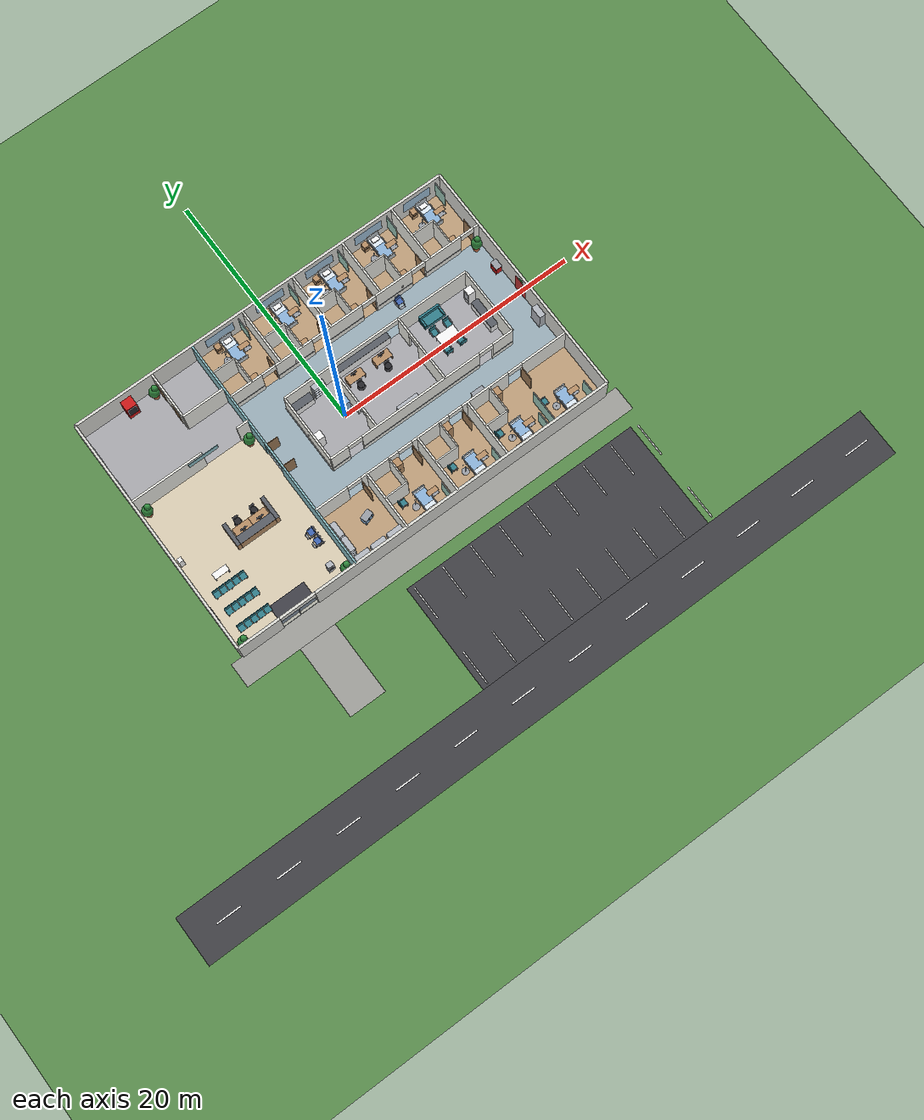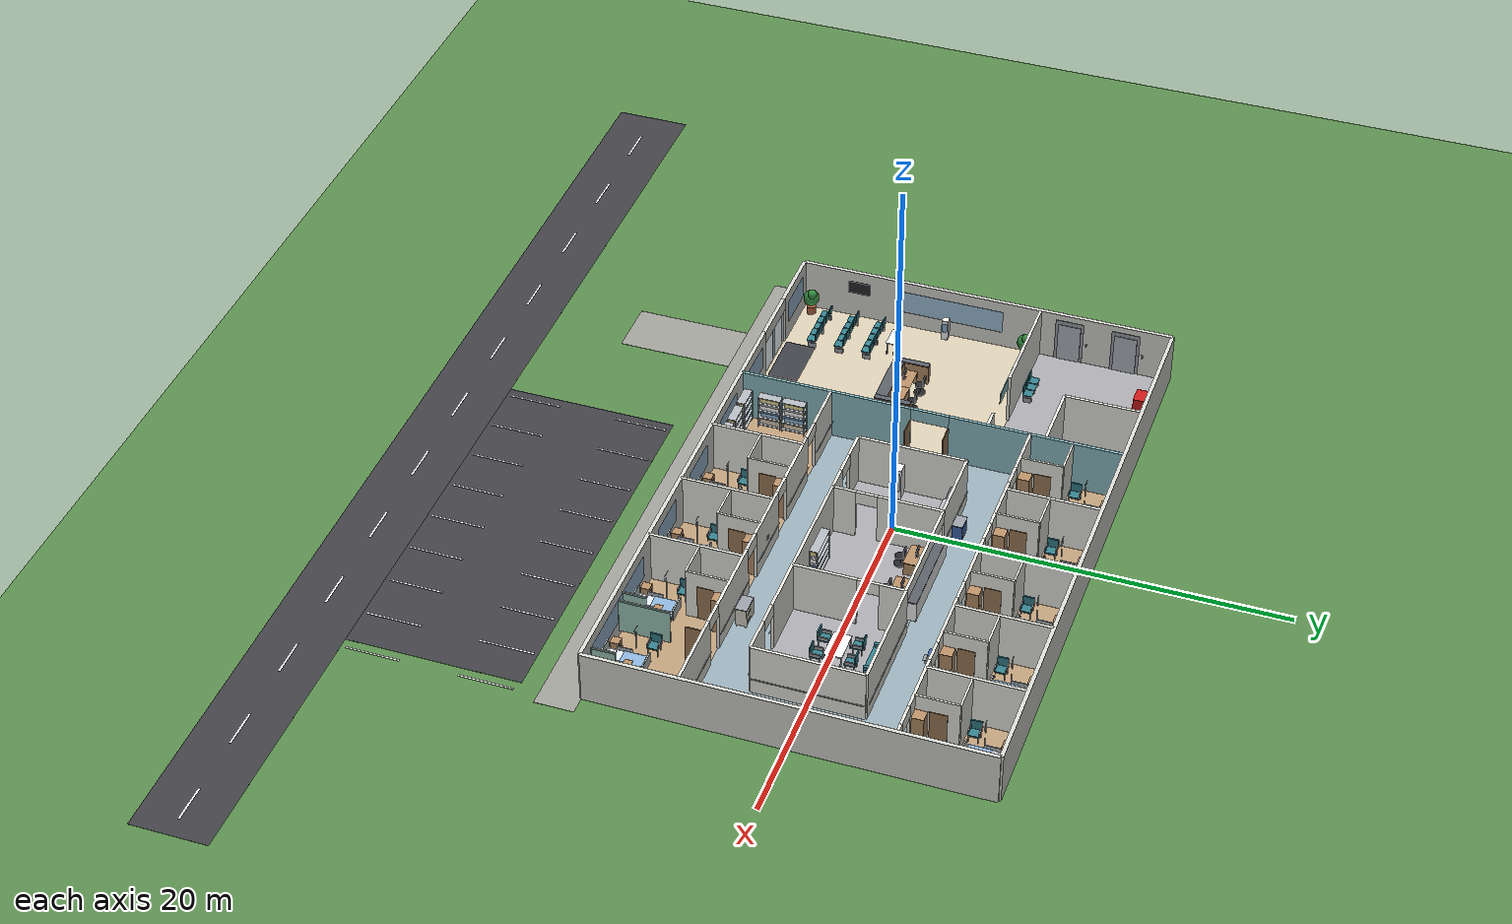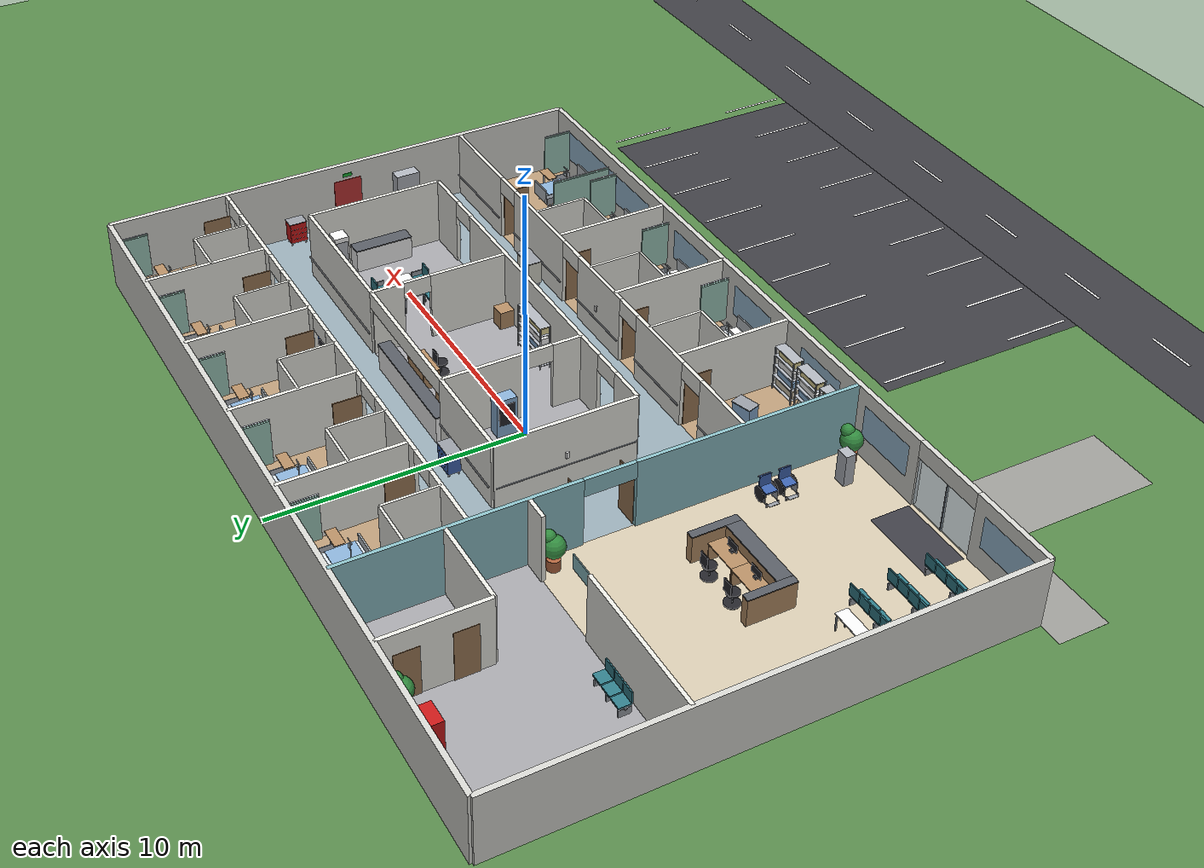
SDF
<sdf version="1.6">
 <world name="hospital">
  <include><uri>model://sun</uri></include>
  <model name="ground_plane">
   <static>true</static>
   <link name="link">
    <collision name="collision">
     <geometry><plane><normal>0 0 1</normal><size>100 100</size></plane></geometry>
     <surface>
      <contact><collide_bitmask>0xffff</collide_bitmask></contact>
      <friction><ode><mu>100</mu><mu2>50</mu2></ode></friction>
     </surface>
    </collision>
    <visual name="visual">
     <cast_shadows>false</cast_shadows>
     <geometry><plane><normal>0 0 1</normal><size>100 100</size></plane></geometry>
     <material>
      <ambient>0.35 0.55 0.3 1</ambient>
      <diffuse>0.35 0.55 0.3 1</diffuse>
      <specular>0 0 0 1</specular>
     </material>
    </visual>
   </link>
  </model>
  <scene>
   <ambient>0.6 0.6 0.6 1</ambient>
   <background>0.75 0.85 0.95 1</background>
   <shadows>false</shadows>
  </scene>
  <physics type="ode">
   <max_step_size>0.001</max_step_size>
   <real_time_factor>1</real_time_factor>
   <real_time_update_rate>1000</real_time_update_rate>
   <ode>
    <solver><type>quick</type><iters>150</iters><sor>1.0</sor></solver>
    <constraints>
     <cfm>0.0001</cfm>
     <erp>0.2</erp>
     <contact_max_correcting_vel>100</contact_max_correcting_vel>
     <contact_surface_layer>0.001</contact_surface_layer>
    </constraints>
   </ode>
  </physics>
  <model name="floor_finishes">
   <static>true</static>
   <link name="link">
    <visual name="v0">
     <pose>-11 -3.5 0.0025 0 0 0</pose>
     <geometry><box><size>10 13 0.001</size></box></geometry>
     <material>
      <ambient>0.85 0.8 0.7 1</ambient>
      <diffuse>0.85 0.8 0.7 1</diffuse>
      <specular>0.1 0.1 0.1 1</specular>
     </material>
    </visual>
    <visual name="v1">
     <pose>-11 6.5 0.0025 0 0 0</pose>
     <geometry><box><size>10 7 0.001</size></box></geometry>
     <material>
      <ambient>0.66 0.66 0.68 1</ambient>
      <diffuse>0.66 0.66 0.68 1</diffuse>
      <specular>0.1 0.1 0.1 1</specular>
     </material>
    </visual>
    <visual name="v2">
     <pose>5 0 0.0025 0 0 0</pose>
     <geometry><box><size>22 10.4 0.001</size></box></geometry>
     <material>
      <ambient>0.6 0.68 0.72 1</ambient>
      <diffuse>0.6 0.68 0.72 1</diffuse>
      <specular>0.1 0.1 0.1 1</specular>
     </material>
    </visual>
    <visual name="v3">
     <pose>5 7.6 0.0025 0 0 0</pose>
     <geometry><box><size>22 4.8 0.001</size></box></geometry>
     <material>
      <ambient>0.74 0.62 0.48 1</ambient>
      <diffuse>0.74 0.62 0.48 1</diffuse>
      <specular>0.1 0.1 0.1 1</specular>
     </material>
    </visual>
    <visual name="v4">
     <pose>5 -7.6 0.0025 0 0 0</pose>
     <geometry><box><size>22 4.8 0.001</size></box></geometry>
     <material>
      <ambient>0.74 0.62 0.48 1</ambient>
      <diffuse>0.74 0.62 0.48 1</diffuse>
      <specular>0.1 0.1 0.1 1</specular>
     </material>
    </visual>
    <visual name="v5">
     <pose>5 0 0.0045 0 0 0</pose>
     <geometry><box><size>16 5.6 0.001</size></box></geometry>
     <material>
      <ambient>0.66 0.66 0.68 1</ambient>
      <diffuse>0.66 0.66 0.68 1</diffuse>
      <specular>0.1 0.1 0.1 1</specular>
     </material>
    </visual>
    <visual name="v6">
     <pose>-11 -9 0.0045 0 0 0</pose>
     <geometry><box><size>3 1.6 0.001</size></box></geometry>
     <material>
      <ambient>0.25 0.25 0.28 1</ambient>
      <diffuse>0.25 0.25 0.28 1</diffuse>
      <specular>0.1 0.1 0.1 1</specular>
     </material>
    </visual>
    <visual name="v7">
     <pose>0 -11 0.0025 0 0 0</pose>
     <geometry><box><size>34 2 0.001</size></box></geometry>
     <material>
      <ambient>0.62 0.62 0.6 1</ambient>
      <diffuse>0.62 0.62 0.6 1</diffuse>
      <specular>0.1 0.1 0.1 1</specular>
     </material>
    </visual>
    <visual name="v8">
     <pose>-11 -15 0.0025 0 0 0</pose>
     <geometry><box><size>3 6 0.001</size></box></geometry>
     <material>
      <ambient>0.62 0.62 0.6 1</ambient>
      <diffuse>0.62 0.62 0.6 1</diffuse>
      <specular>0.1 0.1 0.1 1</specular>
     </material>
    </visual>
    <visual name="v9">
     <pose>6 -17.5 0.0025 0 0 0</pose>
     <geometry><box><size>20 9 0.001</size></box></geometry>
     <material>
      <ambient>0.25 0.25 0.27 1</ambient>
      <diffuse>0.25 0.25 0.27 1</diffuse>
      <specular>0.1 0.1 0.1 1</specular>
     </material>
    </visual>
    <visual name="v10">
     <pose>-3.5 -14.6 0.0045 0 0 0</pose>
     <geometry><box><size>0.1 2.8 0.001</size></box></geometry>
     <material>
      <ambient>0.95 0.95 0.95 1</ambient>
      <diffuse>0.95 0.95 0.95 1</diffuse>
      <specular>0.1 0.1 0.1 1</specular>
     </material>
    </visual>
    <visual name="v11">
     <pose>-3.5 -20.4 0.0045 0 0 0</pose>
     <geometry><box><size>0.1 2.8 0.001</size></box></geometry>
     <material>
      <ambient>0.95 0.95 0.95 1</ambient>
      <diffuse>0.95 0.95 0.95 1</diffuse>
      <specular>0.1 0.1 0.1 1</specular>
     </material>
    </visual>
    <visual name="v12">
     <pose>-1 -14.6 0.0045 0 0 0</pose>
     <geometry><box><size>0.1 2.8 0.001</size></box></geometry>
     <material>
      <ambient>0.95 0.95 0.95 1</ambient>
      <diffuse>0.95 0.95 0.95 1</diffuse>
      <specular>0.1 0.1 0.1 1</specular>
     </material>
    </visual>
    <visual name="v13">
     <pose>-1 -20.4 0.0045 0 0 0</pose>
     <geometry><box><size>0.1 2.8 0.001</size></box></geometry>
     <material>
      <ambient>0.95 0.95 0.95 1</ambient>
      <diffuse>0.95 0.95 0.95 1</diffuse>
      <specular>0.1 0.1 0.1 1</specular>
     </material>
    </visual>
    <visual name="v14">
     <pose>1.5 -14.6 0.0045 0 0 0</pose>
     <geometry><box><size>0.1 2.8 0.001</size></box></geometry>
     <material>
      <ambient>0.95 0.95 0.95 1</ambient>
      <diffuse>0.95 0.95 0.95 1</diffuse>
      <specular>0.1 0.1 0.1 1</specular>
     </material>
    </visual>
    <visual name="v15">
     <pose>1.5 -20.4 0.0045 0 0 0</pose>
     <geometry><box><size>0.1 2.8 0.001</size></box></geometry>
     <material>
      <ambient>0.95 0.95 0.95 1</ambient>
      <diffuse>0.95 0.95 0.95 1</diffuse>
      <specular>0.1 0.1 0.1 1</specular>
     </material>
    </visual>
    <visual name="v16">
     <pose>4 -14.6 0.0045 0 0 0</pose>
     <geometry><box><size>0.1 2.8 0.001</size></box></geometry>
     <material>
      <ambient>0.95 0.95 0.95 1</ambient>
      <diffuse>0.95 0.95 0.95 1</diffuse>
      <specular>0.1 0.1 0.1 1</specular>
     </material>
    </visual>
    <visual name="v17">
     <pose>4 -20.4 0.0045 0 0 0</pose>
     <geometry><box><size>0.1 2.8 0.001</size></box></geometry>
     <material>
      <ambient>0.95 0.95 0.95 1</ambient>
      <diffuse>0.95 0.95 0.95 1</diffuse>
      <specular>0.1 0.1 0.1 1</specular>
     </material>
    </visual>
    <visual name="v18">
     <pose>6.5 -14.6 0.0045 0 0 0</pose>
     <geometry><box><size>0.1 2.8 0.001</size></box></geometry>
     <material>
      <ambient>0.95 0.95 0.95 1</ambient>
      <diffuse>0.95 0.95 0.95 1</diffuse>
      <specular>0.1 0.1 0.1 1</specular>
     </material>
    </visual>
    <visual name="v19">
     <pose>6.5 -20.4 0.0045 0 0 0</pose>
     <geometry><box><size>0.1 2.8 0.001</size></box></geometry>
     <material>
      <ambient>0.95 0.95 0.95 1</ambient>
      <diffuse>0.95 0.95 0.95 1</diffuse>
      <specular>0.1 0.1 0.1 1</specular>
     </material>
    </visual>
    <visual name="v20">
     <pose>9 -14.6 0.0045 0 0 0</pose>
     <geometry><box><size>0.1 2.8 0.001</size></box></geometry>
     <material>
      <ambient>0.95 0.95 0.95 1</ambient>
      <diffuse>0.95 0.95 0.95 1</diffuse>
      <specular>0.1 0.1 0.1 1</specular>
     </material>
    </visual>
    <visual name="v21">
     <pose>9 -20.4 0.0045 0 0 0</pose>
     <geometry><box><size>0.1 2.8 0.001</size></box></geometry>
     <material>
      <ambient>0.95 0.95 0.95 1</ambient>
      <diffuse>0.95 0.95 0.95 1</diffuse>
      <specular>0.1 0.1 0.1 1</specular>
     </material>
    </visual>
    <visual name="v22">
     <pose>11.5 -14.6 0.0045 0 0 0</pose>
     <geometry><box><size>0.1 2.8 0.001</size></box></geometry>
     <material>
      <ambient>0.95 0.95 0.95 1</ambient>
      <diffuse>0.95 0.95 0.95 1</diffuse>
      <specular>0.1 0.1 0.1 1</specular>
     </material>
    </visual>
    <visual name="v23">
     <pose>11.5 -20.4 0.0045 0 0 0</pose>
     <geometry><box><size>0.1 2.8 0.001</size></box></geometry>
     <material>
      <ambient>0.95 0.95 0.95 1</ambient>
      <diffuse>0.95 0.95 0.95 1</diffuse>
      <specular>0.1 0.1 0.1 1</specular>
     </material>
    </visual>
    <visual name="v24">
     <pose>14 -14.6 0.0045 0 0 0</pose>
     <geometry><box><size>0.1 2.8 0.001</size></box></geometry>
     <material>
      <ambient>0.95 0.95 0.95 1</ambient>
      <diffuse>0.95 0.95 0.95 1</diffuse>
      <specular>0.1 0.1 0.1 1</specular>
     </material>
    </visual>
    <visual name="v25">
     <pose>14 -20.4 0.0045 0 0 0</pose>
     <geometry><box><size>0.1 2.8 0.001</size></box></geometry>
     <material>
      <ambient>0.95 0.95 0.95 1</ambient>
      <diffuse>0.95 0.95 0.95 1</diffuse>
      <specular>0.1 0.1 0.1 1</specular>
     </material>
    </visual>
    <visual name="v26">
     <pose>16.5 -14.6 0.0045 0 0 0</pose>
     <geometry><box><size>0.1 2.8 0.001</size></box></geometry>
     <material>
      <ambient>0.95 0.95 0.95 1</ambient>
      <diffuse>0.95 0.95 0.95 1</diffuse>
      <specular>0.1 0.1 0.1 1</specular>
     </material>
    </visual>
    <visual name="v27">
     <pose>16.5 -20.4 0.0045 0 0 0</pose>
     <geometry><box><size>0.1 2.8 0.001</size></box></geometry>
     <material>
      <ambient>0.95 0.95 0.95 1</ambient>
      <diffuse>0.95 0.95 0.95 1</diffuse>
      <specular>0.1 0.1 0.1 1</specular>
     </material>
    </visual>
    <visual name="v28">
     <pose>0 -24 0.0025 0 0 0</pose>
     <geometry><box><size>60 4 0.001</size></box></geometry>
     <material>
      <ambient>0.25 0.25 0.27 1</ambient>
      <diffuse>0.25 0.25 0.27 1</diffuse>
      <specular>0.1 0.1 0.1 1</specular>
     </material>
    </visual>
    <visual name="v29">
     <pose>-27 -24 0.0045 0 0 0</pose>
     <geometry><box><size>2 0.12 0.001</size></box></geometry>
     <material>
      <ambient>0.95 0.95 0.95 1</ambient>
      <diffuse>0.95 0.95 0.95 1</diffuse>
      <specular>0.1 0.1 0.1 1</specular>
     </material>
    </visual>
    <visual name="v30">
     <pose>-22 -24 0.0045 0 0 0</pose>
     <geometry><box><size>2 0.12 0.001</size></box></geometry>
     <material>
      <ambient>0.95 0.95 0.95 1</ambient>
      <diffuse>0.95 0.95 0.95 1</diffuse>
      <specular>0.1 0.1 0.1 1</specular>
     </material>
    </visual>
    <visual name="v31">
     <pose>-17 -24 0.0045 0 0 0</pose>
     <geometry><box><size>2 0.12 0.001</size></box></geometry>
     <material>
      <ambient>0.95 0.95 0.95 1</ambient>
      <diffuse>0.95 0.95 0.95 1</diffuse>
      <specular>0.1 0.1 0.1 1</specular>
     </material>
    </visual>
    <visual name="v32">
     <pose>-12 -24 0.0045 0 0 0</pose>
     <geometry><box><size>2 0.12 0.001</size></box></geometry>
     <material>
      <ambient>0.95 0.95 0.95 1</ambient>
      <diffuse>0.95 0.95 0.95 1</diffuse>
      <specular>0.1 0.1 0.1 1</specular>
     </material>
    </visual>
    <visual name="v33">
     <pose>-7 -24 0.0045 0 0 0</pose>
     <geometry><box><size>2 0.12 0.001</size></box></geometry>
     <material>
      <ambient>0.95 0.95 0.95 1</ambient>
      <diffuse>0.95 0.95 0.95 1</diffuse>
      <specular>0.1 0.1 0.1 1</specular>
     </material>
    </visual>
    <visual name="v34">
     <pose>-2 -24 0.0045 0 0 0</pose>
     <geometry><box><size>2 0.12 0.001</size></box></geometry>
     <material>
      <ambient>0.95 0.95 0.95 1</ambient>
      <diffuse>0.95 0.95 0.95 1</diffuse>
      <specular>0.1 0.1 0.1 1</specular>
     </material>
    </visual>
    <visual name="v35">
     <pose>3 -24 0.0045 0 0 0</pose>
     <geometry><box><size>2 0.12 0.001</size></box></geometry>
     <material>
      <ambient>0.95 0.95 0.95 1</ambient>
      <diffuse>0.95 0.95 0.95 1</diffuse>
      <specular>0.1 0.1 0.1 1</specular>
     </material>
    </visual>
    <visual name="v36">
     <pose>8 -24 0.0045 0 0 0</pose>
     <geometry><box><size>2 0.12 0.001</size></box></geometry>
     <material>
      <ambient>0.95 0.95 0.95 1</ambient>
      <diffuse>0.95 0.95 0.95 1</diffuse>
      <specular>0.1 0.1 0.1 1</specular>
     </material>
    </visual>
    <visual name="v37">
     <pose>13 -24 0.0045 0 0 0</pose>
     <geometry><box><size>2 0.12 0.001</size></box></geometry>
     <material>
      <ambient>0.95 0.95 0.95 1</ambient>
      <diffuse>0.95 0.95 0.95 1</diffuse>
      <specular>0.1 0.1 0.1 1</specular>
     </material>
    </visual>
    <visual name="v38">
     <pose>18 -24 0.0045 0 0 0</pose>
     <geometry><box><size>2 0.12 0.001</size></box></geometry>
     <material>
      <ambient>0.95 0.95 0.95 1</ambient>
      <diffuse>0.95 0.95 0.95 1</diffuse>
      <specular>0.1 0.1 0.1 1</specular>
     </material>
    </visual>
    <visual name="v39">
     <pose>23 -24 0.0045 0 0 0</pose>
     <geometry><box><size>2 0.12 0.001</size></box></geometry>
     <material>
      <ambient>0.95 0.95 0.95 1</ambient>
      <diffuse>0.95 0.95 0.95 1</diffuse>
      <specular>0.1 0.1 0.1 1</specular>
     </material>
    </visual>
    <visual name="v40">
     <pose>28 -24 0.0045 0 0 0</pose>
     <geometry><box><size>2 0.12 0.001</size></box></geometry>
     <material>
      <ambient>0.95 0.95 0.95 1</ambient>
      <diffuse>0.95 0.95 0.95 1</diffuse>
      <specular>0.1 0.1 0.1 1</specular>
     </material>
    </visual>
   </link>
  </model>
  <model name="hospital_walls">
   <static>true</static>
   <link name="link">
    <collision name="c0">
     <pose>-14.25 -10 1.4 0 0 0</pose>
     <geometry><box><size>3.5 0.2 2.8</size></box></geometry>
    </collision>
    <visual name="v0">
     <pose>-14.25 -10 1.4 0 0 0</pose>
     <geometry><box><size>3.5 0.2 2.8</size></box></geometry>
     <material>
      <ambient>0.85 0.85 0.83 1</ambient>
      <diffuse>0.85 0.85 0.83 1</diffuse>
      <specular>0.1 0.1 0.1 1</specular>
     </material>
    </visual>
    <collision name="c1">
     <pose>3.25 -10 1.4 0 0 0</pose>
     <geometry><box><size>25.5 0.2 2.8</size></box></geometry>
    </collision>
    <visual name="v1">
     <pose>3.25 -10 1.4 0 0 0</pose>
     <geometry><box><size>25.5 0.2 2.8</size></box></geometry>
     <material>
      <ambient>0.85 0.85 0.83 1</ambient>
      <diffuse>0.85 0.85 0.83 1</diffuse>
      <specular>0.1 0.1 0.1 1</specular>
     </material>
    </visual>
    <visual name="v2">
     <pose>-11 -10 2.45 0 0 0</pose>
     <geometry><box><size>3 0.2 0.7</size></box></geometry>
     <material>
      <ambient>0.85 0.85 0.83 1</ambient>
      <diffuse>0.85 0.85 0.83 1</diffuse>
      <specular>0.1 0.1 0.1 1</specular>
     </material>
    </visual>
    <collision name="c3">
     <pose>0 10 1.4 0 0 0</pose>
     <geometry><box><size>32 0.2 2.8</size></box></geometry>
    </collision>
    <visual name="v3">
     <pose>0 10 1.4 0 0 0</pose>
     <geometry><box><size>32 0.2 2.8</size></box></geometry>
     <material>
      <ambient>0.85 0.85 0.83 1</ambient>
      <diffuse>0.85 0.85 0.83 1</diffuse>
      <specular>0.1 0.1 0.1 1</specular>
     </material>
    </visual>
    <collision name="c4">
     <pose>-16 0 1.4 0 0 0</pose>
     <geometry><box><size>0.2 20 2.8</size></box></geometry>
    </collision>
    <visual name="v4">
     <pose>-16 0 1.4 0 0 0</pose>
     <geometry><box><size>0.2 20 2.8</size></box></geometry>
     <material>
      <ambient>0.85 0.85 0.83 1</ambient>
      <diffuse>0.85 0.85 0.83 1</diffuse>
      <specular>0.1 0.1 0.1 1</specular>
     </material>
    </visual>
    <collision name="c5">
     <pose>16 0 1.4 0 0 0</pose>
     <geometry><box><size>0.2 20 2.8</size></box></geometry>
    </collision>
    <visual name="v5">
     <pose>16 0 1.4 0 0 0</pose>
     <geometry><box><size>0.2 20 2.8</size></box></geometry>
     <material>
      <ambient>0.85 0.85 0.83 1</ambient>
      <diffuse>0.85 0.85 0.83 1</diffuse>
      <specular>0.1 0.1 0.1 1</specular>
     </material>
    </visual>
    <collision name="c6">
     <pose>-13 3 1.4 0 0 0</pose>
     <geometry><box><size>6 0.15 2.8</size></box></geometry>
    </collision>
    <visual name="v6">
     <pose>-13 3 1.4 0 0 0</pose>
     <geometry><box><size>6 0.15 2.8</size></box></geometry>
     <material>
      <ambient>0.93 0.93 0.9 1</ambient>
      <diffuse>0.93 0.93 0.9 1</diffuse>
      <specular>0.1 0.1 0.1 1</specular>
     </material>
    </visual>
    <collision name="c7">
     <pose>-6.5 3 1.4 0 0 0</pose>
     <geometry><box><size>1 0.15 2.8</size></box></geometry>
    </collision>
    <visual name="v7">
     <pose>-6.5 3 1.4 0 0 0</pose>
     <geometry><box><size>1 0.15 2.8</size></box></geometry>
     <material>
      <ambient>0.93 0.93 0.9 1</ambient>
      <diffuse>0.93 0.93 0.9 1</diffuse>
      <specular>0.1 0.1 0.1 1</specular>
     </material>
    </visual>
    <collision name="c8">
     <pose>-9.5 8 1.4 0 0 0</pose>
     <geometry><box><size>0.15 4 2.8</size></box></geometry>
    </collision>
    <visual name="v8">
     <pose>-9.5 8 1.4 0 0 0</pose>
     <geometry><box><size>0.15 4 2.8</size></box></geometry>
     <material>
      <ambient>0.93 0.93 0.9 1</ambient>
      <diffuse>0.93 0.93 0.9 1</diffuse>
      <specular>0.1 0.1 0.1 1</specular>
     </material>
    </visual>
    <collision name="c9">
     <pose>-7.75 6 1.4 0 0 0</pose>
     <geometry><box><size>3.5 0.15 2.8</size></box></geometry>
    </collision>
    <visual name="v9">
     <pose>-7.75 6 1.4 0 0 0</pose>
     <geometry><box><size>3.5 0.15 2.8</size></box></geometry>
     <material>
      <ambient>0.93 0.93 0.9 1</ambient>
      <diffuse>0.93 0.93 0.9 1</diffuse>
      <specular>0.1 0.1 0.1 1</specular>
     </material>
    </visual>
    <collision name="c10">
     <pose>-6 -5.5 1.4 0 0 0</pose>
     <geometry><box><size>0.15 9 2.8</size></box></geometry>
    </collision>
    <visual name="v10">
     <pose>-6 -5.5 1.4 0 0 0</pose>
     <geometry><box><size>0.15 9 2.8</size></box></geometry>
     <material>
      <ambient>0.55 0.75 0.78 1</ambient>
      <diffuse>0.55 0.75 0.78 1</diffuse>
      <specular>0.1 0.1 0.1 1</specular>
     </material>
    </visual>
    <collision name="c11">
     <pose>-6 5.5 1.4 0 0 0</pose>
     <geometry><box><size>0.15 9 2.8</size></box></geometry>
    </collision>
    <visual name="v11">
     <pose>-6 5.5 1.4 0 0 0</pose>
     <geometry><box><size>0.15 9 2.8</size></box></geometry>
     <material>
      <ambient>0.55 0.75 0.78 1</ambient>
      <diffuse>0.55 0.75 0.78 1</diffuse>
      <specular>0.1 0.1 0.1 1</specular>
     </material>
    </visual>
    <visual name="v12">
     <pose>-6 0 2.45 0 0 0</pose>
     <geometry><box><size>0.15 2 0.7</size></box></geometry>
     <material>
      <ambient>0.55 0.75 0.78 1</ambient>
      <diffuse>0.55 0.75 0.78 1</diffuse>
      <specular>0.1 0.1 0.1 1</specular>
     </material>
    </visual>
    <collision name="c13">
     <pose>-4.65 5.2 1.4 0 0 0</pose>
     <geometry><box><size>2.7 0.15 2.8</size></box></geometry>
    </collision>
    <visual name="v13">
     <pose>-4.65 5.2 1.4 0 0 0</pose>
     <geometry><box><size>2.7 0.15 2.8</size></box></geometry>
     <material>
      <ambient>0.93 0.93 0.9 1</ambient>
      <diffuse>0.93 0.93 0.9 1</diffuse>
      <specular>0.1 0.1 0.1 1</specular>
     </material>
    </visual>
    <visual name="v14">
     <pose>-4.65 5.065 0.9 0 1.5708 0</pose>
     <geometry><cylinder><radius>0.025</radius><length>2.6</length></cylinder></geometry>
     <material>
      <ambient>0.7 0.72 0.75 1</ambient>
      <diffuse>0.7 0.72 0.75 1</diffuse>
      <specular>0.1 0.1 0.1 1</specular>
     </material>
    </visual>
    <collision name="c15">
     <pose>-0.5 5.2 1.4 0 0 0</pose>
     <geometry><box><size>3.2 0.15 2.8</size></box></geometry>
    </collision>
    <visual name="v15">
     <pose>-0.5 5.2 1.4 0 0 0</pose>
     <geometry><box><size>3.2 0.15 2.8</size></box></geometry>
     <material>
      <ambient>0.93 0.93 0.9 1</ambient>
      <diffuse>0.93 0.93 0.9 1</diffuse>
      <specular>0.1 0.1 0.1 1</specular>
     </material>
    </visual>
    <visual name="v16">
     <pose>-0.5 5.065 0.9 0 1.5708 0</pose>
     <geometry><cylinder><radius>0.025</radius><length>3.1</length></cylinder></geometry>
     <material>
      <ambient>0.7 0.72 0.75 1</ambient>
      <diffuse>0.7 0.72 0.75 1</diffuse>
      <specular>0.1 0.1 0.1 1</specular>
     </material>
    </visual>
    <collision name="c17">
     <pose>3.9 5.2 1.4 0 0 0</pose>
     <geometry><box><size>3.2 0.15 2.8</size></box></geometry>
    </collision>
    <visual name="v17">
     <pose>3.9 5.2 1.4 0 0 0</pose>
     <geometry><box><size>3.2 0.15 2.8</size></box></geometry>
     <material>
      <ambient>0.93 0.93 0.9 1</ambient>
      <diffuse>0.93 0.93 0.9 1</diffuse>
      <specular>0.1 0.1 0.1 1</specular>
     </material>
    </visual>
    <visual name="v18">
     <pose>3.9 5.065 0.9 0 1.5708 0</pose>
     <geometry><cylinder><radius>0.025</radius><length>3.1</length></cylinder></geometry>
     <material>
      <ambient>0.7 0.72 0.75 1</ambient>
      <diffuse>0.7 0.72 0.75 1</diffuse>
      <specular>0.1 0.1 0.1 1</specular>
     </material>
    </visual>
    <collision name="c19">
     <pose>8.3 5.2 1.4 0 0 0</pose>
     <geometry><box><size>3.2 0.15 2.8</size></box></geometry>
    </collision>
    <visual name="v19">
     <pose>8.3 5.2 1.4 0 0 0</pose>
     <geometry><box><size>3.2 0.15 2.8</size></box></geometry>
     <material>
      <ambient>0.93 0.93 0.9 1</ambient>
      <diffuse>0.93 0.93 0.9 1</diffuse>
      <specular>0.1 0.1 0.1 1</specular>
     </material>
    </visual>
    <visual name="v20">
     <pose>8.3 5.065 0.9 0 1.5708 0</pose>
     <geometry><cylinder><radius>0.025</radius><length>3.1</length></cylinder></geometry>
     <material>
      <ambient>0.7 0.72 0.75 1</ambient>
      <diffuse>0.7 0.72 0.75 1</diffuse>
      <specular>0.1 0.1 0.1 1</specular>
     </material>
    </visual>
    <collision name="c21">
     <pose>12.7 5.2 1.4 0 0 0</pose>
     <geometry><box><size>3.2 0.15 2.8</size></box></geometry>
    </collision>
    <visual name="v21">
     <pose>12.7 5.2 1.4 0 0 0</pose>
     <geometry><box><size>3.2 0.15 2.8</size></box></geometry>
     <material>
      <ambient>0.93 0.93 0.9 1</ambient>
      <diffuse>0.93 0.93 0.9 1</diffuse>
      <specular>0.1 0.1 0.1 1</specular>
     </material>
    </visual>
    <visual name="v22">
     <pose>12.7 5.065 0.9 0 1.5708 0</pose>
     <geometry><cylinder><radius>0.025</radius><length>3.1</length></cylinder></geometry>
     <material>
      <ambient>0.7 0.72 0.75 1</ambient>
      <diffuse>0.7 0.72 0.75 1</diffuse>
      <specular>0.1 0.1 0.1 1</specular>
     </material>
    </visual>
    <collision name="c23">
     <pose>15.75 5.2 1.4 0 0 0</pose>
     <geometry><box><size>0.5 0.15 2.8</size></box></geometry>
    </collision>
    <visual name="v23">
     <pose>15.75 5.2 1.4 0 0 0</pose>
     <geometry><box><size>0.5 0.15 2.8</size></box></geometry>
     <material>
      <ambient>0.93 0.93 0.9 1</ambient>
      <diffuse>0.93 0.93 0.9 1</diffuse>
      <specular>0.1 0.1 0.1 1</specular>
     </material>
    </visual>
    <visual name="v24">
     <pose>15.75 5.065 0.9 0 1.5708 0</pose>
     <geometry><cylinder><radius>0.025</radius><length>0.4</length></cylinder></geometry>
     <material>
      <ambient>0.7 0.72 0.75 1</ambient>
      <diffuse>0.7 0.72 0.75 1</diffuse>
      <specular>0.1 0.1 0.1 1</specular>
     </material>
    </visual>
    <visual name="v25">
     <pose>-2.7 5.2 2.45 0 0 0</pose>
     <geometry><box><size>1.2 0.15 0.7</size></box></geometry>
     <material>
      <ambient>0.93 0.93 0.9 1</ambient>
      <diffuse>0.93 0.93 0.9 1</diffuse>
      <specular>0.1 0.1 0.1 1</specular>
     </material>
    </visual>
    <visual name="v26">
     <pose>1.7 5.2 2.45 0 0 0</pose>
     <geometry><box><size>1.2 0.15 0.7</size></box></geometry>
     <material>
      <ambient>0.93 0.93 0.9 1</ambient>
      <diffuse>0.93 0.93 0.9 1</diffuse>
      <specular>0.1 0.1 0.1 1</specular>
     </material>
    </visual>
    <visual name="v27">
     <pose>6.1 5.2 2.45 0 0 0</pose>
     <geometry><box><size>1.2 0.15 0.7</size></box></geometry>
     <material>
      <ambient>0.93 0.93 0.9 1</ambient>
      <diffuse>0.93 0.93 0.9 1</diffuse>
      <specular>0.1 0.1 0.1 1</specular>
     </material>
    </visual>
    <visual name="v28">
     <pose>10.5 5.2 2.45 0 0 0</pose>
     <geometry><box><size>1.2 0.15 0.7</size></box></geometry>
     <material>
      <ambient>0.93 0.93 0.9 1</ambient>
      <diffuse>0.93 0.93 0.9 1</diffuse>
      <specular>0.1 0.1 0.1 1</specular>
     </material>
    </visual>
    <visual name="v29">
     <pose>14.9 5.2 2.45 0 0 0</pose>
     <geometry><box><size>1.2 0.15 0.7</size></box></geometry>
     <material>
      <ambient>0.93 0.93 0.9 1</ambient>
      <diffuse>0.93 0.93 0.9 1</diffuse>
      <specular>0.1 0.1 0.1 1</specular>
     </material>
    </visual>
    <collision name="c30">
     <pose>-4.65 -5.2 1.4 0 0 0</pose>
     <geometry><box><size>2.7 0.15 2.8</size></box></geometry>
    </collision>
    <visual name="v30">
     <pose>-4.65 -5.2 1.4 0 0 0</pose>
     <geometry><box><size>2.7 0.15 2.8</size></box></geometry>
     <material>
      <ambient>0.93 0.93 0.9 1</ambient>
      <diffuse>0.93 0.93 0.9 1</diffuse>
      <specular>0.1 0.1 0.1 1</specular>
     </material>
    </visual>
    <visual name="v31">
     <pose>-4.65 -5.065 0.9 0 1.5708 0</pose>
     <geometry><cylinder><radius>0.025</radius><length>2.6</length></cylinder></geometry>
     <material>
      <ambient>0.7 0.72 0.75 1</ambient>
      <diffuse>0.7 0.72 0.75 1</diffuse>
      <specular>0.1 0.1 0.1 1</specular>
     </material>
    </visual>
    <collision name="c32">
     <pose>-0.5 -5.2 1.4 0 0 0</pose>
     <geometry><box><size>3.2 0.15 2.8</size></box></geometry>
    </collision>
    <visual name="v32">
     <pose>-0.5 -5.2 1.4 0 0 0</pose>
     <geometry><box><size>3.2 0.15 2.8</size></box></geometry>
     <material>
      <ambient>0.93 0.93 0.9 1</ambient>
      <diffuse>0.93 0.93 0.9 1</diffuse>
      <specular>0.1 0.1 0.1 1</specular>
     </material>
    </visual>
    <visual name="v33">
     <pose>-0.5 -5.065 0.9 0 1.5708 0</pose>
     <geometry><cylinder><radius>0.025</radius><length>3.1</length></cylinder></geometry>
     <material>
      <ambient>0.7 0.72 0.75 1</ambient>
      <diffuse>0.7 0.72 0.75 1</diffuse>
      <specular>0.1 0.1 0.1 1</specular>
     </material>
    </visual>
    <collision name="c34">
     <pose>3.9 -5.2 1.4 0 0 0</pose>
     <geometry><box><size>3.2 0.15 2.8</size></box></geometry>
    </collision>
    <visual name="v34">
     <pose>3.9 -5.2 1.4 0 0 0</pose>
     <geometry><box><size>3.2 0.15 2.8</size></box></geometry>
     <material>
      <ambient>0.93 0.93 0.9 1</ambient>
      <diffuse>0.93 0.93 0.9 1</diffuse>
      <specular>0.1 0.1 0.1 1</specular>
     </material>
    </visual>
    <visual name="v35">
     <pose>3.9 -5.065 0.9 0 1.5708 0</pose>
     <geometry><cylinder><radius>0.025</radius><length>3.1</length></cylinder></geometry>
     <material>
      <ambient>0.7 0.72 0.75 1</ambient>
      <diffuse>0.7 0.72 0.75 1</diffuse>
      <specular>0.1 0.1 0.1 1</specular>
     </material>
    </visual>
    <collision name="c36">
     <pose>8.75 -5.2 1.4 0 0 0</pose>
     <geometry><box><size>4.1 0.15 2.8</size></box></geometry>
    </collision>
    <visual name="v36">
     <pose>8.75 -5.2 1.4 0 0 0</pose>
     <geometry><box><size>4.1 0.15 2.8</size></box></geometry>
     <material>
      <ambient>0.93 0.93 0.9 1</ambient>
      <diffuse>0.93 0.93 0.9 1</diffuse>
      <specular>0.1 0.1 0.1 1</specular>
     </material>
    </visual>
    <visual name="v37">
     <pose>8.75 -5.065 0.9 0 1.5708 0</pose>
     <geometry><cylinder><radius>0.025</radius><length>4</length></cylinder></geometry>
     <material>
      <ambient>0.7 0.72 0.75 1</ambient>
      <diffuse>0.7 0.72 0.75 1</diffuse>
      <specular>0.1 0.1 0.1 1</specular>
     </material>
    </visual>
    <collision name="c38">
     <pose>14 -5.2 1.4 0 0 0</pose>
     <geometry><box><size>4 0.15 2.8</size></box></geometry>
    </collision>
    <visual name="v38">
     <pose>14 -5.2 1.4 0 0 0</pose>
     <geometry><box><size>4 0.15 2.8</size></box></geometry>
     <material>
      <ambient>0.93 0.93 0.9 1</ambient>
      <diffuse>0.93 0.93 0.9 1</diffuse>
      <specular>0.1 0.1 0.1 1</specular>
     </material>
    </visual>
    <visual name="v39">
     <pose>14 -5.065 0.9 0 1.5708 0</pose>
     <geometry><cylinder><radius>0.025</radius><length>3.9</length></cylinder></geometry>
     <material>
      <ambient>0.7 0.72 0.75 1</ambient>
      <diffuse>0.7 0.72 0.75 1</diffuse>
      <specular>0.1 0.1 0.1 1</specular>
     </material>
    </visual>
    <visual name="v40">
     <pose>-2.7 -5.2 2.45 0 0 0</pose>
     <geometry><box><size>1.2 0.15 0.7</size></box></geometry>
     <material>
      <ambient>0.93 0.93 0.9 1</ambient>
      <diffuse>0.93 0.93 0.9 1</diffuse>
      <specular>0.1 0.1 0.1 1</specular>
     </material>
    </visual>
    <visual name="v41">
     <pose>1.7 -5.2 2.45 0 0 0</pose>
     <geometry><box><size>1.2 0.15 0.7</size></box></geometry>
     <material>
      <ambient>0.93 0.93 0.9 1</ambient>
      <diffuse>0.93 0.93 0.9 1</diffuse>
      <specular>0.1 0.1 0.1 1</specular>
     </material>
    </visual>
    <visual name="v42">
     <pose>6.1 -5.2 2.45 0 0 0</pose>
     <geometry><box><size>1.2 0.15 0.7</size></box></geometry>
     <material>
      <ambient>0.93 0.93 0.9 1</ambient>
      <diffuse>0.93 0.93 0.9 1</diffuse>
      <specular>0.1 0.1 0.1 1</specular>
     </material>
    </visual>
    <visual name="v43">
     <pose>11.4 -5.2 2.45 0 0 0</pose>
     <geometry><box><size>1.2 0.15 0.7</size></box></geometry>
     <material>
      <ambient>0.93 0.93 0.9 1</ambient>
      <diffuse>0.93 0.93 0.9 1</diffuse>
      <specular>0.1 0.1 0.1 1</specular>
     </material>
    </visual>
    <collision name="c44">
     <pose>-1.6 7.6 1.4 0 0 0</pose>
     <geometry><box><size>0.15 4.8 2.8</size></box></geometry>
    </collision>
    <visual name="v44">
     <pose>-1.6 7.6 1.4 0 0 0</pose>
     <geometry><box><size>0.15 4.8 2.8</size></box></geometry>
     <material>
      <ambient>0.93 0.93 0.9 1</ambient>
      <diffuse>0.93 0.93 0.9 1</diffuse>
      <specular>0.1 0.1 0.1 1</specular>
     </material>
    </visual>
    <collision name="c45">
     <pose>2.8 7.6 1.4 0 0 0</pose>
     <geometry><box><size>0.15 4.8 2.8</size></box></geometry>
    </collision>
    <visual name="v45">
     <pose>2.8 7.6 1.4 0 0 0</pose>
     <geometry><box><size>0.15 4.8 2.8</size></box></geometry>
     <material>
      <ambient>0.93 0.93 0.9 1</ambient>
      <diffuse>0.93 0.93 0.9 1</diffuse>
      <specular>0.1 0.1 0.1 1</specular>
     </material>
    </visual>
    <collision name="c46">
     <pose>7.2 7.6 1.4 0 0 0</pose>
     <geometry><box><size>0.15 4.8 2.8</size></box></geometry>
    </collision>
    <visual name="v46">
     <pose>7.2 7.6 1.4 0 0 0</pose>
     <geometry><box><size>0.15 4.8 2.8</size></box></geometry>
     <material>
      <ambient>0.93 0.93 0.9 1</ambient>
      <diffuse>0.93 0.93 0.9 1</diffuse>
      <specular>0.1 0.1 0.1 1</specular>
     </material>
    </visual>
    <collision name="c47">
     <pose>11.6 7.6 1.4 0 0 0</pose>
     <geometry><box><size>0.15 4.8 2.8</size></box></geometry>
    </collision>
    <visual name="v47">
     <pose>11.6 7.6 1.4 0 0 0</pose>
     <geometry><box><size>0.15 4.8 2.8</size></box></geometry>
     <material>
      <ambient>0.93 0.93 0.9 1</ambient>
      <diffuse>0.93 0.93 0.9 1</diffuse>
      <specular>0.1 0.1 0.1 1</specular>
     </material>
    </visual>
    <collision name="c48">
     <pose>-1.6 -7.6 1.4 0 0 0</pose>
     <geometry><box><size>0.15 4.8 2.8</size></box></geometry>
    </collision>
    <visual name="v48">
     <pose>-1.6 -7.6 1.4 0 0 0</pose>
     <geometry><box><size>0.15 4.8 2.8</size></box></geometry>
     <material>
      <ambient>0.93 0.93 0.9 1</ambient>
      <diffuse>0.93 0.93 0.9 1</diffuse>
      <specular>0.1 0.1 0.1 1</specular>
     </material>
    </visual>
    <collision name="c49">
     <pose>2.8 -7.6 1.4 0 0 0</pose>
     <geometry><box><size>0.15 4.8 2.8</size></box></geometry>
    </collision>
    <visual name="v49">
     <pose>2.8 -7.6 1.4 0 0 0</pose>
     <geometry><box><size>0.15 4.8 2.8</size></box></geometry>
     <material>
      <ambient>0.93 0.93 0.9 1</ambient>
      <diffuse>0.93 0.93 0.9 1</diffuse>
      <specular>0.1 0.1 0.1 1</specular>
     </material>
    </visual>
    <collision name="c50">
     <pose>7.2 -7.6 1.4 0 0 0</pose>
     <geometry><box><size>0.15 4.8 2.8</size></box></geometry>
    </collision>
    <visual name="v50">
     <pose>7.2 -7.6 1.4 0 0 0</pose>
     <geometry><box><size>0.15 4.8 2.8</size></box></geometry>
     <material>
      <ambient>0.93 0.93 0.9 1</ambient>
      <diffuse>0.93 0.93 0.9 1</diffuse>
      <specular>0.1 0.1 0.1 1</specular>
     </material>
    </visual>
    <collision name="c51">
     <pose>-1 2.8 1.4 0 0 0</pose>
     <geometry><box><size>4 0.15 2.8</size></box></geometry>
    </collision>
    <visual name="v51">
     <pose>-1 2.8 1.4 0 0 0</pose>
     <geometry><box><size>4 0.15 2.8</size></box></geometry>
     <material>
      <ambient>0.93 0.93 0.9 1</ambient>
      <diffuse>0.93 0.93 0.9 1</diffuse>
      <specular>0.1 0.1 0.1 1</specular>
     </material>
    </visual>
    <visual name="v52">
     <pose>-1 2.935 0.9 0 1.5708 0</pose>
     <geometry><cylinder><radius>0.025</radius><length>3.9</length></cylinder></geometry>
     <material>
      <ambient>0.7 0.72 0.75 1</ambient>
      <diffuse>0.7 0.72 0.75 1</diffuse>
      <specular>0.1 0.1 0.1 1</specular>
     </material>
    </visual>
    <collision name="c53">
     <pose>10 2.8 1.4 0 0 0</pose>
     <geometry><box><size>6 0.15 2.8</size></box></geometry>
    </collision>
    <visual name="v53">
     <pose>10 2.8 1.4 0 0 0</pose>
     <geometry><box><size>6 0.15 2.8</size></box></geometry>
     <material>
      <ambient>0.93 0.93 0.9 1</ambient>
      <diffuse>0.93 0.93 0.9 1</diffuse>
      <specular>0.1 0.1 0.1 1</specular>
     </material>
    </visual>
    <visual name="v54">
     <pose>10 2.935 0.9 0 1.5708 0</pose>
     <geometry><cylinder><radius>0.025</radius><length>5.9</length></cylinder></geometry>
     <material>
      <ambient>0.7 0.72 0.75 1</ambient>
      <diffuse>0.7 0.72 0.75 1</diffuse>
      <specular>0.1 0.1 0.1 1</specular>
     </material>
    </visual>
    <visual name="v55">
     <pose>4 2.8 2.45 0 0 0</pose>
     <geometry><box><size>6 0.15 0.7</size></box></geometry>
     <material>
      <ambient>0.93 0.93 0.9 1</ambient>
      <diffuse>0.93 0.93 0.9 1</diffuse>
      <specular>0.1 0.1 0.1 1</specular>
     </material>
    </visual>
    <collision name="c56">
     <pose>-2.25 -2.8 1.4 0 0 0</pose>
     <geometry><box><size>1.5 0.15 2.8</size></box></geometry>
    </collision>
    <visual name="v56">
     <pose>-2.25 -2.8 1.4 0 0 0</pose>
     <geometry><box><size>1.5 0.15 2.8</size></box></geometry>
     <material>
      <ambient>0.93 0.93 0.9 1</ambient>
      <diffuse>0.93 0.93 0.9 1</diffuse>
      <specular>0.1 0.1 0.1 1</specular>
     </material>
    </visual>
    <visual name="v57">
     <pose>-2.25 -2.935 0.9 0 1.5708 0</pose>
     <geometry><cylinder><radius>0.025</radius><length>1.4</length></cylinder></geometry>
     <material>
      <ambient>0.7 0.72 0.75 1</ambient>
      <diffuse>0.7 0.72 0.75 1</diffuse>
      <specular>0.1 0.1 0.1 1</specular>
     </material>
    </visual>
    <collision name="c58">
     <pose>4.85 -2.8 1.4 0 0 0</pose>
     <geometry><box><size>10.3 0.15 2.8</size></box></geometry>
    </collision>
    <visual name="v58">
     <pose>4.85 -2.8 1.4 0 0 0</pose>
     <geometry><box><size>10.3 0.15 2.8</size></box></geometry>
     <material>
      <ambient>0.93 0.93 0.9 1</ambient>
      <diffuse>0.93 0.93 0.9 1</diffuse>
      <specular>0.1 0.1 0.1 1</specular>
     </material>
    </visual>
    <visual name="v59">
     <pose>4.85 -2.935 0.9 0 1.5708 0</pose>
     <geometry><cylinder><radius>0.025</radius><length>10.2</length></cylinder></geometry>
     <material>
      <ambient>0.7 0.72 0.75 1</ambient>
      <diffuse>0.7 0.72 0.75 1</diffuse>
      <specular>0.1 0.1 0.1 1</specular>
     </material>
    </visual>
    <collision name="c60">
     <pose>12.1 -2.8 1.4 0 0 0</pose>
     <geometry><box><size>1.8 0.15 2.8</size></box></geometry>
    </collision>
    <visual name="v60">
     <pose>12.1 -2.8 1.4 0 0 0</pose>
     <geometry><box><size>1.8 0.15 2.8</size></box></geometry>
     <material>
      <ambient>0.93 0.93 0.9 1</ambient>
      <diffuse>0.93 0.93 0.9 1</diffuse>
      <specular>0.1 0.1 0.1 1</specular>
     </material>
    </visual>
    <visual name="v61">
     <pose>12.1 -2.935 0.9 0 1.5708 0</pose>
     <geometry><cylinder><radius>0.025</radius><length>1.7</length></cylinder></geometry>
     <material>
      <ambient>0.7 0.72 0.75 1</ambient>
      <diffuse>0.7 0.72 0.75 1</diffuse>
      <specular>0.1 0.1 0.1 1</specular>
     </material>
    </visual>
    <visual name="v62">
     <pose>-0.9 -2.8 2.45 0 0 0</pose>
     <geometry><box><size>1.2 0.15 0.7</size></box></geometry>
     <material>
      <ambient>0.93 0.93 0.9 1</ambient>
      <diffuse>0.93 0.93 0.9 1</diffuse>
      <specular>0.1 0.1 0.1 1</specular>
     </material>
    </visual>
    <visual name="v63">
     <pose>10.6 -2.8 2.45 0 0 0</pose>
     <geometry><box><size>1.2 0.15 0.7</size></box></geometry>
     <material>
      <ambient>0.93 0.93 0.9 1</ambient>
      <diffuse>0.93 0.93 0.9 1</diffuse>
      <specular>0.1 0.1 0.1 1</specular>
     </material>
    </visual>
    <collision name="c64">
     <pose>-3 0 1.4 0 0 0</pose>
     <geometry><box><size>0.15 5.6 2.8</size></box></geometry>
    </collision>
    <visual name="v64">
     <pose>-3 0 1.4 0 0 0</pose>
     <geometry><box><size>0.15 5.6 2.8</size></box></geometry>
     <material>
      <ambient>0.93 0.93 0.9 1</ambient>
      <diffuse>0.93 0.93 0.9 1</diffuse>
      <specular>0.1 0.1 0.1 1</specular>
     </material>
    </visual>
    <visual name="v65">
     <pose>-3.135 0 0.9 1.5708 0 0</pose>
     <geometry><cylinder><radius>0.025</radius><length>5.5</length></cylinder></geometry>
     <material>
      <ambient>0.7 0.72 0.75 1</ambient>
      <diffuse>0.7 0.72 0.75 1</diffuse>
      <specular>0.1 0.1 0.1 1</specular>
     </material>
    </visual>
    <collision name="c66">
     <pose>13 0 1.4 0 0 0</pose>
     <geometry><box><size>0.15 5.6 2.8</size></box></geometry>
    </collision>
    <visual name="v66">
     <pose>13 0 1.4 0 0 0</pose>
     <geometry><box><size>0.15 5.6 2.8</size></box></geometry>
     <material>
      <ambient>0.93 0.93 0.9 1</ambient>
      <diffuse>0.93 0.93 0.9 1</diffuse>
      <specular>0.1 0.1 0.1 1</specular>
     </material>
    </visual>
    <visual name="v67">
     <pose>13.135 0 0.9 1.5708 0 0</pose>
     <geometry><cylinder><radius>0.025</radius><length>5.5</length></cylinder></geometry>
     <material>
      <ambient>0.7 0.72 0.75 1</ambient>
      <diffuse>0.7 0.72 0.75 1</diffuse>
      <specular>0.1 0.1 0.1 1</specular>
     </material>
    </visual>
    <collision name="c68">
     <pose>1 -2.2 1.4 0 0 0</pose>
     <geometry><box><size>0.15 1.2 2.8</size></box></geometry>
    </collision>
    <visual name="v68">
     <pose>1 -2.2 1.4 0 0 0</pose>
     <geometry><box><size>0.15 1.2 2.8</size></box></geometry>
     <material>
      <ambient>0.93 0.93 0.9 1</ambient>
      <diffuse>0.93 0.93 0.9 1</diffuse>
      <specular>0.1 0.1 0.1 1</specular>
     </material>
    </visual>
    <collision name="c69">
     <pose>1 1.15 1.4 0 0 0</pose>
     <geometry><box><size>0.15 3.3 2.8</size></box></geometry>
    </collision>
    <visual name="v69">
     <pose>1 1.15 1.4 0 0 0</pose>
     <geometry><box><size>0.15 3.3 2.8</size></box></geometry>
     <material>
      <ambient>0.93 0.93 0.9 1</ambient>
      <diffuse>0.93 0.93 0.9 1</diffuse>
      <specular>0.1 0.1 0.1 1</specular>
     </material>
    </visual>
    <visual name="v70">
     <pose>1 -1.05 2.45 0 0 0</pose>
     <geometry><box><size>0.15 1.1 0.7</size></box></geometry>
     <material>
      <ambient>0.93 0.93 0.9 1</ambient>
      <diffuse>0.93 0.93 0.9 1</diffuse>
      <specular>0.1 0.1 0.1 1</specular>
     </material>
    </visual>
    <collision name="c71">
     <pose>7 -1.2 1.4 0 0 0</pose>
     <geometry><box><size>0.15 3.2 2.8</size></box></geometry>
    </collision>
    <visual name="v71">
     <pose>7 -1.2 1.4 0 0 0</pose>
     <geometry><box><size>0.15 3.2 2.8</size></box></geometry>
     <material>
      <ambient>0.93 0.93 0.9 1</ambient>
      <diffuse>0.93 0.93 0.9 1</diffuse>
      <specular>0.1 0.1 0.1 1</specular>
     </material>
    </visual>
    <collision name="c72">
     <pose>7 2.15 1.4 0 0 0</pose>
     <geometry><box><size>0.15 1.3 2.8</size></box></geometry>
    </collision>
    <visual name="v72">
     <pose>7 2.15 1.4 0 0 0</pose>
     <geometry><box><size>0.15 1.3 2.8</size></box></geometry>
     <material>
      <ambient>0.93 0.93 0.9 1</ambient>
      <diffuse>0.93 0.93 0.9 1</diffuse>
      <specular>0.1 0.1 0.1 1</specular>
     </material>
    </visual>
    <visual name="v73">
     <pose>7 0.95 2.45 0 0 0</pose>
     <geometry><box><size>0.15 1.1 0.7</size></box></geometry>
     <material>
      <ambient>0.93 0.93 0.9 1</ambient>
      <diffuse>0.93 0.93 0.9 1</diffuse>
      <specular>0.1 0.1 0.1 1</specular>
     </material>
    </visual>
    <visual name="v74">
     <pose>-3.8 9.895 1.55 0 0 0</pose>
     <geometry><box><size>2.4 0.01 1.3</size></box></geometry>
     <material>
      <ambient>0.65 0.82 0.95 0.8</ambient>
      <diffuse>0.65 0.82 0.95 0.8</diffuse>
      <specular>0.1 0.1 0.1 1</specular>
     </material>
    </visual>
    <visual name="v75">
     <pose>0.6 9.895 1.55 0 0 0</pose>
     <geometry><box><size>2.4 0.01 1.3</size></box></geometry>
     <material>
      <ambient>0.65 0.82 0.95 0.8</ambient>
      <diffuse>0.65 0.82 0.95 0.8</diffuse>
      <specular>0.1 0.1 0.1 1</specular>
     </material>
    </visual>
    <visual name="v76">
     <pose>5 9.895 1.55 0 0 0</pose>
     <geometry><box><size>2.4 0.01 1.3</size></box></geometry>
     <material>
      <ambient>0.65 0.82 0.95 0.8</ambient>
      <diffuse>0.65 0.82 0.95 0.8</diffuse>
      <specular>0.1 0.1 0.1 1</specular>
     </material>
    </visual>
    <visual name="v77">
     <pose>9.4 9.895 1.55 0 0 0</pose>
     <geometry><box><size>2.4 0.01 1.3</size></box></geometry>
     <material>
      <ambient>0.65 0.82 0.95 0.8</ambient>
      <diffuse>0.65 0.82 0.95 0.8</diffuse>
      <specular>0.1 0.1 0.1 1</specular>
     </material>
    </visual>
    <visual name="v78">
     <pose>13.8 9.895 1.55 0 0 0</pose>
     <geometry><box><size>2.4 0.01 1.3</size></box></geometry>
     <material>
      <ambient>0.65 0.82 0.95 0.8</ambient>
      <diffuse>0.65 0.82 0.95 0.8</diffuse>
      <specular>0.1 0.1 0.1 1</specular>
     </material>
    </visual>
    <visual name="v79">
     <pose>-3.8 -9.895 1.55 0 0 0</pose>
     <geometry><box><size>2.4 0.01 1.3</size></box></geometry>
     <material>
      <ambient>0.65 0.82 0.95 0.8</ambient>
      <diffuse>0.65 0.82 0.95 0.8</diffuse>
      <specular>0.1 0.1 0.1 1</specular>
     </material>
    </visual>
    <visual name="v80">
     <pose>0.6 -9.895 1.55 0 0 0</pose>
     <geometry><box><size>2.4 0.01 1.3</size></box></geometry>
     <material>
      <ambient>0.65 0.82 0.95 0.8</ambient>
      <diffuse>0.65 0.82 0.95 0.8</diffuse>
      <specular>0.1 0.1 0.1 1</specular>
     </material>
    </visual>
    <visual name="v81">
     <pose>5 -9.895 1.55 0 0 0</pose>
     <geometry><box><size>2.4 0.01 1.3</size></box></geometry>
     <material>
      <ambient>0.65 0.82 0.95 0.8</ambient>
      <diffuse>0.65 0.82 0.95 0.8</diffuse>
      <specular>0.1 0.1 0.1 1</specular>
     </material>
    </visual>
    <visual name="v82">
     <pose>11.6 -9.895 1.55 0 0 0</pose>
     <geometry><box><size>6.8 0.01 1.3</size></box></geometry>
     <material>
      <ambient>0.65 0.82 0.95 0.8</ambient>
      <diffuse>0.65 0.82 0.95 0.8</diffuse>
      <specular>0.1 0.1 0.1 1</specular>
     </material>
    </visual>
    <visual name="v83">
     <pose>-14.25 -9.895 1.55 0 0 0</pose>
     <geometry><box><size>2.5 0.01 1.3</size></box></geometry>
     <material>
      <ambient>0.65 0.82 0.95 0.8</ambient>
      <diffuse>0.65 0.82 0.95 0.8</diffuse>
      <specular>0.1 0.1 0.1 1</specular>
     </material>
    </visual>
    <visual name="v84">
     <pose>-7.75 -9.895 1.55 0 0 0</pose>
     <geometry><box><size>2.5 0.01 1.3</size></box></geometry>
     <material>
      <ambient>0.65 0.82 0.95 0.8</ambient>
      <diffuse>0.65 0.82 0.95 0.8</diffuse>
      <specular>0.1 0.1 0.1 1</specular>
     </material>
    </visual>
    <visual name="v85">
     <pose>-15.895 -1.75 1.55 0 0 0</pose>
     <geometry><box><size>0.01 5.5 1.3</size></box></geometry>
     <material>
      <ambient>0.65 0.82 0.95 0.8</ambient>
      <diffuse>0.65 0.82 0.95 0.8</diffuse>
      <specular>0.1 0.1 0.1 1</specular>
     </material>
    </visual>
   </link>
  </model>
  <model name="entrance_glass_doors">
   <static>true</static>
   <link name="link">
    <collision name="c0">
     <pose>-11 -10 1.05 0 0 0</pose>
     <geometry><box><size>3 0.06 2.1</size></box></geometry>
    </collision>
    <visual name="v0">
     <pose>-11 -10 1.05 0 0 0</pose>
     <geometry><box><size>3 0.06 2.1</size></box></geometry>
     <material>
      <ambient>0.7 0.85 0.95 0.35</ambient>
      <diffuse>0.7 0.85 0.95 0.35</diffuse>
      <specular>0.1 0.1 0.1 1</specular>
     </material>
    </visual>
    <visual name="v1">
     <pose>-11 -10 1.05 0 0 0</pose>
     <geometry><box><size>0.04 0.08 2.1</size></box></geometry>
     <material>
      <ambient>0.6 0.62 0.65 1</ambient>
      <diffuse>0.6 0.62 0.65 1</diffuse>
      <specular>0.1 0.1 0.1 1</specular>
     </material>
    </visual>
   </link>
  </model>
  <model name="bathroom_N1">
   <static>true</static>
   <link name="link">
    <collision name="c0">
     <pose>-4.1 6.3 1.4 0 0 0</pose>
     <geometry><box><size>0.1 2.2 2.8</size></box></geometry>
    </collision>
    <visual name="v0">
     <pose>-4.1 6.3 1.4 0 0 0</pose>
     <geometry><box><size>0.1 2.2 2.8</size></box></geometry>
     <material>
      <ambient>0.93 0.93 0.9 1</ambient>
      <diffuse>0.93 0.93 0.9 1</diffuse>
      <specular>0.1 0.1 0.1 1</specular>
     </material>
    </visual>
    <collision name="c1">
     <pose>-5.05 7.4 1.4 0 0 0</pose>
     <geometry><box><size>1.9 0.1 2.8</size></box></geometry>
    </collision>
    <visual name="v1">
     <pose>-5.05 7.4 1.4 0 0 0</pose>
     <geometry><box><size>1.9 0.1 2.8</size></box></geometry>
     <material>
      <ambient>0.93 0.93 0.9 1</ambient>
      <diffuse>0.93 0.93 0.9 1</diffuse>
      <specular>0.1 0.1 0.1 1</specular>
     </material>
    </visual>
   </link>
  </model>
  <model name="bathroom_door_N1">
   <static>true</static>
   <pose>-4.04 6.4 0 0 0 1.5708</pose>
   <link name="link">
    <visual name="v0">
     <pose>0 0 1 0 0 0</pose>
     <geometry><box><size>0.85 0.02 2</size></box></geometry>
     <material>
      <ambient>0.62 0.48 0.34 1</ambient>
      <diffuse>0.62 0.48 0.34 1</diffuse>
      <specular>0.1 0.1 0.1 1</specular>
     </material>
    </visual>
   </link>
  </model>
  <model name="door_N1">
   <static>true</static>
   <pose>-2.1 5.83 0 0 0 0</pose>
   <link name="link">
    <collision name="c0">
     <pose>0 0 1.04 0 0 0</pose>
     <geometry><box><size>0.045 1.1 2.08</size></box></geometry>
    </collision>
    <visual name="v0">
     <pose>0 0 1.04 0 0 0</pose>
     <geometry><box><size>0.045 1.1 2.08</size></box></geometry>
     <material>
      <ambient>0.62 0.48 0.34 1</ambient>
      <diffuse>0.62 0.48 0.34 1</diffuse>
      <specular>0.1 0.1 0.1 1</specular>
     </material>
    </visual>
   </link>
  </model>
  <model name="wardrobe_N1">
   <static>true</static>
   <pose>-3.7 5.6 0 0 0 3.1416</pose>
   <link name="link">
    <collision name="c0">
     <pose>0 0 1 0 0 0</pose>
     <geometry><box><size>0.6 0.6 2</size></box></geometry>
    </collision>
    <visual name="v0">
     <pose>0 0 1 0 0 0</pose>
     <geometry><box><size>0.6 0.6 2</size></box></geometry>
     <material>
      <ambient>0.72 0.56 0.4 1</ambient>
      <diffuse>0.72 0.56 0.4 1</diffuse>
      <specular>0.1 0.1 0.1 1</specular>
     </material>
    </visual>
    <visual name="v1">
     <pose>0 -0.301 1.025 0 0 0</pose>
     <geometry><box><size>0.02 0.005 0.25</size></box></geometry>
     <material>
      <ambient>0.6 0.62 0.65 1</ambient>
      <diffuse>0.6 0.62 0.65 1</diffuse>
      <specular>0.1 0.1 0.1 1</specular>
     </material>
    </visual>
   </link>
  </model>
  <model name="bed_N1">
   <static>true</static>
   <pose>-3.5 8.8 0 0 0 0</pose>
   <link name="link">
    <collision name="c0">
     <pose>-0.38 -0.85 0.075 0 0 0</pose>
     <geometry><cylinder><radius>0.05</radius><length>0.15</length></cylinder></geometry>
    </collision>
    <visual name="v0">
     <pose>-0.38 -0.85 0.075 0 0 0</pose>
     <geometry><cylinder><radius>0.05</radius><length>0.15</length></cylinder></geometry>
     <material>
      <ambient>0.15 0.15 0.17 1</ambient>
      <diffuse>0.15 0.15 0.17 1</diffuse>
      <specular>0.1 0.1 0.1 1</specular>
     </material>
    </visual>
    <collision name="c1">
     <pose>-0.38 0.85 0.075 0 0 0</pose>
     <geometry><cylinder><radius>0.05</radius><length>0.15</length></cylinder></geometry>
    </collision>
    <visual name="v1">
     <pose>-0.38 0.85 0.075 0 0 0</pose>
     <geometry><cylinder><radius>0.05</radius><length>0.15</length></cylinder></geometry>
     <material>
      <ambient>0.15 0.15 0.17 1</ambient>
      <diffuse>0.15 0.15 0.17 1</diffuse>
      <specular>0.1 0.1 0.1 1</specular>
     </material>
    </visual>
    <collision name="c2">
     <pose>0.38 -0.85 0.075 0 0 0</pose>
     <geometry><cylinder><radius>0.05</radius><length>0.15</length></cylinder></geometry>
    </collision>
    <visual name="v2">
     <pose>0.38 -0.85 0.075 0 0 0</pose>
     <geometry><cylinder><radius>0.05</radius><length>0.15</length></cylinder></geometry>
     <material>
      <ambient>0.15 0.15 0.17 1</ambient>
      <diffuse>0.15 0.15 0.17 1</diffuse>
      <specular>0.1 0.1 0.1 1</specular>
     </material>
    </visual>
    <collision name="c3">
     <pose>0.38 0.85 0.075 0 0 0</pose>
     <geometry><cylinder><radius>0.05</radius><length>0.15</length></cylinder></geometry>
    </collision>
    <visual name="v3">
     <pose>0.38 0.85 0.075 0 0 0</pose>
     <geometry><cylinder><radius>0.05</radius><length>0.15</length></cylinder></geometry>
     <material>
      <ambient>0.15 0.15 0.17 1</ambient>
      <diffuse>0.15 0.15 0.17 1</diffuse>
      <specular>0.1 0.1 0.1 1</specular>
     </material>
    </visual>
    <collision name="c4">
     <pose>0 0 0.3 0 0 0</pose>
     <geometry><box><size>0.9 1.9 0.3</size></box></geometry>
    </collision>
    <visual name="v4">
     <pose>0 0 0.3 0 0 0</pose>
     <geometry><box><size>0.9 1.9 0.3</size></box></geometry>
     <material>
      <ambient>0.6 0.62 0.65 1</ambient>
      <diffuse>0.6 0.62 0.65 1</diffuse>
      <specular>0.1 0.1 0.1 1</specular>
     </material>
    </visual>
    <visual name="v5">
     <pose>0 0 0.535 0 0 0</pose>
     <geometry><box><size>0.9 2 0.17</size></box></geometry>
     <material>
      <ambient>0.88 0.92 0.96 1</ambient>
      <diffuse>0.88 0.92 0.96 1</diffuse>
      <specular>0.1 0.1 0.1 1</specular>
     </material>
    </visual>
    <collision name="c6">
     <pose>0 1.05 0.7 0 0 0</pose>
     <geometry><box><size>1 0.06 0.8</size></box></geometry>
    </collision>
    <visual name="v6">
     <pose>0 1.05 0.7 0 0 0</pose>
     <geometry><box><size>1 0.06 0.8</size></box></geometry>
     <material>
      <ambient>0.75 0.78 0.8 1</ambient>
      <diffuse>0.75 0.78 0.8 1</diffuse>
      <specular>0.1 0.1 0.1 1</specular>
     </material>
    </visual>
    <collision name="c7">
     <pose>0 -1.05 0.6 0 0 0</pose>
     <geometry><box><size>1 0.06 0.6</size></box></geometry>
    </collision>
    <visual name="v7">
     <pose>0 -1.05 0.6 0 0 0</pose>
     <geometry><box><size>1 0.06 0.6</size></box></geometry>
     <material>
      <ambient>0.75 0.78 0.8 1</ambient>
      <diffuse>0.75 0.78 0.8 1</diffuse>
      <specular>0.1 0.1 0.1 1</specular>
     </material>
    </visual>
    <visual name="v8">
     <pose>0 0.72 0.68 0 0 0</pose>
     <geometry><box><size>0.6 0.35 0.12</size></box></geometry>
     <material>
      <ambient>0.97 0.97 0.97 1</ambient>
      <diffuse>0.97 0.97 0.97 1</diffuse>
      <specular>0.1 0.1 0.1 1</specular>
     </material>
    </visual>
    <visual name="v9">
     <pose>0 -0.35 0.635 0 0 0</pose>
     <geometry><box><size>0.92 1.1 0.03</size></box></geometry>
     <material>
      <ambient>0.55 0.7 0.85 1</ambient>
      <diffuse>0.55 0.7 0.85 1</diffuse>
      <specular>0.1 0.1 0.1 1</specular>
     </material>
    </visual>
    <visual name="v10">
     <pose>-0.47 0.2 0.73 0 0 0</pose>
     <geometry><box><size>0.03 0.8 0.22</size></box></geometry>
     <material>
      <ambient>0.7 0.72 0.75 1</ambient>
      <diffuse>0.7 0.72 0.75 1</diffuse>
      <specular>0.1 0.1 0.1 1</specular>
     </material>
    </visual>
    <visual name="v11">
     <pose>0.47 0.2 0.73 0 0 0</pose>
     <geometry><box><size>0.03 0.8 0.22</size></box></geometry>
     <material>
      <ambient>0.7 0.72 0.75 1</ambient>
      <diffuse>0.7 0.72 0.75 1</diffuse>
      <specular>0.1 0.1 0.1 1</specular>
     </material>
    </visual>
   </link>
  </model>
  <model name="bedside_cabinet_N1">
   <static>true</static>
   <pose>-4.35 9.6 0 0 0 0</pose>
   <link name="link">
    <collision name="c0">
     <pose>0 0 0.4 0 0 0</pose>
     <geometry><box><size>0.45 0.45 0.8</size></box></geometry>
    </collision>
    <visual name="v0">
     <pose>0 0 0.4 0 0 0</pose>
     <geometry><box><size>0.45 0.45 0.8</size></box></geometry>
     <material>
      <ambient>0.72 0.56 0.4 1</ambient>
      <diffuse>0.72 0.56 0.4 1</diffuse>
      <specular>0.1 0.1 0.1 1</specular>
     </material>
    </visual>
    <visual name="v1">
     <pose>0 -0.226 0.51 0 0 0</pose>
     <geometry><box><size>0.35 0.005 0.12</size></box></geometry>
     <material>
      <ambient>0.6 0.45 0.32 1</ambient>
      <diffuse>0.6 0.45 0.32 1</diffuse>
      <specular>0.1 0.1 0.1 1</specular>
     </material>
    </visual>
   </link>
  </model>
  <model name="iv_stand_N1">
   <static>true</static>
   <pose>-4.3 8.55 0 0 0 0</pose>
   <link name="link">
    <collision name="c0">
     <pose>0 0 0.015 0 0 0</pose>
     <geometry><cylinder><radius>0.28</radius><length>0.03</length></cylinder></geometry>
    </collision>
    <visual name="v0">
     <pose>0 0 0.015 0 0 0</pose>
     <geometry><cylinder><radius>0.28</radius><length>0.03</length></cylinder></geometry>
     <material>
      <ambient>0.6 0.62 0.65 1</ambient>
      <diffuse>0.6 0.62 0.65 1</diffuse>
      <specular>0.1 0.1 0.1 1</specular>
     </material>
    </visual>
    <collision name="c1">
     <pose>0 0 0.98 0 0 0</pose>
     <geometry><cylinder><radius>0.015</radius><length>1.9</length></cylinder></geometry>
    </collision>
    <visual name="v1">
     <pose>0 0 0.98 0 0 0</pose>
     <geometry><cylinder><radius>0.015</radius><length>1.9</length></cylinder></geometry>
     <material>
      <ambient>0.7 0.72 0.75 1</ambient>
      <diffuse>0.7 0.72 0.75 1</diffuse>
      <specular>0.1 0.1 0.1 1</specular>
     </material>
    </visual>
    <visual name="v2">
     <pose>0 0 1.91 0 0 0</pose>
     <geometry><box><size>0.4 0.02 0.02</size></box></geometry>
     <material>
      <ambient>0.7 0.72 0.75 1</ambient>
      <diffuse>0.7 0.72 0.75 1</diffuse>
      <specular>0.1 0.1 0.1 1</specular>
     </material>
    </visual>
    <visual name="v3">
     <pose>0.12 0 1.64 0 0 0</pose>
     <geometry><box><size>0.1 0.03 0.18</size></box></geometry>
     <material>
      <ambient>0.85 0.92 0.95 0.7</ambient>
      <diffuse>0.85 0.92 0.95 0.7</diffuse>
      <specular>0.1 0.1 0.1 1</specular>
     </material>
    </visual>
   </link>
  </model>
  <model name="visitor_chair_N1">
   <static>true</static>
   <pose>-4.95 7.9 0 0 0 1.5708</pose>
   <link name="link">
    <collision name="c0">
     <pose>-0.23 -0.23 0.2 0 0 0</pose>
     <geometry><cylinder><radius>0.02</radius><length>0.4</length></cylinder></geometry>
    </collision>
    <visual name="v0">
     <pose>-0.23 -0.23 0.2 0 0 0</pose>
     <geometry><cylinder><radius>0.02</radius><length>0.4</length></cylinder></geometry>
     <material>
      <ambient>0.6 0.62 0.65 1</ambient>
      <diffuse>0.6 0.62 0.65 1</diffuse>
      <specular>0.1 0.1 0.1 1</specular>
     </material>
    </visual>
    <collision name="c1">
     <pose>-0.23 0.23 0.2 0 0 0</pose>
     <geometry><cylinder><radius>0.02</radius><length>0.4</length></cylinder></geometry>
    </collision>
    <visual name="v1">
     <pose>-0.23 0.23 0.2 0 0 0</pose>
     <geometry><cylinder><radius>0.02</radius><length>0.4</length></cylinder></geometry>
     <material>
      <ambient>0.6 0.62 0.65 1</ambient>
      <diffuse>0.6 0.62 0.65 1</diffuse>
      <specular>0.1 0.1 0.1 1</specular>
     </material>
    </visual>
    <collision name="c2">
     <pose>0.23 -0.23 0.2 0 0 0</pose>
     <geometry><cylinder><radius>0.02</radius><length>0.4</length></cylinder></geometry>
    </collision>
    <visual name="v2">
     <pose>0.23 -0.23 0.2 0 0 0</pose>
     <geometry><cylinder><radius>0.02</radius><length>0.4</length></cylinder></geometry>
     <material>
      <ambient>0.6 0.62 0.65 1</ambient>
      <diffuse>0.6 0.62 0.65 1</diffuse>
      <specular>0.1 0.1 0.1 1</specular>
     </material>
    </visual>
    <collision name="c3">
     <pose>0.23 0.23 0.2 0 0 0</pose>
     <geometry><cylinder><radius>0.02</radius><length>0.4</length></cylinder></geometry>
    </collision>
    <visual name="v3">
     <pose>0.23 0.23 0.2 0 0 0</pose>
     <geometry><cylinder><radius>0.02</radius><length>0.4</length></cylinder></geometry>
     <material>
      <ambient>0.6 0.62 0.65 1</ambient>
      <diffuse>0.6 0.62 0.65 1</diffuse>
      <specular>0.1 0.1 0.1 1</specular>
     </material>
    </visual>
    <visual name="v4">
     <pose>0 0 0.44 0 0 0</pose>
     <geometry><box><size>0.55 0.55 0.08</size></box></geometry>
     <material>
      <ambient>0.2 0.5 0.55 1</ambient>
      <diffuse>0.2 0.5 0.55 1</diffuse>
      <specular>0.1 0.1 0.1 1</specular>
     </material>
    </visual>
    <visual name="v5">
     <pose>0 0.25 0.73 0 0 0</pose>
     <geometry><box><size>0.55 0.06 0.5</size></box></geometry>
     <material>
      <ambient>0.2 0.5 0.55 1</ambient>
      <diffuse>0.2 0.5 0.55 1</diffuse>
      <specular>0.1 0.1 0.1 1</specular>
     </material>
    </visual>
    <visual name="v6">
     <pose>-0.27 0 0.58 0 0 0</pose>
     <geometry><box><size>0.05 0.5 0.2</size></box></geometry>
     <material>
      <ambient>0.6 0.62 0.65 1</ambient>
      <diffuse>0.6 0.62 0.65 1</diffuse>
      <specular>0.1 0.1 0.1 1</specular>
     </material>
    </visual>
    <visual name="v7">
     <pose>0.27 0 0.58 0 0 0</pose>
     <geometry><box><size>0.05 0.5 0.2</size></box></geometry>
     <material>
      <ambient>0.6 0.62 0.65 1</ambient>
      <diffuse>0.6 0.62 0.65 1</diffuse>
      <specular>0.1 0.1 0.1 1</specular>
     </material>
    </visual>
   </link>
  </model>
  <model name="overbed_table_N1">
   <static>true</static>
   <pose>-2.75 8.5 0 0 0 0</pose>
   <link name="link">
    <collision name="c0">
     <pose>0.15 0 0.025 0 0 0</pose>
     <geometry><box><size>0.55 0.4 0.05</size></box></geometry>
    </collision>
    <visual name="v0">
     <pose>0.15 0 0.025 0 0 0</pose>
     <geometry><box><size>0.55 0.4 0.05</size></box></geometry>
     <material>
      <ambient>0.6 0.62 0.65 1</ambient>
      <diffuse>0.6 0.62 0.65 1</diffuse>
      <specular>0.1 0.1 0.1 1</specular>
     </material>
    </visual>
    <collision name="c1">
     <pose>0.35 0 0.45 0 0 0</pose>
     <geometry><box><size>0.05 0.05 0.8</size></box></geometry>
    </collision>
    <visual name="v1">
     <pose>0.35 0 0.45 0 0 0</pose>
     <geometry><box><size>0.05 0.05 0.8</size></box></geometry>
     <material>
      <ambient>0.7 0.72 0.75 1</ambient>
      <diffuse>0.7 0.72 0.75 1</diffuse>
      <specular>0.1 0.1 0.1 1</specular>
     </material>
    </visual>
    <visual name="v2">
     <pose>-0.05 0 0.865 0 0 0</pose>
     <geometry><box><size>0.85 0.4 0.03</size></box></geometry>
     <material>
      <ambient>0.72 0.56 0.4 1</ambient>
      <diffuse>0.72 0.56 0.4 1</diffuse>
      <specular>0.1 0.1 0.1 1</specular>
     </material>
    </visual>
   </link>
  </model>
  <model name="curtain_N1">
   <static>true</static>
   <pose>-2.1 9.3 0 0 0 0</pose>
   <link name="link">
    <collision name="c0">
     <pose>0 0 1.275 0 0 0</pose>
     <geometry><box><size>0.06 1.2 1.85</size></box></geometry>
    </collision>
    <visual name="v0">
     <pose>0 0 1.275 0 0 0</pose>
     <geometry><box><size>0.06 1.2 1.85</size></box></geometry>
     <material>
      <ambient>0.62 0.8 0.74 1</ambient>
      <diffuse>0.62 0.8 0.74 1</diffuse>
      <specular>0.1 0.1 0.1 1</specular>
     </material>
    </visual>
    <visual name="v1">
     <pose>0 0 2.265 0 0 0</pose>
     <geometry><box><size>0.06 1.2 0.03</size></box></geometry>
     <material>
      <ambient>0.7 0.72 0.75 1</ambient>
      <diffuse>0.7 0.72 0.75 1</diffuse>
      <specular>0.1 0.1 0.1 1</specular>
     </material>
    </visual>
   </link>
  </model>
  <model name="bathroom_N2">
   <static>true</static>
   <link name="link">
    <collision name="c0">
     <pose>0.3 6.3 1.4 0 0 0</pose>
     <geometry><box><size>0.1 2.2 2.8</size></box></geometry>
    </collision>
    <visual name="v0">
     <pose>0.3 6.3 1.4 0 0 0</pose>
     <geometry><box><size>0.1 2.2 2.8</size></box></geometry>
     <material>
      <ambient>0.93 0.93 0.9 1</ambient>
      <diffuse>0.93 0.93 0.9 1</diffuse>
      <specular>0.1 0.1 0.1 1</specular>
     </material>
    </visual>
    <collision name="c1">
     <pose>-0.65 7.4 1.4 0 0 0</pose>
     <geometry><box><size>1.9 0.1 2.8</size></box></geometry>
    </collision>
    <visual name="v1">
     <pose>-0.65 7.4 1.4 0 0 0</pose>
     <geometry><box><size>1.9 0.1 2.8</size></box></geometry>
     <material>
      <ambient>0.93 0.93 0.9 1</ambient>
      <diffuse>0.93 0.93 0.9 1</diffuse>
      <specular>0.1 0.1 0.1 1</specular>
     </material>
    </visual>
   </link>
  </model>
  <model name="bathroom_door_N2">
   <static>true</static>
   <pose>0.36 6.4 0 0 0 1.5708</pose>
   <link name="link">
    <visual name="v0">
     <pose>0 0 1 0 0 0</pose>
     <geometry><box><size>0.85 0.02 2</size></box></geometry>
     <material>
      <ambient>0.62 0.48 0.34 1</ambient>
      <diffuse>0.62 0.48 0.34 1</diffuse>
      <specular>0.1 0.1 0.1 1</specular>
     </material>
    </visual>
   </link>
  </model>
  <model name="door_N2">
   <static>true</static>
   <pose>2.3 5.83 0 0 0 0</pose>
   <link name="link">
    <collision name="c0">
     <pose>0 0 1.04 0 0 0</pose>
     <geometry><box><size>0.045 1.1 2.08</size></box></geometry>
    </collision>
    <visual name="v0">
     <pose>0 0 1.04 0 0 0</pose>
     <geometry><box><size>0.045 1.1 2.08</size></box></geometry>
     <material>
      <ambient>0.62 0.48 0.34 1</ambient>
      <diffuse>0.62 0.48 0.34 1</diffuse>
      <specular>0.1 0.1 0.1 1</specular>
     </material>
    </visual>
   </link>
  </model>
  <model name="wardrobe_N2">
   <static>true</static>
   <pose>0.7 5.6 0 0 0 3.1416</pose>
   <link name="link">
    <collision name="c0">
     <pose>0 0 1 0 0 0</pose>
     <geometry><box><size>0.6 0.6 2</size></box></geometry>
    </collision>
    <visual name="v0">
     <pose>0 0 1 0 0 0</pose>
     <geometry><box><size>0.6 0.6 2</size></box></geometry>
     <material>
      <ambient>0.72 0.56 0.4 1</ambient>
      <diffuse>0.72 0.56 0.4 1</diffuse>
      <specular>0.1 0.1 0.1 1</specular>
     </material>
    </visual>
    <visual name="v1">
     <pose>0 -0.301 1.025 0 0 0</pose>
     <geometry><box><size>0.02 0.005 0.25</size></box></geometry>
     <material>
      <ambient>0.6 0.62 0.65 1</ambient>
      <diffuse>0.6 0.62 0.65 1</diffuse>
      <specular>0.1 0.1 0.1 1</specular>
     </material>
    </visual>
   </link>
  </model>
  <model name="bed_N2">
   <static>true</static>
   <pose>0.9 8.8 0 0 0 0</pose>
   <link name="link">
    <collision name="c0">
     <pose>-0.38 -0.85 0.075 0 0 0</pose>
     <geometry><cylinder><radius>0.05</radius><length>0.15</length></cylinder></geometry>
    </collision>
    <visual name="v0">
     <pose>-0.38 -0.85 0.075 0 0 0</pose>
     <geometry><cylinder><radius>0.05</radius><length>0.15</length></cylinder></geometry>
     <material>
      <ambient>0.15 0.15 0.17 1</ambient>
      <diffuse>0.15 0.15 0.17 1</diffuse>
      <specular>0.1 0.1 0.1 1</specular>
     </material>
    </visual>
    <collision name="c1">
     <pose>-0.38 0.85 0.075 0 0 0</pose>
     <geometry><cylinder><radius>0.05</radius><length>0.15</length></cylinder></geometry>
    </collision>
    <visual name="v1">
     <pose>-0.38 0.85 0.075 0 0 0</pose>
     <geometry><cylinder><radius>0.05</radius><length>0.15</length></cylinder></geometry>
     <material>
      <ambient>0.15 0.15 0.17 1</ambient>
      <diffuse>0.15 0.15 0.17 1</diffuse>
      <specular>0.1 0.1 0.1 1</specular>
     </material>
    </visual>
    <collision name="c2">
     <pose>0.38 -0.85 0.075 0 0 0</pose>
     <geometry><cylinder><radius>0.05</radius><length>0.15</length></cylinder></geometry>
    </collision>
    <visual name="v2">
     <pose>0.38 -0.85 0.075 0 0 0</pose>
     <geometry><cylinder><radius>0.05</radius><length>0.15</length></cylinder></geometry>
     <material>
      <ambient>0.15 0.15 0.17 1</ambient>
      <diffuse>0.15 0.15 0.17 1</diffuse>
      <specular>0.1 0.1 0.1 1</specular>
     </material>
    </visual>
    <collision name="c3">
     <pose>0.38 0.85 0.075 0 0 0</pose>
     <geometry><cylinder><radius>0.05</radius><length>0.15</length></cylinder></geometry>
    </collision>
    <visual name="v3">
     <pose>0.38 0.85 0.075 0 0 0</pose>
     <geometry><cylinder><radius>0.05</radius><length>0.15</length></cylinder></geometry>
     <material>
      <ambient>0.15 0.15 0.17 1</ambient>
      <diffuse>0.15 0.15 0.17 1</diffuse>
      <specular>0.1 0.1 0.1 1</specular>
     </material>
    </visual>
    <collision name="c4">
     <pose>0 0 0.3 0 0 0</pose>
     <geometry><box><size>0.9 1.9 0.3</size></box></geometry>
    </collision>
    <visual name="v4">
     <pose>0 0 0.3 0 0 0</pose>
     <geometry><box><size>0.9 1.9 0.3</size></box></geometry>
     <material>
      <ambient>0.6 0.62 0.65 1</ambient>
      <diffuse>0.6 0.62 0.65 1</diffuse>
      <specular>0.1 0.1 0.1 1</specular>
     </material>
    </visual>
    <visual name="v5">
     <pose>0 0 0.535 0 0 0</pose>
     <geometry><box><size>0.9 2 0.17</size></box></geometry>
     <material>
      <ambient>0.88 0.92 0.96 1</ambient>
      <diffuse>0.88 0.92 0.96 1</diffuse>
      <specular>0.1 0.1 0.1 1</specular>
     </material>
    </visual>
    <collision name="c6">
     <pose>0 1.05 0.7 0 0 0</pose>
     <geometry><box><size>1 0.06 0.8</size></box></geometry>
    </collision>
    <visual name="v6">
     <pose>0 1.05 0.7 0 0 0</pose>
     <geometry><box><size>1 0.06 0.8</size></box></geometry>
     <material>
      <ambient>0.75 0.78 0.8 1</ambient>
      <diffuse>0.75 0.78 0.8 1</diffuse>
      <specular>0.1 0.1 0.1 1</specular>
     </material>
    </visual>
    <collision name="c7">
     <pose>0 -1.05 0.6 0 0 0</pose>
     <geometry><box><size>1 0.06 0.6</size></box></geometry>
    </collision>
    <visual name="v7">
     <pose>0 -1.05 0.6 0 0 0</pose>
     <geometry><box><size>1 0.06 0.6</size></box></geometry>
     <material>
      <ambient>0.75 0.78 0.8 1</ambient>
      <diffuse>0.75 0.78 0.8 1</diffuse>
      <specular>0.1 0.1 0.1 1</specular>
     </material>
    </visual>
    <visual name="v8">
     <pose>0 0.72 0.68 0 0 0</pose>
     <geometry><box><size>0.6 0.35 0.12</size></box></geometry>
     <material>
      <ambient>0.97 0.97 0.97 1</ambient>
      <diffuse>0.97 0.97 0.97 1</diffuse>
      <specular>0.1 0.1 0.1 1</specular>
     </material>
    </visual>
    <visual name="v9">
     <pose>0 -0.35 0.635 0 0 0</pose>
     <geometry><box><size>0.92 1.1 0.03</size></box></geometry>
     <material>
      <ambient>0.55 0.7 0.85 1</ambient>
      <diffuse>0.55 0.7 0.85 1</diffuse>
      <specular>0.1 0.1 0.1 1</specular>
     </material>
    </visual>
    <visual name="v10">
     <pose>-0.47 0.2 0.73 0 0 0</pose>
     <geometry><box><size>0.03 0.8 0.22</size></box></geometry>
     <material>
      <ambient>0.7 0.72 0.75 1</ambient>
      <diffuse>0.7 0.72 0.75 1</diffuse>
      <specular>0.1 0.1 0.1 1</specular>
     </material>
    </visual>
    <visual name="v11">
     <pose>0.47 0.2 0.73 0 0 0</pose>
     <geometry><box><size>0.03 0.8 0.22</size></box></geometry>
     <material>
      <ambient>0.7 0.72 0.75 1</ambient>
      <diffuse>0.7 0.72 0.75 1</diffuse>
      <specular>0.1 0.1 0.1 1</specular>
     </material>
    </visual>
   </link>
  </model>
  <model name="bedside_cabinet_N2">
   <static>true</static>
   <pose>0.05 9.6 0 0 0 0</pose>
   <link name="link">
    <collision name="c0">
     <pose>0 0 0.4 0 0 0</pose>
     <geometry><box><size>0.45 0.45 0.8</size></box></geometry>
    </collision>
    <visual name="v0">
     <pose>0 0 0.4 0 0 0</pose>
     <geometry><box><size>0.45 0.45 0.8</size></box></geometry>
     <material>
      <ambient>0.72 0.56 0.4 1</ambient>
      <diffuse>0.72 0.56 0.4 1</diffuse>
      <specular>0.1 0.1 0.1 1</specular>
     </material>
    </visual>
    <visual name="v1">
     <pose>0 -0.226 0.51 0 0 0</pose>
     <geometry><box><size>0.35 0.005 0.12</size></box></geometry>
     <material>
      <ambient>0.6 0.45 0.32 1</ambient>
      <diffuse>0.6 0.45 0.32 1</diffuse>
      <specular>0.1 0.1 0.1 1</specular>
     </material>
    </visual>
   </link>
  </model>
  <model name="iv_stand_N2">
   <static>true</static>
   <pose>0.1 8.55 0 0 0 0</pose>
   <link name="link">
    <collision name="c0">
     <pose>0 0 0.015 0 0 0</pose>
     <geometry><cylinder><radius>0.28</radius><length>0.03</length></cylinder></geometry>
    </collision>
    <visual name="v0">
     <pose>0 0 0.015 0 0 0</pose>
     <geometry><cylinder><radius>0.28</radius><length>0.03</length></cylinder></geometry>
     <material>
      <ambient>0.6 0.62 0.65 1</ambient>
      <diffuse>0.6 0.62 0.65 1</diffuse>
      <specular>0.1 0.1 0.1 1</specular>
     </material>
    </visual>
    <collision name="c1">
     <pose>0 0 0.98 0 0 0</pose>
     <geometry><cylinder><radius>0.015</radius><length>1.9</length></cylinder></geometry>
    </collision>
    <visual name="v1">
     <pose>0 0 0.98 0 0 0</pose>
     <geometry><cylinder><radius>0.015</radius><length>1.9</length></cylinder></geometry>
     <material>
      <ambient>0.7 0.72 0.75 1</ambient>
      <diffuse>0.7 0.72 0.75 1</diffuse>
      <specular>0.1 0.1 0.1 1</specular>
     </material>
    </visual>
    <visual name="v2">
     <pose>0 0 1.91 0 0 0</pose>
     <geometry><box><size>0.4 0.02 0.02</size></box></geometry>
     <material>
      <ambient>0.7 0.72 0.75 1</ambient>
      <diffuse>0.7 0.72 0.75 1</diffuse>
      <specular>0.1 0.1 0.1 1</specular>
     </material>
    </visual>
    <visual name="v3">
     <pose>0.12 0 1.64 0 0 0</pose>
     <geometry><box><size>0.1 0.03 0.18</size></box></geometry>
     <material>
      <ambient>0.85 0.92 0.95 0.7</ambient>
      <diffuse>0.85 0.92 0.95 0.7</diffuse>
      <specular>0.1 0.1 0.1 1</specular>
     </material>
    </visual>
   </link>
  </model>
  <model name="visitor_chair_N2">
   <static>true</static>
   <pose>-0.55 7.9 0 0 0 1.5708</pose>
   <link name="link">
    <collision name="c0">
     <pose>-0.23 -0.23 0.2 0 0 0</pose>
     <geometry><cylinder><radius>0.02</radius><length>0.4</length></cylinder></geometry>
    </collision>
    <visual name="v0">
     <pose>-0.23 -0.23 0.2 0 0 0</pose>
     <geometry><cylinder><radius>0.02</radius><length>0.4</length></cylinder></geometry>
     <material>
      <ambient>0.6 0.62 0.65 1</ambient>
      <diffuse>0.6 0.62 0.65 1</diffuse>
      <specular>0.1 0.1 0.1 1</specular>
     </material>
    </visual>
    <collision name="c1">
     <pose>-0.23 0.23 0.2 0 0 0</pose>
     <geometry><cylinder><radius>0.02</radius><length>0.4</length></cylinder></geometry>
    </collision>
    <visual name="v1">
     <pose>-0.23 0.23 0.2 0 0 0</pose>
     <geometry><cylinder><radius>0.02</radius><length>0.4</length></cylinder></geometry>
     <material>
      <ambient>0.6 0.62 0.65 1</ambient>
      <diffuse>0.6 0.62 0.65 1</diffuse>
      <specular>0.1 0.1 0.1 1</specular>
     </material>
    </visual>
    <collision name="c2">
     <pose>0.23 -0.23 0.2 0 0 0</pose>
     <geometry><cylinder><radius>0.02</radius><length>0.4</length></cylinder></geometry>
    </collision>
    <visual name="v2">
     <pose>0.23 -0.23 0.2 0 0 0</pose>
     <geometry><cylinder><radius>0.02</radius><length>0.4</length></cylinder></geometry>
     <material>
      <ambient>0.6 0.62 0.65 1</ambient>
      <diffuse>0.6 0.62 0.65 1</diffuse>
      <specular>0.1 0.1 0.1 1</specular>
     </material>
    </visual>
    <collision name="c3">
     <pose>0.23 0.23 0.2 0 0 0</pose>
     <geometry><cylinder><radius>0.02</radius><length>0.4</length></cylinder></geometry>
    </collision>
    <visual name="v3">
     <pose>0.23 0.23 0.2 0 0 0</pose>
     <geometry><cylinder><radius>0.02</radius><length>0.4</length></cylinder></geometry>
     <material>
      <ambient>0.6 0.62 0.65 1</ambient>
      <diffuse>0.6 0.62 0.65 1</diffuse>
      <specular>0.1 0.1 0.1 1</specular>
     </material>
    </visual>
    <visual name="v4">
     <pose>0 0 0.44 0 0 0</pose>
     <geometry><box><size>0.55 0.55 0.08</size></box></geometry>
     <material>
      <ambient>0.2 0.5 0.55 1</ambient>
      <diffuse>0.2 0.5 0.55 1</diffuse>
      <specular>0.1 0.1 0.1 1</specular>
     </material>
    </visual>
    <visual name="v5">
     <pose>0 0.25 0.73 0 0 0</pose>
     <geometry><box><size>0.55 0.06 0.5</size></box></geometry>
     <material>
      <ambient>0.2 0.5 0.55 1</ambient>
      <diffuse>0.2 0.5 0.55 1</diffuse>
      <specular>0.1 0.1 0.1 1</specular>
     </material>
    </visual>
    <visual name="v6">
     <pose>-0.27 0 0.58 0 0 0</pose>
     <geometry><box><size>0.05 0.5 0.2</size></box></geometry>
     <material>
      <ambient>0.6 0.62 0.65 1</ambient>
      <diffuse>0.6 0.62 0.65 1</diffuse>
      <specular>0.1 0.1 0.1 1</specular>
     </material>
    </visual>
    <visual name="v7">
     <pose>0.27 0 0.58 0 0 0</pose>
     <geometry><box><size>0.05 0.5 0.2</size></box></geometry>
     <material>
      <ambient>0.6 0.62 0.65 1</ambient>
      <diffuse>0.6 0.62 0.65 1</diffuse>
      <specular>0.1 0.1 0.1 1</specular>
     </material>
    </visual>
   </link>
  </model>
  <model name="overbed_table_N2">
   <static>true</static>
   <pose>1.65 8.5 0 0 0 0</pose>
   <link name="link">
    <collision name="c0">
     <pose>0.15 0 0.025 0 0 0</pose>
     <geometry><box><size>0.55 0.4 0.05</size></box></geometry>
    </collision>
    <visual name="v0">
     <pose>0.15 0 0.025 0 0 0</pose>
     <geometry><box><size>0.55 0.4 0.05</size></box></geometry>
     <material>
      <ambient>0.6 0.62 0.65 1</ambient>
      <diffuse>0.6 0.62 0.65 1</diffuse>
      <specular>0.1 0.1 0.1 1</specular>
     </material>
    </visual>
    <collision name="c1">
     <pose>0.35 0 0.45 0 0 0</pose>
     <geometry><box><size>0.05 0.05 0.8</size></box></geometry>
    </collision>
    <visual name="v1">
     <pose>0.35 0 0.45 0 0 0</pose>
     <geometry><box><size>0.05 0.05 0.8</size></box></geometry>
     <material>
      <ambient>0.7 0.72 0.75 1</ambient>
      <diffuse>0.7 0.72 0.75 1</diffuse>
      <specular>0.1 0.1 0.1 1</specular>
     </material>
    </visual>
    <visual name="v2">
     <pose>-0.05 0 0.865 0 0 0</pose>
     <geometry><box><size>0.85 0.4 0.03</size></box></geometry>
     <material>
      <ambient>0.72 0.56 0.4 1</ambient>
      <diffuse>0.72 0.56 0.4 1</diffuse>
      <specular>0.1 0.1 0.1 1</specular>
     </material>
    </visual>
   </link>
  </model>
  <model name="curtain_N2">
   <static>true</static>
   <pose>2.3 9.3 0 0 0 0</pose>
   <link name="link">
    <collision name="c0">
     <pose>0 0 1.275 0 0 0</pose>
     <geometry><box><size>0.06 1.2 1.85</size></box></geometry>
    </collision>
    <visual name="v0">
     <pose>0 0 1.275 0 0 0</pose>
     <geometry><box><size>0.06 1.2 1.85</size></box></geometry>
     <material>
      <ambient>0.62 0.8 0.74 1</ambient>
      <diffuse>0.62 0.8 0.74 1</diffuse>
      <specular>0.1 0.1 0.1 1</specular>
     </material>
    </visual>
    <visual name="v1">
     <pose>0 0 2.265 0 0 0</pose>
     <geometry><box><size>0.06 1.2 0.03</size></box></geometry>
     <material>
      <ambient>0.7 0.72 0.75 1</ambient>
      <diffuse>0.7 0.72 0.75 1</diffuse>
      <specular>0.1 0.1 0.1 1</specular>
     </material>
    </visual>
   </link>
  </model>
  <model name="bathroom_N3">
   <static>true</static>
   <link name="link">
    <collision name="c0">
     <pose>4.7 6.3 1.4 0 0 0</pose>
     <geometry><box><size>0.1 2.2 2.8</size></box></geometry>
    </collision>
    <visual name="v0">
     <pose>4.7 6.3 1.4 0 0 0</pose>
     <geometry><box><size>0.1 2.2 2.8</size></box></geometry>
     <material>
      <ambient>0.93 0.93 0.9 1</ambient>
      <diffuse>0.93 0.93 0.9 1</diffuse>
      <specular>0.1 0.1 0.1 1</specular>
     </material>
    </visual>
    <collision name="c1">
     <pose>3.75 7.4 1.4 0 0 0</pose>
     <geometry><box><size>1.9 0.1 2.8</size></box></geometry>
    </collision>
    <visual name="v1">
     <pose>3.75 7.4 1.4 0 0 0</pose>
     <geometry><box><size>1.9 0.1 2.8</size></box></geometry>
     <material>
      <ambient>0.93 0.93 0.9 1</ambient>
      <diffuse>0.93 0.93 0.9 1</diffuse>
      <specular>0.1 0.1 0.1 1</specular>
     </material>
    </visual>
   </link>
  </model>
  <model name="bathroom_door_N3">
   <static>true</static>
   <pose>4.76 6.4 0 0 0 1.5708</pose>
   <link name="link">
    <visual name="v0">
     <pose>0 0 1 0 0 0</pose>
     <geometry><box><size>0.85 0.02 2</size></box></geometry>
     <material>
      <ambient>0.62 0.48 0.34 1</ambient>
      <diffuse>0.62 0.48 0.34 1</diffuse>
      <specular>0.1 0.1 0.1 1</specular>
     </material>
    </visual>
   </link>
  </model>
  <model name="door_N3">
   <static>true</static>
   <pose>6.7 5.83 0 0 0 0</pose>
   <link name="link">
    <collision name="c0">
     <pose>0 0 1.04 0 0 0</pose>
     <geometry><box><size>0.045 1.1 2.08</size></box></geometry>
    </collision>
    <visual name="v0">
     <pose>0 0 1.04 0 0 0</pose>
     <geometry><box><size>0.045 1.1 2.08</size></box></geometry>
     <material>
      <ambient>0.62 0.48 0.34 1</ambient>
      <diffuse>0.62 0.48 0.34 1</diffuse>
      <specular>0.1 0.1 0.1 1</specular>
     </material>
    </visual>
   </link>
  </model>
  <model name="wardrobe_N3">
   <static>true</static>
   <pose>5.1 5.6 0 0 0 3.1416</pose>
   <link name="link">
    <collision name="c0">
     <pose>0 0 1 0 0 0</pose>
     <geometry><box><size>0.6 0.6 2</size></box></geometry>
    </collision>
    <visual name="v0">
     <pose>0 0 1 0 0 0</pose>
     <geometry><box><size>0.6 0.6 2</size></box></geometry>
     <material>
      <ambient>0.72 0.56 0.4 1</ambient>
      <diffuse>0.72 0.56 0.4 1</diffuse>
      <specular>0.1 0.1 0.1 1</specular>
     </material>
    </visual>
    <visual name="v1">
     <pose>0 -0.301 1.025 0 0 0</pose>
     <geometry><box><size>0.02 0.005 0.25</size></box></geometry>
     <material>
      <ambient>0.6 0.62 0.65 1</ambient>
      <diffuse>0.6 0.62 0.65 1</diffuse>
      <specular>0.1 0.1 0.1 1</specular>
     </material>
    </visual>
   </link>
  </model>
  <model name="bed_N3">
   <static>true</static>
   <pose>5.3 8.8 0 0 0 0</pose>
   <link name="link">
    <collision name="c0">
     <pose>-0.38 -0.85 0.075 0 0 0</pose>
     <geometry><cylinder><radius>0.05</radius><length>0.15</length></cylinder></geometry>
    </collision>
    <visual name="v0">
     <pose>-0.38 -0.85 0.075 0 0 0</pose>
     <geometry><cylinder><radius>0.05</radius><length>0.15</length></cylinder></geometry>
     <material>
      <ambient>0.15 0.15 0.17 1</ambient>
      <diffuse>0.15 0.15 0.17 1</diffuse>
      <specular>0.1 0.1 0.1 1</specular>
     </material>
    </visual>
    <collision name="c1">
     <pose>-0.38 0.85 0.075 0 0 0</pose>
     <geometry><cylinder><radius>0.05</radius><length>0.15</length></cylinder></geometry>
    </collision>
    <visual name="v1">
     <pose>-0.38 0.85 0.075 0 0 0</pose>
     <geometry><cylinder><radius>0.05</radius><length>0.15</length></cylinder></geometry>
     <material>
      <ambient>0.15 0.15 0.17 1</ambient>
      <diffuse>0.15 0.15 0.17 1</diffuse>
      <specular>0.1 0.1 0.1 1</specular>
     </material>
    </visual>
    <collision name="c2">
     <pose>0.38 -0.85 0.075 0 0 0</pose>
     <geometry><cylinder><radius>0.05</radius><length>0.15</length></cylinder></geometry>
    </collision>
    <visual name="v2">
     <pose>0.38 -0.85 0.075 0 0 0</pose>
     <geometry><cylinder><radius>0.05</radius><length>0.15</length></cylinder></geometry>
     <material>
      <ambient>0.15 0.15 0.17 1</ambient>
      <diffuse>0.15 0.15 0.17 1</diffuse>
      <specular>0.1 0.1 0.1 1</specular>
     </material>
    </visual>
    <collision name="c3">
     <pose>0.38 0.85 0.075 0 0 0</pose>
     <geometry><cylinder><radius>0.05</radius><length>0.15</length></cylinder></geometry>
    </collision>
    <visual name="v3">
     <pose>0.38 0.85 0.075 0 0 0</pose>
     <geometry><cylinder><radius>0.05</radius><length>0.15</length></cylinder></geometry>
     <material>
      <ambient>0.15 0.15 0.17 1</ambient>
      <diffuse>0.15 0.15 0.17 1</diffuse>
      <specular>0.1 0.1 0.1 1</specular>
     </material>
    </visual>
    <collision name="c4">
     <pose>0 0 0.3 0 0 0</pose>
     <geometry><box><size>0.9 1.9 0.3</size></box></geometry>
    </collision>
    <visual name="v4">
     <pose>0 0 0.3 0 0 0</pose>
     <geometry><box><size>0.9 1.9 0.3</size></box></geometry>
     <material>
      <ambient>0.6 0.62 0.65 1</ambient>
      <diffuse>0.6 0.62 0.65 1</diffuse>
      <specular>0.1 0.1 0.1 1</specular>
     </material>
    </visual>
    <visual name="v5">
     <pose>0 0 0.535 0 0 0</pose>
     <geometry><box><size>0.9 2 0.17</size></box></geometry>
     <material>
      <ambient>0.88 0.92 0.96 1</ambient>
      <diffuse>0.88 0.92 0.96 1</diffuse>
      <specular>0.1 0.1 0.1 1</specular>
     </material>
    </visual>
    <collision name="c6">
     <pose>0 1.05 0.7 0 0 0</pose>
     <geometry><box><size>1 0.06 0.8</size></box></geometry>
    </collision>
    <visual name="v6">
     <pose>0 1.05 0.7 0 0 0</pose>
     <geometry><box><size>1 0.06 0.8</size></box></geometry>
     <material>
      <ambient>0.75 0.78 0.8 1</ambient>
      <diffuse>0.75 0.78 0.8 1</diffuse>
      <specular>0.1 0.1 0.1 1</specular>
     </material>
    </visual>
    <collision name="c7">
     <pose>0 -1.05 0.6 0 0 0</pose>
     <geometry><box><size>1 0.06 0.6</size></box></geometry>
    </collision>
    <visual name="v7">
     <pose>0 -1.05 0.6 0 0 0</pose>
     <geometry><box><size>1 0.06 0.6</size></box></geometry>
     <material>
      <ambient>0.75 0.78 0.8 1</ambient>
      <diffuse>0.75 0.78 0.8 1</diffuse>
      <specular>0.1 0.1 0.1 1</specular>
     </material>
    </visual>
    <visual name="v8">
     <pose>0 0.72 0.68 0 0 0</pose>
     <geometry><box><size>0.6 0.35 0.12</size></box></geometry>
     <material>
      <ambient>0.97 0.97 0.97 1</ambient>
      <diffuse>0.97 0.97 0.97 1</diffuse>
      <specular>0.1 0.1 0.1 1</specular>
     </material>
    </visual>
    <visual name="v9">
     <pose>0 -0.35 0.635 0 0 0</pose>
     <geometry><box><size>0.92 1.1 0.03</size></box></geometry>
     <material>
      <ambient>0.55 0.7 0.85 1</ambient>
      <diffuse>0.55 0.7 0.85 1</diffuse>
      <specular>0.1 0.1 0.1 1</specular>
     </material>
    </visual>
    <visual name="v10">
     <pose>-0.47 0.2 0.73 0 0 0</pose>
     <geometry><box><size>0.03 0.8 0.22</size></box></geometry>
     <material>
      <ambient>0.7 0.72 0.75 1</ambient>
      <diffuse>0.7 0.72 0.75 1</diffuse>
      <specular>0.1 0.1 0.1 1</specular>
     </material>
    </visual>
    <visual name="v11">
     <pose>0.47 0.2 0.73 0 0 0</pose>
     <geometry><box><size>0.03 0.8 0.22</size></box></geometry>
     <material>
      <ambient>0.7 0.72 0.75 1</ambient>
      <diffuse>0.7 0.72 0.75 1</diffuse>
      <specular>0.1 0.1 0.1 1</specular>
     </material>
    </visual>
   </link>
  </model>
  <model name="bedside_cabinet_N3">
   <static>true</static>
   <pose>4.45 9.6 0 0 0 0</pose>
   <link name="link">
    <collision name="c0">
     <pose>0 0 0.4 0 0 0</pose>
     <geometry><box><size>0.45 0.45 0.8</size></box></geometry>
    </collision>
    <visual name="v0">
     <pose>0 0 0.4 0 0 0</pose>
     <geometry><box><size>0.45 0.45 0.8</size></box></geometry>
     <material>
      <ambient>0.72 0.56 0.4 1</ambient>
      <diffuse>0.72 0.56 0.4 1</diffuse>
      <specular>0.1 0.1 0.1 1</specular>
     </material>
    </visual>
    <visual name="v1">
     <pose>0 -0.226 0.51 0 0 0</pose>
     <geometry><box><size>0.35 0.005 0.12</size></box></geometry>
     <material>
      <ambient>0.6 0.45 0.32 1</ambient>
      <diffuse>0.6 0.45 0.32 1</diffuse>
      <specular>0.1 0.1 0.1 1</specular>
     </material>
    </visual>
   </link>
  </model>
  <model name="iv_stand_N3">
   <static>true</static>
   <pose>4.5 8.55 0 0 0 0</pose>
   <link name="link">
    <collision name="c0">
     <pose>0 0 0.015 0 0 0</pose>
     <geometry><cylinder><radius>0.28</radius><length>0.03</length></cylinder></geometry>
    </collision>
    <visual name="v0">
     <pose>0 0 0.015 0 0 0</pose>
     <geometry><cylinder><radius>0.28</radius><length>0.03</length></cylinder></geometry>
     <material>
      <ambient>0.6 0.62 0.65 1</ambient>
      <diffuse>0.6 0.62 0.65 1</diffuse>
      <specular>0.1 0.1 0.1 1</specular>
     </material>
    </visual>
    <collision name="c1">
     <pose>0 0 0.98 0 0 0</pose>
     <geometry><cylinder><radius>0.015</radius><length>1.9</length></cylinder></geometry>
    </collision>
    <visual name="v1">
     <pose>0 0 0.98 0 0 0</pose>
     <geometry><cylinder><radius>0.015</radius><length>1.9</length></cylinder></geometry>
     <material>
      <ambient>0.7 0.72 0.75 1</ambient>
      <diffuse>0.7 0.72 0.75 1</diffuse>
      <specular>0.1 0.1 0.1 1</specular>
     </material>
    </visual>
    <visual name="v2">
     <pose>0 0 1.91 0 0 0</pose>
     <geometry><box><size>0.4 0.02 0.02</size></box></geometry>
     <material>
      <ambient>0.7 0.72 0.75 1</ambient>
      <diffuse>0.7 0.72 0.75 1</diffuse>
      <specular>0.1 0.1 0.1 1</specular>
     </material>
    </visual>
    <visual name="v3">
     <pose>0.12 0 1.64 0 0 0</pose>
     <geometry><box><size>0.1 0.03 0.18</size></box></geometry>
     <material>
      <ambient>0.85 0.92 0.95 0.7</ambient>
      <diffuse>0.85 0.92 0.95 0.7</diffuse>
      <specular>0.1 0.1 0.1 1</specular>
     </material>
    </visual>
   </link>
  </model>
  <model name="visitor_chair_N3">
   <static>true</static>
   <pose>3.85 7.9 0 0 0 1.5708</pose>
   <link name="link">
    <collision name="c0">
     <pose>-0.23 -0.23 0.2 0 0 0</pose>
     <geometry><cylinder><radius>0.02</radius><length>0.4</length></cylinder></geometry>
    </collision>
    <visual name="v0">
     <pose>-0.23 -0.23 0.2 0 0 0</pose>
     <geometry><cylinder><radius>0.02</radius><length>0.4</length></cylinder></geometry>
     <material>
      <ambient>0.6 0.62 0.65 1</ambient>
      <diffuse>0.6 0.62 0.65 1</diffuse>
      <specular>0.1 0.1 0.1 1</specular>
     </material>
    </visual>
    <collision name="c1">
     <pose>-0.23 0.23 0.2 0 0 0</pose>
     <geometry><cylinder><radius>0.02</radius><length>0.4</length></cylinder></geometry>
    </collision>
    <visual name="v1">
     <pose>-0.23 0.23 0.2 0 0 0</pose>
     <geometry><cylinder><radius>0.02</radius><length>0.4</length></cylinder></geometry>
     <material>
      <ambient>0.6 0.62 0.65 1</ambient>
      <diffuse>0.6 0.62 0.65 1</diffuse>
      <specular>0.1 0.1 0.1 1</specular>
     </material>
    </visual>
    <collision name="c2">
     <pose>0.23 -0.23 0.2 0 0 0</pose>
     <geometry><cylinder><radius>0.02</radius><length>0.4</length></cylinder></geometry>
    </collision>
    <visual name="v2">
     <pose>0.23 -0.23 0.2 0 0 0</pose>
     <geometry><cylinder><radius>0.02</radius><length>0.4</length></cylinder></geometry>
     <material>
      <ambient>0.6 0.62 0.65 1</ambient>
      <diffuse>0.6 0.62 0.65 1</diffuse>
      <specular>0.1 0.1 0.1 1</specular>
     </material>
    </visual>
    <collision name="c3">
     <pose>0.23 0.23 0.2 0 0 0</pose>
     <geometry><cylinder><radius>0.02</radius><length>0.4</length></cylinder></geometry>
    </collision>
    <visual name="v3">
     <pose>0.23 0.23 0.2 0 0 0</pose>
     <geometry><cylinder><radius>0.02</radius><length>0.4</length></cylinder></geometry>
     <material>
      <ambient>0.6 0.62 0.65 1</ambient>
      <diffuse>0.6 0.62 0.65 1</diffuse>
      <specular>0.1 0.1 0.1 1</specular>
     </material>
    </visual>
    <visual name="v4">
     <pose>0 0 0.44 0 0 0</pose>
     <geometry><box><size>0.55 0.55 0.08</size></box></geometry>
     <material>
      <ambient>0.2 0.5 0.55 1</ambient>
      <diffuse>0.2 0.5 0.55 1</diffuse>
      <specular>0.1 0.1 0.1 1</specular>
     </material>
    </visual>
    <visual name="v5">
     <pose>0 0.25 0.73 0 0 0</pose>
     <geometry><box><size>0.55 0.06 0.5</size></box></geometry>
     <material>
      <ambient>0.2 0.5 0.55 1</ambient>
      <diffuse>0.2 0.5 0.55 1</diffuse>
      <specular>0.1 0.1 0.1 1</specular>
     </material>
    </visual>
    <visual name="v6">
     <pose>-0.27 0 0.58 0 0 0</pose>
     <geometry><box><size>0.05 0.5 0.2</size></box></geometry>
     <material>
      <ambient>0.6 0.62 0.65 1</ambient>
      <diffuse>0.6 0.62 0.65 1</diffuse>
      <specular>0.1 0.1 0.1 1</specular>
     </material>
    </visual>
    <visual name="v7">
     <pose>0.27 0 0.58 0 0 0</pose>
     <geometry><box><size>0.05 0.5 0.2</size></box></geometry>
     <material>
      <ambient>0.6 0.62 0.65 1</ambient>
      <diffuse>0.6 0.62 0.65 1</diffuse>
      <specular>0.1 0.1 0.1 1</specular>
     </material>
    </visual>
   </link>
  </model>
  <model name="overbed_table_N3">
   <static>true</static>
   <pose>6.05 8.5 0 0 0 0</pose>
   <link name="link">
    <collision name="c0">
     <pose>0.15 0 0.025 0 0 0</pose>
     <geometry><box><size>0.55 0.4 0.05</size></box></geometry>
    </collision>
    <visual name="v0">
     <pose>0.15 0 0.025 0 0 0</pose>
     <geometry><box><size>0.55 0.4 0.05</size></box></geometry>
     <material>
      <ambient>0.6 0.62 0.65 1</ambient>
      <diffuse>0.6 0.62 0.65 1</diffuse>
      <specular>0.1 0.1 0.1 1</specular>
     </material>
    </visual>
    <collision name="c1">
     <pose>0.35 0 0.45 0 0 0</pose>
     <geometry><box><size>0.05 0.05 0.8</size></box></geometry>
    </collision>
    <visual name="v1">
     <pose>0.35 0 0.45 0 0 0</pose>
     <geometry><box><size>0.05 0.05 0.8</size></box></geometry>
     <material>
      <ambient>0.7 0.72 0.75 1</ambient>
      <diffuse>0.7 0.72 0.75 1</diffuse>
      <specular>0.1 0.1 0.1 1</specular>
     </material>
    </visual>
    <visual name="v2">
     <pose>-0.05 0 0.865 0 0 0</pose>
     <geometry><box><size>0.85 0.4 0.03</size></box></geometry>
     <material>
      <ambient>0.72 0.56 0.4 1</ambient>
      <diffuse>0.72 0.56 0.4 1</diffuse>
      <specular>0.1 0.1 0.1 1</specular>
     </material>
    </visual>
   </link>
  </model>
  <model name="curtain_N3">
   <static>true</static>
   <pose>6.7 9.3 0 0 0 0</pose>
   <link name="link">
    <collision name="c0">
     <pose>0 0 1.275 0 0 0</pose>
     <geometry><box><size>0.06 1.2 1.85</size></box></geometry>
    </collision>
    <visual name="v0">
     <pose>0 0 1.275 0 0 0</pose>
     <geometry><box><size>0.06 1.2 1.85</size></box></geometry>
     <material>
      <ambient>0.62 0.8 0.74 1</ambient>
      <diffuse>0.62 0.8 0.74 1</diffuse>
      <specular>0.1 0.1 0.1 1</specular>
     </material>
    </visual>
    <visual name="v1">
     <pose>0 0 2.265 0 0 0</pose>
     <geometry><box><size>0.06 1.2 0.03</size></box></geometry>
     <material>
      <ambient>0.7 0.72 0.75 1</ambient>
      <diffuse>0.7 0.72 0.75 1</diffuse>
      <specular>0.1 0.1 0.1 1</specular>
     </material>
    </visual>
   </link>
  </model>
  <model name="bathroom_N4">
   <static>true</static>
   <link name="link">
    <collision name="c0">
     <pose>9.1 6.3 1.4 0 0 0</pose>
     <geometry><box><size>0.1 2.2 2.8</size></box></geometry>
    </collision>
    <visual name="v0">
     <pose>9.1 6.3 1.4 0 0 0</pose>
     <geometry><box><size>0.1 2.2 2.8</size></box></geometry>
     <material>
      <ambient>0.93 0.93 0.9 1</ambient>
      <diffuse>0.93 0.93 0.9 1</diffuse>
      <specular>0.1 0.1 0.1 1</specular>
     </material>
    </visual>
    <collision name="c1">
     <pose>8.15 7.4 1.4 0 0 0</pose>
     <geometry><box><size>1.9 0.1 2.8</size></box></geometry>
    </collision>
    <visual name="v1">
     <pose>8.15 7.4 1.4 0 0 0</pose>
     <geometry><box><size>1.9 0.1 2.8</size></box></geometry>
     <material>
      <ambient>0.93 0.93 0.9 1</ambient>
      <diffuse>0.93 0.93 0.9 1</diffuse>
      <specular>0.1 0.1 0.1 1</specular>
     </material>
    </visual>
   </link>
  </model>
  <model name="bathroom_door_N4">
   <static>true</static>
   <pose>9.16 6.4 0 0 0 1.5708</pose>
   <link name="link">
    <visual name="v0">
     <pose>0 0 1 0 0 0</pose>
     <geometry><box><size>0.85 0.02 2</size></box></geometry>
     <material>
      <ambient>0.62 0.48 0.34 1</ambient>
      <diffuse>0.62 0.48 0.34 1</diffuse>
      <specular>0.1 0.1 0.1 1</specular>
     </material>
    </visual>
   </link>
  </model>
  <model name="door_N4">
   <static>true</static>
   <pose>11.1 5.83 0 0 0 0</pose>
   <link name="link">
    <collision name="c0">
     <pose>0 0 1.04 0 0 0</pose>
     <geometry><box><size>0.045 1.1 2.08</size></box></geometry>
    </collision>
    <visual name="v0">
     <pose>0 0 1.04 0 0 0</pose>
     <geometry><box><size>0.045 1.1 2.08</size></box></geometry>
     <material>
      <ambient>0.62 0.48 0.34 1</ambient>
      <diffuse>0.62 0.48 0.34 1</diffuse>
      <specular>0.1 0.1 0.1 1</specular>
     </material>
    </visual>
   </link>
  </model>
  <model name="wardrobe_N4">
   <static>true</static>
   <pose>9.5 5.6 0 0 0 3.1416</pose>
   <link name="link">
    <collision name="c0">
     <pose>0 0 1 0 0 0</pose>
     <geometry><box><size>0.6 0.6 2</size></box></geometry>
    </collision>
    <visual name="v0">
     <pose>0 0 1 0 0 0</pose>
     <geometry><box><size>0.6 0.6 2</size></box></geometry>
     <material>
      <ambient>0.72 0.56 0.4 1</ambient>
      <diffuse>0.72 0.56 0.4 1</diffuse>
      <specular>0.1 0.1 0.1 1</specular>
     </material>
    </visual>
    <visual name="v1">
     <pose>0 -0.301 1.025 0 0 0</pose>
     <geometry><box><size>0.02 0.005 0.25</size></box></geometry>
     <material>
      <ambient>0.6 0.62 0.65 1</ambient>
      <diffuse>0.6 0.62 0.65 1</diffuse>
      <specular>0.1 0.1 0.1 1</specular>
     </material>
    </visual>
   </link>
  </model>
  <model name="bed_N4">
   <static>true</static>
   <pose>9.7 8.8 0 0 0 0</pose>
   <link name="link">
    <collision name="c0">
     <pose>-0.38 -0.85 0.075 0 0 0</pose>
     <geometry><cylinder><radius>0.05</radius><length>0.15</length></cylinder></geometry>
    </collision>
    <visual name="v0">
     <pose>-0.38 -0.85 0.075 0 0 0</pose>
     <geometry><cylinder><radius>0.05</radius><length>0.15</length></cylinder></geometry>
     <material>
      <ambient>0.15 0.15 0.17 1</ambient>
      <diffuse>0.15 0.15 0.17 1</diffuse>
      <specular>0.1 0.1 0.1 1</specular>
     </material>
    </visual>
    <collision name="c1">
     <pose>-0.38 0.85 0.075 0 0 0</pose>
     <geometry><cylinder><radius>0.05</radius><length>0.15</length></cylinder></geometry>
    </collision>
    <visual name="v1">
     <pose>-0.38 0.85 0.075 0 0 0</pose>
     <geometry><cylinder><radius>0.05</radius><length>0.15</length></cylinder></geometry>
     <material>
      <ambient>0.15 0.15 0.17 1</ambient>
      <diffuse>0.15 0.15 0.17 1</diffuse>
      <specular>0.1 0.1 0.1 1</specular>
     </material>
    </visual>
    <collision name="c2">
     <pose>0.38 -0.85 0.075 0 0 0</pose>
     <geometry><cylinder><radius>0.05</radius><length>0.15</length></cylinder></geometry>
    </collision>
    <visual name="v2">
     <pose>0.38 -0.85 0.075 0 0 0</pose>
     <geometry><cylinder><radius>0.05</radius><length>0.15</length></cylinder></geometry>
     <material>
      <ambient>0.15 0.15 0.17 1</ambient>
      <diffuse>0.15 0.15 0.17 1</diffuse>
      <specular>0.1 0.1 0.1 1</specular>
     </material>
    </visual>
    <collision name="c3">
     <pose>0.38 0.85 0.075 0 0 0</pose>
     <geometry><cylinder><radius>0.05</radius><length>0.15</length></cylinder></geometry>
    </collision>
    <visual name="v3">
     <pose>0.38 0.85 0.075 0 0 0</pose>
     <geometry><cylinder><radius>0.05</radius><length>0.15</length></cylinder></geometry>
     <material>
      <ambient>0.15 0.15 0.17 1</ambient>
      <diffuse>0.15 0.15 0.17 1</diffuse>
      <specular>0.1 0.1 0.1 1</specular>
     </material>
    </visual>
    <collision name="c4">
     <pose>0 0 0.3 0 0 0</pose>
     <geometry><box><size>0.9 1.9 0.3</size></box></geometry>
    </collision>
    <visual name="v4">
     <pose>0 0 0.3 0 0 0</pose>
     <geometry><box><size>0.9 1.9 0.3</size></box></geometry>
     <material>
      <ambient>0.6 0.62 0.65 1</ambient>
      <diffuse>0.6 0.62 0.65 1</diffuse>
      <specular>0.1 0.1 0.1 1</specular>
     </material>
    </visual>
    <visual name="v5">
     <pose>0 0 0.535 0 0 0</pose>
     <geometry><box><size>0.9 2 0.17</size></box></geometry>
     <material>
      <ambient>0.88 0.92 0.96 1</ambient>
      <diffuse>0.88 0.92 0.96 1</diffuse>
      <specular>0.1 0.1 0.1 1</specular>
     </material>
    </visual>
    <collision name="c6">
     <pose>0 1.05 0.7 0 0 0</pose>
     <geometry><box><size>1 0.06 0.8</size></box></geometry>
    </collision>
    <visual name="v6">
     <pose>0 1.05 0.7 0 0 0</pose>
     <geometry><box><size>1 0.06 0.8</size></box></geometry>
     <material>
      <ambient>0.75 0.78 0.8 1</ambient>
      <diffuse>0.75 0.78 0.8 1</diffuse>
      <specular>0.1 0.1 0.1 1</specular>
     </material>
    </visual>
    <collision name="c7">
     <pose>0 -1.05 0.6 0 0 0</pose>
     <geometry><box><size>1 0.06 0.6</size></box></geometry>
    </collision>
    <visual name="v7">
     <pose>0 -1.05 0.6 0 0 0</pose>
     <geometry><box><size>1 0.06 0.6</size></box></geometry>
     <material>
      <ambient>0.75 0.78 0.8 1</ambient>
      <diffuse>0.75 0.78 0.8 1</diffuse>
      <specular>0.1 0.1 0.1 1</specular>
     </material>
    </visual>
    <visual name="v8">
     <pose>0 0.72 0.68 0 0 0</pose>
     <geometry><box><size>0.6 0.35 0.12</size></box></geometry>
     <material>
      <ambient>0.97 0.97 0.97 1</ambient>
      <diffuse>0.97 0.97 0.97 1</diffuse>
      <specular>0.1 0.1 0.1 1</specular>
     </material>
    </visual>
    <visual name="v9">
     <pose>0 -0.35 0.635 0 0 0</pose>
     <geometry><box><size>0.92 1.1 0.03</size></box></geometry>
     <material>
      <ambient>0.55 0.7 0.85 1</ambient>
      <diffuse>0.55 0.7 0.85 1</diffuse>
      <specular>0.1 0.1 0.1 1</specular>
     </material>
    </visual>
    <visual name="v10">
     <pose>-0.47 0.2 0.73 0 0 0</pose>
     <geometry><box><size>0.03 0.8 0.22</size></box></geometry>
     <material>
      <ambient>0.7 0.72 0.75 1</ambient>
      <diffuse>0.7 0.72 0.75 1</diffuse>
      <specular>0.1 0.1 0.1 1</specular>
     </material>
    </visual>
    <visual name="v11">
     <pose>0.47 0.2 0.73 0 0 0</pose>
     <geometry><box><size>0.03 0.8 0.22</size></box></geometry>
     <material>
      <ambient>0.7 0.72 0.75 1</ambient>
      <diffuse>0.7 0.72 0.75 1</diffuse>
      <specular>0.1 0.1 0.1 1</specular>
     </material>
    </visual>
   </link>
  </model>
  <model name="bedside_cabinet_N4">
   <static>true</static>
   <pose>8.85 9.6 0 0 0 0</pose>
   <link name="link">
    <collision name="c0">
     <pose>0 0 0.4 0 0 0</pose>
     <geometry><box><size>0.45 0.45 0.8</size></box></geometry>
    </collision>
    <visual name="v0">
     <pose>0 0 0.4 0 0 0</pose>
     <geometry><box><size>0.45 0.45 0.8</size></box></geometry>
     <material>
      <ambient>0.72 0.56 0.4 1</ambient>
      <diffuse>0.72 0.56 0.4 1</diffuse>
      <specular>0.1 0.1 0.1 1</specular>
     </material>
    </visual>
    <visual name="v1">
     <pose>0 -0.226 0.51 0 0 0</pose>
     <geometry><box><size>0.35 0.005 0.12</size></box></geometry>
     <material>
      <ambient>0.6 0.45 0.32 1</ambient>
      <diffuse>0.6 0.45 0.32 1</diffuse>
      <specular>0.1 0.1 0.1 1</specular>
     </material>
    </visual>
   </link>
  </model>
  <model name="iv_stand_N4">
   <static>true</static>
   <pose>8.9 8.55 0 0 0 0</pose>
   <link name="link">
    <collision name="c0">
     <pose>0 0 0.015 0 0 0</pose>
     <geometry><cylinder><radius>0.28</radius><length>0.03</length></cylinder></geometry>
    </collision>
    <visual name="v0">
     <pose>0 0 0.015 0 0 0</pose>
     <geometry><cylinder><radius>0.28</radius><length>0.03</length></cylinder></geometry>
     <material>
      <ambient>0.6 0.62 0.65 1</ambient>
      <diffuse>0.6 0.62 0.65 1</diffuse>
      <specular>0.1 0.1 0.1 1</specular>
     </material>
    </visual>
    <collision name="c1">
     <pose>0 0 0.98 0 0 0</pose>
     <geometry><cylinder><radius>0.015</radius><length>1.9</length></cylinder></geometry>
    </collision>
    <visual name="v1">
     <pose>0 0 0.98 0 0 0</pose>
     <geometry><cylinder><radius>0.015</radius><length>1.9</length></cylinder></geometry>
     <material>
      <ambient>0.7 0.72 0.75 1</ambient>
      <diffuse>0.7 0.72 0.75 1</diffuse>
      <specular>0.1 0.1 0.1 1</specular>
     </material>
    </visual>
    <visual name="v2">
     <pose>0 0 1.91 0 0 0</pose>
     <geometry><box><size>0.4 0.02 0.02</size></box></geometry>
     <material>
      <ambient>0.7 0.72 0.75 1</ambient>
      <diffuse>0.7 0.72 0.75 1</diffuse>
      <specular>0.1 0.1 0.1 1</specular>
     </material>
    </visual>
    <visual name="v3">
     <pose>0.12 0 1.64 0 0 0</pose>
     <geometry><box><size>0.1 0.03 0.18</size></box></geometry>
     <material>
      <ambient>0.85 0.92 0.95 0.7</ambient>
      <diffuse>0.85 0.92 0.95 0.7</diffuse>
      <specular>0.1 0.1 0.1 1</specular>
     </material>
    </visual>
   </link>
  </model>
  <model name="visitor_chair_N4">
   <static>true</static>
   <pose>8.25 7.9 0 0 0 1.5708</pose>
   <link name="link">
    <collision name="c0">
     <pose>-0.23 -0.23 0.2 0 0 0</pose>
     <geometry><cylinder><radius>0.02</radius><length>0.4</length></cylinder></geometry>
    </collision>
    <visual name="v0">
     <pose>-0.23 -0.23 0.2 0 0 0</pose>
     <geometry><cylinder><radius>0.02</radius><length>0.4</length></cylinder></geometry>
     <material>
      <ambient>0.6 0.62 0.65 1</ambient>
      <diffuse>0.6 0.62 0.65 1</diffuse>
      <specular>0.1 0.1 0.1 1</specular>
     </material>
    </visual>
    <collision name="c1">
     <pose>-0.23 0.23 0.2 0 0 0</pose>
     <geometry><cylinder><radius>0.02</radius><length>0.4</length></cylinder></geometry>
    </collision>
    <visual name="v1">
     <pose>-0.23 0.23 0.2 0 0 0</pose>
     <geometry><cylinder><radius>0.02</radius><length>0.4</length></cylinder></geometry>
     <material>
      <ambient>0.6 0.62 0.65 1</ambient>
      <diffuse>0.6 0.62 0.65 1</diffuse>
      <specular>0.1 0.1 0.1 1</specular>
     </material>
    </visual>
    <collision name="c2">
     <pose>0.23 -0.23 0.2 0 0 0</pose>
     <geometry><cylinder><radius>0.02</radius><length>0.4</length></cylinder></geometry>
    </collision>
    <visual name="v2">
     <pose>0.23 -0.23 0.2 0 0 0</pose>
     <geometry><cylinder><radius>0.02</radius><length>0.4</length></cylinder></geometry>
     <material>
      <ambient>0.6 0.62 0.65 1</ambient>
      <diffuse>0.6 0.62 0.65 1</diffuse>
      <specular>0.1 0.1 0.1 1</specular>
     </material>
    </visual>
    <collision name="c3">
     <pose>0.23 0.23 0.2 0 0 0</pose>
     <geometry><cylinder><radius>0.02</radius><length>0.4</length></cylinder></geometry>
    </collision>
    <visual name="v3">
     <pose>0.23 0.23 0.2 0 0 0</pose>
     <geometry><cylinder><radius>0.02</radius><length>0.4</length></cylinder></geometry>
     <material>
      <ambient>0.6 0.62 0.65 1</ambient>
      <diffuse>0.6 0.62 0.65 1</diffuse>
      <specular>0.1 0.1 0.1 1</specular>
     </material>
    </visual>
    <visual name="v4">
     <pose>0 0 0.44 0 0 0</pose>
     <geometry><box><size>0.55 0.55 0.08</size></box></geometry>
     <material>
      <ambient>0.2 0.5 0.55 1</ambient>
      <diffuse>0.2 0.5 0.55 1</diffuse>
      <specular>0.1 0.1 0.1 1</specular>
     </material>
    </visual>
    <visual name="v5">
     <pose>0 0.25 0.73 0 0 0</pose>
     <geometry><box><size>0.55 0.06 0.5</size></box></geometry>
     <material>
      <ambient>0.2 0.5 0.55 1</ambient>
      <diffuse>0.2 0.5 0.55 1</diffuse>
      <specular>0.1 0.1 0.1 1</specular>
     </material>
    </visual>
    <visual name="v6">
     <pose>-0.27 0 0.58 0 0 0</pose>
     <geometry><box><size>0.05 0.5 0.2</size></box></geometry>
     <material>
      <ambient>0.6 0.62 0.65 1</ambient>
      <diffuse>0.6 0.62 0.65 1</diffuse>
      <specular>0.1 0.1 0.1 1</specular>
     </material>
    </visual>
    <visual name="v7">
     <pose>0.27 0 0.58 0 0 0</pose>
     <geometry><box><size>0.05 0.5 0.2</size></box></geometry>
     <material>
      <ambient>0.6 0.62 0.65 1</ambient>
      <diffuse>0.6 0.62 0.65 1</diffuse>
      <specular>0.1 0.1 0.1 1</specular>
     </material>
    </visual>
   </link>
  </model>
  <model name="overbed_table_N4">
   <static>true</static>
   <pose>10.45 8.5 0 0 0 0</pose>
   <link name="link">
    <collision name="c0">
     <pose>0.15 0 0.025 0 0 0</pose>
     <geometry><box><size>0.55 0.4 0.05</size></box></geometry>
    </collision>
    <visual name="v0">
     <pose>0.15 0 0.025 0 0 0</pose>
     <geometry><box><size>0.55 0.4 0.05</size></box></geometry>
     <material>
      <ambient>0.6 0.62 0.65 1</ambient>
      <diffuse>0.6 0.62 0.65 1</diffuse>
      <specular>0.1 0.1 0.1 1</specular>
     </material>
    </visual>
    <collision name="c1">
     <pose>0.35 0 0.45 0 0 0</pose>
     <geometry><box><size>0.05 0.05 0.8</size></box></geometry>
    </collision>
    <visual name="v1">
     <pose>0.35 0 0.45 0 0 0</pose>
     <geometry><box><size>0.05 0.05 0.8</size></box></geometry>
     <material>
      <ambient>0.7 0.72 0.75 1</ambient>
      <diffuse>0.7 0.72 0.75 1</diffuse>
      <specular>0.1 0.1 0.1 1</specular>
     </material>
    </visual>
    <visual name="v2">
     <pose>-0.05 0 0.865 0 0 0</pose>
     <geometry><box><size>0.85 0.4 0.03</size></box></geometry>
     <material>
      <ambient>0.72 0.56 0.4 1</ambient>
      <diffuse>0.72 0.56 0.4 1</diffuse>
      <specular>0.1 0.1 0.1 1</specular>
     </material>
    </visual>
   </link>
  </model>
  <model name="curtain_N4">
   <static>true</static>
   <pose>11.1 9.3 0 0 0 0</pose>
   <link name="link">
    <collision name="c0">
     <pose>0 0 1.275 0 0 0</pose>
     <geometry><box><size>0.06 1.2 1.85</size></box></geometry>
    </collision>
    <visual name="v0">
     <pose>0 0 1.275 0 0 0</pose>
     <geometry><box><size>0.06 1.2 1.85</size></box></geometry>
     <material>
      <ambient>0.62 0.8 0.74 1</ambient>
      <diffuse>0.62 0.8 0.74 1</diffuse>
      <specular>0.1 0.1 0.1 1</specular>
     </material>
    </visual>
    <visual name="v1">
     <pose>0 0 2.265 0 0 0</pose>
     <geometry><box><size>0.06 1.2 0.03</size></box></geometry>
     <material>
      <ambient>0.7 0.72 0.75 1</ambient>
      <diffuse>0.7 0.72 0.75 1</diffuse>
      <specular>0.1 0.1 0.1 1</specular>
     </material>
    </visual>
   </link>
  </model>
  <model name="bathroom_N5">
   <static>true</static>
   <link name="link">
    <collision name="c0">
     <pose>13.5 6.3 1.4 0 0 0</pose>
     <geometry><box><size>0.1 2.2 2.8</size></box></geometry>
    </collision>
    <visual name="v0">
     <pose>13.5 6.3 1.4 0 0 0</pose>
     <geometry><box><size>0.1 2.2 2.8</size></box></geometry>
     <material>
      <ambient>0.93 0.93 0.9 1</ambient>
      <diffuse>0.93 0.93 0.9 1</diffuse>
      <specular>0.1 0.1 0.1 1</specular>
     </material>
    </visual>
    <collision name="c1">
     <pose>12.55 7.4 1.4 0 0 0</pose>
     <geometry><box><size>1.9 0.1 2.8</size></box></geometry>
    </collision>
    <visual name="v1">
     <pose>12.55 7.4 1.4 0 0 0</pose>
     <geometry><box><size>1.9 0.1 2.8</size></box></geometry>
     <material>
      <ambient>0.93 0.93 0.9 1</ambient>
      <diffuse>0.93 0.93 0.9 1</diffuse>
      <specular>0.1 0.1 0.1 1</specular>
     </material>
    </visual>
   </link>
  </model>
  <model name="bathroom_door_N5">
   <static>true</static>
   <pose>13.56 6.4 0 0 0 1.5708</pose>
   <link name="link">
    <visual name="v0">
     <pose>0 0 1 0 0 0</pose>
     <geometry><box><size>0.85 0.02 2</size></box></geometry>
     <material>
      <ambient>0.62 0.48 0.34 1</ambient>
      <diffuse>0.62 0.48 0.34 1</diffuse>
      <specular>0.1 0.1 0.1 1</specular>
     </material>
    </visual>
   </link>
  </model>
  <model name="door_N5">
   <static>true</static>
   <pose>15.5 5.83 0 0 0 0</pose>
   <link name="link">
    <collision name="c0">
     <pose>0 0 1.04 0 0 0</pose>
     <geometry><box><size>0.045 1.1 2.08</size></box></geometry>
    </collision>
    <visual name="v0">
     <pose>0 0 1.04 0 0 0</pose>
     <geometry><box><size>0.045 1.1 2.08</size></box></geometry>
     <material>
      <ambient>0.62 0.48 0.34 1</ambient>
      <diffuse>0.62 0.48 0.34 1</diffuse>
      <specular>0.1 0.1 0.1 1</specular>
     </material>
    </visual>
   </link>
  </model>
  <model name="wardrobe_N5">
   <static>true</static>
   <pose>13.9 5.6 0 0 0 3.1416</pose>
   <link name="link">
    <collision name="c0">
     <pose>0 0 1 0 0 0</pose>
     <geometry><box><size>0.6 0.6 2</size></box></geometry>
    </collision>
    <visual name="v0">
     <pose>0 0 1 0 0 0</pose>
     <geometry><box><size>0.6 0.6 2</size></box></geometry>
     <material>
      <ambient>0.72 0.56 0.4 1</ambient>
      <diffuse>0.72 0.56 0.4 1</diffuse>
      <specular>0.1 0.1 0.1 1</specular>
     </material>
    </visual>
    <visual name="v1">
     <pose>0 -0.301 1.025 0 0 0</pose>
     <geometry><box><size>0.02 0.005 0.25</size></box></geometry>
     <material>
      <ambient>0.6 0.62 0.65 1</ambient>
      <diffuse>0.6 0.62 0.65 1</diffuse>
      <specular>0.1 0.1 0.1 1</specular>
     </material>
    </visual>
   </link>
  </model>
  <model name="bed_N5">
   <static>true</static>
   <pose>14.1 8.8 0 0 0 0</pose>
   <link name="link">
    <collision name="c0">
     <pose>-0.38 -0.85 0.075 0 0 0</pose>
     <geometry><cylinder><radius>0.05</radius><length>0.15</length></cylinder></geometry>
    </collision>
    <visual name="v0">
     <pose>-0.38 -0.85 0.075 0 0 0</pose>
     <geometry><cylinder><radius>0.05</radius><length>0.15</length></cylinder></geometry>
     <material>
      <ambient>0.15 0.15 0.17 1</ambient>
      <diffuse>0.15 0.15 0.17 1</diffuse>
      <specular>0.1 0.1 0.1 1</specular>
     </material>
    </visual>
    <collision name="c1">
     <pose>-0.38 0.85 0.075 0 0 0</pose>
     <geometry><cylinder><radius>0.05</radius><length>0.15</length></cylinder></geometry>
    </collision>
    <visual name="v1">
     <pose>-0.38 0.85 0.075 0 0 0</pose>
     <geometry><cylinder><radius>0.05</radius><length>0.15</length></cylinder></geometry>
     <material>
      <ambient>0.15 0.15 0.17 1</ambient>
      <diffuse>0.15 0.15 0.17 1</diffuse>
      <specular>0.1 0.1 0.1 1</specular>
     </material>
    </visual>
    <collision name="c2">
     <pose>0.38 -0.85 0.075 0 0 0</pose>
     <geometry><cylinder><radius>0.05</radius><length>0.15</length></cylinder></geometry>
    </collision>
    <visual name="v2">
     <pose>0.38 -0.85 0.075 0 0 0</pose>
     <geometry><cylinder><radius>0.05</radius><length>0.15</length></cylinder></geometry>
     <material>
      <ambient>0.15 0.15 0.17 1</ambient>
      <diffuse>0.15 0.15 0.17 1</diffuse>
      <specular>0.1 0.1 0.1 1</specular>
     </material>
    </visual>
    <collision name="c3">
     <pose>0.38 0.85 0.075 0 0 0</pose>
     <geometry><cylinder><radius>0.05</radius><length>0.15</length></cylinder></geometry>
    </collision>
    <visual name="v3">
     <pose>0.38 0.85 0.075 0 0 0</pose>
     <geometry><cylinder><radius>0.05</radius><length>0.15</length></cylinder></geometry>
     <material>
      <ambient>0.15 0.15 0.17 1</ambient>
      <diffuse>0.15 0.15 0.17 1</diffuse>
      <specular>0.1 0.1 0.1 1</specular>
     </material>
    </visual>
    <collision name="c4">
     <pose>0 0 0.3 0 0 0</pose>
     <geometry><box><size>0.9 1.9 0.3</size></box></geometry>
    </collision>
    <visual name="v4">
     <pose>0 0 0.3 0 0 0</pose>
     <geometry><box><size>0.9 1.9 0.3</size></box></geometry>
     <material>
      <ambient>0.6 0.62 0.65 1</ambient>
      <diffuse>0.6 0.62 0.65 1</diffuse>
      <specular>0.1 0.1 0.1 1</specular>
     </material>
    </visual>
    <visual name="v5">
     <pose>0 0 0.535 0 0 0</pose>
     <geometry><box><size>0.9 2 0.17</size></box></geometry>
     <material>
      <ambient>0.88 0.92 0.96 1</ambient>
      <diffuse>0.88 0.92 0.96 1</diffuse>
      <specular>0.1 0.1 0.1 1</specular>
     </material>
    </visual>
    <collision name="c6">
     <pose>0 1.05 0.7 0 0 0</pose>
     <geometry><box><size>1 0.06 0.8</size></box></geometry>
    </collision>
    <visual name="v6">
     <pose>0 1.05 0.7 0 0 0</pose>
     <geometry><box><size>1 0.06 0.8</size></box></geometry>
     <material>
      <ambient>0.75 0.78 0.8 1</ambient>
      <diffuse>0.75 0.78 0.8 1</diffuse>
      <specular>0.1 0.1 0.1 1</specular>
     </material>
    </visual>
    <collision name="c7">
     <pose>0 -1.05 0.6 0 0 0</pose>
     <geometry><box><size>1 0.06 0.6</size></box></geometry>
    </collision>
    <visual name="v7">
     <pose>0 -1.05 0.6 0 0 0</pose>
     <geometry><box><size>1 0.06 0.6</size></box></geometry>
     <material>
      <ambient>0.75 0.78 0.8 1</ambient>
      <diffuse>0.75 0.78 0.8 1</diffuse>
      <specular>0.1 0.1 0.1 1</specular>
     </material>
    </visual>
    <visual name="v8">
     <pose>0 0.72 0.68 0 0 0</pose>
     <geometry><box><size>0.6 0.35 0.12</size></box></geometry>
     <material>
      <ambient>0.97 0.97 0.97 1</ambient>
      <diffuse>0.97 0.97 0.97 1</diffuse>
      <specular>0.1 0.1 0.1 1</specular>
     </material>
    </visual>
    <visual name="v9">
     <pose>0 -0.35 0.635 0 0 0</pose>
     <geometry><box><size>0.92 1.1 0.03</size></box></geometry>
     <material>
      <ambient>0.55 0.7 0.85 1</ambient>
      <diffuse>0.55 0.7 0.85 1</diffuse>
      <specular>0.1 0.1 0.1 1</specular>
     </material>
    </visual>
    <visual name="v10">
     <pose>-0.47 0.2 0.73 0 0 0</pose>
     <geometry><box><size>0.03 0.8 0.22</size></box></geometry>
     <material>
      <ambient>0.7 0.72 0.75 1</ambient>
      <diffuse>0.7 0.72 0.75 1</diffuse>
      <specular>0.1 0.1 0.1 1</specular>
     </material>
    </visual>
    <visual name="v11">
     <pose>0.47 0.2 0.73 0 0 0</pose>
     <geometry><box><size>0.03 0.8 0.22</size></box></geometry>
     <material>
      <ambient>0.7 0.72 0.75 1</ambient>
      <diffuse>0.7 0.72 0.75 1</diffuse>
      <specular>0.1 0.1 0.1 1</specular>
     </material>
    </visual>
   </link>
  </model>
  <model name="bedside_cabinet_N5">
   <static>true</static>
   <pose>13.25 9.6 0 0 0 0</pose>
   <link name="link">
    <collision name="c0">
     <pose>0 0 0.4 0 0 0</pose>
     <geometry><box><size>0.45 0.45 0.8</size></box></geometry>
    </collision>
    <visual name="v0">
     <pose>0 0 0.4 0 0 0</pose>
     <geometry><box><size>0.45 0.45 0.8</size></box></geometry>
     <material>
      <ambient>0.72 0.56 0.4 1</ambient>
      <diffuse>0.72 0.56 0.4 1</diffuse>
      <specular>0.1 0.1 0.1 1</specular>
     </material>
    </visual>
    <visual name="v1">
     <pose>0 -0.226 0.51 0 0 0</pose>
     <geometry><box><size>0.35 0.005 0.12</size></box></geometry>
     <material>
      <ambient>0.6 0.45 0.32 1</ambient>
      <diffuse>0.6 0.45 0.32 1</diffuse>
      <specular>0.1 0.1 0.1 1</specular>
     </material>
    </visual>
   </link>
  </model>
  <model name="iv_stand_N5">
   <static>true</static>
   <pose>13.3 8.55 0 0 0 0</pose>
   <link name="link">
    <collision name="c0">
     <pose>0 0 0.015 0 0 0</pose>
     <geometry><cylinder><radius>0.28</radius><length>0.03</length></cylinder></geometry>
    </collision>
    <visual name="v0">
     <pose>0 0 0.015 0 0 0</pose>
     <geometry><cylinder><radius>0.28</radius><length>0.03</length></cylinder></geometry>
     <material>
      <ambient>0.6 0.62 0.65 1</ambient>
      <diffuse>0.6 0.62 0.65 1</diffuse>
      <specular>0.1 0.1 0.1 1</specular>
     </material>
    </visual>
    <collision name="c1">
     <pose>0 0 0.98 0 0 0</pose>
     <geometry><cylinder><radius>0.015</radius><length>1.9</length></cylinder></geometry>
    </collision>
    <visual name="v1">
     <pose>0 0 0.98 0 0 0</pose>
     <geometry><cylinder><radius>0.015</radius><length>1.9</length></cylinder></geometry>
     <material>
      <ambient>0.7 0.72 0.75 1</ambient>
      <diffuse>0.7 0.72 0.75 1</diffuse>
      <specular>0.1 0.1 0.1 1</specular>
     </material>
    </visual>
    <visual name="v2">
     <pose>0 0 1.91 0 0 0</pose>
     <geometry><box><size>0.4 0.02 0.02</size></box></geometry>
     <material>
      <ambient>0.7 0.72 0.75 1</ambient>
      <diffuse>0.7 0.72 0.75 1</diffuse>
      <specular>0.1 0.1 0.1 1</specular>
     </material>
    </visual>
    <visual name="v3">
     <pose>0.12 0 1.64 0 0 0</pose>
     <geometry><box><size>0.1 0.03 0.18</size></box></geometry>
     <material>
      <ambient>0.85 0.92 0.95 0.7</ambient>
      <diffuse>0.85 0.92 0.95 0.7</diffuse>
      <specular>0.1 0.1 0.1 1</specular>
     </material>
    </visual>
   </link>
  </model>
  <model name="visitor_chair_N5">
   <static>true</static>
   <pose>12.65 7.9 0 0 0 1.5708</pose>
   <link name="link">
    <collision name="c0">
     <pose>-0.23 -0.23 0.2 0 0 0</pose>
     <geometry><cylinder><radius>0.02</radius><length>0.4</length></cylinder></geometry>
    </collision>
    <visual name="v0">
     <pose>-0.23 -0.23 0.2 0 0 0</pose>
     <geometry><cylinder><radius>0.02</radius><length>0.4</length></cylinder></geometry>
     <material>
      <ambient>0.6 0.62 0.65 1</ambient>
      <diffuse>0.6 0.62 0.65 1</diffuse>
      <specular>0.1 0.1 0.1 1</specular>
     </material>
    </visual>
    <collision name="c1">
     <pose>-0.23 0.23 0.2 0 0 0</pose>
     <geometry><cylinder><radius>0.02</radius><length>0.4</length></cylinder></geometry>
    </collision>
    <visual name="v1">
     <pose>-0.23 0.23 0.2 0 0 0</pose>
     <geometry><cylinder><radius>0.02</radius><length>0.4</length></cylinder></geometry>
     <material>
      <ambient>0.6 0.62 0.65 1</ambient>
      <diffuse>0.6 0.62 0.65 1</diffuse>
      <specular>0.1 0.1 0.1 1</specular>
     </material>
    </visual>
    <collision name="c2">
     <pose>0.23 -0.23 0.2 0 0 0</pose>
     <geometry><cylinder><radius>0.02</radius><length>0.4</length></cylinder></geometry>
    </collision>
    <visual name="v2">
     <pose>0.23 -0.23 0.2 0 0 0</pose>
     <geometry><cylinder><radius>0.02</radius><length>0.4</length></cylinder></geometry>
     <material>
      <ambient>0.6 0.62 0.65 1</ambient>
      <diffuse>0.6 0.62 0.65 1</diffuse>
      <specular>0.1 0.1 0.1 1</specular>
     </material>
    </visual>
    <collision name="c3">
     <pose>0.23 0.23 0.2 0 0 0</pose>
     <geometry><cylinder><radius>0.02</radius><length>0.4</length></cylinder></geometry>
    </collision>
    <visual name="v3">
     <pose>0.23 0.23 0.2 0 0 0</pose>
     <geometry><cylinder><radius>0.02</radius><length>0.4</length></cylinder></geometry>
     <material>
      <ambient>0.6 0.62 0.65 1</ambient>
      <diffuse>0.6 0.62 0.65 1</diffuse>
      <specular>0.1 0.1 0.1 1</specular>
     </material>
    </visual>
    <visual name="v4">
     <pose>0 0 0.44 0 0 0</pose>
     <geometry><box><size>0.55 0.55 0.08</size></box></geometry>
     <material>
      <ambient>0.2 0.5 0.55 1</ambient>
      <diffuse>0.2 0.5 0.55 1</diffuse>
      <specular>0.1 0.1 0.1 1</specular>
     </material>
    </visual>
    <visual name="v5">
     <pose>0 0.25 0.73 0 0 0</pose>
     <geometry><box><size>0.55 0.06 0.5</size></box></geometry>
     <material>
      <ambient>0.2 0.5 0.55 1</ambient>
      <diffuse>0.2 0.5 0.55 1</diffuse>
      <specular>0.1 0.1 0.1 1</specular>
     </material>
    </visual>
    <visual name="v6">
     <pose>-0.27 0 0.58 0 0 0</pose>
     <geometry><box><size>0.05 0.5 0.2</size></box></geometry>
     <material>
      <ambient>0.6 0.62 0.65 1</ambient>
      <diffuse>0.6 0.62 0.65 1</diffuse>
      <specular>0.1 0.1 0.1 1</specular>
     </material>
    </visual>
    <visual name="v7">
     <pose>0.27 0 0.58 0 0 0</pose>
     <geometry><box><size>0.05 0.5 0.2</size></box></geometry>
     <material>
      <ambient>0.6 0.62 0.65 1</ambient>
      <diffuse>0.6 0.62 0.65 1</diffuse>
      <specular>0.1 0.1 0.1 1</specular>
     </material>
    </visual>
   </link>
  </model>
  <model name="overbed_table_N5">
   <static>true</static>
   <pose>14.85 8.5 0 0 0 0</pose>
   <link name="link">
    <collision name="c0">
     <pose>0.15 0 0.025 0 0 0</pose>
     <geometry><box><size>0.55 0.4 0.05</size></box></geometry>
    </collision>
    <visual name="v0">
     <pose>0.15 0 0.025 0 0 0</pose>
     <geometry><box><size>0.55 0.4 0.05</size></box></geometry>
     <material>
      <ambient>0.6 0.62 0.65 1</ambient>
      <diffuse>0.6 0.62 0.65 1</diffuse>
      <specular>0.1 0.1 0.1 1</specular>
     </material>
    </visual>
    <collision name="c1">
     <pose>0.35 0 0.45 0 0 0</pose>
     <geometry><box><size>0.05 0.05 0.8</size></box></geometry>
    </collision>
    <visual name="v1">
     <pose>0.35 0 0.45 0 0 0</pose>
     <geometry><box><size>0.05 0.05 0.8</size></box></geometry>
     <material>
      <ambient>0.7 0.72 0.75 1</ambient>
      <diffuse>0.7 0.72 0.75 1</diffuse>
      <specular>0.1 0.1 0.1 1</specular>
     </material>
    </visual>
    <visual name="v2">
     <pose>-0.05 0 0.865 0 0 0</pose>
     <geometry><box><size>0.85 0.4 0.03</size></box></geometry>
     <material>
      <ambient>0.72 0.56 0.4 1</ambient>
      <diffuse>0.72 0.56 0.4 1</diffuse>
      <specular>0.1 0.1 0.1 1</specular>
     </material>
    </visual>
   </link>
  </model>
  <model name="curtain_N5">
   <static>true</static>
   <pose>15.5 9.3 0 0 0 0</pose>
   <link name="link">
    <collision name="c0">
     <pose>0 0 1.275 0 0 0</pose>
     <geometry><box><size>0.06 1.2 1.85</size></box></geometry>
    </collision>
    <visual name="v0">
     <pose>0 0 1.275 0 0 0</pose>
     <geometry><box><size>0.06 1.2 1.85</size></box></geometry>
     <material>
      <ambient>0.62 0.8 0.74 1</ambient>
      <diffuse>0.62 0.8 0.74 1</diffuse>
      <specular>0.1 0.1 0.1 1</specular>
     </material>
    </visual>
    <visual name="v1">
     <pose>0 0 2.265 0 0 0</pose>
     <geometry><box><size>0.06 1.2 0.03</size></box></geometry>
     <material>
      <ambient>0.7 0.72 0.75 1</ambient>
      <diffuse>0.7 0.72 0.75 1</diffuse>
      <specular>0.1 0.1 0.1 1</specular>
     </material>
    </visual>
   </link>
  </model>
  <model name="bathroom_S2">
   <static>true</static>
   <link name="link">
    <collision name="c0">
     <pose>0.3 -6.3 1.4 0 0 0</pose>
     <geometry><box><size>0.1 2.2 2.8</size></box></geometry>
    </collision>
    <visual name="v0">
     <pose>0.3 -6.3 1.4 0 0 0</pose>
     <geometry><box><size>0.1 2.2 2.8</size></box></geometry>
     <material>
      <ambient>0.93 0.93 0.9 1</ambient>
      <diffuse>0.93 0.93 0.9 1</diffuse>
      <specular>0.1 0.1 0.1 1</specular>
     </material>
    </visual>
    <collision name="c1">
     <pose>-0.65 -7.4 1.4 0 0 0</pose>
     <geometry><box><size>1.9 0.1 2.8</size></box></geometry>
    </collision>
    <visual name="v1">
     <pose>-0.65 -7.4 1.4 0 0 0</pose>
     <geometry><box><size>1.9 0.1 2.8</size></box></geometry>
     <material>
      <ambient>0.93 0.93 0.9 1</ambient>
      <diffuse>0.93 0.93 0.9 1</diffuse>
      <specular>0.1 0.1 0.1 1</specular>
     </material>
    </visual>
   </link>
  </model>
  <model name="bathroom_door_S2">
   <static>true</static>
   <pose>0.36 -6.4 0 0 0 1.5708</pose>
   <link name="link">
    <visual name="v0">
     <pose>0 0 1 0 0 0</pose>
     <geometry><box><size>0.85 0.02 2</size></box></geometry>
     <material>
      <ambient>0.62 0.48 0.34 1</ambient>
      <diffuse>0.62 0.48 0.34 1</diffuse>
      <specular>0.1 0.1 0.1 1</specular>
     </material>
    </visual>
   </link>
  </model>
  <model name="door_S2">
   <static>true</static>
   <pose>2.3 -5.83 0 0 0 0</pose>
   <link name="link">
    <collision name="c0">
     <pose>0 0 1.04 0 0 0</pose>
     <geometry><box><size>0.045 1.1 2.08</size></box></geometry>
    </collision>
    <visual name="v0">
     <pose>0 0 1.04 0 0 0</pose>
     <geometry><box><size>0.045 1.1 2.08</size></box></geometry>
     <material>
      <ambient>0.62 0.48 0.34 1</ambient>
      <diffuse>0.62 0.48 0.34 1</diffuse>
      <specular>0.1 0.1 0.1 1</specular>
     </material>
    </visual>
   </link>
  </model>
  <model name="wardrobe_S2">
   <static>true</static>
   <pose>0.7 -5.6 0 0 0 6.2832</pose>
   <link name="link">
    <collision name="c0">
     <pose>0 0 1 0 0 0</pose>
     <geometry><box><size>0.6 0.6 2</size></box></geometry>
    </collision>
    <visual name="v0">
     <pose>0 0 1 0 0 0</pose>
     <geometry><box><size>0.6 0.6 2</size></box></geometry>
     <material>
      <ambient>0.72 0.56 0.4 1</ambient>
      <diffuse>0.72 0.56 0.4 1</diffuse>
      <specular>0.1 0.1 0.1 1</specular>
     </material>
    </visual>
    <visual name="v1">
     <pose>0 -0.301 1.025 0 0 0</pose>
     <geometry><box><size>0.02 0.005 0.25</size></box></geometry>
     <material>
      <ambient>0.6 0.62 0.65 1</ambient>
      <diffuse>0.6 0.62 0.65 1</diffuse>
      <specular>0.1 0.1 0.1 1</specular>
     </material>
    </visual>
   </link>
  </model>
  <model name="bed_S2">
   <static>true</static>
   <pose>0.9 -8.8 0 0 0 3.1416</pose>
   <link name="link">
    <collision name="c0">
     <pose>-0.38 -0.85 0.075 0 0 0</pose>
     <geometry><cylinder><radius>0.05</radius><length>0.15</length></cylinder></geometry>
    </collision>
    <visual name="v0">
     <pose>-0.38 -0.85 0.075 0 0 0</pose>
     <geometry><cylinder><radius>0.05</radius><length>0.15</length></cylinder></geometry>
     <material>
      <ambient>0.15 0.15 0.17 1</ambient>
      <diffuse>0.15 0.15 0.17 1</diffuse>
      <specular>0.1 0.1 0.1 1</specular>
     </material>
    </visual>
    <collision name="c1">
     <pose>-0.38 0.85 0.075 0 0 0</pose>
     <geometry><cylinder><radius>0.05</radius><length>0.15</length></cylinder></geometry>
    </collision>
    <visual name="v1">
     <pose>-0.38 0.85 0.075 0 0 0</pose>
     <geometry><cylinder><radius>0.05</radius><length>0.15</length></cylinder></geometry>
     <material>
      <ambient>0.15 0.15 0.17 1</ambient>
      <diffuse>0.15 0.15 0.17 1</diffuse>
      <specular>0.1 0.1 0.1 1</specular>
     </material>
    </visual>
    <collision name="c2">
     <pose>0.38 -0.85 0.075 0 0 0</pose>
     <geometry><cylinder><radius>0.05</radius><length>0.15</length></cylinder></geometry>
    </collision>
    <visual name="v2">
     <pose>0.38 -0.85 0.075 0 0 0</pose>
     <geometry><cylinder><radius>0.05</radius><length>0.15</length></cylinder></geometry>
     <material>
      <ambient>0.15 0.15 0.17 1</ambient>
      <diffuse>0.15 0.15 0.17 1</diffuse>
      <specular>0.1 0.1 0.1 1</specular>
     </material>
    </visual>
    <collision name="c3">
     <pose>0.38 0.85 0.075 0 0 0</pose>
     <geometry><cylinder><radius>0.05</radius><length>0.15</length></cylinder></geometry>
    </collision>
    <visual name="v3">
     <pose>0.38 0.85 0.075 0 0 0</pose>
     <geometry><cylinder><radius>0.05</radius><length>0.15</length></cylinder></geometry>
     <material>
      <ambient>0.15 0.15 0.17 1</ambient>
      <diffuse>0.15 0.15 0.17 1</diffuse>
      <specular>0.1 0.1 0.1 1</specular>
     </material>
    </visual>
    <collision name="c4">
     <pose>0 0 0.3 0 0 0</pose>
     <geometry><box><size>0.9 1.9 0.3</size></box></geometry>
    </collision>
    <visual name="v4">
     <pose>0 0 0.3 0 0 0</pose>
     <geometry><box><size>0.9 1.9 0.3</size></box></geometry>
     <material>
      <ambient>0.6 0.62 0.65 1</ambient>
      <diffuse>0.6 0.62 0.65 1</diffuse>
      <specular>0.1 0.1 0.1 1</specular>
     </material>
    </visual>
    <visual name="v5">
     <pose>0 0 0.535 0 0 0</pose>
     <geometry><box><size>0.9 2 0.17</size></box></geometry>
     <material>
      <ambient>0.88 0.92 0.96 1</ambient>
      <diffuse>0.88 0.92 0.96 1</diffuse>
      <specular>0.1 0.1 0.1 1</specular>
     </material>
    </visual>
    <collision name="c6">
     <pose>0 1.05 0.7 0 0 0</pose>
     <geometry><box><size>1 0.06 0.8</size></box></geometry>
    </collision>
    <visual name="v6">
     <pose>0 1.05 0.7 0 0 0</pose>
     <geometry><box><size>1 0.06 0.8</size></box></geometry>
     <material>
      <ambient>0.75 0.78 0.8 1</ambient>
      <diffuse>0.75 0.78 0.8 1</diffuse>
      <specular>0.1 0.1 0.1 1</specular>
     </material>
    </visual>
    <collision name="c7">
     <pose>0 -1.05 0.6 0 0 0</pose>
     <geometry><box><size>1 0.06 0.6</size></box></geometry>
    </collision>
    <visual name="v7">
     <pose>0 -1.05 0.6 0 0 0</pose>
     <geometry><box><size>1 0.06 0.6</size></box></geometry>
     <material>
      <ambient>0.75 0.78 0.8 1</ambient>
      <diffuse>0.75 0.78 0.8 1</diffuse>
      <specular>0.1 0.1 0.1 1</specular>
     </material>
    </visual>
    <visual name="v8">
     <pose>0 0.72 0.68 0 0 0</pose>
     <geometry><box><size>0.6 0.35 0.12</size></box></geometry>
     <material>
      <ambient>0.97 0.97 0.97 1</ambient>
      <diffuse>0.97 0.97 0.97 1</diffuse>
      <specular>0.1 0.1 0.1 1</specular>
     </material>
    </visual>
    <visual name="v9">
     <pose>0 -0.35 0.635 0 0 0</pose>
     <geometry><box><size>0.92 1.1 0.03</size></box></geometry>
     <material>
      <ambient>0.55 0.7 0.85 1</ambient>
      <diffuse>0.55 0.7 0.85 1</diffuse>
      <specular>0.1 0.1 0.1 1</specular>
     </material>
    </visual>
    <visual name="v10">
     <pose>-0.47 0.2 0.73 0 0 0</pose>
     <geometry><box><size>0.03 0.8 0.22</size></box></geometry>
     <material>
      <ambient>0.7 0.72 0.75 1</ambient>
      <diffuse>0.7 0.72 0.75 1</diffuse>
      <specular>0.1 0.1 0.1 1</specular>
     </material>
    </visual>
    <visual name="v11">
     <pose>0.47 0.2 0.73 0 0 0</pose>
     <geometry><box><size>0.03 0.8 0.22</size></box></geometry>
     <material>
      <ambient>0.7 0.72 0.75 1</ambient>
      <diffuse>0.7 0.72 0.75 1</diffuse>
      <specular>0.1 0.1 0.1 1</specular>
     </material>
    </visual>
   </link>
  </model>
  <model name="bedside_cabinet_S2">
   <static>true</static>
   <pose>0.05 -9.6 0 0 0 3.1416</pose>
   <link name="link">
    <collision name="c0">
     <pose>0 0 0.4 0 0 0</pose>
     <geometry><box><size>0.45 0.45 0.8</size></box></geometry>
    </collision>
    <visual name="v0">
     <pose>0 0 0.4 0 0 0</pose>
     <geometry><box><size>0.45 0.45 0.8</size></box></geometry>
     <material>
      <ambient>0.72 0.56 0.4 1</ambient>
      <diffuse>0.72 0.56 0.4 1</diffuse>
      <specular>0.1 0.1 0.1 1</specular>
     </material>
    </visual>
    <visual name="v1">
     <pose>0 -0.226 0.51 0 0 0</pose>
     <geometry><box><size>0.35 0.005 0.12</size></box></geometry>
     <material>
      <ambient>0.6 0.45 0.32 1</ambient>
      <diffuse>0.6 0.45 0.32 1</diffuse>
      <specular>0.1 0.1 0.1 1</specular>
     </material>
    </visual>
   </link>
  </model>
  <model name="iv_stand_S2">
   <static>true</static>
   <pose>0.1 -8.55 0 0 0 0</pose>
   <link name="link">
    <collision name="c0">
     <pose>0 0 0.015 0 0 0</pose>
     <geometry><cylinder><radius>0.28</radius><length>0.03</length></cylinder></geometry>
    </collision>
    <visual name="v0">
     <pose>0 0 0.015 0 0 0</pose>
     <geometry><cylinder><radius>0.28</radius><length>0.03</length></cylinder></geometry>
     <material>
      <ambient>0.6 0.62 0.65 1</ambient>
      <diffuse>0.6 0.62 0.65 1</diffuse>
      <specular>0.1 0.1 0.1 1</specular>
     </material>
    </visual>
    <collision name="c1">
     <pose>0 0 0.98 0 0 0</pose>
     <geometry><cylinder><radius>0.015</radius><length>1.9</length></cylinder></geometry>
    </collision>
    <visual name="v1">
     <pose>0 0 0.98 0 0 0</pose>
     <geometry><cylinder><radius>0.015</radius><length>1.9</length></cylinder></geometry>
     <material>
      <ambient>0.7 0.72 0.75 1</ambient>
      <diffuse>0.7 0.72 0.75 1</diffuse>
      <specular>0.1 0.1 0.1 1</specular>
     </material>
    </visual>
    <visual name="v2">
     <pose>0 0 1.91 0 0 0</pose>
     <geometry><box><size>0.4 0.02 0.02</size></box></geometry>
     <material>
      <ambient>0.7 0.72 0.75 1</ambient>
      <diffuse>0.7 0.72 0.75 1</diffuse>
      <specular>0.1 0.1 0.1 1</specular>
     </material>
    </visual>
    <visual name="v3">
     <pose>0.12 0 1.64 0 0 0</pose>
     <geometry><box><size>0.1 0.03 0.18</size></box></geometry>
     <material>
      <ambient>0.85 0.92 0.95 0.7</ambient>
      <diffuse>0.85 0.92 0.95 0.7</diffuse>
      <specular>0.1 0.1 0.1 1</specular>
     </material>
    </visual>
   </link>
  </model>
  <model name="visitor_chair_S2">
   <static>true</static>
   <pose>-0.55 -7.9 0 0 0 1.5708</pose>
   <link name="link">
    <collision name="c0">
     <pose>-0.23 -0.23 0.2 0 0 0</pose>
     <geometry><cylinder><radius>0.02</radius><length>0.4</length></cylinder></geometry>
    </collision>
    <visual name="v0">
     <pose>-0.23 -0.23 0.2 0 0 0</pose>
     <geometry><cylinder><radius>0.02</radius><length>0.4</length></cylinder></geometry>
     <material>
      <ambient>0.6 0.62 0.65 1</ambient>
      <diffuse>0.6 0.62 0.65 1</diffuse>
      <specular>0.1 0.1 0.1 1</specular>
     </material>
    </visual>
    <collision name="c1">
     <pose>-0.23 0.23 0.2 0 0 0</pose>
     <geometry><cylinder><radius>0.02</radius><length>0.4</length></cylinder></geometry>
    </collision>
    <visual name="v1">
     <pose>-0.23 0.23 0.2 0 0 0</pose>
     <geometry><cylinder><radius>0.02</radius><length>0.4</length></cylinder></geometry>
     <material>
      <ambient>0.6 0.62 0.65 1</ambient>
      <diffuse>0.6 0.62 0.65 1</diffuse>
      <specular>0.1 0.1 0.1 1</specular>
     </material>
    </visual>
    <collision name="c2">
     <pose>0.23 -0.23 0.2 0 0 0</pose>
     <geometry><cylinder><radius>0.02</radius><length>0.4</length></cylinder></geometry>
    </collision>
    <visual name="v2">
     <pose>0.23 -0.23 0.2 0 0 0</pose>
     <geometry><cylinder><radius>0.02</radius><length>0.4</length></cylinder></geometry>
     <material>
      <ambient>0.6 0.62 0.65 1</ambient>
      <diffuse>0.6 0.62 0.65 1</diffuse>
      <specular>0.1 0.1 0.1 1</specular>
     </material>
    </visual>
    <collision name="c3">
     <pose>0.23 0.23 0.2 0 0 0</pose>
     <geometry><cylinder><radius>0.02</radius><length>0.4</length></cylinder></geometry>
    </collision>
    <visual name="v3">
     <pose>0.23 0.23 0.2 0 0 0</pose>
     <geometry><cylinder><radius>0.02</radius><length>0.4</length></cylinder></geometry>
     <material>
      <ambient>0.6 0.62 0.65 1</ambient>
      <diffuse>0.6 0.62 0.65 1</diffuse>
      <specular>0.1 0.1 0.1 1</specular>
     </material>
    </visual>
    <visual name="v4">
     <pose>0 0 0.44 0 0 0</pose>
     <geometry><box><size>0.55 0.55 0.08</size></box></geometry>
     <material>
      <ambient>0.2 0.5 0.55 1</ambient>
      <diffuse>0.2 0.5 0.55 1</diffuse>
      <specular>0.1 0.1 0.1 1</specular>
     </material>
    </visual>
    <visual name="v5">
     <pose>0 0.25 0.73 0 0 0</pose>
     <geometry><box><size>0.55 0.06 0.5</size></box></geometry>
     <material>
      <ambient>0.2 0.5 0.55 1</ambient>
      <diffuse>0.2 0.5 0.55 1</diffuse>
      <specular>0.1 0.1 0.1 1</specular>
     </material>
    </visual>
    <visual name="v6">
     <pose>-0.27 0 0.58 0 0 0</pose>
     <geometry><box><size>0.05 0.5 0.2</size></box></geometry>
     <material>
      <ambient>0.6 0.62 0.65 1</ambient>
      <diffuse>0.6 0.62 0.65 1</diffuse>
      <specular>0.1 0.1 0.1 1</specular>
     </material>
    </visual>
    <visual name="v7">
     <pose>0.27 0 0.58 0 0 0</pose>
     <geometry><box><size>0.05 0.5 0.2</size></box></geometry>
     <material>
      <ambient>0.6 0.62 0.65 1</ambient>
      <diffuse>0.6 0.62 0.65 1</diffuse>
      <specular>0.1 0.1 0.1 1</specular>
     </material>
    </visual>
   </link>
  </model>
  <model name="overbed_table_S2">
   <static>true</static>
   <pose>1.65 -8.5 0 0 0 0</pose>
   <link name="link">
    <collision name="c0">
     <pose>0.15 0 0.025 0 0 0</pose>
     <geometry><box><size>0.55 0.4 0.05</size></box></geometry>
    </collision>
    <visual name="v0">
     <pose>0.15 0 0.025 0 0 0</pose>
     <geometry><box><size>0.55 0.4 0.05</size></box></geometry>
     <material>
      <ambient>0.6 0.62 0.65 1</ambient>
      <diffuse>0.6 0.62 0.65 1</diffuse>
      <specular>0.1 0.1 0.1 1</specular>
     </material>
    </visual>
    <collision name="c1">
     <pose>0.35 0 0.45 0 0 0</pose>
     <geometry><box><size>0.05 0.05 0.8</size></box></geometry>
    </collision>
    <visual name="v1">
     <pose>0.35 0 0.45 0 0 0</pose>
     <geometry><box><size>0.05 0.05 0.8</size></box></geometry>
     <material>
      <ambient>0.7 0.72 0.75 1</ambient>
      <diffuse>0.7 0.72 0.75 1</diffuse>
      <specular>0.1 0.1 0.1 1</specular>
     </material>
    </visual>
    <visual name="v2">
     <pose>-0.05 0 0.865 0 0 0</pose>
     <geometry><box><size>0.85 0.4 0.03</size></box></geometry>
     <material>
      <ambient>0.72 0.56 0.4 1</ambient>
      <diffuse>0.72 0.56 0.4 1</diffuse>
      <specular>0.1 0.1 0.1 1</specular>
     </material>
    </visual>
   </link>
  </model>
  <model name="curtain_S2">
   <static>true</static>
   <pose>2.3 -9.3 0 0 0 0</pose>
   <link name="link">
    <collision name="c0">
     <pose>0 0 1.275 0 0 0</pose>
     <geometry><box><size>0.06 1.2 1.85</size></box></geometry>
    </collision>
    <visual name="v0">
     <pose>0 0 1.275 0 0 0</pose>
     <geometry><box><size>0.06 1.2 1.85</size></box></geometry>
     <material>
      <ambient>0.62 0.8 0.74 1</ambient>
      <diffuse>0.62 0.8 0.74 1</diffuse>
      <specular>0.1 0.1 0.1 1</specular>
     </material>
    </visual>
    <visual name="v1">
     <pose>0 0 2.265 0 0 0</pose>
     <geometry><box><size>0.06 1.2 0.03</size></box></geometry>
     <material>
      <ambient>0.7 0.72 0.75 1</ambient>
      <diffuse>0.7 0.72 0.75 1</diffuse>
      <specular>0.1 0.1 0.1 1</specular>
     </material>
    </visual>
   </link>
  </model>
  <model name="bathroom_S3">
   <static>true</static>
   <link name="link">
    <collision name="c0">
     <pose>4.7 -6.3 1.4 0 0 0</pose>
     <geometry><box><size>0.1 2.2 2.8</size></box></geometry>
    </collision>
    <visual name="v0">
     <pose>4.7 -6.3 1.4 0 0 0</pose>
     <geometry><box><size>0.1 2.2 2.8</size></box></geometry>
     <material>
      <ambient>0.93 0.93 0.9 1</ambient>
      <diffuse>0.93 0.93 0.9 1</diffuse>
      <specular>0.1 0.1 0.1 1</specular>
     </material>
    </visual>
    <collision name="c1">
     <pose>3.75 -7.4 1.4 0 0 0</pose>
     <geometry><box><size>1.9 0.1 2.8</size></box></geometry>
    </collision>
    <visual name="v1">
     <pose>3.75 -7.4 1.4 0 0 0</pose>
     <geometry><box><size>1.9 0.1 2.8</size></box></geometry>
     <material>
      <ambient>0.93 0.93 0.9 1</ambient>
      <diffuse>0.93 0.93 0.9 1</diffuse>
      <specular>0.1 0.1 0.1 1</specular>
     </material>
    </visual>
   </link>
  </model>
  <model name="bathroom_door_S3">
   <static>true</static>
   <pose>4.76 -6.4 0 0 0 1.5708</pose>
   <link name="link">
    <visual name="v0">
     <pose>0 0 1 0 0 0</pose>
     <geometry><box><size>0.85 0.02 2</size></box></geometry>
     <material>
      <ambient>0.62 0.48 0.34 1</ambient>
      <diffuse>0.62 0.48 0.34 1</diffuse>
      <specular>0.1 0.1 0.1 1</specular>
     </material>
    </visual>
   </link>
  </model>
  <model name="door_S3">
   <static>true</static>
   <pose>6.7 -5.83 0 0 0 0</pose>
   <link name="link">
    <collision name="c0">
     <pose>0 0 1.04 0 0 0</pose>
     <geometry><box><size>0.045 1.1 2.08</size></box></geometry>
    </collision>
    <visual name="v0">
     <pose>0 0 1.04 0 0 0</pose>
     <geometry><box><size>0.045 1.1 2.08</size></box></geometry>
     <material>
      <ambient>0.62 0.48 0.34 1</ambient>
      <diffuse>0.62 0.48 0.34 1</diffuse>
      <specular>0.1 0.1 0.1 1</specular>
     </material>
    </visual>
   </link>
  </model>
  <model name="wardrobe_S3">
   <static>true</static>
   <pose>5.1 -5.6 0 0 0 6.2832</pose>
   <link name="link">
    <collision name="c0">
     <pose>0 0 1 0 0 0</pose>
     <geometry><box><size>0.6 0.6 2</size></box></geometry>
    </collision>
    <visual name="v0">
     <pose>0 0 1 0 0 0</pose>
     <geometry><box><size>0.6 0.6 2</size></box></geometry>
     <material>
      <ambient>0.72 0.56 0.4 1</ambient>
      <diffuse>0.72 0.56 0.4 1</diffuse>
      <specular>0.1 0.1 0.1 1</specular>
     </material>
    </visual>
    <visual name="v1">
     <pose>0 -0.301 1.025 0 0 0</pose>
     <geometry><box><size>0.02 0.005 0.25</size></box></geometry>
     <material>
      <ambient>0.6 0.62 0.65 1</ambient>
      <diffuse>0.6 0.62 0.65 1</diffuse>
      <specular>0.1 0.1 0.1 1</specular>
     </material>
    </visual>
   </link>
  </model>
  <model name="bed_S3">
   <static>true</static>
   <pose>5.3 -8.8 0 0 0 3.1416</pose>
   <link name="link">
    <collision name="c0">
     <pose>-0.38 -0.85 0.075 0 0 0</pose>
     <geometry><cylinder><radius>0.05</radius><length>0.15</length></cylinder></geometry>
    </collision>
    <visual name="v0">
     <pose>-0.38 -0.85 0.075 0 0 0</pose>
     <geometry><cylinder><radius>0.05</radius><length>0.15</length></cylinder></geometry>
     <material>
      <ambient>0.15 0.15 0.17 1</ambient>
      <diffuse>0.15 0.15 0.17 1</diffuse>
      <specular>0.1 0.1 0.1 1</specular>
     </material>
    </visual>
    <collision name="c1">
     <pose>-0.38 0.85 0.075 0 0 0</pose>
     <geometry><cylinder><radius>0.05</radius><length>0.15</length></cylinder></geometry>
    </collision>
    <visual name="v1">
     <pose>-0.38 0.85 0.075 0 0 0</pose>
     <geometry><cylinder><radius>0.05</radius><length>0.15</length></cylinder></geometry>
     <material>
      <ambient>0.15 0.15 0.17 1</ambient>
      <diffuse>0.15 0.15 0.17 1</diffuse>
      <specular>0.1 0.1 0.1 1</specular>
     </material>
    </visual>
    <collision name="c2">
     <pose>0.38 -0.85 0.075 0 0 0</pose>
     <geometry><cylinder><radius>0.05</radius><length>0.15</length></cylinder></geometry>
    </collision>
    <visual name="v2">
     <pose>0.38 -0.85 0.075 0 0 0</pose>
     <geometry><cylinder><radius>0.05</radius><length>0.15</length></cylinder></geometry>
     <material>
      <ambient>0.15 0.15 0.17 1</ambient>
      <diffuse>0.15 0.15 0.17 1</diffuse>
      <specular>0.1 0.1 0.1 1</specular>
     </material>
    </visual>
    <collision name="c3">
     <pose>0.38 0.85 0.075 0 0 0</pose>
     <geometry><cylinder><radius>0.05</radius><length>0.15</length></cylinder></geometry>
    </collision>
    <visual name="v3">
     <pose>0.38 0.85 0.075 0 0 0</pose>
     <geometry><cylinder><radius>0.05</radius><length>0.15</length></cylinder></geometry>
     <material>
      <ambient>0.15 0.15 0.17 1</ambient>
      <diffuse>0.15 0.15 0.17 1</diffuse>
      <specular>0.1 0.1 0.1 1</specular>
     </material>
    </visual>
    <collision name="c4">
     <pose>0 0 0.3 0 0 0</pose>
     <geometry><box><size>0.9 1.9 0.3</size></box></geometry>
    </collision>
    <visual name="v4">
     <pose>0 0 0.3 0 0 0</pose>
     <geometry><box><size>0.9 1.9 0.3</size></box></geometry>
     <material>
      <ambient>0.6 0.62 0.65 1</ambient>
      <diffuse>0.6 0.62 0.65 1</diffuse>
      <specular>0.1 0.1 0.1 1</specular>
     </material>
    </visual>
    <visual name="v5">
     <pose>0 0 0.535 0 0 0</pose>
     <geometry><box><size>0.9 2 0.17</size></box></geometry>
     <material>
      <ambient>0.88 0.92 0.96 1</ambient>
      <diffuse>0.88 0.92 0.96 1</diffuse>
      <specular>0.1 0.1 0.1 1</specular>
     </material>
    </visual>
    <collision name="c6">
     <pose>0 1.05 0.7 0 0 0</pose>
     <geometry><box><size>1 0.06 0.8</size></box></geometry>
    </collision>
    <visual name="v6">
     <pose>0 1.05 0.7 0 0 0</pose>
     <geometry><box><size>1 0.06 0.8</size></box></geometry>
     <material>
      <ambient>0.75 0.78 0.8 1</ambient>
      <diffuse>0.75 0.78 0.8 1</diffuse>
      <specular>0.1 0.1 0.1 1</specular>
     </material>
    </visual>
    <collision name="c7">
     <pose>0 -1.05 0.6 0 0 0</pose>
     <geometry><box><size>1 0.06 0.6</size></box></geometry>
    </collision>
    <visual name="v7">
     <pose>0 -1.05 0.6 0 0 0</pose>
     <geometry><box><size>1 0.06 0.6</size></box></geometry>
     <material>
      <ambient>0.75 0.78 0.8 1</ambient>
      <diffuse>0.75 0.78 0.8 1</diffuse>
      <specular>0.1 0.1 0.1 1</specular>
     </material>
    </visual>
    <visual name="v8">
     <pose>0 0.72 0.68 0 0 0</pose>
     <geometry><box><size>0.6 0.35 0.12</size></box></geometry>
     <material>
      <ambient>0.97 0.97 0.97 1</ambient>
      <diffuse>0.97 0.97 0.97 1</diffuse>
      <specular>0.1 0.1 0.1 1</specular>
     </material>
    </visual>
    <visual name="v9">
     <pose>0 -0.35 0.635 0 0 0</pose>
     <geometry><box><size>0.92 1.1 0.03</size></box></geometry>
     <material>
      <ambient>0.55 0.7 0.85 1</ambient>
      <diffuse>0.55 0.7 0.85 1</diffuse>
      <specular>0.1 0.1 0.1 1</specular>
     </material>
    </visual>
    <visual name="v10">
     <pose>-0.47 0.2 0.73 0 0 0</pose>
     <geometry><box><size>0.03 0.8 0.22</size></box></geometry>
     <material>
      <ambient>0.7 0.72 0.75 1</ambient>
      <diffuse>0.7 0.72 0.75 1</diffuse>
      <specular>0.1 0.1 0.1 1</specular>
     </material>
    </visual>
    <visual name="v11">
     <pose>0.47 0.2 0.73 0 0 0</pose>
     <geometry><box><size>0.03 0.8 0.22</size></box></geometry>
     <material>
      <ambient>0.7 0.72 0.75 1</ambient>
      <diffuse>0.7 0.72 0.75 1</diffuse>
      <specular>0.1 0.1 0.1 1</specular>
     </material>
    </visual>
   </link>
  </model>
  <model name="bedside_cabinet_S3">
   <static>true</static>
   <pose>4.45 -9.6 0 0 0 3.1416</pose>
   <link name="link">
    <collision name="c0">
     <pose>0 0 0.4 0 0 0</pose>
     <geometry><box><size>0.45 0.45 0.8</size></box></geometry>
    </collision>
    <visual name="v0">
     <pose>0 0 0.4 0 0 0</pose>
     <geometry><box><size>0.45 0.45 0.8</size></box></geometry>
     <material>
      <ambient>0.72 0.56 0.4 1</ambient>
      <diffuse>0.72 0.56 0.4 1</diffuse>
      <specular>0.1 0.1 0.1 1</specular>
     </material>
    </visual>
    <visual name="v1">
     <pose>0 -0.226 0.51 0 0 0</pose>
     <geometry><box><size>0.35 0.005 0.12</size></box></geometry>
     <material>
      <ambient>0.6 0.45 0.32 1</ambient>
      <diffuse>0.6 0.45 0.32 1</diffuse>
      <specular>0.1 0.1 0.1 1</specular>
     </material>
    </visual>
   </link>
  </model>
  <model name="iv_stand_S3">
   <static>true</static>
   <pose>4.5 -8.55 0 0 0 0</pose>
   <link name="link">
    <collision name="c0">
     <pose>0 0 0.015 0 0 0</pose>
     <geometry><cylinder><radius>0.28</radius><length>0.03</length></cylinder></geometry>
    </collision>
    <visual name="v0">
     <pose>0 0 0.015 0 0 0</pose>
     <geometry><cylinder><radius>0.28</radius><length>0.03</length></cylinder></geometry>
     <material>
      <ambient>0.6 0.62 0.65 1</ambient>
      <diffuse>0.6 0.62 0.65 1</diffuse>
      <specular>0.1 0.1 0.1 1</specular>
     </material>
    </visual>
    <collision name="c1">
     <pose>0 0 0.98 0 0 0</pose>
     <geometry><cylinder><radius>0.015</radius><length>1.9</length></cylinder></geometry>
    </collision>
    <visual name="v1">
     <pose>0 0 0.98 0 0 0</pose>
     <geometry><cylinder><radius>0.015</radius><length>1.9</length></cylinder></geometry>
     <material>
      <ambient>0.7 0.72 0.75 1</ambient>
      <diffuse>0.7 0.72 0.75 1</diffuse>
      <specular>0.1 0.1 0.1 1</specular>
     </material>
    </visual>
    <visual name="v2">
     <pose>0 0 1.91 0 0 0</pose>
     <geometry><box><size>0.4 0.02 0.02</size></box></geometry>
     <material>
      <ambient>0.7 0.72 0.75 1</ambient>
      <diffuse>0.7 0.72 0.75 1</diffuse>
      <specular>0.1 0.1 0.1 1</specular>
     </material>
    </visual>
    <visual name="v3">
     <pose>0.12 0 1.64 0 0 0</pose>
     <geometry><box><size>0.1 0.03 0.18</size></box></geometry>
     <material>
      <ambient>0.85 0.92 0.95 0.7</ambient>
      <diffuse>0.85 0.92 0.95 0.7</diffuse>
      <specular>0.1 0.1 0.1 1</specular>
     </material>
    </visual>
   </link>
  </model>
  <model name="visitor_chair_S3">
   <static>true</static>
   <pose>3.85 -7.9 0 0 0 1.5708</pose>
   <link name="link">
    <collision name="c0">
     <pose>-0.23 -0.23 0.2 0 0 0</pose>
     <geometry><cylinder><radius>0.02</radius><length>0.4</length></cylinder></geometry>
    </collision>
    <visual name="v0">
     <pose>-0.23 -0.23 0.2 0 0 0</pose>
     <geometry><cylinder><radius>0.02</radius><length>0.4</length></cylinder></geometry>
     <material>
      <ambient>0.6 0.62 0.65 1</ambient>
      <diffuse>0.6 0.62 0.65 1</diffuse>
      <specular>0.1 0.1 0.1 1</specular>
     </material>
    </visual>
    <collision name="c1">
     <pose>-0.23 0.23 0.2 0 0 0</pose>
     <geometry><cylinder><radius>0.02</radius><length>0.4</length></cylinder></geometry>
    </collision>
    <visual name="v1">
     <pose>-0.23 0.23 0.2 0 0 0</pose>
     <geometry><cylinder><radius>0.02</radius><length>0.4</length></cylinder></geometry>
     <material>
      <ambient>0.6 0.62 0.65 1</ambient>
      <diffuse>0.6 0.62 0.65 1</diffuse>
      <specular>0.1 0.1 0.1 1</specular>
     </material>
    </visual>
    <collision name="c2">
     <pose>0.23 -0.23 0.2 0 0 0</pose>
     <geometry><cylinder><radius>0.02</radius><length>0.4</length></cylinder></geometry>
    </collision>
    <visual name="v2">
     <pose>0.23 -0.23 0.2 0 0 0</pose>
     <geometry><cylinder><radius>0.02</radius><length>0.4</length></cylinder></geometry>
     <material>
      <ambient>0.6 0.62 0.65 1</ambient>
      <diffuse>0.6 0.62 0.65 1</diffuse>
      <specular>0.1 0.1 0.1 1</specular>
     </material>
    </visual>
    <collision name="c3">
     <pose>0.23 0.23 0.2 0 0 0</pose>
     <geometry><cylinder><radius>0.02</radius><length>0.4</length></cylinder></geometry>
    </collision>
    <visual name="v3">
     <pose>0.23 0.23 0.2 0 0 0</pose>
     <geometry><cylinder><radius>0.02</radius><length>0.4</length></cylinder></geometry>
     <material>
      <ambient>0.6 0.62 0.65 1</ambient>
      <diffuse>0.6 0.62 0.65 1</diffuse>
      <specular>0.1 0.1 0.1 1</specular>
     </material>
    </visual>
    <visual name="v4">
     <pose>0 0 0.44 0 0 0</pose>
     <geometry><box><size>0.55 0.55 0.08</size></box></geometry>
     <material>
      <ambient>0.2 0.5 0.55 1</ambient>
      <diffuse>0.2 0.5 0.55 1</diffuse>
      <specular>0.1 0.1 0.1 1</specular>
     </material>
    </visual>
    <visual name="v5">
     <pose>0 0.25 0.73 0 0 0</pose>
     <geometry><box><size>0.55 0.06 0.5</size></box></geometry>
     <material>
      <ambient>0.2 0.5 0.55 1</ambient>
      <diffuse>0.2 0.5 0.55 1</diffuse>
      <specular>0.1 0.1 0.1 1</specular>
     </material>
    </visual>
    <visual name="v6">
     <pose>-0.27 0 0.58 0 0 0</pose>
     <geometry><box><size>0.05 0.5 0.2</size></box></geometry>
     <material>
      <ambient>0.6 0.62 0.65 1</ambient>
      <diffuse>0.6 0.62 0.65 1</diffuse>
      <specular>0.1 0.1 0.1 1</specular>
     </material>
    </visual>
    <visual name="v7">
     <pose>0.27 0 0.58 0 0 0</pose>
     <geometry><box><size>0.05 0.5 0.2</size></box></geometry>
     <material>
      <ambient>0.6 0.62 0.65 1</ambient>
      <diffuse>0.6 0.62 0.65 1</diffuse>
      <specular>0.1 0.1 0.1 1</specular>
     </material>
    </visual>
   </link>
  </model>
  <model name="overbed_table_S3">
   <static>true</static>
   <pose>6.05 -8.5 0 0 0 0</pose>
   <link name="link">
    <collision name="c0">
     <pose>0.15 0 0.025 0 0 0</pose>
     <geometry><box><size>0.55 0.4 0.05</size></box></geometry>
    </collision>
    <visual name="v0">
     <pose>0.15 0 0.025 0 0 0</pose>
     <geometry><box><size>0.55 0.4 0.05</size></box></geometry>
     <material>
      <ambient>0.6 0.62 0.65 1</ambient>
      <diffuse>0.6 0.62 0.65 1</diffuse>
      <specular>0.1 0.1 0.1 1</specular>
     </material>
    </visual>
    <collision name="c1">
     <pose>0.35 0 0.45 0 0 0</pose>
     <geometry><box><size>0.05 0.05 0.8</size></box></geometry>
    </collision>
    <visual name="v1">
     <pose>0.35 0 0.45 0 0 0</pose>
     <geometry><box><size>0.05 0.05 0.8</size></box></geometry>
     <material>
      <ambient>0.7 0.72 0.75 1</ambient>
      <diffuse>0.7 0.72 0.75 1</diffuse>
      <specular>0.1 0.1 0.1 1</specular>
     </material>
    </visual>
    <visual name="v2">
     <pose>-0.05 0 0.865 0 0 0</pose>
     <geometry><box><size>0.85 0.4 0.03</size></box></geometry>
     <material>
      <ambient>0.72 0.56 0.4 1</ambient>
      <diffuse>0.72 0.56 0.4 1</diffuse>
      <specular>0.1 0.1 0.1 1</specular>
     </material>
    </visual>
   </link>
  </model>
  <model name="curtain_S3">
   <static>true</static>
   <pose>6.7 -9.3 0 0 0 0</pose>
   <link name="link">
    <collision name="c0">
     <pose>0 0 1.275 0 0 0</pose>
     <geometry><box><size>0.06 1.2 1.85</size></box></geometry>
    </collision>
    <visual name="v0">
     <pose>0 0 1.275 0 0 0</pose>
     <geometry><box><size>0.06 1.2 1.85</size></box></geometry>
     <material>
      <ambient>0.62 0.8 0.74 1</ambient>
      <diffuse>0.62 0.8 0.74 1</diffuse>
      <specular>0.1 0.1 0.1 1</specular>
     </material>
    </visual>
    <visual name="v1">
     <pose>0 0 2.265 0 0 0</pose>
     <geometry><box><size>0.06 1.2 0.03</size></box></geometry>
     <material>
      <ambient>0.7 0.72 0.75 1</ambient>
      <diffuse>0.7 0.72 0.75 1</diffuse>
      <specular>0.1 0.1 0.1 1</specular>
     </material>
    </visual>
   </link>
  </model>
  <model name="bathroom_S4">
   <static>true</static>
   <link name="link">
    <collision name="c0">
     <pose>9.1 -6.3 1.4 0 0 0</pose>
     <geometry><box><size>0.1 2.2 2.8</size></box></geometry>
    </collision>
    <visual name="v0">
     <pose>9.1 -6.3 1.4 0 0 0</pose>
     <geometry><box><size>0.1 2.2 2.8</size></box></geometry>
     <material>
      <ambient>0.93 0.93 0.9 1</ambient>
      <diffuse>0.93 0.93 0.9 1</diffuse>
      <specular>0.1 0.1 0.1 1</specular>
     </material>
    </visual>
    <collision name="c1">
     <pose>8.15 -7.4 1.4 0 0 0</pose>
     <geometry><box><size>1.9 0.1 2.8</size></box></geometry>
    </collision>
    <visual name="v1">
     <pose>8.15 -7.4 1.4 0 0 0</pose>
     <geometry><box><size>1.9 0.1 2.8</size></box></geometry>
     <material>
      <ambient>0.93 0.93 0.9 1</ambient>
      <diffuse>0.93 0.93 0.9 1</diffuse>
      <specular>0.1 0.1 0.1 1</specular>
     </material>
    </visual>
   </link>
  </model>
  <model name="bathroom_door_S4">
   <static>true</static>
   <pose>9.16 -6.4 0 0 0 1.5708</pose>
   <link name="link">
    <visual name="v0">
     <pose>0 0 1 0 0 0</pose>
     <geometry><box><size>0.85 0.02 2</size></box></geometry>
     <material>
      <ambient>0.62 0.48 0.34 1</ambient>
      <diffuse>0.62 0.48 0.34 1</diffuse>
      <specular>0.1 0.1 0.1 1</specular>
     </material>
    </visual>
   </link>
  </model>
  <model name="door_S4">
   <static>true</static>
   <pose>12 -5.83 0 0 0 0</pose>
   <link name="link">
    <collision name="c0">
     <pose>0 0 1.04 0 0 0</pose>
     <geometry><box><size>0.045 1.1 2.08</size></box></geometry>
    </collision>
    <visual name="v0">
     <pose>0 0 1.04 0 0 0</pose>
     <geometry><box><size>0.045 1.1 2.08</size></box></geometry>
     <material>
      <ambient>0.62 0.48 0.34 1</ambient>
      <diffuse>0.62 0.48 0.34 1</diffuse>
      <specular>0.1 0.1 0.1 1</specular>
     </material>
    </visual>
   </link>
  </model>
  <model name="wardrobe_S4">
   <static>true</static>
   <pose>9.5 -5.6 0 0 0 6.2832</pose>
   <link name="link">
    <collision name="c0">
     <pose>0 0 1 0 0 0</pose>
     <geometry><box><size>0.6 0.6 2</size></box></geometry>
    </collision>
    <visual name="v0">
     <pose>0 0 1 0 0 0</pose>
     <geometry><box><size>0.6 0.6 2</size></box></geometry>
     <material>
      <ambient>0.72 0.56 0.4 1</ambient>
      <diffuse>0.72 0.56 0.4 1</diffuse>
      <specular>0.1 0.1 0.1 1</specular>
     </material>
    </visual>
    <visual name="v1">
     <pose>0 -0.301 1.025 0 0 0</pose>
     <geometry><box><size>0.02 0.005 0.25</size></box></geometry>
     <material>
      <ambient>0.6 0.62 0.65 1</ambient>
      <diffuse>0.6 0.62 0.65 1</diffuse>
      <specular>0.1 0.1 0.1 1</specular>
     </material>
    </visual>
   </link>
  </model>
  <model name="bed_S4a">
   <static>true</static>
   <pose>9.5 -8.8 0 0 0 3.1416</pose>
   <link name="link">
    <collision name="c0">
     <pose>-0.38 -0.85 0.075 0 0 0</pose>
     <geometry><cylinder><radius>0.05</radius><length>0.15</length></cylinder></geometry>
    </collision>
    <visual name="v0">
     <pose>-0.38 -0.85 0.075 0 0 0</pose>
     <geometry><cylinder><radius>0.05</radius><length>0.15</length></cylinder></geometry>
     <material>
      <ambient>0.15 0.15 0.17 1</ambient>
      <diffuse>0.15 0.15 0.17 1</diffuse>
      <specular>0.1 0.1 0.1 1</specular>
     </material>
    </visual>
    <collision name="c1">
     <pose>-0.38 0.85 0.075 0 0 0</pose>
     <geometry><cylinder><radius>0.05</radius><length>0.15</length></cylinder></geometry>
    </collision>
    <visual name="v1">
     <pose>-0.38 0.85 0.075 0 0 0</pose>
     <geometry><cylinder><radius>0.05</radius><length>0.15</length></cylinder></geometry>
     <material>
      <ambient>0.15 0.15 0.17 1</ambient>
      <diffuse>0.15 0.15 0.17 1</diffuse>
      <specular>0.1 0.1 0.1 1</specular>
     </material>
    </visual>
    <collision name="c2">
     <pose>0.38 -0.85 0.075 0 0 0</pose>
     <geometry><cylinder><radius>0.05</radius><length>0.15</length></cylinder></geometry>
    </collision>
    <visual name="v2">
     <pose>0.38 -0.85 0.075 0 0 0</pose>
     <geometry><cylinder><radius>0.05</radius><length>0.15</length></cylinder></geometry>
     <material>
      <ambient>0.15 0.15 0.17 1</ambient>
      <diffuse>0.15 0.15 0.17 1</diffuse>
      <specular>0.1 0.1 0.1 1</specular>
     </material>
    </visual>
    <collision name="c3">
     <pose>0.38 0.85 0.075 0 0 0</pose>
     <geometry><cylinder><radius>0.05</radius><length>0.15</length></cylinder></geometry>
    </collision>
    <visual name="v3">
     <pose>0.38 0.85 0.075 0 0 0</pose>
     <geometry><cylinder><radius>0.05</radius><length>0.15</length></cylinder></geometry>
     <material>
      <ambient>0.15 0.15 0.17 1</ambient>
      <diffuse>0.15 0.15 0.17 1</diffuse>
      <specular>0.1 0.1 0.1 1</specular>
     </material>
    </visual>
    <collision name="c4">
     <pose>0 0 0.3 0 0 0</pose>
     <geometry><box><size>0.9 1.9 0.3</size></box></geometry>
    </collision>
    <visual name="v4">
     <pose>0 0 0.3 0 0 0</pose>
     <geometry><box><size>0.9 1.9 0.3</size></box></geometry>
     <material>
      <ambient>0.6 0.62 0.65 1</ambient>
      <diffuse>0.6 0.62 0.65 1</diffuse>
      <specular>0.1 0.1 0.1 1</specular>
     </material>
    </visual>
    <visual name="v5">
     <pose>0 0 0.535 0 0 0</pose>
     <geometry><box><size>0.9 2 0.17</size></box></geometry>
     <material>
      <ambient>0.88 0.92 0.96 1</ambient>
      <diffuse>0.88 0.92 0.96 1</diffuse>
      <specular>0.1 0.1 0.1 1</specular>
     </material>
    </visual>
    <collision name="c6">
     <pose>0 1.05 0.7 0 0 0</pose>
     <geometry><box><size>1 0.06 0.8</size></box></geometry>
    </collision>
    <visual name="v6">
     <pose>0 1.05 0.7 0 0 0</pose>
     <geometry><box><size>1 0.06 0.8</size></box></geometry>
     <material>
      <ambient>0.75 0.78 0.8 1</ambient>
      <diffuse>0.75 0.78 0.8 1</diffuse>
      <specular>0.1 0.1 0.1 1</specular>
     </material>
    </visual>
    <collision name="c7">
     <pose>0 -1.05 0.6 0 0 0</pose>
     <geometry><box><size>1 0.06 0.6</size></box></geometry>
    </collision>
    <visual name="v7">
     <pose>0 -1.05 0.6 0 0 0</pose>
     <geometry><box><size>1 0.06 0.6</size></box></geometry>
     <material>
      <ambient>0.75 0.78 0.8 1</ambient>
      <diffuse>0.75 0.78 0.8 1</diffuse>
      <specular>0.1 0.1 0.1 1</specular>
     </material>
    </visual>
    <visual name="v8">
     <pose>0 0.72 0.68 0 0 0</pose>
     <geometry><box><size>0.6 0.35 0.12</size></box></geometry>
     <material>
      <ambient>0.97 0.97 0.97 1</ambient>
      <diffuse>0.97 0.97 0.97 1</diffuse>
      <specular>0.1 0.1 0.1 1</specular>
     </material>
    </visual>
    <visual name="v9">
     <pose>0 -0.35 0.635 0 0 0</pose>
     <geometry><box><size>0.92 1.1 0.03</size></box></geometry>
     <material>
      <ambient>0.55 0.7 0.85 1</ambient>
      <diffuse>0.55 0.7 0.85 1</diffuse>
      <specular>0.1 0.1 0.1 1</specular>
     </material>
    </visual>
    <visual name="v10">
     <pose>-0.47 0.2 0.73 0 0 0</pose>
     <geometry><box><size>0.03 0.8 0.22</size></box></geometry>
     <material>
      <ambient>0.7 0.72 0.75 1</ambient>
      <diffuse>0.7 0.72 0.75 1</diffuse>
      <specular>0.1 0.1 0.1 1</specular>
     </material>
    </visual>
    <visual name="v11">
     <pose>0.47 0.2 0.73 0 0 0</pose>
     <geometry><box><size>0.03 0.8 0.22</size></box></geometry>
     <material>
      <ambient>0.7 0.72 0.75 1</ambient>
      <diffuse>0.7 0.72 0.75 1</diffuse>
      <specular>0.1 0.1 0.1 1</specular>
     </material>
    </visual>
   </link>
  </model>
  <model name="bedside_cabinet_S4a">
   <static>true</static>
   <pose>8.65 -9.6 0 0 0 3.1416</pose>
   <link name="link">
    <collision name="c0">
     <pose>0 0 0.4 0 0 0</pose>
     <geometry><box><size>0.45 0.45 0.8</size></box></geometry>
    </collision>
    <visual name="v0">
     <pose>0 0 0.4 0 0 0</pose>
     <geometry><box><size>0.45 0.45 0.8</size></box></geometry>
     <material>
      <ambient>0.72 0.56 0.4 1</ambient>
      <diffuse>0.72 0.56 0.4 1</diffuse>
      <specular>0.1 0.1 0.1 1</specular>
     </material>
    </visual>
    <visual name="v1">
     <pose>0 -0.226 0.51 0 0 0</pose>
     <geometry><box><size>0.35 0.005 0.12</size></box></geometry>
     <material>
      <ambient>0.6 0.45 0.32 1</ambient>
      <diffuse>0.6 0.45 0.32 1</diffuse>
      <specular>0.1 0.1 0.1 1</specular>
     </material>
    </visual>
   </link>
  </model>
  <model name="iv_stand_S4a">
   <static>true</static>
   <pose>8.7 -8.55 0 0 0 0</pose>
   <link name="link">
    <collision name="c0">
     <pose>0 0 0.015 0 0 0</pose>
     <geometry><cylinder><radius>0.28</radius><length>0.03</length></cylinder></geometry>
    </collision>
    <visual name="v0">
     <pose>0 0 0.015 0 0 0</pose>
     <geometry><cylinder><radius>0.28</radius><length>0.03</length></cylinder></geometry>
     <material>
      <ambient>0.6 0.62 0.65 1</ambient>
      <diffuse>0.6 0.62 0.65 1</diffuse>
      <specular>0.1 0.1 0.1 1</specular>
     </material>
    </visual>
    <collision name="c1">
     <pose>0 0 0.98 0 0 0</pose>
     <geometry><cylinder><radius>0.015</radius><length>1.9</length></cylinder></geometry>
    </collision>
    <visual name="v1">
     <pose>0 0 0.98 0 0 0</pose>
     <geometry><cylinder><radius>0.015</radius><length>1.9</length></cylinder></geometry>
     <material>
      <ambient>0.7 0.72 0.75 1</ambient>
      <diffuse>0.7 0.72 0.75 1</diffuse>
      <specular>0.1 0.1 0.1 1</specular>
     </material>
    </visual>
    <visual name="v2">
     <pose>0 0 1.91 0 0 0</pose>
     <geometry><box><size>0.4 0.02 0.02</size></box></geometry>
     <material>
      <ambient>0.7 0.72 0.75 1</ambient>
      <diffuse>0.7 0.72 0.75 1</diffuse>
      <specular>0.1 0.1 0.1 1</specular>
     </material>
    </visual>
    <visual name="v3">
     <pose>0.12 0 1.64 0 0 0</pose>
     <geometry><box><size>0.1 0.03 0.18</size></box></geometry>
     <material>
      <ambient>0.85 0.92 0.95 0.7</ambient>
      <diffuse>0.85 0.92 0.95 0.7</diffuse>
      <specular>0.1 0.1 0.1 1</specular>
     </material>
    </visual>
   </link>
  </model>
  <model name="visitor_chair_S4a">
   <static>true</static>
   <pose>8.05 -7.9 0 0 0 1.5708</pose>
   <link name="link">
    <collision name="c0">
     <pose>-0.23 -0.23 0.2 0 0 0</pose>
     <geometry><cylinder><radius>0.02</radius><length>0.4</length></cylinder></geometry>
    </collision>
    <visual name="v0">
     <pose>-0.23 -0.23 0.2 0 0 0</pose>
     <geometry><cylinder><radius>0.02</radius><length>0.4</length></cylinder></geometry>
     <material>
      <ambient>0.6 0.62 0.65 1</ambient>
      <diffuse>0.6 0.62 0.65 1</diffuse>
      <specular>0.1 0.1 0.1 1</specular>
     </material>
    </visual>
    <collision name="c1">
     <pose>-0.23 0.23 0.2 0 0 0</pose>
     <geometry><cylinder><radius>0.02</radius><length>0.4</length></cylinder></geometry>
    </collision>
    <visual name="v1">
     <pose>-0.23 0.23 0.2 0 0 0</pose>
     <geometry><cylinder><radius>0.02</radius><length>0.4</length></cylinder></geometry>
     <material>
      <ambient>0.6 0.62 0.65 1</ambient>
      <diffuse>0.6 0.62 0.65 1</diffuse>
      <specular>0.1 0.1 0.1 1</specular>
     </material>
    </visual>
    <collision name="c2">
     <pose>0.23 -0.23 0.2 0 0 0</pose>
     <geometry><cylinder><radius>0.02</radius><length>0.4</length></cylinder></geometry>
    </collision>
    <visual name="v2">
     <pose>0.23 -0.23 0.2 0 0 0</pose>
     <geometry><cylinder><radius>0.02</radius><length>0.4</length></cylinder></geometry>
     <material>
      <ambient>0.6 0.62 0.65 1</ambient>
      <diffuse>0.6 0.62 0.65 1</diffuse>
      <specular>0.1 0.1 0.1 1</specular>
     </material>
    </visual>
    <collision name="c3">
     <pose>0.23 0.23 0.2 0 0 0</pose>
     <geometry><cylinder><radius>0.02</radius><length>0.4</length></cylinder></geometry>
    </collision>
    <visual name="v3">
     <pose>0.23 0.23 0.2 0 0 0</pose>
     <geometry><cylinder><radius>0.02</radius><length>0.4</length></cylinder></geometry>
     <material>
      <ambient>0.6 0.62 0.65 1</ambient>
      <diffuse>0.6 0.62 0.65 1</diffuse>
      <specular>0.1 0.1 0.1 1</specular>
     </material>
    </visual>
    <visual name="v4">
     <pose>0 0 0.44 0 0 0</pose>
     <geometry><box><size>0.55 0.55 0.08</size></box></geometry>
     <material>
      <ambient>0.2 0.5 0.55 1</ambient>
      <diffuse>0.2 0.5 0.55 1</diffuse>
      <specular>0.1 0.1 0.1 1</specular>
     </material>
    </visual>
    <visual name="v5">
     <pose>0 0.25 0.73 0 0 0</pose>
     <geometry><box><size>0.55 0.06 0.5</size></box></geometry>
     <material>
      <ambient>0.2 0.5 0.55 1</ambient>
      <diffuse>0.2 0.5 0.55 1</diffuse>
      <specular>0.1 0.1 0.1 1</specular>
     </material>
    </visual>
    <visual name="v6">
     <pose>-0.27 0 0.58 0 0 0</pose>
     <geometry><box><size>0.05 0.5 0.2</size></box></geometry>
     <material>
      <ambient>0.6 0.62 0.65 1</ambient>
      <diffuse>0.6 0.62 0.65 1</diffuse>
      <specular>0.1 0.1 0.1 1</specular>
     </material>
    </visual>
    <visual name="v7">
     <pose>0.27 0 0.58 0 0 0</pose>
     <geometry><box><size>0.05 0.5 0.2</size></box></geometry>
     <material>
      <ambient>0.6 0.62 0.65 1</ambient>
      <diffuse>0.6 0.62 0.65 1</diffuse>
      <specular>0.1 0.1 0.1 1</specular>
     </material>
    </visual>
   </link>
  </model>
  <model name="overbed_table_S4a">
   <static>true</static>
   <pose>10.25 -8.5 0 0 0 0</pose>
   <link name="link">
    <collision name="c0">
     <pose>0.15 0 0.025 0 0 0</pose>
     <geometry><box><size>0.55 0.4 0.05</size></box></geometry>
    </collision>
    <visual name="v0">
     <pose>0.15 0 0.025 0 0 0</pose>
     <geometry><box><size>0.55 0.4 0.05</size></box></geometry>
     <material>
      <ambient>0.6 0.62 0.65 1</ambient>
      <diffuse>0.6 0.62 0.65 1</diffuse>
      <specular>0.1 0.1 0.1 1</specular>
     </material>
    </visual>
    <collision name="c1">
     <pose>0.35 0 0.45 0 0 0</pose>
     <geometry><box><size>0.05 0.05 0.8</size></box></geometry>
    </collision>
    <visual name="v1">
     <pose>0.35 0 0.45 0 0 0</pose>
     <geometry><box><size>0.05 0.05 0.8</size></box></geometry>
     <material>
      <ambient>0.7 0.72 0.75 1</ambient>
      <diffuse>0.7 0.72 0.75 1</diffuse>
      <specular>0.1 0.1 0.1 1</specular>
     </material>
    </visual>
    <visual name="v2">
     <pose>-0.05 0 0.865 0 0 0</pose>
     <geometry><box><size>0.85 0.4 0.03</size></box></geometry>
     <material>
      <ambient>0.72 0.56 0.4 1</ambient>
      <diffuse>0.72 0.56 0.4 1</diffuse>
      <specular>0.1 0.1 0.1 1</specular>
     </material>
    </visual>
   </link>
  </model>
  <model name="curtain_S4a">
   <static>true</static>
   <pose>10.9 -9.3 0 0 0 0</pose>
   <link name="link">
    <collision name="c0">
     <pose>0 0 1.275 0 0 0</pose>
     <geometry><box><size>0.06 1.2 1.85</size></box></geometry>
    </collision>
    <visual name="v0">
     <pose>0 0 1.275 0 0 0</pose>
     <geometry><box><size>0.06 1.2 1.85</size></box></geometry>
     <material>
      <ambient>0.62 0.8 0.74 1</ambient>
      <diffuse>0.62 0.8 0.74 1</diffuse>
      <specular>0.1 0.1 0.1 1</specular>
     </material>
    </visual>
    <visual name="v1">
     <pose>0 0 2.265 0 0 0</pose>
     <geometry><box><size>0.06 1.2 0.03</size></box></geometry>
     <material>
      <ambient>0.7 0.72 0.75 1</ambient>
      <diffuse>0.7 0.72 0.75 1</diffuse>
      <specular>0.1 0.1 0.1 1</specular>
     </material>
    </visual>
   </link>
  </model>
  <model name="bed_S4b">
   <static>true</static>
   <pose>13.5 -8.8 0 0 0 3.1416</pose>
   <link name="link">
    <collision name="c0">
     <pose>-0.38 -0.85 0.075 0 0 0</pose>
     <geometry><cylinder><radius>0.05</radius><length>0.15</length></cylinder></geometry>
    </collision>
    <visual name="v0">
     <pose>-0.38 -0.85 0.075 0 0 0</pose>
     <geometry><cylinder><radius>0.05</radius><length>0.15</length></cylinder></geometry>
     <material>
      <ambient>0.15 0.15 0.17 1</ambient>
      <diffuse>0.15 0.15 0.17 1</diffuse>
      <specular>0.1 0.1 0.1 1</specular>
     </material>
    </visual>
    <collision name="c1">
     <pose>-0.38 0.85 0.075 0 0 0</pose>
     <geometry><cylinder><radius>0.05</radius><length>0.15</length></cylinder></geometry>
    </collision>
    <visual name="v1">
     <pose>-0.38 0.85 0.075 0 0 0</pose>
     <geometry><cylinder><radius>0.05</radius><length>0.15</length></cylinder></geometry>
     <material>
      <ambient>0.15 0.15 0.17 1</ambient>
      <diffuse>0.15 0.15 0.17 1</diffuse>
      <specular>0.1 0.1 0.1 1</specular>
     </material>
    </visual>
    <collision name="c2">
     <pose>0.38 -0.85 0.075 0 0 0</pose>
     <geometry><cylinder><radius>0.05</radius><length>0.15</length></cylinder></geometry>
    </collision>
    <visual name="v2">
     <pose>0.38 -0.85 0.075 0 0 0</pose>
     <geometry><cylinder><radius>0.05</radius><length>0.15</length></cylinder></geometry>
     <material>
      <ambient>0.15 0.15 0.17 1</ambient>
      <diffuse>0.15 0.15 0.17 1</diffuse>
      <specular>0.1 0.1 0.1 1</specular>
     </material>
    </visual>
    <collision name="c3">
     <pose>0.38 0.85 0.075 0 0 0</pose>
     <geometry><cylinder><radius>0.05</radius><length>0.15</length></cylinder></geometry>
    </collision>
    <visual name="v3">
     <pose>0.38 0.85 0.075 0 0 0</pose>
     <geometry><cylinder><radius>0.05</radius><length>0.15</length></cylinder></geometry>
     <material>
      <ambient>0.15 0.15 0.17 1</ambient>
      <diffuse>0.15 0.15 0.17 1</diffuse>
      <specular>0.1 0.1 0.1 1</specular>
     </material>
    </visual>
    <collision name="c4">
     <pose>0 0 0.3 0 0 0</pose>
     <geometry><box><size>0.9 1.9 0.3</size></box></geometry>
    </collision>
    <visual name="v4">
     <pose>0 0 0.3 0 0 0</pose>
     <geometry><box><size>0.9 1.9 0.3</size></box></geometry>
     <material>
      <ambient>0.6 0.62 0.65 1</ambient>
      <diffuse>0.6 0.62 0.65 1</diffuse>
      <specular>0.1 0.1 0.1 1</specular>
     </material>
    </visual>
    <visual name="v5">
     <pose>0 0 0.535 0 0 0</pose>
     <geometry><box><size>0.9 2 0.17</size></box></geometry>
     <material>
      <ambient>0.88 0.92 0.96 1</ambient>
      <diffuse>0.88 0.92 0.96 1</diffuse>
      <specular>0.1 0.1 0.1 1</specular>
     </material>
    </visual>
    <collision name="c6">
     <pose>0 1.05 0.7 0 0 0</pose>
     <geometry><box><size>1 0.06 0.8</size></box></geometry>
    </collision>
    <visual name="v6">
     <pose>0 1.05 0.7 0 0 0</pose>
     <geometry><box><size>1 0.06 0.8</size></box></geometry>
     <material>
      <ambient>0.75 0.78 0.8 1</ambient>
      <diffuse>0.75 0.78 0.8 1</diffuse>
      <specular>0.1 0.1 0.1 1</specular>
     </material>
    </visual>
    <collision name="c7">
     <pose>0 -1.05 0.6 0 0 0</pose>
     <geometry><box><size>1 0.06 0.6</size></box></geometry>
    </collision>
    <visual name="v7">
     <pose>0 -1.05 0.6 0 0 0</pose>
     <geometry><box><size>1 0.06 0.6</size></box></geometry>
     <material>
      <ambient>0.75 0.78 0.8 1</ambient>
      <diffuse>0.75 0.78 0.8 1</diffuse>
      <specular>0.1 0.1 0.1 1</specular>
     </material>
    </visual>
    <visual name="v8">
     <pose>0 0.72 0.68 0 0 0</pose>
     <geometry><box><size>0.6 0.35 0.12</size></box></geometry>
     <material>
      <ambient>0.97 0.97 0.97 1</ambient>
      <diffuse>0.97 0.97 0.97 1</diffuse>
      <specular>0.1 0.1 0.1 1</specular>
     </material>
    </visual>
    <visual name="v9">
     <pose>0 -0.35 0.635 0 0 0</pose>
     <geometry><box><size>0.92 1.1 0.03</size></box></geometry>
     <material>
      <ambient>0.55 0.7 0.85 1</ambient>
      <diffuse>0.55 0.7 0.85 1</diffuse>
      <specular>0.1 0.1 0.1 1</specular>
     </material>
    </visual>
    <visual name="v10">
     <pose>-0.47 0.2 0.73 0 0 0</pose>
     <geometry><box><size>0.03 0.8 0.22</size></box></geometry>
     <material>
      <ambient>0.7 0.72 0.75 1</ambient>
      <diffuse>0.7 0.72 0.75 1</diffuse>
      <specular>0.1 0.1 0.1 1</specular>
     </material>
    </visual>
    <visual name="v11">
     <pose>0.47 0.2 0.73 0 0 0</pose>
     <geometry><box><size>0.03 0.8 0.22</size></box></geometry>
     <material>
      <ambient>0.7 0.72 0.75 1</ambient>
      <diffuse>0.7 0.72 0.75 1</diffuse>
      <specular>0.1 0.1 0.1 1</specular>
     </material>
    </visual>
   </link>
  </model>
  <model name="bedside_cabinet_S4b">
   <static>true</static>
   <pose>12.65 -9.6 0 0 0 3.1416</pose>
   <link name="link">
    <collision name="c0">
     <pose>0 0 0.4 0 0 0</pose>
     <geometry><box><size>0.45 0.45 0.8</size></box></geometry>
    </collision>
    <visual name="v0">
     <pose>0 0 0.4 0 0 0</pose>
     <geometry><box><size>0.45 0.45 0.8</size></box></geometry>
     <material>
      <ambient>0.72 0.56 0.4 1</ambient>
      <diffuse>0.72 0.56 0.4 1</diffuse>
      <specular>0.1 0.1 0.1 1</specular>
     </material>
    </visual>
    <visual name="v1">
     <pose>0 -0.226 0.51 0 0 0</pose>
     <geometry><box><size>0.35 0.005 0.12</size></box></geometry>
     <material>
      <ambient>0.6 0.45 0.32 1</ambient>
      <diffuse>0.6 0.45 0.32 1</diffuse>
      <specular>0.1 0.1 0.1 1</specular>
     </material>
    </visual>
   </link>
  </model>
  <model name="iv_stand_S4b">
   <static>true</static>
   <pose>12.7 -8.55 0 0 0 0</pose>
   <link name="link">
    <collision name="c0">
     <pose>0 0 0.015 0 0 0</pose>
     <geometry><cylinder><radius>0.28</radius><length>0.03</length></cylinder></geometry>
    </collision>
    <visual name="v0">
     <pose>0 0 0.015 0 0 0</pose>
     <geometry><cylinder><radius>0.28</radius><length>0.03</length></cylinder></geometry>
     <material>
      <ambient>0.6 0.62 0.65 1</ambient>
      <diffuse>0.6 0.62 0.65 1</diffuse>
      <specular>0.1 0.1 0.1 1</specular>
     </material>
    </visual>
    <collision name="c1">
     <pose>0 0 0.98 0 0 0</pose>
     <geometry><cylinder><radius>0.015</radius><length>1.9</length></cylinder></geometry>
    </collision>
    <visual name="v1">
     <pose>0 0 0.98 0 0 0</pose>
     <geometry><cylinder><radius>0.015</radius><length>1.9</length></cylinder></geometry>
     <material>
      <ambient>0.7 0.72 0.75 1</ambient>
      <diffuse>0.7 0.72 0.75 1</diffuse>
      <specular>0.1 0.1 0.1 1</specular>
     </material>
    </visual>
    <visual name="v2">
     <pose>0 0 1.91 0 0 0</pose>
     <geometry><box><size>0.4 0.02 0.02</size></box></geometry>
     <material>
      <ambient>0.7 0.72 0.75 1</ambient>
      <diffuse>0.7 0.72 0.75 1</diffuse>
      <specular>0.1 0.1 0.1 1</specular>
     </material>
    </visual>
    <visual name="v3">
     <pose>0.12 0 1.64 0 0 0</pose>
     <geometry><box><size>0.1 0.03 0.18</size></box></geometry>
     <material>
      <ambient>0.85 0.92 0.95 0.7</ambient>
      <diffuse>0.85 0.92 0.95 0.7</diffuse>
      <specular>0.1 0.1 0.1 1</specular>
     </material>
    </visual>
   </link>
  </model>
  <model name="visitor_chair_S4b">
   <static>true</static>
   <pose>12.05 -7.9 0 0 0 1.5708</pose>
   <link name="link">
    <collision name="c0">
     <pose>-0.23 -0.23 0.2 0 0 0</pose>
     <geometry><cylinder><radius>0.02</radius><length>0.4</length></cylinder></geometry>
    </collision>
    <visual name="v0">
     <pose>-0.23 -0.23 0.2 0 0 0</pose>
     <geometry><cylinder><radius>0.02</radius><length>0.4</length></cylinder></geometry>
     <material>
      <ambient>0.6 0.62 0.65 1</ambient>
      <diffuse>0.6 0.62 0.65 1</diffuse>
      <specular>0.1 0.1 0.1 1</specular>
     </material>
    </visual>
    <collision name="c1">
     <pose>-0.23 0.23 0.2 0 0 0</pose>
     <geometry><cylinder><radius>0.02</radius><length>0.4</length></cylinder></geometry>
    </collision>
    <visual name="v1">
     <pose>-0.23 0.23 0.2 0 0 0</pose>
     <geometry><cylinder><radius>0.02</radius><length>0.4</length></cylinder></geometry>
     <material>
      <ambient>0.6 0.62 0.65 1</ambient>
      <diffuse>0.6 0.62 0.65 1</diffuse>
      <specular>0.1 0.1 0.1 1</specular>
     </material>
    </visual>
    <collision name="c2">
     <pose>0.23 -0.23 0.2 0 0 0</pose>
     <geometry><cylinder><radius>0.02</radius><length>0.4</length></cylinder></geometry>
    </collision>
    <visual name="v2">
     <pose>0.23 -0.23 0.2 0 0 0</pose>
     <geometry><cylinder><radius>0.02</radius><length>0.4</length></cylinder></geometry>
     <material>
      <ambient>0.6 0.62 0.65 1</ambient>
      <diffuse>0.6 0.62 0.65 1</diffuse>
      <specular>0.1 0.1 0.1 1</specular>
     </material>
    </visual>
    <collision name="c3">
     <pose>0.23 0.23 0.2 0 0 0</pose>
     <geometry><cylinder><radius>0.02</radius><length>0.4</length></cylinder></geometry>
    </collision>
    <visual name="v3">
     <pose>0.23 0.23 0.2 0 0 0</pose>
     <geometry><cylinder><radius>0.02</radius><length>0.4</length></cylinder></geometry>
     <material>
      <ambient>0.6 0.62 0.65 1</ambient>
      <diffuse>0.6 0.62 0.65 1</diffuse>
      <specular>0.1 0.1 0.1 1</specular>
     </material>
    </visual>
    <visual name="v4">
     <pose>0 0 0.44 0 0 0</pose>
     <geometry><box><size>0.55 0.55 0.08</size></box></geometry>
     <material>
      <ambient>0.2 0.5 0.55 1</ambient>
      <diffuse>0.2 0.5 0.55 1</diffuse>
      <specular>0.1 0.1 0.1 1</specular>
     </material>
    </visual>
    <visual name="v5">
     <pose>0 0.25 0.73 0 0 0</pose>
     <geometry><box><size>0.55 0.06 0.5</size></box></geometry>
     <material>
      <ambient>0.2 0.5 0.55 1</ambient>
      <diffuse>0.2 0.5 0.55 1</diffuse>
      <specular>0.1 0.1 0.1 1</specular>
     </material>
    </visual>
    <visual name="v6">
     <pose>-0.27 0 0.58 0 0 0</pose>
     <geometry><box><size>0.05 0.5 0.2</size></box></geometry>
     <material>
      <ambient>0.6 0.62 0.65 1</ambient>
      <diffuse>0.6 0.62 0.65 1</diffuse>
      <specular>0.1 0.1 0.1 1</specular>
     </material>
    </visual>
    <visual name="v7">
     <pose>0.27 0 0.58 0 0 0</pose>
     <geometry><box><size>0.05 0.5 0.2</size></box></geometry>
     <material>
      <ambient>0.6 0.62 0.65 1</ambient>
      <diffuse>0.6 0.62 0.65 1</diffuse>
      <specular>0.1 0.1 0.1 1</specular>
     </material>
    </visual>
   </link>
  </model>
  <model name="overbed_table_S4b">
   <static>true</static>
   <pose>14.25 -8.5 0 0 0 0</pose>
   <link name="link">
    <collision name="c0">
     <pose>0.15 0 0.025 0 0 0</pose>
     <geometry><box><size>0.55 0.4 0.05</size></box></geometry>
    </collision>
    <visual name="v0">
     <pose>0.15 0 0.025 0 0 0</pose>
     <geometry><box><size>0.55 0.4 0.05</size></box></geometry>
     <material>
      <ambient>0.6 0.62 0.65 1</ambient>
      <diffuse>0.6 0.62 0.65 1</diffuse>
      <specular>0.1 0.1 0.1 1</specular>
     </material>
    </visual>
    <collision name="c1">
     <pose>0.35 0 0.45 0 0 0</pose>
     <geometry><box><size>0.05 0.05 0.8</size></box></geometry>
    </collision>
    <visual name="v1">
     <pose>0.35 0 0.45 0 0 0</pose>
     <geometry><box><size>0.05 0.05 0.8</size></box></geometry>
     <material>
      <ambient>0.7 0.72 0.75 1</ambient>
      <diffuse>0.7 0.72 0.75 1</diffuse>
      <specular>0.1 0.1 0.1 1</specular>
     </material>
    </visual>
    <visual name="v2">
     <pose>-0.05 0 0.865 0 0 0</pose>
     <geometry><box><size>0.85 0.4 0.03</size></box></geometry>
     <material>
      <ambient>0.72 0.56 0.4 1</ambient>
      <diffuse>0.72 0.56 0.4 1</diffuse>
      <specular>0.1 0.1 0.1 1</specular>
     </material>
    </visual>
   </link>
  </model>
  <model name="curtain_S4b">
   <static>true</static>
   <pose>14.9 -9.3 0 0 0 0</pose>
   <link name="link">
    <collision name="c0">
     <pose>0 0 1.275 0 0 0</pose>
     <geometry><box><size>0.06 1.2 1.85</size></box></geometry>
    </collision>
    <visual name="v0">
     <pose>0 0 1.275 0 0 0</pose>
     <geometry><box><size>0.06 1.2 1.85</size></box></geometry>
     <material>
      <ambient>0.62 0.8 0.74 1</ambient>
      <diffuse>0.62 0.8 0.74 1</diffuse>
      <specular>0.1 0.1 0.1 1</specular>
     </material>
    </visual>
    <visual name="v1">
     <pose>0 0 2.265 0 0 0</pose>
     <geometry><box><size>0.06 1.2 0.03</size></box></geometry>
     <material>
      <ambient>0.7 0.72 0.75 1</ambient>
      <diffuse>0.7 0.72 0.75 1</diffuse>
      <specular>0.1 0.1 0.1 1</specular>
     </material>
    </visual>
   </link>
  </model>
  <model name="curtain_S4_divider">
   <static>true</static>
   <pose>11.5 -8.6 0 0 0 0</pose>
   <link name="link">
    <collision name="c0">
     <pose>0 0 1.275 0 0 0</pose>
     <geometry><box><size>0.06 2.6 1.85</size></box></geometry>
    </collision>
    <visual name="v0">
     <pose>0 0 1.275 0 0 0</pose>
     <geometry><box><size>0.06 2.6 1.85</size></box></geometry>
     <material>
      <ambient>0.62 0.8 0.74 1</ambient>
      <diffuse>0.62 0.8 0.74 1</diffuse>
      <specular>0.1 0.1 0.1 1</specular>
     </material>
    </visual>
    <visual name="v1">
     <pose>0 0 2.265 0 0 0</pose>
     <geometry><box><size>0.06 2.6 0.03</size></box></geometry>
     <material>
      <ambient>0.7 0.72 0.75 1</ambient>
      <diffuse>0.7 0.72 0.75 1</diffuse>
      <specular>0.1 0.1 0.1 1</specular>
     </material>
    </visual>
   </link>
  </model>
  <model name="door_S1">
   <static>true</static>
   <pose>-2.1 -5.83 0 0 0 0</pose>
   <link name="link">
    <collision name="c0">
     <pose>0 0 1.04 0 0 0</pose>
     <geometry><box><size>0.045 1.1 2.08</size></box></geometry>
    </collision>
    <visual name="v0">
     <pose>0 0 1.04 0 0 0</pose>
     <geometry><box><size>0.045 1.1 2.08</size></box></geometry>
     <material>
      <ambient>0.62 0.48 0.34 1</ambient>
      <diffuse>0.62 0.48 0.34 1</diffuse>
      <specular>0.1 0.1 0.1 1</specular>
     </material>
    </visual>
   </link>
  </model>
  <model name="storage_shelf_back_0">
   <static>true</static>
   <pose>-5.2 -9.55 0 0 0 3.1416</pose>
   <link name="link">
    <collision name="c0">
     <pose>-0.58 -0.2 0.95 0 0 0</pose>
     <geometry><box><size>0.04 0.04 1.9</size></box></geometry>
    </collision>
    <visual name="v0">
     <pose>-0.58 -0.2 0.95 0 0 0</pose>
     <geometry><box><size>0.04 0.04 1.9</size></box></geometry>
     <material>
      <ambient>0.7 0.72 0.75 1</ambient>
      <diffuse>0.7 0.72 0.75 1</diffuse>
      <specular>0.1 0.1 0.1 1</specular>
     </material>
    </visual>
    <collision name="c1">
     <pose>-0.58 0.2 0.95 0 0 0</pose>
     <geometry><box><size>0.04 0.04 1.9</size></box></geometry>
    </collision>
    <visual name="v1">
     <pose>-0.58 0.2 0.95 0 0 0</pose>
     <geometry><box><size>0.04 0.04 1.9</size></box></geometry>
     <material>
      <ambient>0.7 0.72 0.75 1</ambient>
      <diffuse>0.7 0.72 0.75 1</diffuse>
      <specular>0.1 0.1 0.1 1</specular>
     </material>
    </visual>
    <collision name="c2">
     <pose>0.58 -0.2 0.95 0 0 0</pose>
     <geometry><box><size>0.04 0.04 1.9</size></box></geometry>
    </collision>
    <visual name="v2">
     <pose>0.58 -0.2 0.95 0 0 0</pose>
     <geometry><box><size>0.04 0.04 1.9</size></box></geometry>
     <material>
      <ambient>0.7 0.72 0.75 1</ambient>
      <diffuse>0.7 0.72 0.75 1</diffuse>
      <specular>0.1 0.1 0.1 1</specular>
     </material>
    </visual>
    <collision name="c3">
     <pose>0.58 0.2 0.95 0 0 0</pose>
     <geometry><box><size>0.04 0.04 1.9</size></box></geometry>
    </collision>
    <visual name="v3">
     <pose>0.58 0.2 0.95 0 0 0</pose>
     <geometry><box><size>0.04 0.04 1.9</size></box></geometry>
     <material>
      <ambient>0.7 0.72 0.75 1</ambient>
      <diffuse>0.7 0.72 0.75 1</diffuse>
      <specular>0.1 0.1 0.1 1</specular>
     </material>
    </visual>
    <collision name="c4">
     <pose>0 0 0.16 0 0 0</pose>
     <geometry><box><size>1.2 0.45 0.02</size></box></geometry>
    </collision>
    <visual name="v4">
     <pose>0 0 0.16 0 0 0</pose>
     <geometry><box><size>1.2 0.45 0.02</size></box></geometry>
     <material>
      <ambient>0.7 0.72 0.75 1</ambient>
      <diffuse>0.7 0.72 0.75 1</diffuse>
      <specular>0.1 0.1 0.1 1</specular>
     </material>
    </visual>
    <visual name="v5">
     <pose>0 0 0.61 0 0 0</pose>
     <geometry><box><size>1.2 0.45 0.02</size></box></geometry>
     <material>
      <ambient>0.7 0.72 0.75 1</ambient>
      <diffuse>0.7 0.72 0.75 1</diffuse>
      <specular>0.1 0.1 0.1 1</specular>
     </material>
    </visual>
    <visual name="v6">
     <pose>0 0 1.06 0 0 0</pose>
     <geometry><box><size>1.2 0.45 0.02</size></box></geometry>
     <material>
      <ambient>0.7 0.72 0.75 1</ambient>
      <diffuse>0.7 0.72 0.75 1</diffuse>
      <specular>0.1 0.1 0.1 1</specular>
     </material>
    </visual>
    <visual name="v7">
     <pose>0 0 1.51 0 0 0</pose>
     <geometry><box><size>1.2 0.45 0.02</size></box></geometry>
     <material>
      <ambient>0.7 0.72 0.75 1</ambient>
      <diffuse>0.7 0.72 0.75 1</diffuse>
      <specular>0.1 0.1 0.1 1</specular>
     </material>
    </visual>
    <visual name="v8">
     <pose>0 0 1.89 0 0 0</pose>
     <geometry><box><size>1.2 0.45 0.02</size></box></geometry>
     <material>
      <ambient>0.7 0.72 0.75 1</ambient>
      <diffuse>0.7 0.72 0.75 1</diffuse>
      <specular>0.1 0.1 0.1 1</specular>
     </material>
    </visual>
    <collision name="c9">
     <pose>0 0.05 0.32 0 0 0</pose>
     <geometry><box><size>1.05 0.3 0.3</size></box></geometry>
    </collision>
    <visual name="v9">
     <pose>0 0.05 0.32 0 0 0</pose>
     <geometry><box><size>1.05 0.3 0.3</size></box></geometry>
     <material>
      <ambient>0.85 0.8 0.7 1</ambient>
      <diffuse>0.85 0.8 0.7 1</diffuse>
      <specular>0.1 0.1 0.1 1</specular>
     </material>
    </visual>
    <visual name="v10">
     <pose>0 0.05 0.745 0 0 0</pose>
     <geometry><box><size>1 0.3 0.25</size></box></geometry>
     <material>
      <ambient>0.55 0.7 0.85 1</ambient>
      <diffuse>0.55 0.7 0.85 1</diffuse>
      <specular>0.1 0.1 0.1 1</specular>
     </material>
    </visual>
    <visual name="v11">
     <pose>0 0.05 1.195 0 0 0</pose>
     <geometry><box><size>1 0.3 0.25</size></box></geometry>
     <material>
      <ambient>0.97 0.97 0.97 1</ambient>
      <diffuse>0.97 0.97 0.97 1</diffuse>
      <specular>0.1 0.1 0.1 1</specular>
     </material>
    </visual>
    <visual name="v12">
     <pose>0 0.05 1.645 0 0 0</pose>
     <geometry><box><size>1 0.3 0.25</size></box></geometry>
     <material>
      <ambient>0.9 0.85 0.6 1</ambient>
      <diffuse>0.9 0.85 0.6 1</diffuse>
      <specular>0.1 0.1 0.1 1</specular>
     </material>
    </visual>
   </link>
  </model>
  <model name="storage_shelf_back_1">
   <static>true</static>
   <pose>-3.8 -9.55 0 0 0 3.1416</pose>
   <link name="link">
    <collision name="c0">
     <pose>-0.58 -0.2 0.95 0 0 0</pose>
     <geometry><box><size>0.04 0.04 1.9</size></box></geometry>
    </collision>
    <visual name="v0">
     <pose>-0.58 -0.2 0.95 0 0 0</pose>
     <geometry><box><size>0.04 0.04 1.9</size></box></geometry>
     <material>
      <ambient>0.7 0.72 0.75 1</ambient>
      <diffuse>0.7 0.72 0.75 1</diffuse>
      <specular>0.1 0.1 0.1 1</specular>
     </material>
    </visual>
    <collision name="c1">
     <pose>-0.58 0.2 0.95 0 0 0</pose>
     <geometry><box><size>0.04 0.04 1.9</size></box></geometry>
    </collision>
    <visual name="v1">
     <pose>-0.58 0.2 0.95 0 0 0</pose>
     <geometry><box><size>0.04 0.04 1.9</size></box></geometry>
     <material>
      <ambient>0.7 0.72 0.75 1</ambient>
      <diffuse>0.7 0.72 0.75 1</diffuse>
      <specular>0.1 0.1 0.1 1</specular>
     </material>
    </visual>
    <collision name="c2">
     <pose>0.58 -0.2 0.95 0 0 0</pose>
     <geometry><box><size>0.04 0.04 1.9</size></box></geometry>
    </collision>
    <visual name="v2">
     <pose>0.58 -0.2 0.95 0 0 0</pose>
     <geometry><box><size>0.04 0.04 1.9</size></box></geometry>
     <material>
      <ambient>0.7 0.72 0.75 1</ambient>
      <diffuse>0.7 0.72 0.75 1</diffuse>
      <specular>0.1 0.1 0.1 1</specular>
     </material>
    </visual>
    <collision name="c3">
     <pose>0.58 0.2 0.95 0 0 0</pose>
     <geometry><box><size>0.04 0.04 1.9</size></box></geometry>
    </collision>
    <visual name="v3">
     <pose>0.58 0.2 0.95 0 0 0</pose>
     <geometry><box><size>0.04 0.04 1.9</size></box></geometry>
     <material>
      <ambient>0.7 0.72 0.75 1</ambient>
      <diffuse>0.7 0.72 0.75 1</diffuse>
      <specular>0.1 0.1 0.1 1</specular>
     </material>
    </visual>
    <collision name="c4">
     <pose>0 0 0.16 0 0 0</pose>
     <geometry><box><size>1.2 0.45 0.02</size></box></geometry>
    </collision>
    <visual name="v4">
     <pose>0 0 0.16 0 0 0</pose>
     <geometry><box><size>1.2 0.45 0.02</size></box></geometry>
     <material>
      <ambient>0.7 0.72 0.75 1</ambient>
      <diffuse>0.7 0.72 0.75 1</diffuse>
      <specular>0.1 0.1 0.1 1</specular>
     </material>
    </visual>
    <visual name="v5">
     <pose>0 0 0.61 0 0 0</pose>
     <geometry><box><size>1.2 0.45 0.02</size></box></geometry>
     <material>
      <ambient>0.7 0.72 0.75 1</ambient>
      <diffuse>0.7 0.72 0.75 1</diffuse>
      <specular>0.1 0.1 0.1 1</specular>
     </material>
    </visual>
    <visual name="v6">
     <pose>0 0 1.06 0 0 0</pose>
     <geometry><box><size>1.2 0.45 0.02</size></box></geometry>
     <material>
      <ambient>0.7 0.72 0.75 1</ambient>
      <diffuse>0.7 0.72 0.75 1</diffuse>
      <specular>0.1 0.1 0.1 1</specular>
     </material>
    </visual>
    <visual name="v7">
     <pose>0 0 1.51 0 0 0</pose>
     <geometry><box><size>1.2 0.45 0.02</size></box></geometry>
     <material>
      <ambient>0.7 0.72 0.75 1</ambient>
      <diffuse>0.7 0.72 0.75 1</diffuse>
      <specular>0.1 0.1 0.1 1</specular>
     </material>
    </visual>
    <visual name="v8">
     <pose>0 0 1.89 0 0 0</pose>
     <geometry><box><size>1.2 0.45 0.02</size></box></geometry>
     <material>
      <ambient>0.7 0.72 0.75 1</ambient>
      <diffuse>0.7 0.72 0.75 1</diffuse>
      <specular>0.1 0.1 0.1 1</specular>
     </material>
    </visual>
    <collision name="c9">
     <pose>0 0.05 0.32 0 0 0</pose>
     <geometry><box><size>1.05 0.3 0.3</size></box></geometry>
    </collision>
    <visual name="v9">
     <pose>0 0.05 0.32 0 0 0</pose>
     <geometry><box><size>1.05 0.3 0.3</size></box></geometry>
     <material>
      <ambient>0.85 0.8 0.7 1</ambient>
      <diffuse>0.85 0.8 0.7 1</diffuse>
      <specular>0.1 0.1 0.1 1</specular>
     </material>
    </visual>
    <visual name="v10">
     <pose>0 0.05 0.745 0 0 0</pose>
     <geometry><box><size>1 0.3 0.25</size></box></geometry>
     <material>
      <ambient>0.55 0.7 0.85 1</ambient>
      <diffuse>0.55 0.7 0.85 1</diffuse>
      <specular>0.1 0.1 0.1 1</specular>
     </material>
    </visual>
    <visual name="v11">
     <pose>0 0.05 1.195 0 0 0</pose>
     <geometry><box><size>1 0.3 0.25</size></box></geometry>
     <material>
      <ambient>0.97 0.97 0.97 1</ambient>
      <diffuse>0.97 0.97 0.97 1</diffuse>
      <specular>0.1 0.1 0.1 1</specular>
     </material>
    </visual>
    <visual name="v12">
     <pose>0 0.05 1.645 0 0 0</pose>
     <geometry><box><size>1 0.3 0.25</size></box></geometry>
     <material>
      <ambient>0.9 0.85 0.6 1</ambient>
      <diffuse>0.9 0.85 0.6 1</diffuse>
      <specular>0.1 0.1 0.1 1</specular>
     </material>
    </visual>
   </link>
  </model>
  <model name="storage_shelf_back_2">
   <static>true</static>
   <pose>-2.4 -9.55 0 0 0 3.1416</pose>
   <link name="link">
    <collision name="c0">
     <pose>-0.58 -0.2 0.95 0 0 0</pose>
     <geometry><box><size>0.04 0.04 1.9</size></box></geometry>
    </collision>
    <visual name="v0">
     <pose>-0.58 -0.2 0.95 0 0 0</pose>
     <geometry><box><size>0.04 0.04 1.9</size></box></geometry>
     <material>
      <ambient>0.7 0.72 0.75 1</ambient>
      <diffuse>0.7 0.72 0.75 1</diffuse>
      <specular>0.1 0.1 0.1 1</specular>
     </material>
    </visual>
    <collision name="c1">
     <pose>-0.58 0.2 0.95 0 0 0</pose>
     <geometry><box><size>0.04 0.04 1.9</size></box></geometry>
    </collision>
    <visual name="v1">
     <pose>-0.58 0.2 0.95 0 0 0</pose>
     <geometry><box><size>0.04 0.04 1.9</size></box></geometry>
     <material>
      <ambient>0.7 0.72 0.75 1</ambient>
      <diffuse>0.7 0.72 0.75 1</diffuse>
      <specular>0.1 0.1 0.1 1</specular>
     </material>
    </visual>
    <collision name="c2">
     <pose>0.58 -0.2 0.95 0 0 0</pose>
     <geometry><box><size>0.04 0.04 1.9</size></box></geometry>
    </collision>
    <visual name="v2">
     <pose>0.58 -0.2 0.95 0 0 0</pose>
     <geometry><box><size>0.04 0.04 1.9</size></box></geometry>
     <material>
      <ambient>0.7 0.72 0.75 1</ambient>
      <diffuse>0.7 0.72 0.75 1</diffuse>
      <specular>0.1 0.1 0.1 1</specular>
     </material>
    </visual>
    <collision name="c3">
     <pose>0.58 0.2 0.95 0 0 0</pose>
     <geometry><box><size>0.04 0.04 1.9</size></box></geometry>
    </collision>
    <visual name="v3">
     <pose>0.58 0.2 0.95 0 0 0</pose>
     <geometry><box><size>0.04 0.04 1.9</size></box></geometry>
     <material>
      <ambient>0.7 0.72 0.75 1</ambient>
      <diffuse>0.7 0.72 0.75 1</diffuse>
      <specular>0.1 0.1 0.1 1</specular>
     </material>
    </visual>
    <collision name="c4">
     <pose>0 0 0.16 0 0 0</pose>
     <geometry><box><size>1.2 0.45 0.02</size></box></geometry>
    </collision>
    <visual name="v4">
     <pose>0 0 0.16 0 0 0</pose>
     <geometry><box><size>1.2 0.45 0.02</size></box></geometry>
     <material>
      <ambient>0.7 0.72 0.75 1</ambient>
      <diffuse>0.7 0.72 0.75 1</diffuse>
      <specular>0.1 0.1 0.1 1</specular>
     </material>
    </visual>
    <visual name="v5">
     <pose>0 0 0.61 0 0 0</pose>
     <geometry><box><size>1.2 0.45 0.02</size></box></geometry>
     <material>
      <ambient>0.7 0.72 0.75 1</ambient>
      <diffuse>0.7 0.72 0.75 1</diffuse>
      <specular>0.1 0.1 0.1 1</specular>
     </material>
    </visual>
    <visual name="v6">
     <pose>0 0 1.06 0 0 0</pose>
     <geometry><box><size>1.2 0.45 0.02</size></box></geometry>
     <material>
      <ambient>0.7 0.72 0.75 1</ambient>
      <diffuse>0.7 0.72 0.75 1</diffuse>
      <specular>0.1 0.1 0.1 1</specular>
     </material>
    </visual>
    <visual name="v7">
     <pose>0 0 1.51 0 0 0</pose>
     <geometry><box><size>1.2 0.45 0.02</size></box></geometry>
     <material>
      <ambient>0.7 0.72 0.75 1</ambient>
      <diffuse>0.7 0.72 0.75 1</diffuse>
      <specular>0.1 0.1 0.1 1</specular>
     </material>
    </visual>
    <visual name="v8">
     <pose>0 0 1.89 0 0 0</pose>
     <geometry><box><size>1.2 0.45 0.02</size></box></geometry>
     <material>
      <ambient>0.7 0.72 0.75 1</ambient>
      <diffuse>0.7 0.72 0.75 1</diffuse>
      <specular>0.1 0.1 0.1 1</specular>
     </material>
    </visual>
    <collision name="c9">
     <pose>0 0.05 0.32 0 0 0</pose>
     <geometry><box><size>1.05 0.3 0.3</size></box></geometry>
    </collision>
    <visual name="v9">
     <pose>0 0.05 0.32 0 0 0</pose>
     <geometry><box><size>1.05 0.3 0.3</size></box></geometry>
     <material>
      <ambient>0.85 0.8 0.7 1</ambient>
      <diffuse>0.85 0.8 0.7 1</diffuse>
      <specular>0.1 0.1 0.1 1</specular>
     </material>
    </visual>
    <visual name="v10">
     <pose>0 0.05 0.745 0 0 0</pose>
     <geometry><box><size>1 0.3 0.25</size></box></geometry>
     <material>
      <ambient>0.55 0.7 0.85 1</ambient>
      <diffuse>0.55 0.7 0.85 1</diffuse>
      <specular>0.1 0.1 0.1 1</specular>
     </material>
    </visual>
    <visual name="v11">
     <pose>0 0.05 1.195 0 0 0</pose>
     <geometry><box><size>1 0.3 0.25</size></box></geometry>
     <material>
      <ambient>0.97 0.97 0.97 1</ambient>
      <diffuse>0.97 0.97 0.97 1</diffuse>
      <specular>0.1 0.1 0.1 1</specular>
     </material>
    </visual>
    <visual name="v12">
     <pose>0 0.05 1.645 0 0 0</pose>
     <geometry><box><size>1 0.3 0.25</size></box></geometry>
     <material>
      <ambient>0.9 0.85 0.6 1</ambient>
      <diffuse>0.9 0.85 0.6 1</diffuse>
      <specular>0.1 0.1 0.1 1</specular>
     </material>
    </visual>
   </link>
  </model>
  <model name="storage_shelf_side_0">
   <static>true</static>
   <pose>-5.55 -8.3 0 0 0 1.5708</pose>
   <link name="link">
    <collision name="c0">
     <pose>-0.58 -0.2 0.95 0 0 0</pose>
     <geometry><box><size>0.04 0.04 1.9</size></box></geometry>
    </collision>
    <visual name="v0">
     <pose>-0.58 -0.2 0.95 0 0 0</pose>
     <geometry><box><size>0.04 0.04 1.9</size></box></geometry>
     <material>
      <ambient>0.7 0.72 0.75 1</ambient>
      <diffuse>0.7 0.72 0.75 1</diffuse>
      <specular>0.1 0.1 0.1 1</specular>
     </material>
    </visual>
    <collision name="c1">
     <pose>-0.58 0.2 0.95 0 0 0</pose>
     <geometry><box><size>0.04 0.04 1.9</size></box></geometry>
    </collision>
    <visual name="v1">
     <pose>-0.58 0.2 0.95 0 0 0</pose>
     <geometry><box><size>0.04 0.04 1.9</size></box></geometry>
     <material>
      <ambient>0.7 0.72 0.75 1</ambient>
      <diffuse>0.7 0.72 0.75 1</diffuse>
      <specular>0.1 0.1 0.1 1</specular>
     </material>
    </visual>
    <collision name="c2">
     <pose>0.58 -0.2 0.95 0 0 0</pose>
     <geometry><box><size>0.04 0.04 1.9</size></box></geometry>
    </collision>
    <visual name="v2">
     <pose>0.58 -0.2 0.95 0 0 0</pose>
     <geometry><box><size>0.04 0.04 1.9</size></box></geometry>
     <material>
      <ambient>0.7 0.72 0.75 1</ambient>
      <diffuse>0.7 0.72 0.75 1</diffuse>
      <specular>0.1 0.1 0.1 1</specular>
     </material>
    </visual>
    <collision name="c3">
     <pose>0.58 0.2 0.95 0 0 0</pose>
     <geometry><box><size>0.04 0.04 1.9</size></box></geometry>
    </collision>
    <visual name="v3">
     <pose>0.58 0.2 0.95 0 0 0</pose>
     <geometry><box><size>0.04 0.04 1.9</size></box></geometry>
     <material>
      <ambient>0.7 0.72 0.75 1</ambient>
      <diffuse>0.7 0.72 0.75 1</diffuse>
      <specular>0.1 0.1 0.1 1</specular>
     </material>
    </visual>
    <collision name="c4">
     <pose>0 0 0.16 0 0 0</pose>
     <geometry><box><size>1.2 0.45 0.02</size></box></geometry>
    </collision>
    <visual name="v4">
     <pose>0 0 0.16 0 0 0</pose>
     <geometry><box><size>1.2 0.45 0.02</size></box></geometry>
     <material>
      <ambient>0.7 0.72 0.75 1</ambient>
      <diffuse>0.7 0.72 0.75 1</diffuse>
      <specular>0.1 0.1 0.1 1</specular>
     </material>
    </visual>
    <visual name="v5">
     <pose>0 0 0.61 0 0 0</pose>
     <geometry><box><size>1.2 0.45 0.02</size></box></geometry>
     <material>
      <ambient>0.7 0.72 0.75 1</ambient>
      <diffuse>0.7 0.72 0.75 1</diffuse>
      <specular>0.1 0.1 0.1 1</specular>
     </material>
    </visual>
    <visual name="v6">
     <pose>0 0 1.06 0 0 0</pose>
     <geometry><box><size>1.2 0.45 0.02</size></box></geometry>
     <material>
      <ambient>0.7 0.72 0.75 1</ambient>
      <diffuse>0.7 0.72 0.75 1</diffuse>
      <specular>0.1 0.1 0.1 1</specular>
     </material>
    </visual>
    <visual name="v7">
     <pose>0 0 1.51 0 0 0</pose>
     <geometry><box><size>1.2 0.45 0.02</size></box></geometry>
     <material>
      <ambient>0.7 0.72 0.75 1</ambient>
      <diffuse>0.7 0.72 0.75 1</diffuse>
      <specular>0.1 0.1 0.1 1</specular>
     </material>
    </visual>
    <visual name="v8">
     <pose>0 0 1.89 0 0 0</pose>
     <geometry><box><size>1.2 0.45 0.02</size></box></geometry>
     <material>
      <ambient>0.7 0.72 0.75 1</ambient>
      <diffuse>0.7 0.72 0.75 1</diffuse>
      <specular>0.1 0.1 0.1 1</specular>
     </material>
    </visual>
    <collision name="c9">
     <pose>0 0.05 0.32 0 0 0</pose>
     <geometry><box><size>1.05 0.3 0.3</size></box></geometry>
    </collision>
    <visual name="v9">
     <pose>0 0.05 0.32 0 0 0</pose>
     <geometry><box><size>1.05 0.3 0.3</size></box></geometry>
     <material>
      <ambient>0.85 0.8 0.7 1</ambient>
      <diffuse>0.85 0.8 0.7 1</diffuse>
      <specular>0.1 0.1 0.1 1</specular>
     </material>
    </visual>
    <visual name="v10">
     <pose>0 0.05 0.745 0 0 0</pose>
     <geometry><box><size>1 0.3 0.25</size></box></geometry>
     <material>
      <ambient>0.55 0.7 0.85 1</ambient>
      <diffuse>0.55 0.7 0.85 1</diffuse>
      <specular>0.1 0.1 0.1 1</specular>
     </material>
    </visual>
    <visual name="v11">
     <pose>0 0.05 1.195 0 0 0</pose>
     <geometry><box><size>1 0.3 0.25</size></box></geometry>
     <material>
      <ambient>0.97 0.97 0.97 1</ambient>
      <diffuse>0.97 0.97 0.97 1</diffuse>
      <specular>0.1 0.1 0.1 1</specular>
     </material>
    </visual>
    <visual name="v12">
     <pose>0 0.05 1.645 0 0 0</pose>
     <geometry><box><size>1 0.3 0.25</size></box></geometry>
     <material>
      <ambient>0.9 0.85 0.6 1</ambient>
      <diffuse>0.9 0.85 0.6 1</diffuse>
      <specular>0.1 0.1 0.1 1</specular>
     </material>
    </visual>
   </link>
  </model>
  <model name="storage_shelf_side_1">
   <static>true</static>
   <pose>-5.55 -7 0 0 0 1.5708</pose>
   <link name="link">
    <collision name="c0">
     <pose>-0.58 -0.2 0.95 0 0 0</pose>
     <geometry><box><size>0.04 0.04 1.9</size></box></geometry>
    </collision>
    <visual name="v0">
     <pose>-0.58 -0.2 0.95 0 0 0</pose>
     <geometry><box><size>0.04 0.04 1.9</size></box></geometry>
     <material>
      <ambient>0.7 0.72 0.75 1</ambient>
      <diffuse>0.7 0.72 0.75 1</diffuse>
      <specular>0.1 0.1 0.1 1</specular>
     </material>
    </visual>
    <collision name="c1">
     <pose>-0.58 0.2 0.95 0 0 0</pose>
     <geometry><box><size>0.04 0.04 1.9</size></box></geometry>
    </collision>
    <visual name="v1">
     <pose>-0.58 0.2 0.95 0 0 0</pose>
     <geometry><box><size>0.04 0.04 1.9</size></box></geometry>
     <material>
      <ambient>0.7 0.72 0.75 1</ambient>
      <diffuse>0.7 0.72 0.75 1</diffuse>
      <specular>0.1 0.1 0.1 1</specular>
     </material>
    </visual>
    <collision name="c2">
     <pose>0.58 -0.2 0.95 0 0 0</pose>
     <geometry><box><size>0.04 0.04 1.9</size></box></geometry>
    </collision>
    <visual name="v2">
     <pose>0.58 -0.2 0.95 0 0 0</pose>
     <geometry><box><size>0.04 0.04 1.9</size></box></geometry>
     <material>
      <ambient>0.7 0.72 0.75 1</ambient>
      <diffuse>0.7 0.72 0.75 1</diffuse>
      <specular>0.1 0.1 0.1 1</specular>
     </material>
    </visual>
    <collision name="c3">
     <pose>0.58 0.2 0.95 0 0 0</pose>
     <geometry><box><size>0.04 0.04 1.9</size></box></geometry>
    </collision>
    <visual name="v3">
     <pose>0.58 0.2 0.95 0 0 0</pose>
     <geometry><box><size>0.04 0.04 1.9</size></box></geometry>
     <material>
      <ambient>0.7 0.72 0.75 1</ambient>
      <diffuse>0.7 0.72 0.75 1</diffuse>
      <specular>0.1 0.1 0.1 1</specular>
     </material>
    </visual>
    <collision name="c4">
     <pose>0 0 0.16 0 0 0</pose>
     <geometry><box><size>1.2 0.45 0.02</size></box></geometry>
    </collision>
    <visual name="v4">
     <pose>0 0 0.16 0 0 0</pose>
     <geometry><box><size>1.2 0.45 0.02</size></box></geometry>
     <material>
      <ambient>0.7 0.72 0.75 1</ambient>
      <diffuse>0.7 0.72 0.75 1</diffuse>
      <specular>0.1 0.1 0.1 1</specular>
     </material>
    </visual>
    <visual name="v5">
     <pose>0 0 0.61 0 0 0</pose>
     <geometry><box><size>1.2 0.45 0.02</size></box></geometry>
     <material>
      <ambient>0.7 0.72 0.75 1</ambient>
      <diffuse>0.7 0.72 0.75 1</diffuse>
      <specular>0.1 0.1 0.1 1</specular>
     </material>
    </visual>
    <visual name="v6">
     <pose>0 0 1.06 0 0 0</pose>
     <geometry><box><size>1.2 0.45 0.02</size></box></geometry>
     <material>
      <ambient>0.7 0.72 0.75 1</ambient>
      <diffuse>0.7 0.72 0.75 1</diffuse>
      <specular>0.1 0.1 0.1 1</specular>
     </material>
    </visual>
    <visual name="v7">
     <pose>0 0 1.51 0 0 0</pose>
     <geometry><box><size>1.2 0.45 0.02</size></box></geometry>
     <material>
      <ambient>0.7 0.72 0.75 1</ambient>
      <diffuse>0.7 0.72 0.75 1</diffuse>
      <specular>0.1 0.1 0.1 1</specular>
     </material>
    </visual>
    <visual name="v8">
     <pose>0 0 1.89 0 0 0</pose>
     <geometry><box><size>1.2 0.45 0.02</size></box></geometry>
     <material>
      <ambient>0.7 0.72 0.75 1</ambient>
      <diffuse>0.7 0.72 0.75 1</diffuse>
      <specular>0.1 0.1 0.1 1</specular>
     </material>
    </visual>
    <collision name="c9">
     <pose>0 0.05 0.32 0 0 0</pose>
     <geometry><box><size>1.05 0.3 0.3</size></box></geometry>
    </collision>
    <visual name="v9">
     <pose>0 0.05 0.32 0 0 0</pose>
     <geometry><box><size>1.05 0.3 0.3</size></box></geometry>
     <material>
      <ambient>0.85 0.8 0.7 1</ambient>
      <diffuse>0.85 0.8 0.7 1</diffuse>
      <specular>0.1 0.1 0.1 1</specular>
     </material>
    </visual>
    <visual name="v10">
     <pose>0 0.05 0.745 0 0 0</pose>
     <geometry><box><size>1 0.3 0.25</size></box></geometry>
     <material>
      <ambient>0.55 0.7 0.85 1</ambient>
      <diffuse>0.55 0.7 0.85 1</diffuse>
      <specular>0.1 0.1 0.1 1</specular>
     </material>
    </visual>
    <visual name="v11">
     <pose>0 0.05 1.195 0 0 0</pose>
     <geometry><box><size>1 0.3 0.25</size></box></geometry>
     <material>
      <ambient>0.97 0.97 0.97 1</ambient>
      <diffuse>0.97 0.97 0.97 1</diffuse>
      <specular>0.1 0.1 0.1 1</specular>
     </material>
    </visual>
    <visual name="v12">
     <pose>0 0.05 1.645 0 0 0</pose>
     <geometry><box><size>1 0.3 0.25</size></box></geometry>
     <material>
      <ambient>0.9 0.85 0.6 1</ambient>
      <diffuse>0.9 0.85 0.6 1</diffuse>
      <specular>0.1 0.1 0.1 1</specular>
     </material>
    </visual>
   </link>
  </model>
  <model name="supply_cart_S1">
   <static>true</static>
   <pose>-3.2 -7.2 0 0 0 0.3</pose>
   <link name="link">
    <collision name="c0">
     <pose>-0.34 -0.19 0.06 0 0 0</pose>
     <geometry><cylinder><radius>0.04</radius><length>0.12</length></cylinder></geometry>
    </collision>
    <visual name="v0">
     <pose>-0.34 -0.19 0.06 0 0 0</pose>
     <geometry><cylinder><radius>0.04</radius><length>0.12</length></cylinder></geometry>
     <material>
      <ambient>0.15 0.15 0.17 1</ambient>
      <diffuse>0.15 0.15 0.17 1</diffuse>
      <specular>0.1 0.1 0.1 1</specular>
     </material>
    </visual>
    <collision name="c1">
     <pose>-0.34 0.19 0.06 0 0 0</pose>
     <geometry><cylinder><radius>0.04</radius><length>0.12</length></cylinder></geometry>
    </collision>
    <visual name="v1">
     <pose>-0.34 0.19 0.06 0 0 0</pose>
     <geometry><cylinder><radius>0.04</radius><length>0.12</length></cylinder></geometry>
     <material>
      <ambient>0.15 0.15 0.17 1</ambient>
      <diffuse>0.15 0.15 0.17 1</diffuse>
      <specular>0.1 0.1 0.1 1</specular>
     </material>
    </visual>
    <collision name="c2">
     <pose>0.34 -0.19 0.06 0 0 0</pose>
     <geometry><cylinder><radius>0.04</radius><length>0.12</length></cylinder></geometry>
    </collision>
    <visual name="v2">
     <pose>0.34 -0.19 0.06 0 0 0</pose>
     <geometry><cylinder><radius>0.04</radius><length>0.12</length></cylinder></geometry>
     <material>
      <ambient>0.15 0.15 0.17 1</ambient>
      <diffuse>0.15 0.15 0.17 1</diffuse>
      <specular>0.1 0.1 0.1 1</specular>
     </material>
    </visual>
    <collision name="c3">
     <pose>0.34 0.19 0.06 0 0 0</pose>
     <geometry><cylinder><radius>0.04</radius><length>0.12</length></cylinder></geometry>
    </collision>
    <visual name="v3">
     <pose>0.34 0.19 0.06 0 0 0</pose>
     <geometry><cylinder><radius>0.04</radius><length>0.12</length></cylinder></geometry>
     <material>
      <ambient>0.15 0.15 0.17 1</ambient>
      <diffuse>0.15 0.15 0.17 1</diffuse>
      <specular>0.1 0.1 0.1 1</specular>
     </material>
    </visual>
    <collision name="c4">
     <pose>0 0 0.56 0 0 0</pose>
     <geometry><box><size>0.8 0.5 0.88</size></box></geometry>
    </collision>
    <visual name="v4">
     <pose>0 0 0.56 0 0 0</pose>
     <geometry><box><size>0.8 0.5 0.88</size></box></geometry>
     <material>
      <ambient>0.55 0.7 0.85 1</ambient>
      <diffuse>0.55 0.7 0.85 1</diffuse>
      <specular>0.1 0.1 0.1 1</specular>
     </material>
    </visual>
    <visual name="v5">
     <pose>0 0 1.015 0 0 0</pose>
     <geometry><box><size>0.84 0.54 0.03</size></box></geometry>
     <material>
      <ambient>0.6 0.62 0.65 1</ambient>
      <diffuse>0.6 0.62 0.65 1</diffuse>
      <specular>0.1 0.1 0.1 1</specular>
     </material>
    </visual>
    <visual name="v6">
     <pose>0 -0.253 0.305 0 0 0</pose>
     <geometry><box><size>0.7 0.005 0.01</size></box></geometry>
     <material>
      <ambient>0.15 0.15 0.17 1</ambient>
      <diffuse>0.15 0.15 0.17 1</diffuse>
      <specular>0.1 0.1 0.1 1</specular>
     </material>
    </visual>
    <visual name="v7">
     <pose>0 -0.253 0.525 0 0 0</pose>
     <geometry><box><size>0.7 0.005 0.01</size></box></geometry>
     <material>
      <ambient>0.15 0.15 0.17 1</ambient>
      <diffuse>0.15 0.15 0.17 1</diffuse>
      <specular>0.1 0.1 0.1 1</specular>
     </material>
    </visual>
    <visual name="v8">
     <pose>0 -0.253 0.745 0 0 0</pose>
     <geometry><box><size>0.7 0.005 0.01</size></box></geometry>
     <material>
      <ambient>0.15 0.15 0.17 1</ambient>
      <diffuse>0.15 0.15 0.17 1</diffuse>
      <specular>0.1 0.1 0.1 1</specular>
     </material>
    </visual>
   </link>
  </model>
  <model name="reception_front">
   <static>true</static>
   <pose>-10 -3.3 0 0 0 0</pose>
   <link name="link">
    <collision name="c0">
     <pose>0 0 0.55 0 0 0</pose>
     <geometry><box><size>3 0.6 1.1</size></box></geometry>
    </collision>
    <visual name="v0">
     <pose>0 0 0.55 0 0 0</pose>
     <geometry><box><size>3 0.6 1.1</size></box></geometry>
     <material>
      <ambient>0.72 0.56 0.4 1</ambient>
      <diffuse>0.72 0.56 0.4 1</diffuse>
      <specular>0.1 0.1 0.1 1</specular>
     </material>
    </visual>
    <visual name="v1">
     <pose>0 0 1.12 0 0 0</pose>
     <geometry><box><size>3.02 0.62 0.04</size></box></geometry>
     <material>
      <ambient>0.35 0.37 0.4 1</ambient>
      <diffuse>0.35 0.37 0.4 1</diffuse>
      <specular>0.1 0.1 0.1 1</specular>
     </material>
    </visual>
   </link>
  </model>
  <model name="reception_left">
   <static>true</static>
   <pose>-11.65 -2.65 0 0 0 0</pose>
   <link name="link">
    <collision name="c0">
     <pose>0 0 0.55 0 0 0</pose>
     <geometry><box><size>0.3 1.9 1.1</size></box></geometry>
    </collision>
    <visual name="v0">
     <pose>0 0 0.55 0 0 0</pose>
     <geometry><box><size>0.3 1.9 1.1</size></box></geometry>
     <material>
      <ambient>0.72 0.56 0.4 1</ambient>
      <diffuse>0.72 0.56 0.4 1</diffuse>
      <specular>0.1 0.1 0.1 1</specular>
     </material>
    </visual>
    <visual name="v1">
     <pose>0 0 1.12 0 0 0</pose>
     <geometry><box><size>0.32 1.92 0.04</size></box></geometry>
     <material>
      <ambient>0.35 0.37 0.4 1</ambient>
      <diffuse>0.35 0.37 0.4 1</diffuse>
      <specular>0.1 0.1 0.1 1</specular>
     </material>
    </visual>
   </link>
  </model>
  <model name="reception_right">
   <static>true</static>
   <pose>-8.35 -2.65 0 0 0 0</pose>
   <link name="link">
    <collision name="c0">
     <pose>0 0 0.55 0 0 0</pose>
     <geometry><box><size>0.3 1.9 1.1</size></box></geometry>
    </collision>
    <visual name="v0">
     <pose>0 0 0.55 0 0 0</pose>
     <geometry><box><size>0.3 1.9 1.1</size></box></geometry>
     <material>
      <ambient>0.72 0.56 0.4 1</ambient>
      <diffuse>0.72 0.56 0.4 1</diffuse>
      <specular>0.1 0.1 0.1 1</specular>
     </material>
    </visual>
    <visual name="v1">
     <pose>0 0 1.12 0 0 0</pose>
     <geometry><box><size>0.32 1.92 0.04</size></box></geometry>
     <material>
      <ambient>0.35 0.37 0.4 1</ambient>
      <diffuse>0.35 0.37 0.4 1</diffuse>
      <specular>0.1 0.1 0.1 1</specular>
     </material>
    </visual>
   </link>
  </model>
  <model name="reception_desk_1">
   <static>true</static>
   <pose>-10.7 -2.6 0 0 0 3.1416</pose>
   <link name="link">
    <visual name="v0">
     <pose>0 0 0.735 0 0 0</pose>
     <geometry><box><size>1.4 0.7 0.03</size></box></geometry>
     <material>
      <ambient>0.72 0.56 0.4 1</ambient>
      <diffuse>0.72 0.56 0.4 1</diffuse>
      <specular>0.1 0.1 0.1 1</specular>
     </material>
    </visual>
    <collision name="c1">
     <pose>-0.67 0 0.36 0 0 0</pose>
     <geometry><box><size>0.04 0.66 0.72</size></box></geometry>
    </collision>
    <visual name="v1">
     <pose>-0.67 0 0.36 0 0 0</pose>
     <geometry><box><size>0.04 0.66 0.72</size></box></geometry>
     <material>
      <ambient>0.72 0.56 0.4 1</ambient>
      <diffuse>0.72 0.56 0.4 1</diffuse>
      <specular>0.1 0.1 0.1 1</specular>
     </material>
    </visual>
    <collision name="c2">
     <pose>0.67 0 0.36 0 0 0</pose>
     <geometry><box><size>0.04 0.66 0.72</size></box></geometry>
    </collision>
    <visual name="v2">
     <pose>0.67 0 0.36 0 0 0</pose>
     <geometry><box><size>0.04 0.66 0.72</size></box></geometry>
     <material>
      <ambient>0.72 0.56 0.4 1</ambient>
      <diffuse>0.72 0.56 0.4 1</diffuse>
      <specular>0.1 0.1 0.1 1</specular>
     </material>
    </visual>
    <collision name="c3">
     <pose>0 0.32 0.435 0 0 0</pose>
     <geometry><box><size>1.32 0.02 0.57</size></box></geometry>
    </collision>
    <visual name="v3">
     <pose>0 0.32 0.435 0 0 0</pose>
     <geometry><box><size>1.32 0.02 0.57</size></box></geometry>
     <material>
      <ambient>0.72 0.56 0.4 1</ambient>
      <diffuse>0.72 0.56 0.4 1</diffuse>
      <specular>0.1 0.1 0.1 1</specular>
     </material>
    </visual>
    <visual name="v4">
     <pose>0 0.15 0.76 0 0 0</pose>
     <geometry><box><size>0.2 0.15 0.02</size></box></geometry>
     <material>
      <ambient>0.15 0.15 0.17 1</ambient>
      <diffuse>0.15 0.15 0.17 1</diffuse>
      <specular>0.1 0.1 0.1 1</specular>
     </material>
    </visual>
    <visual name="v5">
     <pose>0 0.17 0.83 0 0 0</pose>
     <geometry><box><size>0.04 0.04 0.12</size></box></geometry>
     <material>
      <ambient>0.15 0.15 0.17 1</ambient>
      <diffuse>0.15 0.15 0.17 1</diffuse>
      <specular>0.1 0.1 0.1 1</specular>
     </material>
    </visual>
    <visual name="v6">
     <pose>0 0.15 1.015 0 0 0</pose>
     <geometry><box><size>0.55 0.03 0.33</size></box></geometry>
     <material>
      <ambient>0.15 0.15 0.17 1</ambient>
      <diffuse>0.15 0.15 0.17 1</diffuse>
      <specular>0.1 0.1 0.1 1</specular>
     </material>
    </visual>
   </link>
  </model>
  <model name="reception_desk_2">
   <static>true</static>
   <pose>-9.3 -2.6 0 0 0 3.1416</pose>
   <link name="link">
    <visual name="v0">
     <pose>0 0 0.735 0 0 0</pose>
     <geometry><box><size>1.4 0.7 0.03</size></box></geometry>
     <material>
      <ambient>0.72 0.56 0.4 1</ambient>
      <diffuse>0.72 0.56 0.4 1</diffuse>
      <specular>0.1 0.1 0.1 1</specular>
     </material>
    </visual>
    <collision name="c1">
     <pose>-0.67 0 0.36 0 0 0</pose>
     <geometry><box><size>0.04 0.66 0.72</size></box></geometry>
    </collision>
    <visual name="v1">
     <pose>-0.67 0 0.36 0 0 0</pose>
     <geometry><box><size>0.04 0.66 0.72</size></box></geometry>
     <material>
      <ambient>0.72 0.56 0.4 1</ambient>
      <diffuse>0.72 0.56 0.4 1</diffuse>
      <specular>0.1 0.1 0.1 1</specular>
     </material>
    </visual>
    <collision name="c2">
     <pose>0.67 0 0.36 0 0 0</pose>
     <geometry><box><size>0.04 0.66 0.72</size></box></geometry>
    </collision>
    <visual name="v2">
     <pose>0.67 0 0.36 0 0 0</pose>
     <geometry><box><size>0.04 0.66 0.72</size></box></geometry>
     <material>
      <ambient>0.72 0.56 0.4 1</ambient>
      <diffuse>0.72 0.56 0.4 1</diffuse>
      <specular>0.1 0.1 0.1 1</specular>
     </material>
    </visual>
    <collision name="c3">
     <pose>0 0.32 0.435 0 0 0</pose>
     <geometry><box><size>1.32 0.02 0.57</size></box></geometry>
    </collision>
    <visual name="v3">
     <pose>0 0.32 0.435 0 0 0</pose>
     <geometry><box><size>1.32 0.02 0.57</size></box></geometry>
     <material>
      <ambient>0.72 0.56 0.4 1</ambient>
      <diffuse>0.72 0.56 0.4 1</diffuse>
      <specular>0.1 0.1 0.1 1</specular>
     </material>
    </visual>
    <visual name="v4">
     <pose>0 0.15 0.76 0 0 0</pose>
     <geometry><box><size>0.2 0.15 0.02</size></box></geometry>
     <material>
      <ambient>0.15 0.15 0.17 1</ambient>
      <diffuse>0.15 0.15 0.17 1</diffuse>
      <specular>0.1 0.1 0.1 1</specular>
     </material>
    </visual>
    <visual name="v5">
     <pose>0 0.17 0.83 0 0 0</pose>
     <geometry><box><size>0.04 0.04 0.12</size></box></geometry>
     <material>
      <ambient>0.15 0.15 0.17 1</ambient>
      <diffuse>0.15 0.15 0.17 1</diffuse>
      <specular>0.1 0.1 0.1 1</specular>
     </material>
    </visual>
    <visual name="v6">
     <pose>0 0.15 1.015 0 0 0</pose>
     <geometry><box><size>0.55 0.03 0.33</size></box></geometry>
     <material>
      <ambient>0.15 0.15 0.17 1</ambient>
      <diffuse>0.15 0.15 0.17 1</diffuse>
      <specular>0.1 0.1 0.1 1</specular>
     </material>
    </visual>
   </link>
  </model>
  <model name="reception_chair_1">
   <static>true</static>
   <pose>-10.7 -1.9 0 0 0 0</pose>
   <link name="link">
    <collision name="c0">
     <pose>0 0 0.025 0 0 0</pose>
     <geometry><cylinder><radius>0.3</radius><length>0.05</length></cylinder></geometry>
    </collision>
    <visual name="v0">
     <pose>0 0 0.025 0 0 0</pose>
     <geometry><cylinder><radius>0.3</radius><length>0.05</length></cylinder></geometry>
     <material>
      <ambient>0.15 0.15 0.17 1</ambient>
      <diffuse>0.15 0.15 0.17 1</diffuse>
      <specular>0.1 0.1 0.1 1</specular>
     </material>
    </visual>
    <collision name="c1">
     <pose>0 0 0.25 0 0 0</pose>
     <geometry><cylinder><radius>0.03</radius><length>0.4</length></cylinder></geometry>
    </collision>
    <visual name="v1">
     <pose>0 0 0.25 0 0 0</pose>
     <geometry><cylinder><radius>0.03</radius><length>0.4</length></cylinder></geometry>
     <material>
      <ambient>0.6 0.62 0.65 1</ambient>
      <diffuse>0.6 0.62 0.65 1</diffuse>
      <specular>0.1 0.1 0.1 1</specular>
     </material>
    </visual>
    <visual name="v2">
     <pose>0 0 0.49 0 0 0</pose>
     <geometry><cylinder><radius>0.25</radius><length>0.08</length></cylinder></geometry>
     <material>
      <ambient>0.15 0.15 0.17 1</ambient>
      <diffuse>0.15 0.15 0.17 1</diffuse>
      <specular>0.1 0.1 0.1 1</specular>
     </material>
    </visual>
    <visual name="v3">
     <pose>0 0.22 0.8 0 0 0</pose>
     <geometry><box><size>0.42 0.05 0.5</size></box></geometry>
     <material>
      <ambient>0.15 0.15 0.17 1</ambient>
      <diffuse>0.15 0.15 0.17 1</diffuse>
      <specular>0.1 0.1 0.1 1</specular>
     </material>
    </visual>
   </link>
  </model>
  <model name="reception_chair_2">
   <static>true</static>
   <pose>-9.3 -1.9 0 0 0 0</pose>
   <link name="link">
    <collision name="c0">
     <pose>0 0 0.025 0 0 0</pose>
     <geometry><cylinder><radius>0.3</radius><length>0.05</length></cylinder></geometry>
    </collision>
    <visual name="v0">
     <pose>0 0 0.025 0 0 0</pose>
     <geometry><cylinder><radius>0.3</radius><length>0.05</length></cylinder></geometry>
     <material>
      <ambient>0.15 0.15 0.17 1</ambient>
      <diffuse>0.15 0.15 0.17 1</diffuse>
      <specular>0.1 0.1 0.1 1</specular>
     </material>
    </visual>
    <collision name="c1">
     <pose>0 0 0.25 0 0 0</pose>
     <geometry><cylinder><radius>0.03</radius><length>0.4</length></cylinder></geometry>
    </collision>
    <visual name="v1">
     <pose>0 0 0.25 0 0 0</pose>
     <geometry><cylinder><radius>0.03</radius><length>0.4</length></cylinder></geometry>
     <material>
      <ambient>0.6 0.62 0.65 1</ambient>
      <diffuse>0.6 0.62 0.65 1</diffuse>
      <specular>0.1 0.1 0.1 1</specular>
     </material>
    </visual>
    <visual name="v2">
     <pose>0 0 0.49 0 0 0</pose>
     <geometry><cylinder><radius>0.25</radius><length>0.08</length></cylinder></geometry>
     <material>
      <ambient>0.15 0.15 0.17 1</ambient>
      <diffuse>0.15 0.15 0.17 1</diffuse>
      <specular>0.1 0.1 0.1 1</specular>
     </material>
    </visual>
    <visual name="v3">
     <pose>0 0.22 0.8 0 0 0</pose>
     <geometry><box><size>0.42 0.05 0.5</size></box></geometry>
     <material>
      <ambient>0.15 0.15 0.17 1</ambient>
      <diffuse>0.15 0.15 0.17 1</diffuse>
      <specular>0.1 0.1 0.1 1</specular>
     </material>
    </visual>
   </link>
  </model>
  <model name="lobby_sign">
   <static>true</static>
   <pose>-10 2.88 0 0 0 0</pose>
   <link name="link">
    <visual name="v0">
     <pose>0 0 2.3 0 0 0</pose>
     <geometry><box><size>2.5 0.04 0.6</size></box></geometry>
     <material>
      <ambient>0.55 0.75 0.78 1</ambient>
      <diffuse>0.55 0.75 0.78 1</diffuse>
      <specular>0.1 0.1 0.1 1</specular>
     </material>
    </visual>
   </link>
  </model>
  <model name="waiting_seats_0">
   <static>true</static>
   <pose>-13.8 -8.4 0 0 0 0</pose>
   <link name="link">
    <collision name="c0">
     <pose>0 0 0.33 0 0 0</pose>
     <geometry><box><size>2.75 0.08 0.06</size></box></geometry>
    </collision>
    <visual name="v0">
     <pose>0 0 0.33 0 0 0</pose>
     <geometry><box><size>2.75 0.08 0.06</size></box></geometry>
     <material>
      <ambient>0.6 0.62 0.65 1</ambient>
      <diffuse>0.6 0.62 0.65 1</diffuse>
      <specular>0.1 0.1 0.1 1</specular>
     </material>
    </visual>
    <collision name="c1">
     <pose>-1.275 0 0.15 0 0 0</pose>
     <geometry><box><size>0.06 0.45 0.3</size></box></geometry>
    </collision>
    <visual name="v1">
     <pose>-1.275 0 0.15 0 0 0</pose>
     <geometry><box><size>0.06 0.45 0.3</size></box></geometry>
     <material>
      <ambient>0.6 0.62 0.65 1</ambient>
      <diffuse>0.6 0.62 0.65 1</diffuse>
      <specular>0.1 0.1 0.1 1</specular>
     </material>
    </visual>
    <collision name="c2">
     <pose>0 0 0.15 0 0 0</pose>
     <geometry><box><size>0.06 0.45 0.3</size></box></geometry>
    </collision>
    <visual name="v2">
     <pose>0 0 0.15 0 0 0</pose>
     <geometry><box><size>0.06 0.45 0.3</size></box></geometry>
     <material>
      <ambient>0.6 0.62 0.65 1</ambient>
      <diffuse>0.6 0.62 0.65 1</diffuse>
      <specular>0.1 0.1 0.1 1</specular>
     </material>
    </visual>
    <collision name="c3">
     <pose>1.275 0 0.15 0 0 0</pose>
     <geometry><box><size>0.06 0.45 0.3</size></box></geometry>
    </collision>
    <visual name="v3">
     <pose>1.275 0 0.15 0 0 0</pose>
     <geometry><box><size>0.06 0.45 0.3</size></box></geometry>
     <material>
      <ambient>0.6 0.62 0.65 1</ambient>
      <diffuse>0.6 0.62 0.65 1</diffuse>
      <specular>0.1 0.1 0.1 1</specular>
     </material>
    </visual>
    <visual name="v4">
     <pose>-1.1 -0.02 0.435 0 0 0</pose>
     <geometry><box><size>0.5 0.48 0.07</size></box></geometry>
     <material>
      <ambient>0.2 0.5 0.55 1</ambient>
      <diffuse>0.2 0.5 0.55 1</diffuse>
      <specular>0.1 0.1 0.1 1</specular>
     </material>
    </visual>
    <visual name="v5">
     <pose>-1.1 0.22 0.695 0 0 0</pose>
     <geometry><box><size>0.5 0.05 0.45</size></box></geometry>
     <material>
      <ambient>0.2 0.5 0.55 1</ambient>
      <diffuse>0.2 0.5 0.55 1</diffuse>
      <specular>0.1 0.1 0.1 1</specular>
     </material>
    </visual>
    <visual name="v6">
     <pose>-0.55 -0.02 0.435 0 0 0</pose>
     <geometry><box><size>0.5 0.48 0.07</size></box></geometry>
     <material>
      <ambient>0.2 0.5 0.55 1</ambient>
      <diffuse>0.2 0.5 0.55 1</diffuse>
      <specular>0.1 0.1 0.1 1</specular>
     </material>
    </visual>
    <visual name="v7">
     <pose>-0.55 0.22 0.695 0 0 0</pose>
     <geometry><box><size>0.5 0.05 0.45</size></box></geometry>
     <material>
      <ambient>0.2 0.5 0.55 1</ambient>
      <diffuse>0.2 0.5 0.55 1</diffuse>
      <specular>0.1 0.1 0.1 1</specular>
     </material>
    </visual>
    <visual name="v8">
     <pose>0 -0.02 0.435 0 0 0</pose>
     <geometry><box><size>0.5 0.48 0.07</size></box></geometry>
     <material>
      <ambient>0.2 0.5 0.55 1</ambient>
      <diffuse>0.2 0.5 0.55 1</diffuse>
      <specular>0.1 0.1 0.1 1</specular>
     </material>
    </visual>
    <visual name="v9">
     <pose>0 0.22 0.695 0 0 0</pose>
     <geometry><box><size>0.5 0.05 0.45</size></box></geometry>
     <material>
      <ambient>0.2 0.5 0.55 1</ambient>
      <diffuse>0.2 0.5 0.55 1</diffuse>
      <specular>0.1 0.1 0.1 1</specular>
     </material>
    </visual>
    <visual name="v10">
     <pose>0.55 -0.02 0.435 0 0 0</pose>
     <geometry><box><size>0.5 0.48 0.07</size></box></geometry>
     <material>
      <ambient>0.2 0.5 0.55 1</ambient>
      <diffuse>0.2 0.5 0.55 1</diffuse>
      <specular>0.1 0.1 0.1 1</specular>
     </material>
    </visual>
    <visual name="v11">
     <pose>0.55 0.22 0.695 0 0 0</pose>
     <geometry><box><size>0.5 0.05 0.45</size></box></geometry>
     <material>
      <ambient>0.2 0.5 0.55 1</ambient>
      <diffuse>0.2 0.5 0.55 1</diffuse>
      <specular>0.1 0.1 0.1 1</specular>
     </material>
    </visual>
    <visual name="v12">
     <pose>1.1 -0.02 0.435 0 0 0</pose>
     <geometry><box><size>0.5 0.48 0.07</size></box></geometry>
     <material>
      <ambient>0.2 0.5 0.55 1</ambient>
      <diffuse>0.2 0.5 0.55 1</diffuse>
      <specular>0.1 0.1 0.1 1</specular>
     </material>
    </visual>
    <visual name="v13">
     <pose>1.1 0.22 0.695 0 0 0</pose>
     <geometry><box><size>0.5 0.05 0.45</size></box></geometry>
     <material>
      <ambient>0.2 0.5 0.55 1</ambient>
      <diffuse>0.2 0.5 0.55 1</diffuse>
      <specular>0.1 0.1 0.1 1</specular>
     </material>
    </visual>
   </link>
  </model>
  <model name="waiting_seats_1">
   <static>true</static>
   <pose>-13.8 -6.9 0 0 0 0</pose>
   <link name="link">
    <collision name="c0">
     <pose>0 0 0.33 0 0 0</pose>
     <geometry><box><size>2.75 0.08 0.06</size></box></geometry>
    </collision>
    <visual name="v0">
     <pose>0 0 0.33 0 0 0</pose>
     <geometry><box><size>2.75 0.08 0.06</size></box></geometry>
     <material>
      <ambient>0.6 0.62 0.65 1</ambient>
      <diffuse>0.6 0.62 0.65 1</diffuse>
      <specular>0.1 0.1 0.1 1</specular>
     </material>
    </visual>
    <collision name="c1">
     <pose>-1.275 0 0.15 0 0 0</pose>
     <geometry><box><size>0.06 0.45 0.3</size></box></geometry>
    </collision>
    <visual name="v1">
     <pose>-1.275 0 0.15 0 0 0</pose>
     <geometry><box><size>0.06 0.45 0.3</size></box></geometry>
     <material>
      <ambient>0.6 0.62 0.65 1</ambient>
      <diffuse>0.6 0.62 0.65 1</diffuse>
      <specular>0.1 0.1 0.1 1</specular>
     </material>
    </visual>
    <collision name="c2">
     <pose>0 0 0.15 0 0 0</pose>
     <geometry><box><size>0.06 0.45 0.3</size></box></geometry>
    </collision>
    <visual name="v2">
     <pose>0 0 0.15 0 0 0</pose>
     <geometry><box><size>0.06 0.45 0.3</size></box></geometry>
     <material>
      <ambient>0.6 0.62 0.65 1</ambient>
      <diffuse>0.6 0.62 0.65 1</diffuse>
      <specular>0.1 0.1 0.1 1</specular>
     </material>
    </visual>
    <collision name="c3">
     <pose>1.275 0 0.15 0 0 0</pose>
     <geometry><box><size>0.06 0.45 0.3</size></box></geometry>
    </collision>
    <visual name="v3">
     <pose>1.275 0 0.15 0 0 0</pose>
     <geometry><box><size>0.06 0.45 0.3</size></box></geometry>
     <material>
      <ambient>0.6 0.62 0.65 1</ambient>
      <diffuse>0.6 0.62 0.65 1</diffuse>
      <specular>0.1 0.1 0.1 1</specular>
     </material>
    </visual>
    <visual name="v4">
     <pose>-1.1 -0.02 0.435 0 0 0</pose>
     <geometry><box><size>0.5 0.48 0.07</size></box></geometry>
     <material>
      <ambient>0.2 0.5 0.55 1</ambient>
      <diffuse>0.2 0.5 0.55 1</diffuse>
      <specular>0.1 0.1 0.1 1</specular>
     </material>
    </visual>
    <visual name="v5">
     <pose>-1.1 0.22 0.695 0 0 0</pose>
     <geometry><box><size>0.5 0.05 0.45</size></box></geometry>
     <material>
      <ambient>0.2 0.5 0.55 1</ambient>
      <diffuse>0.2 0.5 0.55 1</diffuse>
      <specular>0.1 0.1 0.1 1</specular>
     </material>
    </visual>
    <visual name="v6">
     <pose>-0.55 -0.02 0.435 0 0 0</pose>
     <geometry><box><size>0.5 0.48 0.07</size></box></geometry>
     <material>
      <ambient>0.2 0.5 0.55 1</ambient>
      <diffuse>0.2 0.5 0.55 1</diffuse>
      <specular>0.1 0.1 0.1 1</specular>
     </material>
    </visual>
    <visual name="v7">
     <pose>-0.55 0.22 0.695 0 0 0</pose>
     <geometry><box><size>0.5 0.05 0.45</size></box></geometry>
     <material>
      <ambient>0.2 0.5 0.55 1</ambient>
      <diffuse>0.2 0.5 0.55 1</diffuse>
      <specular>0.1 0.1 0.1 1</specular>
     </material>
    </visual>
    <visual name="v8">
     <pose>0 -0.02 0.435 0 0 0</pose>
     <geometry><box><size>0.5 0.48 0.07</size></box></geometry>
     <material>
      <ambient>0.2 0.5 0.55 1</ambient>
      <diffuse>0.2 0.5 0.55 1</diffuse>
      <specular>0.1 0.1 0.1 1</specular>
     </material>
    </visual>
    <visual name="v9">
     <pose>0 0.22 0.695 0 0 0</pose>
     <geometry><box><size>0.5 0.05 0.45</size></box></geometry>
     <material>
      <ambient>0.2 0.5 0.55 1</ambient>
      <diffuse>0.2 0.5 0.55 1</diffuse>
      <specular>0.1 0.1 0.1 1</specular>
     </material>
    </visual>
    <visual name="v10">
     <pose>0.55 -0.02 0.435 0 0 0</pose>
     <geometry><box><size>0.5 0.48 0.07</size></box></geometry>
     <material>
      <ambient>0.2 0.5 0.55 1</ambient>
      <diffuse>0.2 0.5 0.55 1</diffuse>
      <specular>0.1 0.1 0.1 1</specular>
     </material>
    </visual>
    <visual name="v11">
     <pose>0.55 0.22 0.695 0 0 0</pose>
     <geometry><box><size>0.5 0.05 0.45</size></box></geometry>
     <material>
      <ambient>0.2 0.5 0.55 1</ambient>
      <diffuse>0.2 0.5 0.55 1</diffuse>
      <specular>0.1 0.1 0.1 1</specular>
     </material>
    </visual>
    <visual name="v12">
     <pose>1.1 -0.02 0.435 0 0 0</pose>
     <geometry><box><size>0.5 0.48 0.07</size></box></geometry>
     <material>
      <ambient>0.2 0.5 0.55 1</ambient>
      <diffuse>0.2 0.5 0.55 1</diffuse>
      <specular>0.1 0.1 0.1 1</specular>
     </material>
    </visual>
    <visual name="v13">
     <pose>1.1 0.22 0.695 0 0 0</pose>
     <geometry><box><size>0.5 0.05 0.45</size></box></geometry>
     <material>
      <ambient>0.2 0.5 0.55 1</ambient>
      <diffuse>0.2 0.5 0.55 1</diffuse>
      <specular>0.1 0.1 0.1 1</specular>
     </material>
    </visual>
   </link>
  </model>
  <model name="waiting_seats_2">
   <static>true</static>
   <pose>-13.8 -5.4 0 0 0 0</pose>
   <link name="link">
    <collision name="c0">
     <pose>0 0 0.33 0 0 0</pose>
     <geometry><box><size>2.75 0.08 0.06</size></box></geometry>
    </collision>
    <visual name="v0">
     <pose>0 0 0.33 0 0 0</pose>
     <geometry><box><size>2.75 0.08 0.06</size></box></geometry>
     <material>
      <ambient>0.6 0.62 0.65 1</ambient>
      <diffuse>0.6 0.62 0.65 1</diffuse>
      <specular>0.1 0.1 0.1 1</specular>
     </material>
    </visual>
    <collision name="c1">
     <pose>-1.275 0 0.15 0 0 0</pose>
     <geometry><box><size>0.06 0.45 0.3</size></box></geometry>
    </collision>
    <visual name="v1">
     <pose>-1.275 0 0.15 0 0 0</pose>
     <geometry><box><size>0.06 0.45 0.3</size></box></geometry>
     <material>
      <ambient>0.6 0.62 0.65 1</ambient>
      <diffuse>0.6 0.62 0.65 1</diffuse>
      <specular>0.1 0.1 0.1 1</specular>
     </material>
    </visual>
    <collision name="c2">
     <pose>0 0 0.15 0 0 0</pose>
     <geometry><box><size>0.06 0.45 0.3</size></box></geometry>
    </collision>
    <visual name="v2">
     <pose>0 0 0.15 0 0 0</pose>
     <geometry><box><size>0.06 0.45 0.3</size></box></geometry>
     <material>
      <ambient>0.6 0.62 0.65 1</ambient>
      <diffuse>0.6 0.62 0.65 1</diffuse>
      <specular>0.1 0.1 0.1 1</specular>
     </material>
    </visual>
    <collision name="c3">
     <pose>1.275 0 0.15 0 0 0</pose>
     <geometry><box><size>0.06 0.45 0.3</size></box></geometry>
    </collision>
    <visual name="v3">
     <pose>1.275 0 0.15 0 0 0</pose>
     <geometry><box><size>0.06 0.45 0.3</size></box></geometry>
     <material>
      <ambient>0.6 0.62 0.65 1</ambient>
      <diffuse>0.6 0.62 0.65 1</diffuse>
      <specular>0.1 0.1 0.1 1</specular>
     </material>
    </visual>
    <visual name="v4">
     <pose>-1.1 -0.02 0.435 0 0 0</pose>
     <geometry><box><size>0.5 0.48 0.07</size></box></geometry>
     <material>
      <ambient>0.2 0.5 0.55 1</ambient>
      <diffuse>0.2 0.5 0.55 1</diffuse>
      <specular>0.1 0.1 0.1 1</specular>
     </material>
    </visual>
    <visual name="v5">
     <pose>-1.1 0.22 0.695 0 0 0</pose>
     <geometry><box><size>0.5 0.05 0.45</size></box></geometry>
     <material>
      <ambient>0.2 0.5 0.55 1</ambient>
      <diffuse>0.2 0.5 0.55 1</diffuse>
      <specular>0.1 0.1 0.1 1</specular>
     </material>
    </visual>
    <visual name="v6">
     <pose>-0.55 -0.02 0.435 0 0 0</pose>
     <geometry><box><size>0.5 0.48 0.07</size></box></geometry>
     <material>
      <ambient>0.2 0.5 0.55 1</ambient>
      <diffuse>0.2 0.5 0.55 1</diffuse>
      <specular>0.1 0.1 0.1 1</specular>
     </material>
    </visual>
    <visual name="v7">
     <pose>-0.55 0.22 0.695 0 0 0</pose>
     <geometry><box><size>0.5 0.05 0.45</size></box></geometry>
     <material>
      <ambient>0.2 0.5 0.55 1</ambient>
      <diffuse>0.2 0.5 0.55 1</diffuse>
      <specular>0.1 0.1 0.1 1</specular>
     </material>
    </visual>
    <visual name="v8">
     <pose>0 -0.02 0.435 0 0 0</pose>
     <geometry><box><size>0.5 0.48 0.07</size></box></geometry>
     <material>
      <ambient>0.2 0.5 0.55 1</ambient>
      <diffuse>0.2 0.5 0.55 1</diffuse>
      <specular>0.1 0.1 0.1 1</specular>
     </material>
    </visual>
    <visual name="v9">
     <pose>0 0.22 0.695 0 0 0</pose>
     <geometry><box><size>0.5 0.05 0.45</size></box></geometry>
     <material>
      <ambient>0.2 0.5 0.55 1</ambient>
      <diffuse>0.2 0.5 0.55 1</diffuse>
      <specular>0.1 0.1 0.1 1</specular>
     </material>
    </visual>
    <visual name="v10">
     <pose>0.55 -0.02 0.435 0 0 0</pose>
     <geometry><box><size>0.5 0.48 0.07</size></box></geometry>
     <material>
      <ambient>0.2 0.5 0.55 1</ambient>
      <diffuse>0.2 0.5 0.55 1</diffuse>
      <specular>0.1 0.1 0.1 1</specular>
     </material>
    </visual>
    <visual name="v11">
     <pose>0.55 0.22 0.695 0 0 0</pose>
     <geometry><box><size>0.5 0.05 0.45</size></box></geometry>
     <material>
      <ambient>0.2 0.5 0.55 1</ambient>
      <diffuse>0.2 0.5 0.55 1</diffuse>
      <specular>0.1 0.1 0.1 1</specular>
     </material>
    </visual>
    <visual name="v12">
     <pose>1.1 -0.02 0.435 0 0 0</pose>
     <geometry><box><size>0.5 0.48 0.07</size></box></geometry>
     <material>
      <ambient>0.2 0.5 0.55 1</ambient>
      <diffuse>0.2 0.5 0.55 1</diffuse>
      <specular>0.1 0.1 0.1 1</specular>
     </material>
    </visual>
    <visual name="v13">
     <pose>1.1 0.22 0.695 0 0 0</pose>
     <geometry><box><size>0.5 0.05 0.45</size></box></geometry>
     <material>
      <ambient>0.2 0.5 0.55 1</ambient>
      <diffuse>0.2 0.5 0.55 1</diffuse>
      <specular>0.1 0.1 0.1 1</specular>
     </material>
    </visual>
   </link>
  </model>
  <model name="waiting_coffee_table">
   <static>true</static>
   <pose>-13.8 -4.3 0 0 0 0</pose>
   <link name="link">
    <visual name="v0">
     <pose>0 0 0.74 0 0 0</pose>
     <geometry><box><size>1.2 0.5 0.04</size></box></geometry>
     <material>
      <ambient>0.97 0.97 0.97 1</ambient>
      <diffuse>0.97 0.97 0.97 1</diffuse>
      <specular>0.1 0.1 0.1 1</specular>
     </material>
    </visual>
    <collision name="c1">
     <pose>-0.54 -0.19 0.36 0 0 0</pose>
     <geometry><box><size>0.05 0.05 0.72</size></box></geometry>
    </collision>
    <visual name="v1">
     <pose>-0.54 -0.19 0.36 0 0 0</pose>
     <geometry><box><size>0.05 0.05 0.72</size></box></geometry>
     <material>
      <ambient>0.6 0.62 0.65 1</ambient>
      <diffuse>0.6 0.62 0.65 1</diffuse>
      <specular>0.1 0.1 0.1 1</specular>
     </material>
    </visual>
    <collision name="c2">
     <pose>-0.54 0.19 0.36 0 0 0</pose>
     <geometry><box><size>0.05 0.05 0.72</size></box></geometry>
    </collision>
    <visual name="v2">
     <pose>-0.54 0.19 0.36 0 0 0</pose>
     <geometry><box><size>0.05 0.05 0.72</size></box></geometry>
     <material>
      <ambient>0.6 0.62 0.65 1</ambient>
      <diffuse>0.6 0.62 0.65 1</diffuse>
      <specular>0.1 0.1 0.1 1</specular>
     </material>
    </visual>
    <collision name="c3">
     <pose>0.54 -0.19 0.36 0 0 0</pose>
     <geometry><box><size>0.05 0.05 0.72</size></box></geometry>
    </collision>
    <visual name="v3">
     <pose>0.54 -0.19 0.36 0 0 0</pose>
     <geometry><box><size>0.05 0.05 0.72</size></box></geometry>
     <material>
      <ambient>0.6 0.62 0.65 1</ambient>
      <diffuse>0.6 0.62 0.65 1</diffuse>
      <specular>0.1 0.1 0.1 1</specular>
     </material>
    </visual>
    <collision name="c4">
     <pose>0.54 0.19 0.36 0 0 0</pose>
     <geometry><box><size>0.05 0.05 0.72</size></box></geometry>
    </collision>
    <visual name="v4">
     <pose>0.54 0.19 0.36 0 0 0</pose>
     <geometry><box><size>0.05 0.05 0.72</size></box></geometry>
     <material>
      <ambient>0.6 0.62 0.65 1</ambient>
      <diffuse>0.6 0.62 0.65 1</diffuse>
      <specular>0.1 0.1 0.1 1</specular>
     </material>
    </visual>
   </link>
  </model>
  <model name="waiting_tv">
   <static>true</static>
   <pose>-15.88 -6.9 0 0 0 -1.5708</pose>
   <link name="link">
    <visual name="v0">
     <pose>0 0 1.85 0 0 0</pose>
     <geometry><box><size>1.2 0.04 0.7</size></box></geometry>
     <material>
      <ambient>0.15 0.15 0.17 1</ambient>
      <diffuse>0.15 0.15 0.17 1</diffuse>
      <specular>0.1 0.1 0.1 1</specular>
     </material>
    </visual>
   </link>
  </model>
  <model name="info_kiosk">
   <static>true</static>
   <pose>-7.4 -8.6 0 0 0 0</pose>
   <link name="link">
    <collision name="c0">
     <pose>0 0 0.65 0 0 0</pose>
     <geometry><box><size>0.5 0.4 1.3</size></box></geometry>
    </collision>
    <visual name="v0">
     <pose>0 0 0.65 0 0 0</pose>
     <geometry><box><size>0.5 0.4 1.3</size></box></geometry>
     <material>
      <ambient>0.7 0.72 0.75 1</ambient>
      <diffuse>0.7 0.72 0.75 1</diffuse>
      <specular>0.1 0.1 0.1 1</specular>
     </material>
    </visual>
    <visual name="v1">
     <pose>0 -0.203 0.8 0 0 0</pose>
     <geometry><box><size>0.4 0.005 0.6</size></box></geometry>
     <material>
      <ambient>0.15 0.15 0.17 1</ambient>
      <diffuse>0.15 0.15 0.17 1</diffuse>
      <specular>0.1 0.1 0.1 1</specular>
     </material>
    </visual>
   </link>
  </model>
  <model name="water_dispenser">
   <static>true</static>
   <pose>-15.6 -2 0 0 0 1.5708</pose>
   <link name="link">
    <collision name="c0">
     <pose>0 0 0.6 0 0 0</pose>
     <geometry><box><size>0.35 0.35 1.2</size></box></geometry>
    </collision>
    <visual name="v0">
     <pose>0 0 0.6 0 0 0</pose>
     <geometry><box><size>0.35 0.35 1.2</size></box></geometry>
     <material>
      <ambient>0.97 0.97 0.97 1</ambient>
      <diffuse>0.97 0.97 0.97 1</diffuse>
      <specular>0.1 0.1 0.1 1</specular>
     </material>
    </visual>
    <visual name="v1">
     <pose>0 -0.178 0.75 0 0 0</pose>
     <geometry><box><size>0.28 0.005 0.5</size></box></geometry>
     <material>
      <ambient>0.55 0.7 0.85 1</ambient>
      <diffuse>0.55 0.7 0.85 1</diffuse>
      <specular>0.1 0.1 0.1 1</specular>
     </material>
    </visual>
   </link>
  </model>
  <model name="lobby_plant_0">
   <static>true</static>
   <pose>-15.4 -9.4 0 0 0 0</pose>
   <link name="link">
    <collision name="c0">
     <pose>0 0 0.225 0 0 0</pose>
     <geometry><cylinder><radius>0.25</radius><length>0.45</length></cylinder></geometry>
    </collision>
    <visual name="v0">
     <pose>0 0 0.225 0 0 0</pose>
     <geometry><cylinder><radius>0.25</radius><length>0.45</length></cylinder></geometry>
     <material>
      <ambient>0.7 0.4 0.25 1</ambient>
      <diffuse>0.7 0.4 0.25 1</diffuse>
      <specular>0.1 0.1 0.1 1</specular>
     </material>
    </visual>
    <visual name="v1">
     <pose>0 0 0.95 0 0 0</pose>
     <geometry><sphere><radius>0.42</radius></sphere></geometry>
     <material>
      <ambient>0.2 0.55 0.25 1</ambient>
      <diffuse>0.2 0.55 0.25 1</diffuse>
      <specular>0.1 0.1 0.1 1</specular>
     </material>
    </visual>
    <visual name="v2">
     <pose>0.15 0.1 1.3 0 0 0</pose>
     <geometry><sphere><radius>0.25</radius></sphere></geometry>
     <material>
      <ambient>0.2 0.55 0.25 1</ambient>
      <diffuse>0.2 0.55 0.25 1</diffuse>
      <specular>0.1 0.1 0.1 1</specular>
     </material>
    </visual>
   </link>
  </model>
  <model name="lobby_plant_1">
   <static>true</static>
   <pose>-6.6 -9.4 0 0 0 0</pose>
   <link name="link">
    <collision name="c0">
     <pose>0 0 0.225 0 0 0</pose>
     <geometry><cylinder><radius>0.25</radius><length>0.45</length></cylinder></geometry>
    </collision>
    <visual name="v0">
     <pose>0 0 0.225 0 0 0</pose>
     <geometry><cylinder><radius>0.25</radius><length>0.45</length></cylinder></geometry>
     <material>
      <ambient>0.7 0.4 0.25 1</ambient>
      <diffuse>0.7 0.4 0.25 1</diffuse>
      <specular>0.1 0.1 0.1 1</specular>
     </material>
    </visual>
    <visual name="v1">
     <pose>0 0 0.95 0 0 0</pose>
     <geometry><sphere><radius>0.42</radius></sphere></geometry>
     <material>
      <ambient>0.2 0.55 0.25 1</ambient>
      <diffuse>0.2 0.55 0.25 1</diffuse>
      <specular>0.1 0.1 0.1 1</specular>
     </material>
    </visual>
    <visual name="v2">
     <pose>0.15 0.1 1.3 0 0 0</pose>
     <geometry><sphere><radius>0.25</radius></sphere></geometry>
     <material>
      <ambient>0.2 0.55 0.25 1</ambient>
      <diffuse>0.2 0.55 0.25 1</diffuse>
      <specular>0.1 0.1 0.1 1</specular>
     </material>
    </visual>
   </link>
  </model>
  <model name="lobby_plant_2">
   <static>true</static>
   <pose>-15.4 2.4 0 0 0 0</pose>
   <link name="link">
    <collision name="c0">
     <pose>0 0 0.225 0 0 0</pose>
     <geometry><cylinder><radius>0.25</radius><length>0.45</length></cylinder></geometry>
    </collision>
    <visual name="v0">
     <pose>0 0 0.225 0 0 0</pose>
     <geometry><cylinder><radius>0.25</radius><length>0.45</length></cylinder></geometry>
     <material>
      <ambient>0.7 0.4 0.25 1</ambient>
      <diffuse>0.7 0.4 0.25 1</diffuse>
      <specular>0.1 0.1 0.1 1</specular>
     </material>
    </visual>
    <visual name="v1">
     <pose>0 0 0.95 0 0 0</pose>
     <geometry><sphere><radius>0.42</radius></sphere></geometry>
     <material>
      <ambient>0.2 0.55 0.25 1</ambient>
      <diffuse>0.2 0.55 0.25 1</diffuse>
      <specular>0.1 0.1 0.1 1</specular>
     </material>
    </visual>
    <visual name="v2">
     <pose>0.15 0.1 1.3 0 0 0</pose>
     <geometry><sphere><radius>0.25</radius></sphere></geometry>
     <material>
      <ambient>0.2 0.55 0.25 1</ambient>
      <diffuse>0.2 0.55 0.25 1</diffuse>
      <specular>0.1 0.1 0.1 1</specular>
     </material>
    </visual>
   </link>
  </model>
  <model name="lobby_plant_3">
   <static>true</static>
   <pose>-6.6 2.4 0 0 0 0</pose>
   <link name="link">
    <collision name="c0">
     <pose>0 0 0.225 0 0 0</pose>
     <geometry><cylinder><radius>0.25</radius><length>0.45</length></cylinder></geometry>
    </collision>
    <visual name="v0">
     <pose>0 0 0.225 0 0 0</pose>
     <geometry><cylinder><radius>0.25</radius><length>0.45</length></cylinder></geometry>
     <material>
      <ambient>0.7 0.4 0.25 1</ambient>
      <diffuse>0.7 0.4 0.25 1</diffuse>
      <specular>0.1 0.1 0.1 1</specular>
     </material>
    </visual>
    <visual name="v1">
     <pose>0 0 0.95 0 0 0</pose>
     <geometry><sphere><radius>0.42</radius></sphere></geometry>
     <material>
      <ambient>0.2 0.55 0.25 1</ambient>
      <diffuse>0.2 0.55 0.25 1</diffuse>
      <specular>0.1 0.1 0.1 1</specular>
     </material>
    </visual>
    <visual name="v2">
     <pose>0.15 0.1 1.3 0 0 0</pose>
     <geometry><sphere><radius>0.25</radius></sphere></geometry>
     <material>
      <ambient>0.2 0.55 0.25 1</ambient>
      <diffuse>0.2 0.55 0.25 1</diffuse>
      <specular>0.1 0.1 0.1 1</specular>
     </material>
    </visual>
   </link>
  </model>
  <model name="wheelchair_lobby_1">
   <static>true</static>
   <pose>-7 -6.5 0 0 0 -1.5708</pose>
   <link name="link">
    <collision name="c0">
     <pose>-0.28 0.1 0.3 0 1.5708 0</pose>
     <geometry><cylinder><radius>0.3</radius><length>0.03</length></cylinder></geometry>
    </collision>
    <visual name="v0">
     <pose>-0.28 0.1 0.3 0 1.5708 0</pose>
     <geometry><cylinder><radius>0.3</radius><length>0.03</length></cylinder></geometry>
     <material>
      <ambient>0.15 0.15 0.17 1</ambient>
      <diffuse>0.15 0.15 0.17 1</diffuse>
      <specular>0.1 0.1 0.1 1</specular>
     </material>
    </visual>
    <collision name="c1">
     <pose>-0.224 -0.3 0.05 0 0 0</pose>
     <geometry><cylinder><radius>0.05</radius><length>0.1</length></cylinder></geometry>
    </collision>
    <visual name="v1">
     <pose>-0.224 -0.3 0.05 0 0 0</pose>
     <geometry><cylinder><radius>0.05</radius><length>0.1</length></cylinder></geometry>
     <material>
      <ambient>0.15 0.15 0.17 1</ambient>
      <diffuse>0.15 0.15 0.17 1</diffuse>
      <specular>0.1 0.1 0.1 1</specular>
     </material>
    </visual>
    <collision name="c2">
     <pose>0.28 0.1 0.3 0 1.5708 0</pose>
     <geometry><cylinder><radius>0.3</radius><length>0.03</length></cylinder></geometry>
    </collision>
    <visual name="v2">
     <pose>0.28 0.1 0.3 0 1.5708 0</pose>
     <geometry><cylinder><radius>0.3</radius><length>0.03</length></cylinder></geometry>
     <material>
      <ambient>0.15 0.15 0.17 1</ambient>
      <diffuse>0.15 0.15 0.17 1</diffuse>
      <specular>0.1 0.1 0.1 1</specular>
     </material>
    </visual>
    <collision name="c3">
     <pose>0.224 -0.3 0.05 0 0 0</pose>
     <geometry><cylinder><radius>0.05</radius><length>0.1</length></cylinder></geometry>
    </collision>
    <visual name="v3">
     <pose>0.224 -0.3 0.05 0 0 0</pose>
     <geometry><cylinder><radius>0.05</radius><length>0.1</length></cylinder></geometry>
     <material>
      <ambient>0.15 0.15 0.17 1</ambient>
      <diffuse>0.15 0.15 0.17 1</diffuse>
      <specular>0.1 0.1 0.1 1</specular>
     </material>
    </visual>
    <visual name="v4">
     <pose>0 0 0.48 0 0 0</pose>
     <geometry><box><size>0.48 0.45 0.06</size></box></geometry>
     <material>
      <ambient>0.25 0.4 0.7 1</ambient>
      <diffuse>0.25 0.4 0.7 1</diffuse>
      <specular>0.1 0.1 0.1 1</specular>
     </material>
    </visual>
    <visual name="v5">
     <pose>0 0.22 0.735 0 0 0</pose>
     <geometry><box><size>0.48 0.04 0.45</size></box></geometry>
     <material>
      <ambient>0.25 0.4 0.7 1</ambient>
      <diffuse>0.25 0.4 0.7 1</diffuse>
      <specular>0.1 0.1 0.1 1</specular>
     </material>
    </visual>
    <visual name="v6">
     <pose>0 0.3 0.915 0 0 0</pose>
     <geometry><box><size>0.48 0.03 0.03</size></box></geometry>
     <material>
      <ambient>0.6 0.62 0.65 1</ambient>
      <diffuse>0.6 0.62 0.65 1</diffuse>
      <specular>0.1 0.1 0.1 1</specular>
     </material>
    </visual>
    <collision name="c7">
     <pose>-0.25 0 0.265 0 0 0</pose>
     <geometry><box><size>0.03 0.45 0.37</size></box></geometry>
    </collision>
    <visual name="v7">
     <pose>-0.25 0 0.265 0 0 0</pose>
     <geometry><box><size>0.03 0.45 0.37</size></box></geometry>
     <material>
      <ambient>0.6 0.62 0.65 1</ambient>
      <diffuse>0.6 0.62 0.65 1</diffuse>
      <specular>0.1 0.1 0.1 1</specular>
     </material>
    </visual>
    <collision name="c8">
     <pose>0.25 0 0.265 0 0 0</pose>
     <geometry><box><size>0.03 0.45 0.37</size></box></geometry>
    </collision>
    <visual name="v8">
     <pose>0.25 0 0.265 0 0 0</pose>
     <geometry><box><size>0.03 0.45 0.37</size></box></geometry>
     <material>
      <ambient>0.6 0.62 0.65 1</ambient>
      <diffuse>0.6 0.62 0.65 1</diffuse>
      <specular>0.1 0.1 0.1 1</specular>
     </material>
    </visual>
    <collision name="c9">
     <pose>0 -0.38 0.09 0 0 0</pose>
     <geometry><box><size>0.4 0.15 0.02</size></box></geometry>
    </collision>
    <visual name="v9">
     <pose>0 -0.38 0.09 0 0 0</pose>
     <geometry><box><size>0.4 0.15 0.02</size></box></geometry>
     <material>
      <ambient>0.6 0.62 0.65 1</ambient>
      <diffuse>0.6 0.62 0.65 1</diffuse>
      <specular>0.1 0.1 0.1 1</specular>
     </material>
    </visual>
   </link>
  </model>
  <model name="wheelchair_lobby_2">
   <static>true</static>
   <pose>-7 -5.7 0 0 0 -1.5708</pose>
   <link name="link">
    <collision name="c0">
     <pose>-0.28 0.1 0.3 0 1.5708 0</pose>
     <geometry><cylinder><radius>0.3</radius><length>0.03</length></cylinder></geometry>
    </collision>
    <visual name="v0">
     <pose>-0.28 0.1 0.3 0 1.5708 0</pose>
     <geometry><cylinder><radius>0.3</radius><length>0.03</length></cylinder></geometry>
     <material>
      <ambient>0.15 0.15 0.17 1</ambient>
      <diffuse>0.15 0.15 0.17 1</diffuse>
      <specular>0.1 0.1 0.1 1</specular>
     </material>
    </visual>
    <collision name="c1">
     <pose>-0.224 -0.3 0.05 0 0 0</pose>
     <geometry><cylinder><radius>0.05</radius><length>0.1</length></cylinder></geometry>
    </collision>
    <visual name="v1">
     <pose>-0.224 -0.3 0.05 0 0 0</pose>
     <geometry><cylinder><radius>0.05</radius><length>0.1</length></cylinder></geometry>
     <material>
      <ambient>0.15 0.15 0.17 1</ambient>
      <diffuse>0.15 0.15 0.17 1</diffuse>
      <specular>0.1 0.1 0.1 1</specular>
     </material>
    </visual>
    <collision name="c2">
     <pose>0.28 0.1 0.3 0 1.5708 0</pose>
     <geometry><cylinder><radius>0.3</radius><length>0.03</length></cylinder></geometry>
    </collision>
    <visual name="v2">
     <pose>0.28 0.1 0.3 0 1.5708 0</pose>
     <geometry><cylinder><radius>0.3</radius><length>0.03</length></cylinder></geometry>
     <material>
      <ambient>0.15 0.15 0.17 1</ambient>
      <diffuse>0.15 0.15 0.17 1</diffuse>
      <specular>0.1 0.1 0.1 1</specular>
     </material>
    </visual>
    <collision name="c3">
     <pose>0.224 -0.3 0.05 0 0 0</pose>
     <geometry><cylinder><radius>0.05</radius><length>0.1</length></cylinder></geometry>
    </collision>
    <visual name="v3">
     <pose>0.224 -0.3 0.05 0 0 0</pose>
     <geometry><cylinder><radius>0.05</radius><length>0.1</length></cylinder></geometry>
     <material>
      <ambient>0.15 0.15 0.17 1</ambient>
      <diffuse>0.15 0.15 0.17 1</diffuse>
      <specular>0.1 0.1 0.1 1</specular>
     </material>
    </visual>
    <visual name="v4">
     <pose>0 0 0.48 0 0 0</pose>
     <geometry><box><size>0.48 0.45 0.06</size></box></geometry>
     <material>
      <ambient>0.25 0.4 0.7 1</ambient>
      <diffuse>0.25 0.4 0.7 1</diffuse>
      <specular>0.1 0.1 0.1 1</specular>
     </material>
    </visual>
    <visual name="v5">
     <pose>0 0.22 0.735 0 0 0</pose>
     <geometry><box><size>0.48 0.04 0.45</size></box></geometry>
     <material>
      <ambient>0.25 0.4 0.7 1</ambient>
      <diffuse>0.25 0.4 0.7 1</diffuse>
      <specular>0.1 0.1 0.1 1</specular>
     </material>
    </visual>
    <visual name="v6">
     <pose>0 0.3 0.915 0 0 0</pose>
     <geometry><box><size>0.48 0.03 0.03</size></box></geometry>
     <material>
      <ambient>0.6 0.62 0.65 1</ambient>
      <diffuse>0.6 0.62 0.65 1</diffuse>
      <specular>0.1 0.1 0.1 1</specular>
     </material>
    </visual>
    <collision name="c7">
     <pose>-0.25 0 0.265 0 0 0</pose>
     <geometry><box><size>0.03 0.45 0.37</size></box></geometry>
    </collision>
    <visual name="v7">
     <pose>-0.25 0 0.265 0 0 0</pose>
     <geometry><box><size>0.03 0.45 0.37</size></box></geometry>
     <material>
      <ambient>0.6 0.62 0.65 1</ambient>
      <diffuse>0.6 0.62 0.65 1</diffuse>
      <specular>0.1 0.1 0.1 1</specular>
     </material>
    </visual>
    <collision name="c8">
     <pose>0.25 0 0.265 0 0 0</pose>
     <geometry><box><size>0.03 0.45 0.37</size></box></geometry>
    </collision>
    <visual name="v8">
     <pose>0.25 0 0.265 0 0 0</pose>
     <geometry><box><size>0.03 0.45 0.37</size></box></geometry>
     <material>
      <ambient>0.6 0.62 0.65 1</ambient>
      <diffuse>0.6 0.62 0.65 1</diffuse>
      <specular>0.1 0.1 0.1 1</specular>
     </material>
    </visual>
    <collision name="c9">
     <pose>0 -0.38 0.09 0 0 0</pose>
     <geometry><box><size>0.4 0.15 0.02</size></box></geometry>
    </collision>
    <visual name="v9">
     <pose>0 -0.38 0.09 0 0 0</pose>
     <geometry><box><size>0.4 0.15 0.02</size></box></geometry>
     <material>
      <ambient>0.6 0.62 0.65 1</ambient>
      <diffuse>0.6 0.62 0.65 1</diffuse>
      <specular>0.1 0.1 0.1 1</specular>
     </material>
    </visual>
   </link>
  </model>
  <model name="elevator_door_0">
   <static>true</static>
   <pose>-15.88 4.6 0 0 0 -1.5708</pose>
   <link name="link">
    <collision name="c0">
     <pose>0 0 1.1 0 0 0</pose>
     <geometry><box><size>1.2 0.04 2.2</size></box></geometry>
    </collision>
    <visual name="v0">
     <pose>0 0 1.1 0 0 0</pose>
     <geometry><box><size>1.2 0.04 2.2</size></box></geometry>
     <material>
      <ambient>0.7 0.72 0.75 1</ambient>
      <diffuse>0.7 0.72 0.75 1</diffuse>
      <specular>0.1 0.1 0.1 1</specular>
     </material>
    </visual>
   </link>
  </model>
  <model name="elevator_frame_0">
   <static>true</static>
   <pose>-15.895 4.6 0 0 0 -1.5708</pose>
   <link name="link">
    <visual name="v0">
     <pose>0 0 1.225 0 0 0</pose>
     <geometry><box><size>1.5 0.01 2.45</size></box></geometry>
     <material>
      <ambient>0.6 0.62 0.65 1</ambient>
      <diffuse>0.6 0.62 0.65 1</diffuse>
      <specular>0.1 0.1 0.1 1</specular>
     </material>
    </visual>
   </link>
  </model>
  <model name="elevator_button_0">
   <static>true</static>
   <pose>-15.88 5.55 0 0 0 -1.5708</pose>
   <link name="link">
    <visual name="v0">
     <pose>0 0 1.19 0 0 0</pose>
     <geometry><box><size>0.1 0.04 0.18</size></box></geometry>
     <material>
      <ambient>0.15 0.15 0.17 1</ambient>
      <diffuse>0.15 0.15 0.17 1</diffuse>
      <specular>0.1 0.1 0.1 1</specular>
     </material>
    </visual>
   </link>
  </model>
  <model name="elevator_door_1">
   <static>true</static>
   <pose>-15.88 7.6 0 0 0 -1.5708</pose>
   <link name="link">
    <collision name="c0">
     <pose>0 0 1.1 0 0 0</pose>
     <geometry><box><size>1.2 0.04 2.2</size></box></geometry>
    </collision>
    <visual name="v0">
     <pose>0 0 1.1 0 0 0</pose>
     <geometry><box><size>1.2 0.04 2.2</size></box></geometry>
     <material>
      <ambient>0.7 0.72 0.75 1</ambient>
      <diffuse>0.7 0.72 0.75 1</diffuse>
      <specular>0.1 0.1 0.1 1</specular>
     </material>
    </visual>
   </link>
  </model>
  <model name="elevator_frame_1">
   <static>true</static>
   <pose>-15.895 7.6 0 0 0 -1.5708</pose>
   <link name="link">
    <visual name="v0">
     <pose>0 0 1.225 0 0 0</pose>
     <geometry><box><size>1.5 0.01 2.45</size></box></geometry>
     <material>
      <ambient>0.6 0.62 0.65 1</ambient>
      <diffuse>0.6 0.62 0.65 1</diffuse>
      <specular>0.1 0.1 0.1 1</specular>
     </material>
    </visual>
   </link>
  </model>
  <model name="elevator_button_1">
   <static>true</static>
   <pose>-15.88 8.55 0 0 0 -1.5708</pose>
   <link name="link">
    <visual name="v0">
     <pose>0 0 1.19 0 0 0</pose>
     <geometry><box><size>0.1 0.04 0.18</size></box></geometry>
     <material>
      <ambient>0.15 0.15 0.17 1</ambient>
      <diffuse>0.15 0.15 0.17 1</diffuse>
      <specular>0.1 0.1 0.1 1</specular>
     </material>
    </visual>
   </link>
  </model>
  <model name="restroom_door_0">
   <static>true</static>
   <pose>-9.6 7 0 0 0 -1.5708</pose>
   <link name="link">
    <visual name="v0">
     <pose>0 0 1 0 0 0</pose>
     <geometry><box><size>0.9 0.02 2</size></box></geometry>
     <material>
      <ambient>0.62 0.48 0.34 1</ambient>
      <diffuse>0.62 0.48 0.34 1</diffuse>
      <specular>0.1 0.1 0.1 1</specular>
     </material>
    </visual>
   </link>
  </model>
  <model name="restroom_door_1">
   <static>true</static>
   <pose>-9.6 9 0 0 0 -1.5708</pose>
   <link name="link">
    <visual name="v0">
     <pose>0 0 1 0 0 0</pose>
     <geometry><box><size>0.9 0.02 2</size></box></geometry>
     <material>
      <ambient>0.62 0.48 0.34 1</ambient>
      <diffuse>0.62 0.48 0.34 1</diffuse>
      <specular>0.1 0.1 0.1 1</specular>
     </material>
    </visual>
   </link>
  </model>
  <model name="vending_machine">
   <static>true</static>
   <pose>-12 9.5 0 0 0 0</pose>
   <link name="link">
    <collision name="c0">
     <pose>0 0 0.9 0 0 0</pose>
     <geometry><box><size>0.9 0.8 1.8</size></box></geometry>
    </collision>
    <visual name="v0">
     <pose>0 0 0.9 0 0 0</pose>
     <geometry><box><size>0.9 0.8 1.8</size></box></geometry>
     <material>
      <ambient>0.8 0.1 0.1 1</ambient>
      <diffuse>0.8 0.1 0.1 1</diffuse>
      <specular>0.1 0.1 0.1 1</specular>
     </material>
    </visual>
    <visual name="v1">
     <pose>0 -0.403 1.05 0 0 0</pose>
     <geometry><box><size>0.72 0.005 1.1</size></box></geometry>
     <material>
      <ambient>0.15 0.15 0.17 1</ambient>
      <diffuse>0.15 0.15 0.17 1</diffuse>
      <specular>0.1 0.1 0.1 1</specular>
     </material>
    </visual>
   </link>
  </model>
  <model name="elevator_bench">
   <static>true</static>
   <pose>-12.5 3.55 0 0 0 3.1416</pose>
   <link name="link">
    <collision name="c0">
     <pose>0 0 0.33 0 0 0</pose>
     <geometry><box><size>1.65 0.08 0.06</size></box></geometry>
    </collision>
    <visual name="v0">
     <pose>0 0 0.33 0 0 0</pose>
     <geometry><box><size>1.65 0.08 0.06</size></box></geometry>
     <material>
      <ambient>0.6 0.62 0.65 1</ambient>
      <diffuse>0.6 0.62 0.65 1</diffuse>
      <specular>0.1 0.1 0.1 1</specular>
     </material>
    </visual>
    <collision name="c1">
     <pose>-0.725 0 0.15 0 0 0</pose>
     <geometry><box><size>0.06 0.45 0.3</size></box></geometry>
    </collision>
    <visual name="v1">
     <pose>-0.725 0 0.15 0 0 0</pose>
     <geometry><box><size>0.06 0.45 0.3</size></box></geometry>
     <material>
      <ambient>0.6 0.62 0.65 1</ambient>
      <diffuse>0.6 0.62 0.65 1</diffuse>
      <specular>0.1 0.1 0.1 1</specular>
     </material>
    </visual>
    <collision name="c2">
     <pose>0 0 0.15 0 0 0</pose>
     <geometry><box><size>0.06 0.45 0.3</size></box></geometry>
    </collision>
    <visual name="v2">
     <pose>0 0 0.15 0 0 0</pose>
     <geometry><box><size>0.06 0.45 0.3</size></box></geometry>
     <material>
      <ambient>0.6 0.62 0.65 1</ambient>
      <diffuse>0.6 0.62 0.65 1</diffuse>
      <specular>0.1 0.1 0.1 1</specular>
     </material>
    </visual>
    <collision name="c3">
     <pose>0.725 0 0.15 0 0 0</pose>
     <geometry><box><size>0.06 0.45 0.3</size></box></geometry>
    </collision>
    <visual name="v3">
     <pose>0.725 0 0.15 0 0 0</pose>
     <geometry><box><size>0.06 0.45 0.3</size></box></geometry>
     <material>
      <ambient>0.6 0.62 0.65 1</ambient>
      <diffuse>0.6 0.62 0.65 1</diffuse>
      <specular>0.1 0.1 0.1 1</specular>
     </material>
    </visual>
    <visual name="v4">
     <pose>-0.55 -0.02 0.435 0 0 0</pose>
     <geometry><box><size>0.5 0.48 0.07</size></box></geometry>
     <material>
      <ambient>0.2 0.5 0.55 1</ambient>
      <diffuse>0.2 0.5 0.55 1</diffuse>
      <specular>0.1 0.1 0.1 1</specular>
     </material>
    </visual>
    <visual name="v5">
     <pose>-0.55 0.22 0.695 0 0 0</pose>
     <geometry><box><size>0.5 0.05 0.45</size></box></geometry>
     <material>
      <ambient>0.2 0.5 0.55 1</ambient>
      <diffuse>0.2 0.5 0.55 1</diffuse>
      <specular>0.1 0.1 0.1 1</specular>
     </material>
    </visual>
    <visual name="v6">
     <pose>0 -0.02 0.435 0 0 0</pose>
     <geometry><box><size>0.5 0.48 0.07</size></box></geometry>
     <material>
      <ambient>0.2 0.5 0.55 1</ambient>
      <diffuse>0.2 0.5 0.55 1</diffuse>
      <specular>0.1 0.1 0.1 1</specular>
     </material>
    </visual>
    <visual name="v7">
     <pose>0 0.22 0.695 0 0 0</pose>
     <geometry><box><size>0.5 0.05 0.45</size></box></geometry>
     <material>
      <ambient>0.2 0.5 0.55 1</ambient>
      <diffuse>0.2 0.5 0.55 1</diffuse>
      <specular>0.1 0.1 0.1 1</specular>
     </material>
    </visual>
    <visual name="v8">
     <pose>0.55 -0.02 0.435 0 0 0</pose>
     <geometry><box><size>0.5 0.48 0.07</size></box></geometry>
     <material>
      <ambient>0.2 0.5 0.55 1</ambient>
      <diffuse>0.2 0.5 0.55 1</diffuse>
      <specular>0.1 0.1 0.1 1</specular>
     </material>
    </visual>
    <visual name="v9">
     <pose>0.55 0.22 0.695 0 0 0</pose>
     <geometry><box><size>0.5 0.05 0.45</size></box></geometry>
     <material>
      <ambient>0.2 0.5 0.55 1</ambient>
      <diffuse>0.2 0.5 0.55 1</diffuse>
      <specular>0.1 0.1 0.1 1</specular>
     </material>
    </visual>
   </link>
  </model>
  <model name="elevator_plant">
   <static>true</static>
   <pose>-10 9.4 0 0 0 0</pose>
   <link name="link">
    <collision name="c0">
     <pose>0 0 0.225 0 0 0</pose>
     <geometry><cylinder><radius>0.25</radius><length>0.45</length></cylinder></geometry>
    </collision>
    <visual name="v0">
     <pose>0 0 0.225 0 0 0</pose>
     <geometry><cylinder><radius>0.25</radius><length>0.45</length></cylinder></geometry>
     <material>
      <ambient>0.7 0.4 0.25 1</ambient>
      <diffuse>0.7 0.4 0.25 1</diffuse>
      <specular>0.1 0.1 0.1 1</specular>
     </material>
    </visual>
    <visual name="v1">
     <pose>0 0 0.95 0 0 0</pose>
     <geometry><sphere><radius>0.42</radius></sphere></geometry>
     <material>
      <ambient>0.2 0.55 0.25 1</ambient>
      <diffuse>0.2 0.55 0.25 1</diffuse>
      <specular>0.1 0.1 0.1 1</specular>
     </material>
    </visual>
    <visual name="v2">
     <pose>0.15 0.1 1.3 0 0 0</pose>
     <geometry><sphere><radius>0.25</radius></sphere></geometry>
     <material>
      <ambient>0.2 0.55 0.25 1</ambient>
      <diffuse>0.2 0.55 0.25 1</diffuse>
      <specular>0.1 0.1 0.1 1</specular>
     </material>
    </visual>
   </link>
  </model>
  <model name="ward_door_left">
   <static>true</static>
   <pose>-5.445 1 0 0 0 0</pose>
   <link name="link">
    <collision name="c0">
     <pose>0 0 1.04 0 0 0</pose>
     <geometry><box><size>0.95 0.045 2.08</size></box></geometry>
    </collision>
    <visual name="v0">
     <pose>0 0 1.04 0 0 0</pose>
     <geometry><box><size>0.95 0.045 2.08</size></box></geometry>
     <material>
      <ambient>0.62 0.48 0.34 1</ambient>
      <diffuse>0.62 0.48 0.34 1</diffuse>
      <specular>0.1 0.1 0.1 1</specular>
     </material>
    </visual>
   </link>
  </model>
  <model name="ward_door_right">
   <static>true</static>
   <pose>-5.445 -1 0 0 0 0</pose>
   <link name="link">
    <collision name="c0">
     <pose>0 0 1.04 0 0 0</pose>
     <geometry><box><size>0.95 0.045 2.08</size></box></geometry>
    </collision>
    <visual name="v0">
     <pose>0 0 1.04 0 0 0</pose>
     <geometry><box><size>0.95 0.045 2.08</size></box></geometry>
     <material>
      <ambient>0.62 0.48 0.34 1</ambient>
      <diffuse>0.62 0.48 0.34 1</diffuse>
      <specular>0.1 0.1 0.1 1</specular>
     </material>
    </visual>
   </link>
  </model>
  <model name="nurse_counter">
   <static>true</static>
   <pose>3.5 2.8 0 0 0 0</pose>
   <link name="link">
    <collision name="c0">
     <pose>0 0 0.55 0 0 0</pose>
     <geometry><box><size>5 0.5 1.1</size></box></geometry>
    </collision>
    <visual name="v0">
     <pose>0 0 0.55 0 0 0</pose>
     <geometry><box><size>5 0.5 1.1</size></box></geometry>
     <material>
      <ambient>0.97 0.97 0.97 1</ambient>
      <diffuse>0.97 0.97 0.97 1</diffuse>
      <specular>0.1 0.1 0.1 1</specular>
     </material>
    </visual>
    <visual name="v1">
     <pose>0 0 1.12 0 0 0</pose>
     <geometry><box><size>5.02 0.52 0.04</size></box></geometry>
     <material>
      <ambient>0.35 0.37 0.4 1</ambient>
      <diffuse>0.35 0.37 0.4 1</diffuse>
      <specular>0.1 0.1 0.1 1</specular>
     </material>
    </visual>
   </link>
  </model>
  <model name="nurse_desk_1">
   <static>true</static>
   <pose>2.3 1.8 0 0 0 0</pose>
   <link name="link">
    <visual name="v0">
     <pose>0 0 0.735 0 0 0</pose>
     <geometry><box><size>1.4 0.7 0.03</size></box></geometry>
     <material>
      <ambient>0.72 0.56 0.4 1</ambient>
      <diffuse>0.72 0.56 0.4 1</diffuse>
      <specular>0.1 0.1 0.1 1</specular>
     </material>
    </visual>
    <collision name="c1">
     <pose>-0.67 0 0.36 0 0 0</pose>
     <geometry><box><size>0.04 0.66 0.72</size></box></geometry>
    </collision>
    <visual name="v1">
     <pose>-0.67 0 0.36 0 0 0</pose>
     <geometry><box><size>0.04 0.66 0.72</size></box></geometry>
     <material>
      <ambient>0.72 0.56 0.4 1</ambient>
      <diffuse>0.72 0.56 0.4 1</diffuse>
      <specular>0.1 0.1 0.1 1</specular>
     </material>
    </visual>
    <collision name="c2">
     <pose>0.67 0 0.36 0 0 0</pose>
     <geometry><box><size>0.04 0.66 0.72</size></box></geometry>
    </collision>
    <visual name="v2">
     <pose>0.67 0 0.36 0 0 0</pose>
     <geometry><box><size>0.04 0.66 0.72</size></box></geometry>
     <material>
      <ambient>0.72 0.56 0.4 1</ambient>
      <diffuse>0.72 0.56 0.4 1</diffuse>
      <specular>0.1 0.1 0.1 1</specular>
     </material>
    </visual>
    <collision name="c3">
     <pose>0 0.32 0.435 0 0 0</pose>
     <geometry><box><size>1.32 0.02 0.57</size></box></geometry>
    </collision>
    <visual name="v3">
     <pose>0 0.32 0.435 0 0 0</pose>
     <geometry><box><size>1.32 0.02 0.57</size></box></geometry>
     <material>
      <ambient>0.72 0.56 0.4 1</ambient>
      <diffuse>0.72 0.56 0.4 1</diffuse>
      <specular>0.1 0.1 0.1 1</specular>
     </material>
    </visual>
    <visual name="v4">
     <pose>0 0.15 0.76 0 0 0</pose>
     <geometry><box><size>0.2 0.15 0.02</size></box></geometry>
     <material>
      <ambient>0.15 0.15 0.17 1</ambient>
      <diffuse>0.15 0.15 0.17 1</diffuse>
      <specular>0.1 0.1 0.1 1</specular>
     </material>
    </visual>
    <visual name="v5">
     <pose>0 0.17 0.83 0 0 0</pose>
     <geometry><box><size>0.04 0.04 0.12</size></box></geometry>
     <material>
      <ambient>0.15 0.15 0.17 1</ambient>
      <diffuse>0.15 0.15 0.17 1</diffuse>
      <specular>0.1 0.1 0.1 1</specular>
     </material>
    </visual>
    <visual name="v6">
     <pose>0 0.15 1.015 0 0 0</pose>
     <geometry><box><size>0.55 0.03 0.33</size></box></geometry>
     <material>
      <ambient>0.15 0.15 0.17 1</ambient>
      <diffuse>0.15 0.15 0.17 1</diffuse>
      <specular>0.1 0.1 0.1 1</specular>
     </material>
    </visual>
   </link>
  </model>
  <model name="nurse_desk_2">
   <static>true</static>
   <pose>4.7 1.8 0 0 0 0</pose>
   <link name="link">
    <visual name="v0">
     <pose>0 0 0.735 0 0 0</pose>
     <geometry><box><size>1.4 0.7 0.03</size></box></geometry>
     <material>
      <ambient>0.72 0.56 0.4 1</ambient>
      <diffuse>0.72 0.56 0.4 1</diffuse>
      <specular>0.1 0.1 0.1 1</specular>
     </material>
    </visual>
    <collision name="c1">
     <pose>-0.67 0 0.36 0 0 0</pose>
     <geometry><box><size>0.04 0.66 0.72</size></box></geometry>
    </collision>
    <visual name="v1">
     <pose>-0.67 0 0.36 0 0 0</pose>
     <geometry><box><size>0.04 0.66 0.72</size></box></geometry>
     <material>
      <ambient>0.72 0.56 0.4 1</ambient>
      <diffuse>0.72 0.56 0.4 1</diffuse>
      <specular>0.1 0.1 0.1 1</specular>
     </material>
    </visual>
    <collision name="c2">
     <pose>0.67 0 0.36 0 0 0</pose>
     <geometry><box><size>0.04 0.66 0.72</size></box></geometry>
    </collision>
    <visual name="v2">
     <pose>0.67 0 0.36 0 0 0</pose>
     <geometry><box><size>0.04 0.66 0.72</size></box></geometry>
     <material>
      <ambient>0.72 0.56 0.4 1</ambient>
      <diffuse>0.72 0.56 0.4 1</diffuse>
      <specular>0.1 0.1 0.1 1</specular>
     </material>
    </visual>
    <collision name="c3">
     <pose>0 0.32 0.435 0 0 0</pose>
     <geometry><box><size>1.32 0.02 0.57</size></box></geometry>
    </collision>
    <visual name="v3">
     <pose>0 0.32 0.435 0 0 0</pose>
     <geometry><box><size>1.32 0.02 0.57</size></box></geometry>
     <material>
      <ambient>0.72 0.56 0.4 1</ambient>
      <diffuse>0.72 0.56 0.4 1</diffuse>
      <specular>0.1 0.1 0.1 1</specular>
     </material>
    </visual>
    <visual name="v4">
     <pose>0 0.15 0.76 0 0 0</pose>
     <geometry><box><size>0.2 0.15 0.02</size></box></geometry>
     <material>
      <ambient>0.15 0.15 0.17 1</ambient>
      <diffuse>0.15 0.15 0.17 1</diffuse>
      <specular>0.1 0.1 0.1 1</specular>
     </material>
    </visual>
    <visual name="v5">
     <pose>0 0.17 0.83 0 0 0</pose>
     <geometry><box><size>0.04 0.04 0.12</size></box></geometry>
     <material>
      <ambient>0.15 0.15 0.17 1</ambient>
      <diffuse>0.15 0.15 0.17 1</diffuse>
      <specular>0.1 0.1 0.1 1</specular>
     </material>
    </visual>
    <visual name="v6">
     <pose>0 0.15 1.015 0 0 0</pose>
     <geometry><box><size>0.55 0.03 0.33</size></box></geometry>
     <material>
      <ambient>0.15 0.15 0.17 1</ambient>
      <diffuse>0.15 0.15 0.17 1</diffuse>
      <specular>0.1 0.1 0.1 1</specular>
     </material>
    </visual>
   </link>
  </model>
  <model name="nurse_chair_1">
   <static>true</static>
   <pose>2.3 1.1 0 0 0 0</pose>
   <link name="link">
    <collision name="c0">
     <pose>0 0 0.025 0 0 0</pose>
     <geometry><cylinder><radius>0.3</radius><length>0.05</length></cylinder></geometry>
    </collision>
    <visual name="v0">
     <pose>0 0 0.025 0 0 0</pose>
     <geometry><cylinder><radius>0.3</radius><length>0.05</length></cylinder></geometry>
     <material>
      <ambient>0.15 0.15 0.17 1</ambient>
      <diffuse>0.15 0.15 0.17 1</diffuse>
      <specular>0.1 0.1 0.1 1</specular>
     </material>
    </visual>
    <collision name="c1">
     <pose>0 0 0.25 0 0 0</pose>
     <geometry><cylinder><radius>0.03</radius><length>0.4</length></cylinder></geometry>
    </collision>
    <visual name="v1">
     <pose>0 0 0.25 0 0 0</pose>
     <geometry><cylinder><radius>0.03</radius><length>0.4</length></cylinder></geometry>
     <material>
      <ambient>0.6 0.62 0.65 1</ambient>
      <diffuse>0.6 0.62 0.65 1</diffuse>
      <specular>0.1 0.1 0.1 1</specular>
     </material>
    </visual>
    <visual name="v2">
     <pose>0 0 0.49 0 0 0</pose>
     <geometry><cylinder><radius>0.25</radius><length>0.08</length></cylinder></geometry>
     <material>
      <ambient>0.15 0.15 0.17 1</ambient>
      <diffuse>0.15 0.15 0.17 1</diffuse>
      <specular>0.1 0.1 0.1 1</specular>
     </material>
    </visual>
    <visual name="v3">
     <pose>0 0.22 0.8 0 0 0</pose>
     <geometry><box><size>0.42 0.05 0.5</size></box></geometry>
     <material>
      <ambient>0.15 0.15 0.17 1</ambient>
      <diffuse>0.15 0.15 0.17 1</diffuse>
      <specular>0.1 0.1 0.1 1</specular>
     </material>
    </visual>
   </link>
  </model>
  <model name="nurse_chair_2">
   <static>true</static>
   <pose>4.7 1.1 0 0 0 0</pose>
   <link name="link">
    <collision name="c0">
     <pose>0 0 0.025 0 0 0</pose>
     <geometry><cylinder><radius>0.3</radius><length>0.05</length></cylinder></geometry>
    </collision>
    <visual name="v0">
     <pose>0 0 0.025 0 0 0</pose>
     <geometry><cylinder><radius>0.3</radius><length>0.05</length></cylinder></geometry>
     <material>
      <ambient>0.15 0.15 0.17 1</ambient>
      <diffuse>0.15 0.15 0.17 1</diffuse>
      <specular>0.1 0.1 0.1 1</specular>
     </material>
    </visual>
    <collision name="c1">
     <pose>0 0 0.25 0 0 0</pose>
     <geometry><cylinder><radius>0.03</radius><length>0.4</length></cylinder></geometry>
    </collision>
    <visual name="v1">
     <pose>0 0 0.25 0 0 0</pose>
     <geometry><cylinder><radius>0.03</radius><length>0.4</length></cylinder></geometry>
     <material>
      <ambient>0.6 0.62 0.65 1</ambient>
      <diffuse>0.6 0.62 0.65 1</diffuse>
      <specular>0.1 0.1 0.1 1</specular>
     </material>
    </visual>
    <visual name="v2">
     <pose>0 0 0.49 0 0 0</pose>
     <geometry><cylinder><radius>0.25</radius><length>0.08</length></cylinder></geometry>
     <material>
      <ambient>0.15 0.15 0.17 1</ambient>
      <diffuse>0.15 0.15 0.17 1</diffuse>
      <specular>0.1 0.1 0.1 1</specular>
     </material>
    </visual>
    <visual name="v3">
     <pose>0 0.22 0.8 0 0 0</pose>
     <geometry><box><size>0.42 0.05 0.5</size></box></geometry>
     <material>
      <ambient>0.15 0.15 0.17 1</ambient>
      <diffuse>0.15 0.15 0.17 1</diffuse>
      <specular>0.1 0.1 0.1 1</specular>
     </material>
    </visual>
   </link>
  </model>
  <model name="nurse_files">
   <static>true</static>
   <pose>4 -2.45 0 0 0 3.1416</pose>
   <link name="link">
    <collision name="c0">
     <pose>-0.88 -0.2 0.95 0 0 0</pose>
     <geometry><box><size>0.04 0.04 1.9</size></box></geometry>
    </collision>
    <visual name="v0">
     <pose>-0.88 -0.2 0.95 0 0 0</pose>
     <geometry><box><size>0.04 0.04 1.9</size></box></geometry>
     <material>
      <ambient>0.7 0.72 0.75 1</ambient>
      <diffuse>0.7 0.72 0.75 1</diffuse>
      <specular>0.1 0.1 0.1 1</specular>
     </material>
    </visual>
    <collision name="c1">
     <pose>-0.88 0.2 0.95 0 0 0</pose>
     <geometry><box><size>0.04 0.04 1.9</size></box></geometry>
    </collision>
    <visual name="v1">
     <pose>-0.88 0.2 0.95 0 0 0</pose>
     <geometry><box><size>0.04 0.04 1.9</size></box></geometry>
     <material>
      <ambient>0.7 0.72 0.75 1</ambient>
      <diffuse>0.7 0.72 0.75 1</diffuse>
      <specular>0.1 0.1 0.1 1</specular>
     </material>
    </visual>
    <collision name="c2">
     <pose>0.88 -0.2 0.95 0 0 0</pose>
     <geometry><box><size>0.04 0.04 1.9</size></box></geometry>
    </collision>
    <visual name="v2">
     <pose>0.88 -0.2 0.95 0 0 0</pose>
     <geometry><box><size>0.04 0.04 1.9</size></box></geometry>
     <material>
      <ambient>0.7 0.72 0.75 1</ambient>
      <diffuse>0.7 0.72 0.75 1</diffuse>
      <specular>0.1 0.1 0.1 1</specular>
     </material>
    </visual>
    <collision name="c3">
     <pose>0.88 0.2 0.95 0 0 0</pose>
     <geometry><box><size>0.04 0.04 1.9</size></box></geometry>
    </collision>
    <visual name="v3">
     <pose>0.88 0.2 0.95 0 0 0</pose>
     <geometry><box><size>0.04 0.04 1.9</size></box></geometry>
     <material>
      <ambient>0.7 0.72 0.75 1</ambient>
      <diffuse>0.7 0.72 0.75 1</diffuse>
      <specular>0.1 0.1 0.1 1</specular>
     </material>
    </visual>
    <collision name="c4">
     <pose>0 0 0.16 0 0 0</pose>
     <geometry><box><size>1.8 0.45 0.02</size></box></geometry>
    </collision>
    <visual name="v4">
     <pose>0 0 0.16 0 0 0</pose>
     <geometry><box><size>1.8 0.45 0.02</size></box></geometry>
     <material>
      <ambient>0.7 0.72 0.75 1</ambient>
      <diffuse>0.7 0.72 0.75 1</diffuse>
      <specular>0.1 0.1 0.1 1</specular>
     </material>
    </visual>
    <visual name="v5">
     <pose>0 0 0.61 0 0 0</pose>
     <geometry><box><size>1.8 0.45 0.02</size></box></geometry>
     <material>
      <ambient>0.7 0.72 0.75 1</ambient>
      <diffuse>0.7 0.72 0.75 1</diffuse>
      <specular>0.1 0.1 0.1 1</specular>
     </material>
    </visual>
    <visual name="v6">
     <pose>0 0 1.06 0 0 0</pose>
     <geometry><box><size>1.8 0.45 0.02</size></box></geometry>
     <material>
      <ambient>0.7 0.72 0.75 1</ambient>
      <diffuse>0.7 0.72 0.75 1</diffuse>
      <specular>0.1 0.1 0.1 1</specular>
     </material>
    </visual>
    <visual name="v7">
     <pose>0 0 1.51 0 0 0</pose>
     <geometry><box><size>1.8 0.45 0.02</size></box></geometry>
     <material>
      <ambient>0.7 0.72 0.75 1</ambient>
      <diffuse>0.7 0.72 0.75 1</diffuse>
      <specular>0.1 0.1 0.1 1</specular>
     </material>
    </visual>
    <visual name="v8">
     <pose>0 0 1.89 0 0 0</pose>
     <geometry><box><size>1.8 0.45 0.02</size></box></geometry>
     <material>
      <ambient>0.7 0.72 0.75 1</ambient>
      <diffuse>0.7 0.72 0.75 1</diffuse>
      <specular>0.1 0.1 0.1 1</specular>
     </material>
    </visual>
    <collision name="c9">
     <pose>0 0.05 0.32 0 0 0</pose>
     <geometry><box><size>1.65 0.3 0.3</size></box></geometry>
    </collision>
    <visual name="v9">
     <pose>0 0.05 0.32 0 0 0</pose>
     <geometry><box><size>1.65 0.3 0.3</size></box></geometry>
     <material>
      <ambient>0.85 0.8 0.7 1</ambient>
      <diffuse>0.85 0.8 0.7 1</diffuse>
      <specular>0.1 0.1 0.1 1</specular>
     </material>
    </visual>
    <visual name="v10">
     <pose>0 0.05 0.745 0 0 0</pose>
     <geometry><box><size>1.6 0.3 0.25</size></box></geometry>
     <material>
      <ambient>0.55 0.7 0.85 1</ambient>
      <diffuse>0.55 0.7 0.85 1</diffuse>
      <specular>0.1 0.1 0.1 1</specular>
     </material>
    </visual>
    <visual name="v11">
     <pose>0 0.05 1.195 0 0 0</pose>
     <geometry><box><size>1.6 0.3 0.25</size></box></geometry>
     <material>
      <ambient>0.97 0.97 0.97 1</ambient>
      <diffuse>0.97 0.97 0.97 1</diffuse>
      <specular>0.1 0.1 0.1 1</specular>
     </material>
    </visual>
    <visual name="v12">
     <pose>0 0.05 1.645 0 0 0</pose>
     <geometry><box><size>1.6 0.3 0.25</size></box></geometry>
     <material>
      <ambient>0.9 0.85 0.6 1</ambient>
      <diffuse>0.9 0.85 0.6 1</diffuse>
      <specular>0.1 0.1 0.1 1</specular>
     </material>
    </visual>
   </link>
  </model>
  <model name="nurse_printer_table">
   <static>true</static>
   <pose>6.4 -2.4 0 0 0 0</pose>
   <link name="link">
    <collision name="c0">
     <pose>0 0 0.375 0 0 0</pose>
     <geometry><box><size>0.6 0.6 0.75</size></box></geometry>
    </collision>
    <visual name="v0">
     <pose>0 0 0.375 0 0 0</pose>
     <geometry><box><size>0.6 0.6 0.75</size></box></geometry>
     <material>
      <ambient>0.72 0.56 0.4 1</ambient>
      <diffuse>0.72 0.56 0.4 1</diffuse>
      <specular>0.1 0.1 0.1 1</specular>
     </material>
    </visual>
   </link>
  </model>
  <model name="med_counter">
   <static>true</static>
   <pose>-2 2.4 0 0 0 3.1416</pose>
   <link name="link">
    <collision name="c0">
     <pose>0 0 0.475 0 0 0</pose>
     <geometry><box><size>1.8 0.6 0.95</size></box></geometry>
    </collision>
    <visual name="v0">
     <pose>0 0 0.475 0 0 0</pose>
     <geometry><box><size>1.8 0.6 0.95</size></box></geometry>
     <material>
      <ambient>0.97 0.97 0.97 1</ambient>
      <diffuse>0.97 0.97 0.97 1</diffuse>
      <specular>0.1 0.1 0.1 1</specular>
     </material>
    </visual>
    <visual name="v1">
     <pose>0 0 0.97 0 0 0</pose>
     <geometry><box><size>1.82 0.62 0.04</size></box></geometry>
     <material>
      <ambient>0.35 0.37 0.4 1</ambient>
      <diffuse>0.35 0.37 0.4 1</diffuse>
      <specular>0.1 0.1 0.1 1</specular>
     </material>
    </visual>
   </link>
  </model>
  <model name="med_fridge">
   <static>true</static>
   <pose>-2.55 -0.6 0 0 0 1.5708</pose>
   <link name="link">
    <collision name="c0">
     <pose>0 0 0.9 0 0 0</pose>
     <geometry><box><size>0.6 0.6 1.8</size></box></geometry>
    </collision>
    <visual name="v0">
     <pose>0 0 0.9 0 0 0</pose>
     <geometry><box><size>0.6 0.6 1.8</size></box></geometry>
     <material>
      <ambient>0.97 0.97 0.97 1</ambient>
      <diffuse>0.97 0.97 0.97 1</diffuse>
      <specular>0.1 0.1 0.1 1</specular>
     </material>
    </visual>
    <visual name="v1">
     <pose>0 -0.303 1.05 0 0 0</pose>
     <geometry><box><size>0.48 0.005 1.1</size></box></geometry>
     <material>
      <ambient>0.7 0.72 0.75 1</ambient>
      <diffuse>0.7 0.72 0.75 1</diffuse>
      <specular>0.1 0.1 0.1 1</specular>
     </material>
    </visual>
   </link>
  </model>
  <model name="med_shelf_1">
   <static>true</static>
   <pose>-0.4 2.5 0 0 0 0</pose>
   <link name="link">
    <collision name="c0">
     <pose>-0.48 -0.2 0.95 0 0 0</pose>
     <geometry><box><size>0.04 0.04 1.9</size></box></geometry>
    </collision>
    <visual name="v0">
     <pose>-0.48 -0.2 0.95 0 0 0</pose>
     <geometry><box><size>0.04 0.04 1.9</size></box></geometry>
     <material>
      <ambient>0.7 0.72 0.75 1</ambient>
      <diffuse>0.7 0.72 0.75 1</diffuse>
      <specular>0.1 0.1 0.1 1</specular>
     </material>
    </visual>
    <collision name="c1">
     <pose>-0.48 0.2 0.95 0 0 0</pose>
     <geometry><box><size>0.04 0.04 1.9</size></box></geometry>
    </collision>
    <visual name="v1">
     <pose>-0.48 0.2 0.95 0 0 0</pose>
     <geometry><box><size>0.04 0.04 1.9</size></box></geometry>
     <material>
      <ambient>0.7 0.72 0.75 1</ambient>
      <diffuse>0.7 0.72 0.75 1</diffuse>
      <specular>0.1 0.1 0.1 1</specular>
     </material>
    </visual>
    <collision name="c2">
     <pose>0.48 -0.2 0.95 0 0 0</pose>
     <geometry><box><size>0.04 0.04 1.9</size></box></geometry>
    </collision>
    <visual name="v2">
     <pose>0.48 -0.2 0.95 0 0 0</pose>
     <geometry><box><size>0.04 0.04 1.9</size></box></geometry>
     <material>
      <ambient>0.7 0.72 0.75 1</ambient>
      <diffuse>0.7 0.72 0.75 1</diffuse>
      <specular>0.1 0.1 0.1 1</specular>
     </material>
    </visual>
    <collision name="c3">
     <pose>0.48 0.2 0.95 0 0 0</pose>
     <geometry><box><size>0.04 0.04 1.9</size></box></geometry>
    </collision>
    <visual name="v3">
     <pose>0.48 0.2 0.95 0 0 0</pose>
     <geometry><box><size>0.04 0.04 1.9</size></box></geometry>
     <material>
      <ambient>0.7 0.72 0.75 1</ambient>
      <diffuse>0.7 0.72 0.75 1</diffuse>
      <specular>0.1 0.1 0.1 1</specular>
     </material>
    </visual>
    <collision name="c4">
     <pose>0 0 0.16 0 0 0</pose>
     <geometry><box><size>1 0.45 0.02</size></box></geometry>
    </collision>
    <visual name="v4">
     <pose>0 0 0.16 0 0 0</pose>
     <geometry><box><size>1 0.45 0.02</size></box></geometry>
     <material>
      <ambient>0.7 0.72 0.75 1</ambient>
      <diffuse>0.7 0.72 0.75 1</diffuse>
      <specular>0.1 0.1 0.1 1</specular>
     </material>
    </visual>
    <visual name="v5">
     <pose>0 0 0.61 0 0 0</pose>
     <geometry><box><size>1 0.45 0.02</size></box></geometry>
     <material>
      <ambient>0.7 0.72 0.75 1</ambient>
      <diffuse>0.7 0.72 0.75 1</diffuse>
      <specular>0.1 0.1 0.1 1</specular>
     </material>
    </visual>
    <visual name="v6">
     <pose>0 0 1.06 0 0 0</pose>
     <geometry><box><size>1 0.45 0.02</size></box></geometry>
     <material>
      <ambient>0.7 0.72 0.75 1</ambient>
      <diffuse>0.7 0.72 0.75 1</diffuse>
      <specular>0.1 0.1 0.1 1</specular>
     </material>
    </visual>
    <visual name="v7">
     <pose>0 0 1.51 0 0 0</pose>
     <geometry><box><size>1 0.45 0.02</size></box></geometry>
     <material>
      <ambient>0.7 0.72 0.75 1</ambient>
      <diffuse>0.7 0.72 0.75 1</diffuse>
      <specular>0.1 0.1 0.1 1</specular>
     </material>
    </visual>
    <visual name="v8">
     <pose>0 0 1.89 0 0 0</pose>
     <geometry><box><size>1 0.45 0.02</size></box></geometry>
     <material>
      <ambient>0.7 0.72 0.75 1</ambient>
      <diffuse>0.7 0.72 0.75 1</diffuse>
      <specular>0.1 0.1 0.1 1</specular>
     </material>
    </visual>
    <collision name="c9">
     <pose>0 0.05 0.32 0 0 0</pose>
     <geometry><box><size>0.85 0.3 0.3</size></box></geometry>
    </collision>
    <visual name="v9">
     <pose>0 0.05 0.32 0 0 0</pose>
     <geometry><box><size>0.85 0.3 0.3</size></box></geometry>
     <material>
      <ambient>0.85 0.8 0.7 1</ambient>
      <diffuse>0.85 0.8 0.7 1</diffuse>
      <specular>0.1 0.1 0.1 1</specular>
     </material>
    </visual>
    <visual name="v10">
     <pose>0 0.05 0.745 0 0 0</pose>
     <geometry><box><size>0.8 0.3 0.25</size></box></geometry>
     <material>
      <ambient>0.55 0.7 0.85 1</ambient>
      <diffuse>0.55 0.7 0.85 1</diffuse>
      <specular>0.1 0.1 0.1 1</specular>
     </material>
    </visual>
    <visual name="v11">
     <pose>0 0.05 1.195 0 0 0</pose>
     <geometry><box><size>0.8 0.3 0.25</size></box></geometry>
     <material>
      <ambient>0.97 0.97 0.97 1</ambient>
      <diffuse>0.97 0.97 0.97 1</diffuse>
      <specular>0.1 0.1 0.1 1</specular>
     </material>
    </visual>
    <visual name="v12">
     <pose>0 0.05 1.645 0 0 0</pose>
     <geometry><box><size>0.8 0.3 0.25</size></box></geometry>
     <material>
      <ambient>0.9 0.85 0.6 1</ambient>
      <diffuse>0.9 0.85 0.6 1</diffuse>
      <specular>0.1 0.1 0.1 1</specular>
     </material>
    </visual>
   </link>
  </model>
  <model name="med_dispensing_cabinet">
   <static>true</static>
   <pose>0.5 0.6 0 0 0 -1.5708</pose>
   <link name="link">
    <collision name="c0">
     <pose>0 0 0.8 0 0 0</pose>
     <geometry><box><size>0.8 0.5 1.6</size></box></geometry>
    </collision>
    <visual name="v0">
     <pose>0 0 0.8 0 0 0</pose>
     <geometry><box><size>0.8 0.5 1.6</size></box></geometry>
     <material>
      <ambient>0.55 0.7 0.85 1</ambient>
      <diffuse>0.55 0.7 0.85 1</diffuse>
      <specular>0.1 0.1 0.1 1</specular>
     </material>
    </visual>
    <visual name="v1">
     <pose>0 -0.253 0.95 0 0 0</pose>
     <geometry><box><size>0.64 0.005 0.9</size></box></geometry>
     <material>
      <ambient>0.15 0.15 0.17 1</ambient>
      <diffuse>0.15 0.15 0.17 1</diffuse>
      <specular>0.1 0.1 0.1 1</specular>
     </material>
    </visual>
   </link>
  </model>
  <model name="lounge_table">
   <static>true</static>
   <pose>9.5 0.3 0 0 0 0</pose>
   <link name="link">
    <visual name="v0">
     <pose>0 0 0.74 0 0 0</pose>
     <geometry><box><size>1.6 0.9 0.04</size></box></geometry>
     <material>
      <ambient>0.97 0.97 0.97 1</ambient>
      <diffuse>0.97 0.97 0.97 1</diffuse>
      <specular>0.1 0.1 0.1 1</specular>
     </material>
    </visual>
    <collision name="c1">
     <pose>-0.74 -0.39 0.36 0 0 0</pose>
     <geometry><box><size>0.05 0.05 0.72</size></box></geometry>
    </collision>
    <visual name="v1">
     <pose>-0.74 -0.39 0.36 0 0 0</pose>
     <geometry><box><size>0.05 0.05 0.72</size></box></geometry>
     <material>
      <ambient>0.6 0.62 0.65 1</ambient>
      <diffuse>0.6 0.62 0.65 1</diffuse>
      <specular>0.1 0.1 0.1 1</specular>
     </material>
    </visual>
    <collision name="c2">
     <pose>-0.74 0.39 0.36 0 0 0</pose>
     <geometry><box><size>0.05 0.05 0.72</size></box></geometry>
    </collision>
    <visual name="v2">
     <pose>-0.74 0.39 0.36 0 0 0</pose>
     <geometry><box><size>0.05 0.05 0.72</size></box></geometry>
     <material>
      <ambient>0.6 0.62 0.65 1</ambient>
      <diffuse>0.6 0.62 0.65 1</diffuse>
      <specular>0.1 0.1 0.1 1</specular>
     </material>
    </visual>
    <collision name="c3">
     <pose>0.74 -0.39 0.36 0 0 0</pose>
     <geometry><box><size>0.05 0.05 0.72</size></box></geometry>
    </collision>
    <visual name="v3">
     <pose>0.74 -0.39 0.36 0 0 0</pose>
     <geometry><box><size>0.05 0.05 0.72</size></box></geometry>
     <material>
      <ambient>0.6 0.62 0.65 1</ambient>
      <diffuse>0.6 0.62 0.65 1</diffuse>
      <specular>0.1 0.1 0.1 1</specular>
     </material>
    </visual>
    <collision name="c4">
     <pose>0.74 0.39 0.36 0 0 0</pose>
     <geometry><box><size>0.05 0.05 0.72</size></box></geometry>
    </collision>
    <visual name="v4">
     <pose>0.74 0.39 0.36 0 0 0</pose>
     <geometry><box><size>0.05 0.05 0.72</size></box></geometry>
     <material>
      <ambient>0.6 0.62 0.65 1</ambient>
      <diffuse>0.6 0.62 0.65 1</diffuse>
      <specular>0.1 0.1 0.1 1</specular>
     </material>
    </visual>
   </link>
  </model>
  <model name="lounge_chair_0">
   <static>true</static>
   <pose>8.9 -0.55 0 0 0 3.1416</pose>
   <link name="link">
    <collision name="c0">
     <pose>-0.23 -0.23 0.2 0 0 0</pose>
     <geometry><cylinder><radius>0.02</radius><length>0.4</length></cylinder></geometry>
    </collision>
    <visual name="v0">
     <pose>-0.23 -0.23 0.2 0 0 0</pose>
     <geometry><cylinder><radius>0.02</radius><length>0.4</length></cylinder></geometry>
     <material>
      <ambient>0.6 0.62 0.65 1</ambient>
      <diffuse>0.6 0.62 0.65 1</diffuse>
      <specular>0.1 0.1 0.1 1</specular>
     </material>
    </visual>
    <collision name="c1">
     <pose>-0.23 0.23 0.2 0 0 0</pose>
     <geometry><cylinder><radius>0.02</radius><length>0.4</length></cylinder></geometry>
    </collision>
    <visual name="v1">
     <pose>-0.23 0.23 0.2 0 0 0</pose>
     <geometry><cylinder><radius>0.02</radius><length>0.4</length></cylinder></geometry>
     <material>
      <ambient>0.6 0.62 0.65 1</ambient>
      <diffuse>0.6 0.62 0.65 1</diffuse>
      <specular>0.1 0.1 0.1 1</specular>
     </material>
    </visual>
    <collision name="c2">
     <pose>0.23 -0.23 0.2 0 0 0</pose>
     <geometry><cylinder><radius>0.02</radius><length>0.4</length></cylinder></geometry>
    </collision>
    <visual name="v2">
     <pose>0.23 -0.23 0.2 0 0 0</pose>
     <geometry><cylinder><radius>0.02</radius><length>0.4</length></cylinder></geometry>
     <material>
      <ambient>0.6 0.62 0.65 1</ambient>
      <diffuse>0.6 0.62 0.65 1</diffuse>
      <specular>0.1 0.1 0.1 1</specular>
     </material>
    </visual>
    <collision name="c3">
     <pose>0.23 0.23 0.2 0 0 0</pose>
     <geometry><cylinder><radius>0.02</radius><length>0.4</length></cylinder></geometry>
    </collision>
    <visual name="v3">
     <pose>0.23 0.23 0.2 0 0 0</pose>
     <geometry><cylinder><radius>0.02</radius><length>0.4</length></cylinder></geometry>
     <material>
      <ambient>0.6 0.62 0.65 1</ambient>
      <diffuse>0.6 0.62 0.65 1</diffuse>
      <specular>0.1 0.1 0.1 1</specular>
     </material>
    </visual>
    <visual name="v4">
     <pose>0 0 0.44 0 0 0</pose>
     <geometry><box><size>0.55 0.55 0.08</size></box></geometry>
     <material>
      <ambient>0.2 0.5 0.55 1</ambient>
      <diffuse>0.2 0.5 0.55 1</diffuse>
      <specular>0.1 0.1 0.1 1</specular>
     </material>
    </visual>
    <visual name="v5">
     <pose>0 0.25 0.73 0 0 0</pose>
     <geometry><box><size>0.55 0.06 0.5</size></box></geometry>
     <material>
      <ambient>0.2 0.5 0.55 1</ambient>
      <diffuse>0.2 0.5 0.55 1</diffuse>
      <specular>0.1 0.1 0.1 1</specular>
     </material>
    </visual>
    <visual name="v6">
     <pose>-0.27 0 0.58 0 0 0</pose>
     <geometry><box><size>0.05 0.5 0.2</size></box></geometry>
     <material>
      <ambient>0.6 0.62 0.65 1</ambient>
      <diffuse>0.6 0.62 0.65 1</diffuse>
      <specular>0.1 0.1 0.1 1</specular>
     </material>
    </visual>
    <visual name="v7">
     <pose>0.27 0 0.58 0 0 0</pose>
     <geometry><box><size>0.05 0.5 0.2</size></box></geometry>
     <material>
      <ambient>0.6 0.62 0.65 1</ambient>
      <diffuse>0.6 0.62 0.65 1</diffuse>
      <specular>0.1 0.1 0.1 1</specular>
     </material>
    </visual>
   </link>
  </model>
  <model name="lounge_chair_1">
   <static>true</static>
   <pose>10.1 -0.55 0 0 0 3.1416</pose>
   <link name="link">
    <collision name="c0">
     <pose>-0.23 -0.23 0.2 0 0 0</pose>
     <geometry><cylinder><radius>0.02</radius><length>0.4</length></cylinder></geometry>
    </collision>
    <visual name="v0">
     <pose>-0.23 -0.23 0.2 0 0 0</pose>
     <geometry><cylinder><radius>0.02</radius><length>0.4</length></cylinder></geometry>
     <material>
      <ambient>0.6 0.62 0.65 1</ambient>
      <diffuse>0.6 0.62 0.65 1</diffuse>
      <specular>0.1 0.1 0.1 1</specular>
     </material>
    </visual>
    <collision name="c1">
     <pose>-0.23 0.23 0.2 0 0 0</pose>
     <geometry><cylinder><radius>0.02</radius><length>0.4</length></cylinder></geometry>
    </collision>
    <visual name="v1">
     <pose>-0.23 0.23 0.2 0 0 0</pose>
     <geometry><cylinder><radius>0.02</radius><length>0.4</length></cylinder></geometry>
     <material>
      <ambient>0.6 0.62 0.65 1</ambient>
      <diffuse>0.6 0.62 0.65 1</diffuse>
      <specular>0.1 0.1 0.1 1</specular>
     </material>
    </visual>
    <collision name="c2">
     <pose>0.23 -0.23 0.2 0 0 0</pose>
     <geometry><cylinder><radius>0.02</radius><length>0.4</length></cylinder></geometry>
    </collision>
    <visual name="v2">
     <pose>0.23 -0.23 0.2 0 0 0</pose>
     <geometry><cylinder><radius>0.02</radius><length>0.4</length></cylinder></geometry>
     <material>
      <ambient>0.6 0.62 0.65 1</ambient>
      <diffuse>0.6 0.62 0.65 1</diffuse>
      <specular>0.1 0.1 0.1 1</specular>
     </material>
    </visual>
    <collision name="c3">
     <pose>0.23 0.23 0.2 0 0 0</pose>
     <geometry><cylinder><radius>0.02</radius><length>0.4</length></cylinder></geometry>
    </collision>
    <visual name="v3">
     <pose>0.23 0.23 0.2 0 0 0</pose>
     <geometry><cylinder><radius>0.02</radius><length>0.4</length></cylinder></geometry>
     <material>
      <ambient>0.6 0.62 0.65 1</ambient>
      <diffuse>0.6 0.62 0.65 1</diffuse>
      <specular>0.1 0.1 0.1 1</specular>
     </material>
    </visual>
    <visual name="v4">
     <pose>0 0 0.44 0 0 0</pose>
     <geometry><box><size>0.55 0.55 0.08</size></box></geometry>
     <material>
      <ambient>0.2 0.5 0.55 1</ambient>
      <diffuse>0.2 0.5 0.55 1</diffuse>
      <specular>0.1 0.1 0.1 1</specular>
     </material>
    </visual>
    <visual name="v5">
     <pose>0 0.25 0.73 0 0 0</pose>
     <geometry><box><size>0.55 0.06 0.5</size></box></geometry>
     <material>
      <ambient>0.2 0.5 0.55 1</ambient>
      <diffuse>0.2 0.5 0.55 1</diffuse>
      <specular>0.1 0.1 0.1 1</specular>
     </material>
    </visual>
    <visual name="v6">
     <pose>-0.27 0 0.58 0 0 0</pose>
     <geometry><box><size>0.05 0.5 0.2</size></box></geometry>
     <material>
      <ambient>0.6 0.62 0.65 1</ambient>
      <diffuse>0.6 0.62 0.65 1</diffuse>
      <specular>0.1 0.1 0.1 1</specular>
     </material>
    </visual>
    <visual name="v7">
     <pose>0.27 0 0.58 0 0 0</pose>
     <geometry><box><size>0.05 0.5 0.2</size></box></geometry>
     <material>
      <ambient>0.6 0.62 0.65 1</ambient>
      <diffuse>0.6 0.62 0.65 1</diffuse>
      <specular>0.1 0.1 0.1 1</specular>
     </material>
    </visual>
   </link>
  </model>
  <model name="lounge_chair_2">
   <static>true</static>
   <pose>8.9 1.15 0 0 0 0</pose>
   <link name="link">
    <collision name="c0">
     <pose>-0.23 -0.23 0.2 0 0 0</pose>
     <geometry><cylinder><radius>0.02</radius><length>0.4</length></cylinder></geometry>
    </collision>
    <visual name="v0">
     <pose>-0.23 -0.23 0.2 0 0 0</pose>
     <geometry><cylinder><radius>0.02</radius><length>0.4</length></cylinder></geometry>
     <material>
      <ambient>0.6 0.62 0.65 1</ambient>
      <diffuse>0.6 0.62 0.65 1</diffuse>
      <specular>0.1 0.1 0.1 1</specular>
     </material>
    </visual>
    <collision name="c1">
     <pose>-0.23 0.23 0.2 0 0 0</pose>
     <geometry><cylinder><radius>0.02</radius><length>0.4</length></cylinder></geometry>
    </collision>
    <visual name="v1">
     <pose>-0.23 0.23 0.2 0 0 0</pose>
     <geometry><cylinder><radius>0.02</radius><length>0.4</length></cylinder></geometry>
     <material>
      <ambient>0.6 0.62 0.65 1</ambient>
      <diffuse>0.6 0.62 0.65 1</diffuse>
      <specular>0.1 0.1 0.1 1</specular>
     </material>
    </visual>
    <collision name="c2">
     <pose>0.23 -0.23 0.2 0 0 0</pose>
     <geometry><cylinder><radius>0.02</radius><length>0.4</length></cylinder></geometry>
    </collision>
    <visual name="v2">
     <pose>0.23 -0.23 0.2 0 0 0</pose>
     <geometry><cylinder><radius>0.02</radius><length>0.4</length></cylinder></geometry>
     <material>
      <ambient>0.6 0.62 0.65 1</ambient>
      <diffuse>0.6 0.62 0.65 1</diffuse>
      <specular>0.1 0.1 0.1 1</specular>
     </material>
    </visual>
    <collision name="c3">
     <pose>0.23 0.23 0.2 0 0 0</pose>
     <geometry><cylinder><radius>0.02</radius><length>0.4</length></cylinder></geometry>
    </collision>
    <visual name="v3">
     <pose>0.23 0.23 0.2 0 0 0</pose>
     <geometry><cylinder><radius>0.02</radius><length>0.4</length></cylinder></geometry>
     <material>
      <ambient>0.6 0.62 0.65 1</ambient>
      <diffuse>0.6 0.62 0.65 1</diffuse>
      <specular>0.1 0.1 0.1 1</specular>
     </material>
    </visual>
    <visual name="v4">
     <pose>0 0 0.44 0 0 0</pose>
     <geometry><box><size>0.55 0.55 0.08</size></box></geometry>
     <material>
      <ambient>0.2 0.5 0.55 1</ambient>
      <diffuse>0.2 0.5 0.55 1</diffuse>
      <specular>0.1 0.1 0.1 1</specular>
     </material>
    </visual>
    <visual name="v5">
     <pose>0 0.25 0.73 0 0 0</pose>
     <geometry><box><size>0.55 0.06 0.5</size></box></geometry>
     <material>
      <ambient>0.2 0.5 0.55 1</ambient>
      <diffuse>0.2 0.5 0.55 1</diffuse>
      <specular>0.1 0.1 0.1 1</specular>
     </material>
    </visual>
    <visual name="v6">
     <pose>-0.27 0 0.58 0 0 0</pose>
     <geometry><box><size>0.05 0.5 0.2</size></box></geometry>
     <material>
      <ambient>0.6 0.62 0.65 1</ambient>
      <diffuse>0.6 0.62 0.65 1</diffuse>
      <specular>0.1 0.1 0.1 1</specular>
     </material>
    </visual>
    <visual name="v7">
     <pose>0.27 0 0.58 0 0 0</pose>
     <geometry><box><size>0.05 0.5 0.2</size></box></geometry>
     <material>
      <ambient>0.6 0.62 0.65 1</ambient>
      <diffuse>0.6 0.62 0.65 1</diffuse>
      <specular>0.1 0.1 0.1 1</specular>
     </material>
    </visual>
   </link>
  </model>
  <model name="lounge_chair_3">
   <static>true</static>
   <pose>10.1 1.15 0 0 0 0</pose>
   <link name="link">
    <collision name="c0">
     <pose>-0.23 -0.23 0.2 0 0 0</pose>
     <geometry><cylinder><radius>0.02</radius><length>0.4</length></cylinder></geometry>
    </collision>
    <visual name="v0">
     <pose>-0.23 -0.23 0.2 0 0 0</pose>
     <geometry><cylinder><radius>0.02</radius><length>0.4</length></cylinder></geometry>
     <material>
      <ambient>0.6 0.62 0.65 1</ambient>
      <diffuse>0.6 0.62 0.65 1</diffuse>
      <specular>0.1 0.1 0.1 1</specular>
     </material>
    </visual>
    <collision name="c1">
     <pose>-0.23 0.23 0.2 0 0 0</pose>
     <geometry><cylinder><radius>0.02</radius><length>0.4</length></cylinder></geometry>
    </collision>
    <visual name="v1">
     <pose>-0.23 0.23 0.2 0 0 0</pose>
     <geometry><cylinder><radius>0.02</radius><length>0.4</length></cylinder></geometry>
     <material>
      <ambient>0.6 0.62 0.65 1</ambient>
      <diffuse>0.6 0.62 0.65 1</diffuse>
      <specular>0.1 0.1 0.1 1</specular>
     </material>
    </visual>
    <collision name="c2">
     <pose>0.23 -0.23 0.2 0 0 0</pose>
     <geometry><cylinder><radius>0.02</radius><length>0.4</length></cylinder></geometry>
    </collision>
    <visual name="v2">
     <pose>0.23 -0.23 0.2 0 0 0</pose>
     <geometry><cylinder><radius>0.02</radius><length>0.4</length></cylinder></geometry>
     <material>
      <ambient>0.6 0.62 0.65 1</ambient>
      <diffuse>0.6 0.62 0.65 1</diffuse>
      <specular>0.1 0.1 0.1 1</specular>
     </material>
    </visual>
    <collision name="c3">
     <pose>0.23 0.23 0.2 0 0 0</pose>
     <geometry><cylinder><radius>0.02</radius><length>0.4</length></cylinder></geometry>
    </collision>
    <visual name="v3">
     <pose>0.23 0.23 0.2 0 0 0</pose>
     <geometry><cylinder><radius>0.02</radius><length>0.4</length></cylinder></geometry>
     <material>
      <ambient>0.6 0.62 0.65 1</ambient>
      <diffuse>0.6 0.62 0.65 1</diffuse>
      <specular>0.1 0.1 0.1 1</specular>
     </material>
    </visual>
    <visual name="v4">
     <pose>0 0 0.44 0 0 0</pose>
     <geometry><box><size>0.55 0.55 0.08</size></box></geometry>
     <material>
      <ambient>0.2 0.5 0.55 1</ambient>
      <diffuse>0.2 0.5 0.55 1</diffuse>
      <specular>0.1 0.1 0.1 1</specular>
     </material>
    </visual>
    <visual name="v5">
     <pose>0 0.25 0.73 0 0 0</pose>
     <geometry><box><size>0.55 0.06 0.5</size></box></geometry>
     <material>
      <ambient>0.2 0.5 0.55 1</ambient>
      <diffuse>0.2 0.5 0.55 1</diffuse>
      <specular>0.1 0.1 0.1 1</specular>
     </material>
    </visual>
    <visual name="v6">
     <pose>-0.27 0 0.58 0 0 0</pose>
     <geometry><box><size>0.05 0.5 0.2</size></box></geometry>
     <material>
      <ambient>0.6 0.62 0.65 1</ambient>
      <diffuse>0.6 0.62 0.65 1</diffuse>
      <specular>0.1 0.1 0.1 1</specular>
     </material>
    </visual>
    <visual name="v7">
     <pose>0.27 0 0.58 0 0 0</pose>
     <geometry><box><size>0.05 0.5 0.2</size></box></geometry>
     <material>
      <ambient>0.6 0.62 0.65 1</ambient>
      <diffuse>0.6 0.62 0.65 1</diffuse>
      <specular>0.1 0.1 0.1 1</specular>
     </material>
    </visual>
   </link>
  </model>
  <model name="lounge_sofa">
   <static>true</static>
   <pose>9.5 2.25 0 0 0 0</pose>
   <link name="link">
    <collision name="c0">
     <pose>0 0 0.225 0 0 0</pose>
     <geometry><box><size>1.8 0.85 0.45</size></box></geometry>
    </collision>
    <visual name="v0">
     <pose>0 0 0.225 0 0 0</pose>
     <geometry><box><size>1.8 0.85 0.45</size></box></geometry>
     <material>
      <ambient>0.2 0.5 0.55 1</ambient>
      <diffuse>0.2 0.5 0.55 1</diffuse>
      <specular>0.1 0.1 0.1 1</specular>
     </material>
    </visual>
    <visual name="v1">
     <pose>0 0.35 0.65 0 0 0</pose>
     <geometry><box><size>1.8 0.15 0.4</size></box></geometry>
     <material>
      <ambient>0.2 0.5 0.55 1</ambient>
      <diffuse>0.2 0.5 0.55 1</diffuse>
      <specular>0.1 0.1 0.1 1</specular>
     </material>
    </visual>
    <visual name="v2">
     <pose>-0.82 0 0.54 0 0 0</pose>
     <geometry><box><size>0.16 0.85 0.18</size></box></geometry>
     <material>
      <ambient>0.2 0.5 0.55 1</ambient>
      <diffuse>0.2 0.5 0.55 1</diffuse>
      <specular>0.1 0.1 0.1 1</specular>
     </material>
    </visual>
    <visual name="v3">
     <pose>0.82 0 0.54 0 0 0</pose>
     <geometry><box><size>0.16 0.85 0.18</size></box></geometry>
     <material>
      <ambient>0.2 0.5 0.55 1</ambient>
      <diffuse>0.2 0.5 0.55 1</diffuse>
      <specular>0.1 0.1 0.1 1</specular>
     </material>
    </visual>
   </link>
  </model>
  <model name="lounge_kitchenette">
   <static>true</static>
   <pose>12.6 0 0 0 0 1.5708</pose>
   <link name="link">
    <collision name="c0">
     <pose>0 0 0.475 0 0 0</pose>
     <geometry><box><size>2.4 0.6 0.95</size></box></geometry>
    </collision>
    <visual name="v0">
     <pose>0 0 0.475 0 0 0</pose>
     <geometry><box><size>2.4 0.6 0.95</size></box></geometry>
     <material>
      <ambient>0.97 0.97 0.97 1</ambient>
      <diffuse>0.97 0.97 0.97 1</diffuse>
      <specular>0.1 0.1 0.1 1</specular>
     </material>
    </visual>
    <visual name="v1">
     <pose>0 0 0.97 0 0 0</pose>
     <geometry><box><size>2.42 0.62 0.04</size></box></geometry>
     <material>
      <ambient>0.35 0.37 0.4 1</ambient>
      <diffuse>0.35 0.37 0.4 1</diffuse>
      <specular>0.1 0.1 0.1 1</specular>
     </material>
    </visual>
   </link>
  </model>
  <model name="lounge_fridge">
   <static>true</static>
   <pose>12.6 1.8 0 0 0 -1.5708</pose>
   <link name="link">
    <collision name="c0">
     <pose>0 0 0.9 0 0 0</pose>
     <geometry><box><size>0.6 0.6 1.8</size></box></geometry>
    </collision>
    <visual name="v0">
     <pose>0 0 0.9 0 0 0</pose>
     <geometry><box><size>0.6 0.6 1.8</size></box></geometry>
     <material>
      <ambient>0.97 0.97 0.97 1</ambient>
      <diffuse>0.97 0.97 0.97 1</diffuse>
      <specular>0.1 0.1 0.1 1</specular>
     </material>
    </visual>
    <visual name="v1">
     <pose>0 -0.303 1.05 0 0 0</pose>
     <geometry><box><size>0.48 0.005 1.1</size></box></geometry>
     <material>
      <ambient>0.7 0.72 0.75 1</ambient>
      <diffuse>0.7 0.72 0.75 1</diffuse>
      <specular>0.1 0.1 0.1 1</specular>
     </material>
    </visual>
   </link>
  </model>
  <model name="wheelchair_corridor">
   <static>true</static>
   <pose>8.3 4.6 0 0 0 0</pose>
   <link name="link">
    <collision name="c0">
     <pose>-0.28 0.1 0.3 0 1.5708 0</pose>
     <geometry><cylinder><radius>0.3</radius><length>0.03</length></cylinder></geometry>
    </collision>
    <visual name="v0">
     <pose>-0.28 0.1 0.3 0 1.5708 0</pose>
     <geometry><cylinder><radius>0.3</radius><length>0.03</length></cylinder></geometry>
     <material>
      <ambient>0.15 0.15 0.17 1</ambient>
      <diffuse>0.15 0.15 0.17 1</diffuse>
      <specular>0.1 0.1 0.1 1</specular>
     </material>
    </visual>
    <collision name="c1">
     <pose>-0.224 -0.3 0.05 0 0 0</pose>
     <geometry><cylinder><radius>0.05</radius><length>0.1</length></cylinder></geometry>
    </collision>
    <visual name="v1">
     <pose>-0.224 -0.3 0.05 0 0 0</pose>
     <geometry><cylinder><radius>0.05</radius><length>0.1</length></cylinder></geometry>
     <material>
      <ambient>0.15 0.15 0.17 1</ambient>
      <diffuse>0.15 0.15 0.17 1</diffuse>
      <specular>0.1 0.1 0.1 1</specular>
     </material>
    </visual>
    <collision name="c2">
     <pose>0.28 0.1 0.3 0 1.5708 0</pose>
     <geometry><cylinder><radius>0.3</radius><length>0.03</length></cylinder></geometry>
    </collision>
    <visual name="v2">
     <pose>0.28 0.1 0.3 0 1.5708 0</pose>
     <geometry><cylinder><radius>0.3</radius><length>0.03</length></cylinder></geometry>
     <material>
      <ambient>0.15 0.15 0.17 1</ambient>
      <diffuse>0.15 0.15 0.17 1</diffuse>
      <specular>0.1 0.1 0.1 1</specular>
     </material>
    </visual>
    <collision name="c3">
     <pose>0.224 -0.3 0.05 0 0 0</pose>
     <geometry><cylinder><radius>0.05</radius><length>0.1</length></cylinder></geometry>
    </collision>
    <visual name="v3">
     <pose>0.224 -0.3 0.05 0 0 0</pose>
     <geometry><cylinder><radius>0.05</radius><length>0.1</length></cylinder></geometry>
     <material>
      <ambient>0.15 0.15 0.17 1</ambient>
      <diffuse>0.15 0.15 0.17 1</diffuse>
      <specular>0.1 0.1 0.1 1</specular>
     </material>
    </visual>
    <visual name="v4">
     <pose>0 0 0.48 0 0 0</pose>
     <geometry><box><size>0.48 0.45 0.06</size></box></geometry>
     <material>
      <ambient>0.25 0.4 0.7 1</ambient>
      <diffuse>0.25 0.4 0.7 1</diffuse>
      <specular>0.1 0.1 0.1 1</specular>
     </material>
    </visual>
    <visual name="v5">
     <pose>0 0.22 0.735 0 0 0</pose>
     <geometry><box><size>0.48 0.04 0.45</size></box></geometry>
     <material>
      <ambient>0.25 0.4 0.7 1</ambient>
      <diffuse>0.25 0.4 0.7 1</diffuse>
      <specular>0.1 0.1 0.1 1</specular>
     </material>
    </visual>
    <visual name="v6">
     <pose>0 0.3 0.915 0 0 0</pose>
     <geometry><box><size>0.48 0.03 0.03</size></box></geometry>
     <material>
      <ambient>0.6 0.62 0.65 1</ambient>
      <diffuse>0.6 0.62 0.65 1</diffuse>
      <specular>0.1 0.1 0.1 1</specular>
     </material>
    </visual>
    <collision name="c7">
     <pose>-0.25 0 0.265 0 0 0</pose>
     <geometry><box><size>0.03 0.45 0.37</size></box></geometry>
    </collision>
    <visual name="v7">
     <pose>-0.25 0 0.265 0 0 0</pose>
     <geometry><box><size>0.03 0.45 0.37</size></box></geometry>
     <material>
      <ambient>0.6 0.62 0.65 1</ambient>
      <diffuse>0.6 0.62 0.65 1</diffuse>
      <specular>0.1 0.1 0.1 1</specular>
     </material>
    </visual>
    <collision name="c8">
     <pose>0.25 0 0.265 0 0 0</pose>
     <geometry><box><size>0.03 0.45 0.37</size></box></geometry>
    </collision>
    <visual name="v8">
     <pose>0.25 0 0.265 0 0 0</pose>
     <geometry><box><size>0.03 0.45 0.37</size></box></geometry>
     <material>
      <ambient>0.6 0.62 0.65 1</ambient>
      <diffuse>0.6 0.62 0.65 1</diffuse>
      <specular>0.1 0.1 0.1 1</specular>
     </material>
    </visual>
    <collision name="c9">
     <pose>0 -0.38 0.09 0 0 0</pose>
     <geometry><box><size>0.4 0.15 0.02</size></box></geometry>
    </collision>
    <visual name="v9">
     <pose>0 -0.38 0.09 0 0 0</pose>
     <geometry><box><size>0.4 0.15 0.02</size></box></geometry>
     <material>
      <ambient>0.6 0.62 0.65 1</ambient>
      <diffuse>0.6 0.62 0.65 1</diffuse>
      <specular>0.1 0.1 0.1 1</specular>
     </material>
    </visual>
   </link>
  </model>
  <model name="medication_cart">
   <static>true</static>
   <pose>-0.5 3.25 0 0 0 3.1416</pose>
   <link name="link">
    <collision name="c0">
     <pose>-0.34 -0.19 0.06 0 0 0</pose>
     <geometry><cylinder><radius>0.04</radius><length>0.12</length></cylinder></geometry>
    </collision>
    <visual name="v0">
     <pose>-0.34 -0.19 0.06 0 0 0</pose>
     <geometry><cylinder><radius>0.04</radius><length>0.12</length></cylinder></geometry>
     <material>
      <ambient>0.15 0.15 0.17 1</ambient>
      <diffuse>0.15 0.15 0.17 1</diffuse>
      <specular>0.1 0.1 0.1 1</specular>
     </material>
    </visual>
    <collision name="c1">
     <pose>-0.34 0.19 0.06 0 0 0</pose>
     <geometry><cylinder><radius>0.04</radius><length>0.12</length></cylinder></geometry>
    </collision>
    <visual name="v1">
     <pose>-0.34 0.19 0.06 0 0 0</pose>
     <geometry><cylinder><radius>0.04</radius><length>0.12</length></cylinder></geometry>
     <material>
      <ambient>0.15 0.15 0.17 1</ambient>
      <diffuse>0.15 0.15 0.17 1</diffuse>
      <specular>0.1 0.1 0.1 1</specular>
     </material>
    </visual>
    <collision name="c2">
     <pose>0.34 -0.19 0.06 0 0 0</pose>
     <geometry><cylinder><radius>0.04</radius><length>0.12</length></cylinder></geometry>
    </collision>
    <visual name="v2">
     <pose>0.34 -0.19 0.06 0 0 0</pose>
     <geometry><cylinder><radius>0.04</radius><length>0.12</length></cylinder></geometry>
     <material>
      <ambient>0.15 0.15 0.17 1</ambient>
      <diffuse>0.15 0.15 0.17 1</diffuse>
      <specular>0.1 0.1 0.1 1</specular>
     </material>
    </visual>
    <collision name="c3">
     <pose>0.34 0.19 0.06 0 0 0</pose>
     <geometry><cylinder><radius>0.04</radius><length>0.12</length></cylinder></geometry>
    </collision>
    <visual name="v3">
     <pose>0.34 0.19 0.06 0 0 0</pose>
     <geometry><cylinder><radius>0.04</radius><length>0.12</length></cylinder></geometry>
     <material>
      <ambient>0.15 0.15 0.17 1</ambient>
      <diffuse>0.15 0.15 0.17 1</diffuse>
      <specular>0.1 0.1 0.1 1</specular>
     </material>
    </visual>
    <collision name="c4">
     <pose>0 0 0.56 0 0 0</pose>
     <geometry><box><size>0.8 0.5 0.88</size></box></geometry>
    </collision>
    <visual name="v4">
     <pose>0 0 0.56 0 0 0</pose>
     <geometry><box><size>0.8 0.5 0.88</size></box></geometry>
     <material>
      <ambient>0.25 0.4 0.7 1</ambient>
      <diffuse>0.25 0.4 0.7 1</diffuse>
      <specular>0.1 0.1 0.1 1</specular>
     </material>
    </visual>
    <visual name="v5">
     <pose>0 0 1.015 0 0 0</pose>
     <geometry><box><size>0.84 0.54 0.03</size></box></geometry>
     <material>
      <ambient>0.6 0.62 0.65 1</ambient>
      <diffuse>0.6 0.62 0.65 1</diffuse>
      <specular>0.1 0.1 0.1 1</specular>
     </material>
    </visual>
    <visual name="v6">
     <pose>0 -0.253 0.305 0 0 0</pose>
     <geometry><box><size>0.7 0.005 0.01</size></box></geometry>
     <material>
      <ambient>0.15 0.15 0.17 1</ambient>
      <diffuse>0.15 0.15 0.17 1</diffuse>
      <specular>0.1 0.1 0.1 1</specular>
     </material>
    </visual>
    <visual name="v7">
     <pose>0 -0.253 0.525 0 0 0</pose>
     <geometry><box><size>0.7 0.005 0.01</size></box></geometry>
     <material>
      <ambient>0.15 0.15 0.17 1</ambient>
      <diffuse>0.15 0.15 0.17 1</diffuse>
      <specular>0.1 0.1 0.1 1</specular>
     </material>
    </visual>
    <visual name="v8">
     <pose>0 -0.253 0.745 0 0 0</pose>
     <geometry><box><size>0.7 0.005 0.01</size></box></geometry>
     <material>
      <ambient>0.15 0.15 0.17 1</ambient>
      <diffuse>0.15 0.15 0.17 1</diffuse>
      <specular>0.1 0.1 0.1 1</specular>
     </material>
    </visual>
   </link>
  </model>
  <model name="linen_cart">
   <static>true</static>
   <pose>8.6 -4.65 0 0 0 3.1416</pose>
   <link name="link">
    <collision name="c0">
     <pose>-0.44 -0.215 0.06 0 0 0</pose>
     <geometry><cylinder><radius>0.04</radius><length>0.12</length></cylinder></geometry>
    </collision>
    <visual name="v0">
     <pose>-0.44 -0.215 0.06 0 0 0</pose>
     <geometry><cylinder><radius>0.04</radius><length>0.12</length></cylinder></geometry>
     <material>
      <ambient>0.15 0.15 0.17 1</ambient>
      <diffuse>0.15 0.15 0.17 1</diffuse>
      <specular>0.1 0.1 0.1 1</specular>
     </material>
    </visual>
    <collision name="c1">
     <pose>-0.44 0.215 0.06 0 0 0</pose>
     <geometry><cylinder><radius>0.04</radius><length>0.12</length></cylinder></geometry>
    </collision>
    <visual name="v1">
     <pose>-0.44 0.215 0.06 0 0 0</pose>
     <geometry><cylinder><radius>0.04</radius><length>0.12</length></cylinder></geometry>
     <material>
      <ambient>0.15 0.15 0.17 1</ambient>
      <diffuse>0.15 0.15 0.17 1</diffuse>
      <specular>0.1 0.1 0.1 1</specular>
     </material>
    </visual>
    <collision name="c2">
     <pose>0.44 -0.215 0.06 0 0 0</pose>
     <geometry><cylinder><radius>0.04</radius><length>0.12</length></cylinder></geometry>
    </collision>
    <visual name="v2">
     <pose>0.44 -0.215 0.06 0 0 0</pose>
     <geometry><cylinder><radius>0.04</radius><length>0.12</length></cylinder></geometry>
     <material>
      <ambient>0.15 0.15 0.17 1</ambient>
      <diffuse>0.15 0.15 0.17 1</diffuse>
      <specular>0.1 0.1 0.1 1</specular>
     </material>
    </visual>
    <collision name="c3">
     <pose>0.44 0.215 0.06 0 0 0</pose>
     <geometry><cylinder><radius>0.04</radius><length>0.12</length></cylinder></geometry>
    </collision>
    <visual name="v3">
     <pose>0.44 0.215 0.06 0 0 0</pose>
     <geometry><cylinder><radius>0.04</radius><length>0.12</length></cylinder></geometry>
     <material>
      <ambient>0.15 0.15 0.17 1</ambient>
      <diffuse>0.15 0.15 0.17 1</diffuse>
      <specular>0.1 0.1 0.1 1</specular>
     </material>
    </visual>
    <collision name="c4">
     <pose>0 0 0.61 0 0 0</pose>
     <geometry><box><size>1 0.55 0.98</size></box></geometry>
    </collision>
    <visual name="v4">
     <pose>0 0 0.61 0 0 0</pose>
     <geometry><box><size>1 0.55 0.98</size></box></geometry>
     <material>
      <ambient>0.85 0.85 0.8 1</ambient>
      <diffuse>0.85 0.85 0.8 1</diffuse>
      <specular>0.1 0.1 0.1 1</specular>
     </material>
    </visual>
    <visual name="v5">
     <pose>0 0 1.115 0 0 0</pose>
     <geometry><box><size>1.04 0.59 0.03</size></box></geometry>
     <material>
      <ambient>0.6 0.62 0.65 1</ambient>
      <diffuse>0.6 0.62 0.65 1</diffuse>
      <specular>0.1 0.1 0.1 1</specular>
     </material>
    </visual>
    <visual name="v6">
     <pose>0 -0.278 0.305 0 0 0</pose>
     <geometry><box><size>0.9 0.005 0.01</size></box></geometry>
     <material>
      <ambient>0.15 0.15 0.17 1</ambient>
      <diffuse>0.15 0.15 0.17 1</diffuse>
      <specular>0.1 0.1 0.1 1</specular>
     </material>
    </visual>
    <visual name="v7">
     <pose>0 -0.278 0.525 0 0 0</pose>
     <geometry><box><size>0.9 0.005 0.01</size></box></geometry>
     <material>
      <ambient>0.15 0.15 0.17 1</ambient>
      <diffuse>0.15 0.15 0.17 1</diffuse>
      <specular>0.1 0.1 0.1 1</specular>
     </material>
    </visual>
    <visual name="v8">
     <pose>0 -0.278 0.745 0 0 0</pose>
     <geometry><box><size>0.9 0.005 0.01</size></box></geometry>
     <material>
      <ambient>0.15 0.15 0.17 1</ambient>
      <diffuse>0.15 0.15 0.17 1</diffuse>
      <specular>0.1 0.1 0.1 1</specular>
     </material>
    </visual>
   </link>
  </model>
  <model name="crash_cart">
   <static>true</static>
   <pose>15.55 2.5 0 0 0 -1.5708</pose>
   <link name="link">
    <collision name="c0">
     <pose>-0.29 -0.19 0.06 0 0 0</pose>
     <geometry><cylinder><radius>0.04</radius><length>0.12</length></cylinder></geometry>
    </collision>
    <visual name="v0">
     <pose>-0.29 -0.19 0.06 0 0 0</pose>
     <geometry><cylinder><radius>0.04</radius><length>0.12</length></cylinder></geometry>
     <material>
      <ambient>0.15 0.15 0.17 1</ambient>
      <diffuse>0.15 0.15 0.17 1</diffuse>
      <specular>0.1 0.1 0.1 1</specular>
     </material>
    </visual>
    <collision name="c1">
     <pose>-0.29 0.19 0.06 0 0 0</pose>
     <geometry><cylinder><radius>0.04</radius><length>0.12</length></cylinder></geometry>
    </collision>
    <visual name="v1">
     <pose>-0.29 0.19 0.06 0 0 0</pose>
     <geometry><cylinder><radius>0.04</radius><length>0.12</length></cylinder></geometry>
     <material>
      <ambient>0.15 0.15 0.17 1</ambient>
      <diffuse>0.15 0.15 0.17 1</diffuse>
      <specular>0.1 0.1 0.1 1</specular>
     </material>
    </visual>
    <collision name="c2">
     <pose>0.29 -0.19 0.06 0 0 0</pose>
     <geometry><cylinder><radius>0.04</radius><length>0.12</length></cylinder></geometry>
    </collision>
    <visual name="v2">
     <pose>0.29 -0.19 0.06 0 0 0</pose>
     <geometry><cylinder><radius>0.04</radius><length>0.12</length></cylinder></geometry>
     <material>
      <ambient>0.15 0.15 0.17 1</ambient>
      <diffuse>0.15 0.15 0.17 1</diffuse>
      <specular>0.1 0.1 0.1 1</specular>
     </material>
    </visual>
    <collision name="c3">
     <pose>0.29 0.19 0.06 0 0 0</pose>
     <geometry><cylinder><radius>0.04</radius><length>0.12</length></cylinder></geometry>
    </collision>
    <visual name="v3">
     <pose>0.29 0.19 0.06 0 0 0</pose>
     <geometry><cylinder><radius>0.04</radius><length>0.12</length></cylinder></geometry>
     <material>
      <ambient>0.15 0.15 0.17 1</ambient>
      <diffuse>0.15 0.15 0.17 1</diffuse>
      <specular>0.1 0.1 0.1 1</specular>
     </material>
    </visual>
    <collision name="c4">
     <pose>0 0 0.56 0 0 0</pose>
     <geometry><box><size>0.7 0.5 0.88</size></box></geometry>
    </collision>
    <visual name="v4">
     <pose>0 0 0.56 0 0 0</pose>
     <geometry><box><size>0.7 0.5 0.88</size></box></geometry>
     <material>
      <ambient>0.8 0.1 0.1 1</ambient>
      <diffuse>0.8 0.1 0.1 1</diffuse>
      <specular>0.1 0.1 0.1 1</specular>
     </material>
    </visual>
    <visual name="v5">
     <pose>0 0 1.015 0 0 0</pose>
     <geometry><box><size>0.74 0.54 0.03</size></box></geometry>
     <material>
      <ambient>0.6 0.62 0.65 1</ambient>
      <diffuse>0.6 0.62 0.65 1</diffuse>
      <specular>0.1 0.1 0.1 1</specular>
     </material>
    </visual>
    <visual name="v6">
     <pose>0 -0.253 0.305 0 0 0</pose>
     <geometry><box><size>0.6 0.005 0.01</size></box></geometry>
     <material>
      <ambient>0.15 0.15 0.17 1</ambient>
      <diffuse>0.15 0.15 0.17 1</diffuse>
      <specular>0.1 0.1 0.1 1</specular>
     </material>
    </visual>
    <visual name="v7">
     <pose>0 -0.253 0.525 0 0 0</pose>
     <geometry><box><size>0.6 0.005 0.01</size></box></geometry>
     <material>
      <ambient>0.15 0.15 0.17 1</ambient>
      <diffuse>0.15 0.15 0.17 1</diffuse>
      <specular>0.1 0.1 0.1 1</specular>
     </material>
    </visual>
    <visual name="v8">
     <pose>0 -0.253 0.745 0 0 0</pose>
     <geometry><box><size>0.6 0.005 0.01</size></box></geometry>
     <material>
      <ambient>0.15 0.15 0.17 1</ambient>
      <diffuse>0.15 0.15 0.17 1</diffuse>
      <specular>0.1 0.1 0.1 1</specular>
     </material>
    </visual>
   </link>
  </model>
  <model name="corridor_supply_cabinet">
   <static>true</static>
   <pose>15.6 -2.5 0 0 0 -1.5708</pose>
   <link name="link">
    <collision name="c0">
     <pose>0 0 0.95 0 0 0</pose>
     <geometry><box><size>1 0.5 1.9</size></box></geometry>
    </collision>
    <visual name="v0">
     <pose>0 0 0.95 0 0 0</pose>
     <geometry><box><size>1 0.5 1.9</size></box></geometry>
     <material>
      <ambient>0.7 0.72 0.75 1</ambient>
      <diffuse>0.7 0.72 0.75 1</diffuse>
      <specular>0.1 0.1 0.1 1</specular>
     </material>
    </visual>
   </link>
  </model>
  <model name="emergency_exit_door">
   <static>true</static>
   <pose>15.88 0 0 0 0 1.5708</pose>
   <link name="link">
    <visual name="v0">
     <pose>0 0 1.05 0 0 0</pose>
     <geometry><box><size>1.2 0.02 2.1</size></box></geometry>
     <material>
      <ambient>0.75 0.2 0.2 1</ambient>
      <diffuse>0.75 0.2 0.2 1</diffuse>
      <specular>0.1 0.1 0.1 1</specular>
     </material>
    </visual>
   </link>
  </model>
  <model name="exit_sign">
   <static>true</static>
   <pose>15.88 0 0 0 0 1.5708</pose>
   <link name="link">
    <visual name="v0">
     <pose>0 0 2.325 0 0 0</pose>
     <geometry><box><size>0.4 0.02 0.15</size></box></geometry>
     <material>
      <ambient>0.1 0.7 0.2 1</ambient>
      <diffuse>0.1 0.7 0.2 1</diffuse>
      <specular>0.1 0.1 0.1 1</specular>
     </material>
    </visual>
   </link>
  </model>
  <model name="hand_sanitizer_0">
   <static>true</static>
   <pose>-0.5 5.12 0 0 0 0</pose>
   <link name="link">
    <visual name="v0">
     <pose>0 0 1.325 0 0 0</pose>
     <geometry><box><size>0.12 0.08 0.25</size></box></geometry>
     <material>
      <ambient>0.97 0.97 0.97 1</ambient>
      <diffuse>0.97 0.97 0.97 1</diffuse>
      <specular>0.1 0.1 0.1 1</specular>
     </material>
    </visual>
   </link>
  </model>
  <model name="hand_sanitizer_1">
   <static>true</static>
   <pose>9 5.12 0 0 0 0</pose>
   <link name="link">
    <visual name="v0">
     <pose>0 0 1.325 0 0 0</pose>
     <geometry><box><size>0.12 0.08 0.25</size></box></geometry>
     <material>
      <ambient>0.97 0.97 0.97 1</ambient>
      <diffuse>0.97 0.97 0.97 1</diffuse>
      <specular>0.1 0.1 0.1 1</specular>
     </material>
    </visual>
   </link>
  </model>
  <model name="hand_sanitizer_2">
   <static>true</static>
   <pose>4 -5.12 0 0 0 3.1416</pose>
   <link name="link">
    <visual name="v0">
     <pose>0 0 1.325 0 0 0</pose>
     <geometry><box><size>0.12 0.08 0.25</size></box></geometry>
     <material>
      <ambient>0.97 0.97 0.97 1</ambient>
      <diffuse>0.97 0.97 0.97 1</diffuse>
      <specular>0.1 0.1 0.1 1</specular>
     </material>
    </visual>
   </link>
  </model>
  <model name="hand_sanitizer_3">
   <static>true</static>
   <pose>-3.12 0 0 0 0 1.5708</pose>
   <link name="link">
    <visual name="v0">
     <pose>0 0 1.325 0 0 0</pose>
     <geometry><box><size>0.12 0.08 0.25</size></box></geometry>
     <material>
      <ambient>0.97 0.97 0.97 1</ambient>
      <diffuse>0.97 0.97 0.97 1</diffuse>
      <specular>0.1 0.1 0.1 1</specular>
     </material>
    </visual>
   </link>
  </model>
  <model name="corridor_plant_east">
   <static>true</static>
   <pose>15.4 4.7 0 0 0 0</pose>
   <link name="link">
    <collision name="c0">
     <pose>0 0 0.225 0 0 0</pose>
     <geometry><cylinder><radius>0.25</radius><length>0.45</length></cylinder></geometry>
    </collision>
    <visual name="v0">
     <pose>0 0 0.225 0 0 0</pose>
     <geometry><cylinder><radius>0.25</radius><length>0.45</length></cylinder></geometry>
     <material>
      <ambient>0.7 0.4 0.25 1</ambient>
      <diffuse>0.7 0.4 0.25 1</diffuse>
      <specular>0.1 0.1 0.1 1</specular>
     </material>
    </visual>
    <visual name="v1">
     <pose>0 0 0.95 0 0 0</pose>
     <geometry><sphere><radius>0.42</radius></sphere></geometry>
     <material>
      <ambient>0.2 0.55 0.25 1</ambient>
      <diffuse>0.2 0.55 0.25 1</diffuse>
      <specular>0.1 0.1 0.1 1</specular>
     </material>
    </visual>
    <visual name="v2">
     <pose>0.15 0.1 1.3 0 0 0</pose>
     <geometry><sphere><radius>0.25</radius></sphere></geometry>
     <material>
      <ambient>0.2 0.55 0.25 1</ambient>
      <diffuse>0.2 0.55 0.25 1</diffuse>
      <specular>0.1 0.1 0.1 1</specular>
     </material>
    </visual>
   </link>
  </model>
 </world>
</sdf>
